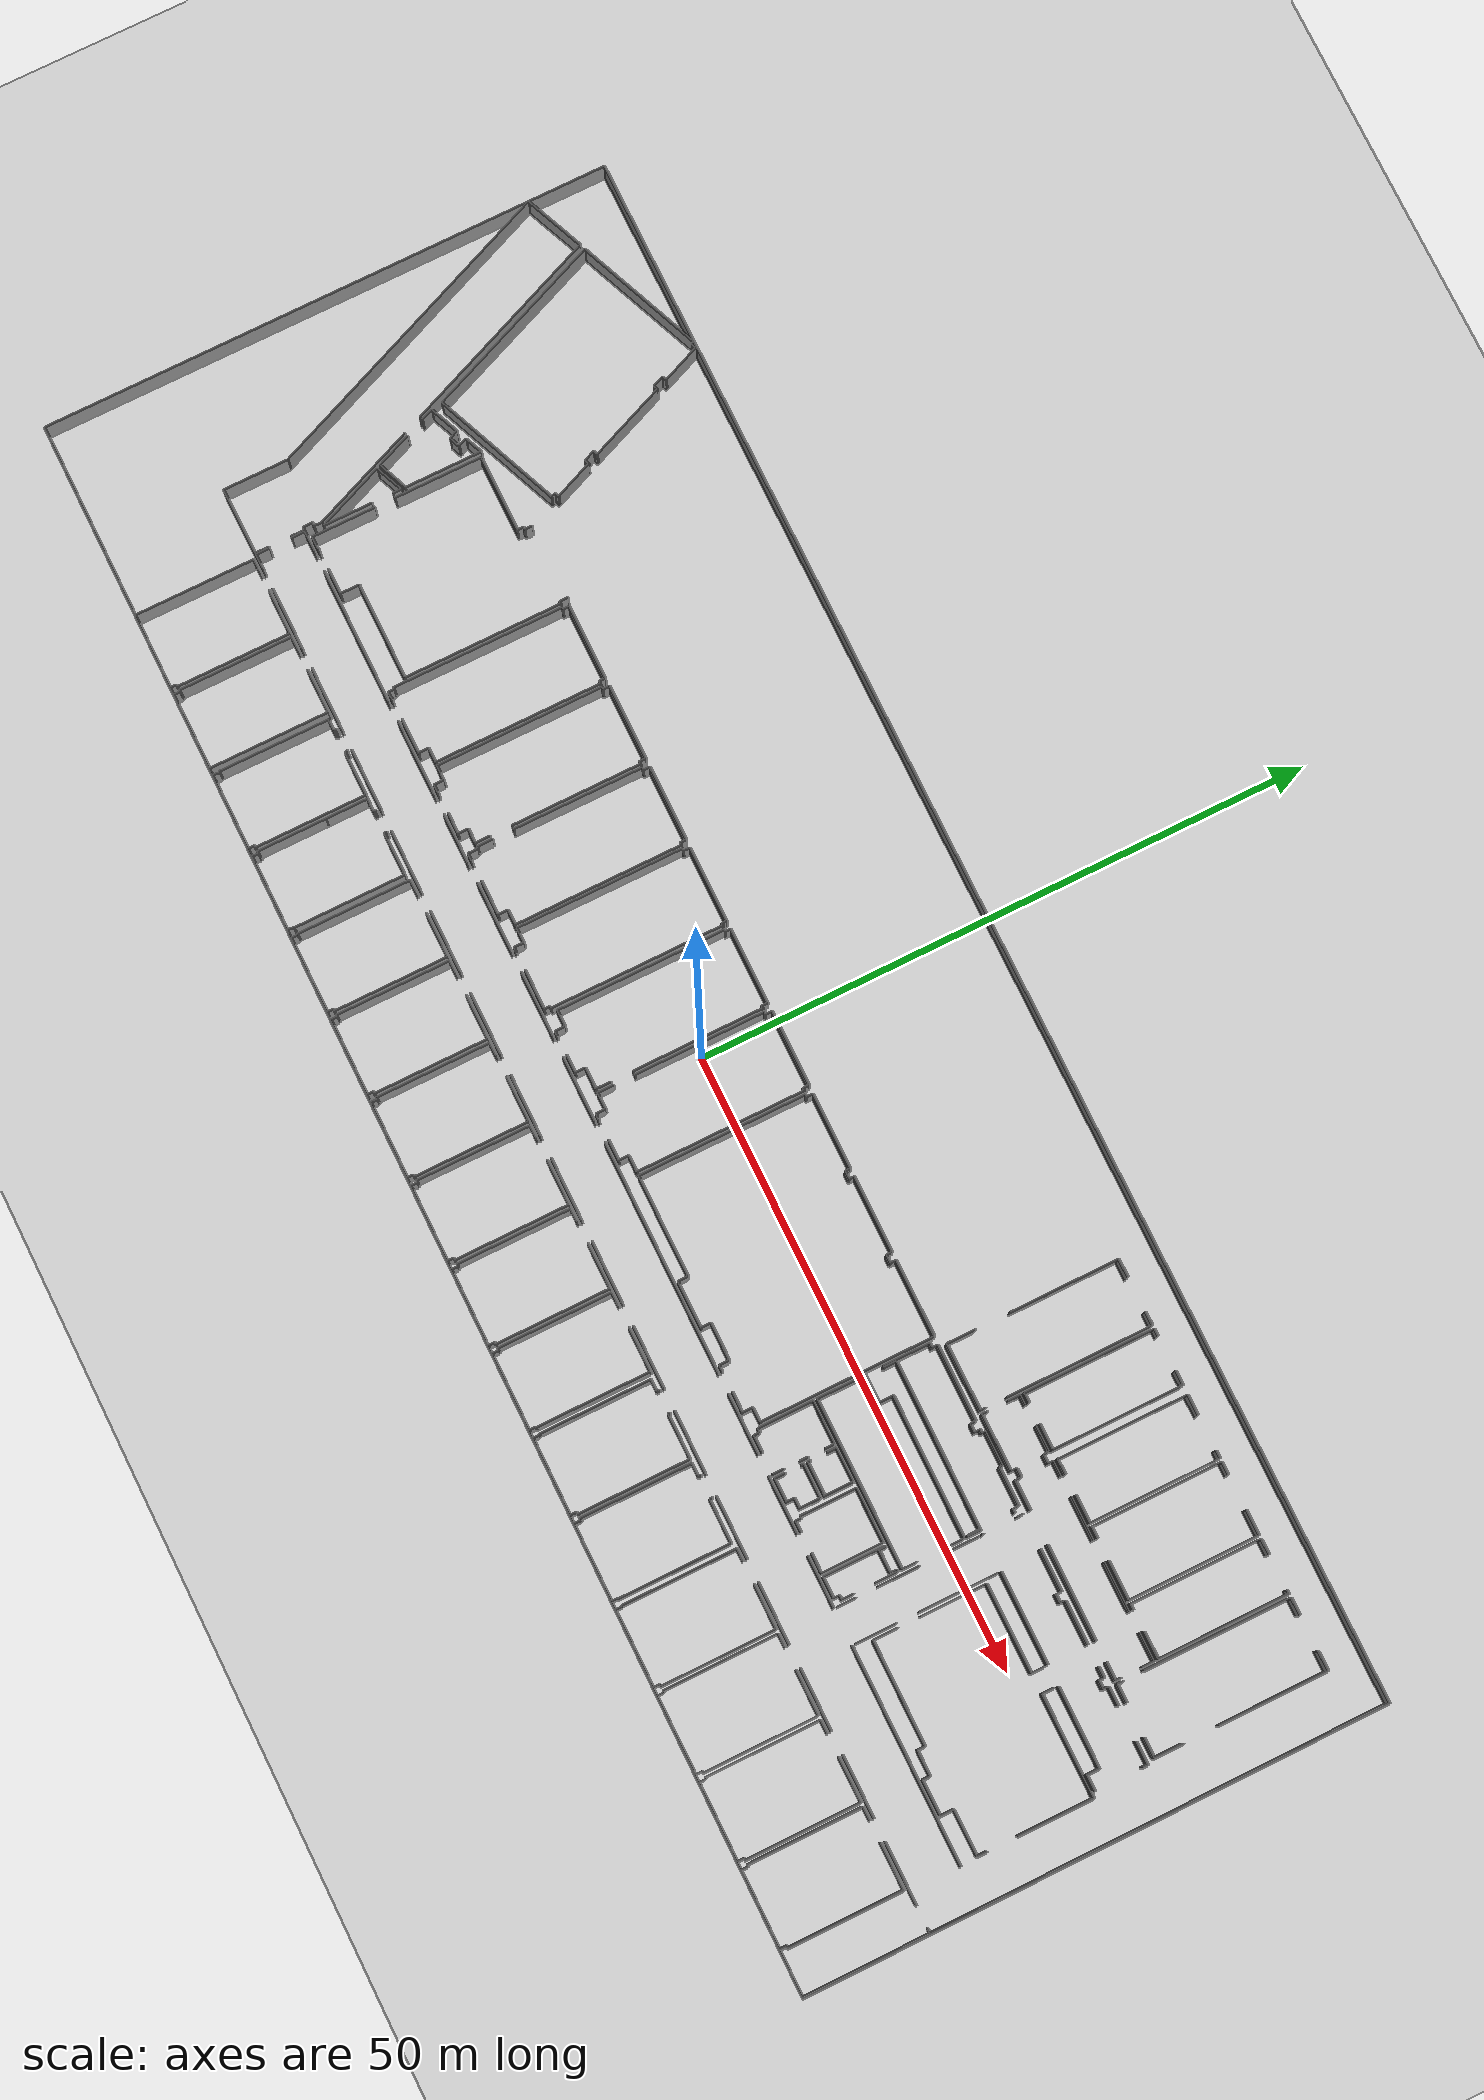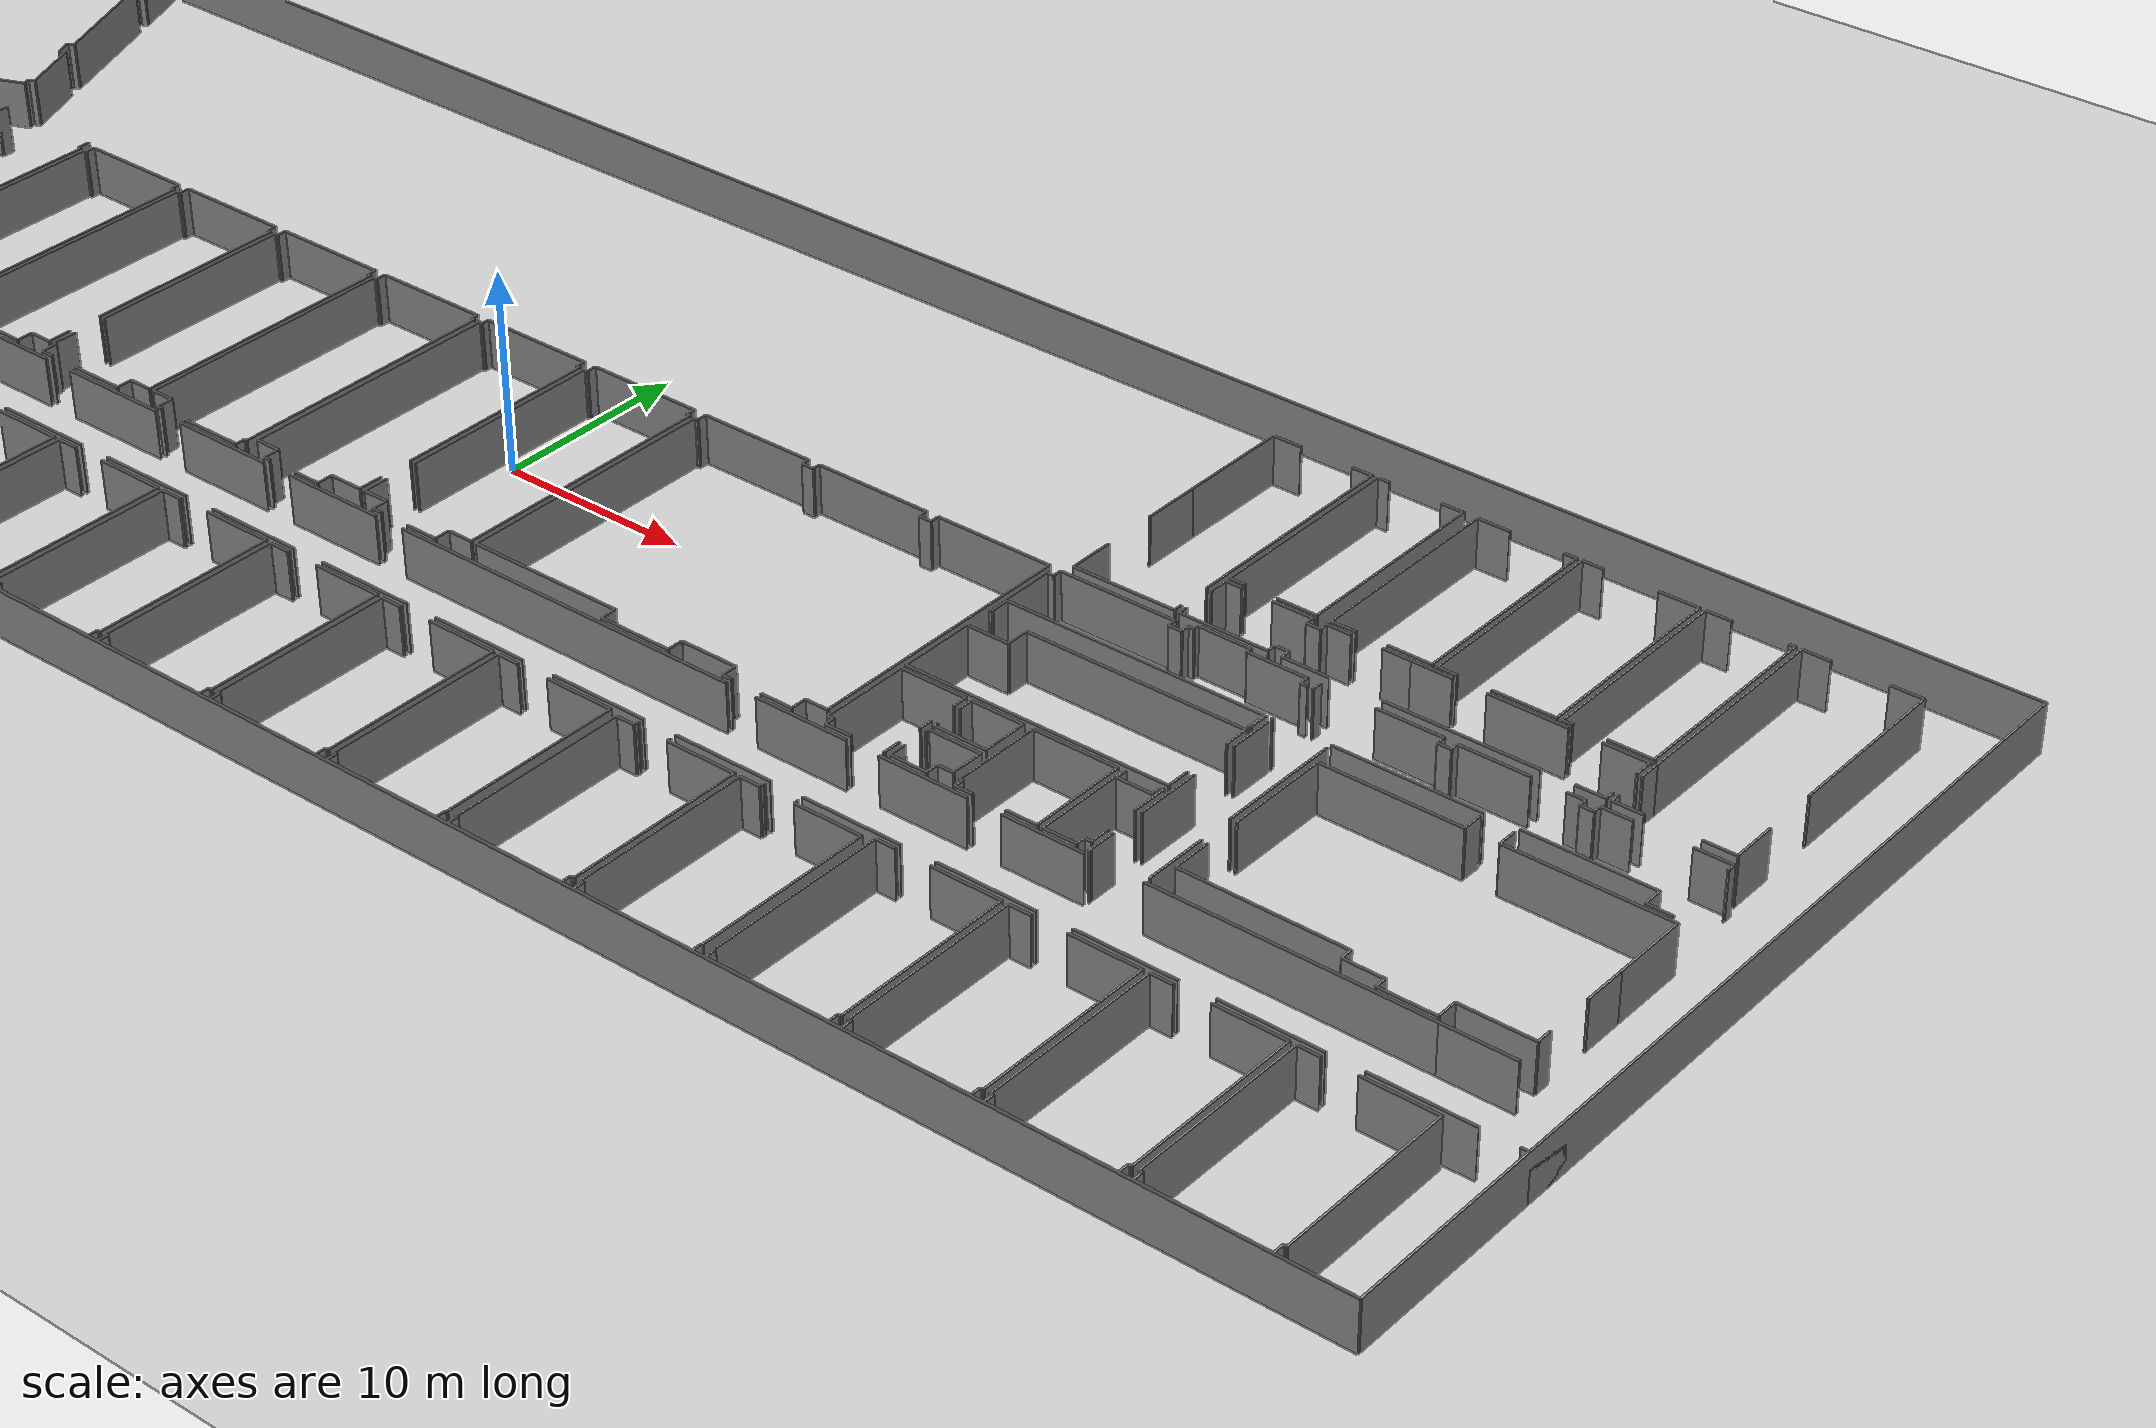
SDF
<sdf version="1.6">
  <world name="default">
    <light name="sun" type="directional">
      <cast_shadows>1</cast_shadows>
      <pose frame="">0 0 10 0 -0 0</pose>
      <diffuse>0.8 0.8 0.8 1</diffuse>
      <specular>0.1 0.1 0.1 1</specular>
      <attenuation>
        <range>1000</range>
        <constant>0.9</constant>
        <linear>0.01</linear>
        <quadratic>0.001</quadratic>
      </attenuation>
      <direction>-0.5 0.5 -1</direction>
    </light>
    <model name="ground_plane">
      <static>1</static>
      <link name="link">
        <collision name="collision">
          <geometry>
            <plane>
              <normal>0 0 1</normal>
              <size>100 100</size>
            </plane>
          </geometry>
          <surface>
            <friction>
              <ode>
                <mu>100</mu>
                <mu2>50</mu2>
              </ode>
              <torsional>
                <ode />
              </torsional>
            </friction>
            <contact>
              <ode />
            </contact>
            <bounce />
          </surface>
          <max_contacts>10</max_contacts>
        </collision>
        <visual name="visual">
          <cast_shadows>0</cast_shadows>
          <geometry>
            <plane>
              <normal>0 0 1</normal>
              <size>100 100</size>
            </plane>
          </geometry>
          <material>
            <script>
              <uri>file://media/materials/scripts/gazebo.material</uri>
              <name>Gazebo/Grey</name>
            </script>
          </material>
        </visual>
        <self_collide>0</self_collide>
        <kinematic>0</kinematic>
        <gravity>1</gravity>
      </link>
    </model>
    <gravity>0 0 -9.8</gravity>
    <magnetic_field>6e-06 2.3e-05 -4.2e-05</magnetic_field>
    <atmosphere type="adiabatic" />
    <physics default="0" name="default_physics" type="ode">
      <max_step_size>0.001</max_step_size>
      <real_time_factor>1</real_time_factor>
      <real_time_update_rate>1000</real_time_update_rate>
    </physics>
    <scene>
      <ambient>0.4 0.4 0.4 1</ambient>
      <background>0.7 0.7 0.7 1</background>
      <shadows>1</shadows>
    </scene>
    <spherical_coordinates>
      <surface_model>EARTH_WGS84</surface_model>
      <latitude_deg>0</latitude_deg>
      <longitude_deg>0</longitude_deg>
      <elevation>0</elevation>
      <heading_deg>0</heading_deg>
    </spherical_coordinates>
  <model name="0510032192_A_40_1_203">
		<static>1</static>
		<link name="Wall_0">
			<collision name="Wall_0_Collision">
				<geometry>
					<box>
						<size>6.19875831655 0.1 2.5</size>
					</box>
				</geometry>
				<pose frame="">3.09937915827 0 1.25 0 0 0</pose>
			</collision>
			<visual name="Wall_0_Visual">
				<pose frame="">3.09937915827 0 1.25 0 0 0</pose>
				<geometry>
					<box>
						<size>6.19875831655 0.1 2.5</size>
					</box>
				</geometry>
				<material>
					<script>
						<uri>file://media/materials/scripts/gazebo.material</uri>
						<name>Gazebo/Grey</name>
					</script>
					<ambient>1 1 1 1</ambient>
				</material>
			</visual>
			<pose frame="">16.2161062993 -46.7425444979 0 0 0 0.0</pose>
		</link>
		<link name="Wall_1">
			<collision name="Wall_1_Collision">
				<geometry>
					<box>
						<size>0.544205583127 0.1 2.5</size>
					</box>
				</geometry>
				<pose frame="">0.272102791564 0 1.25 0 0 0</pose>
			</collision>
			<visual name="Wall_1_Visual">
				<pose frame="">0.272102791564 0 1.25 0 0 0</pose>
				<geometry>
					<box>
						<size>0.544205583127 0.1 2.5</size>
					</box>
				</geometry>
				<material>
					<script>
						<uri>file://media/materials/scripts/gazebo.material</uri>
						<name>Gazebo/Grey</name>
					</script>
					<ambient>1 1 1 1</ambient>
				</material>
			</visual>
			<pose frame="">22.4148646158 -46.7425444979 0 0 0 1.57079632679</pose>
		</link>
		<link name="Wall_2">
			<collision name="Wall_2_Collision">
				<geometry>
					<box>
						<size>0.157847579226 0.1 2.5</size>
					</box>
				</geometry>
				<pose frame="">0.0789237896128 0 1.25 0 0 0</pose>
			</collision>
			<visual name="Wall_2_Visual">
				<pose frame="">0.0789237896128 0 1.25 0 0 0</pose>
				<geometry>
					<box>
						<size>0.157847579226 0.1 2.5</size>
					</box>
				</geometry>
				<material>
					<script>
						<uri>file://media/materials/scripts/gazebo.material</uri>
						<name>Gazebo/Grey</name>
					</script>
					<ambient>1 1 1 1</ambient>
				</material>
			</visual>
			<pose frame="">22.4148646158 -46.1983389148 0 0 0 0.0</pose>
		</link>
		<link name="Wall_3">
			<collision name="Wall_3_Collision">
				<geometry>
					<box>
						<size>9.21705313058 0.1 2.5</size>
					</box>
				</geometry>
				<pose frame="">4.60852656529 0 1.25 0 0 0</pose>
			</collision>
			<visual name="Wall_3_Visual">
				<pose frame="">4.60852656529 0 1.25 0 0 0</pose>
				<geometry>
					<box>
						<size>9.21705313058 0.1 2.5</size>
					</box>
				</geometry>
				<material>
					<script>
						<uri>file://media/materials/scripts/gazebo.material</uri>
						<name>Gazebo/Grey</name>
					</script>
					<ambient>1 1 1 1</ambient>
				</material>
			</visual>
			<pose frame="">22.5727121951 -46.1983389148 0 0 0 1.57079632679</pose>
		</link>
		<link name="Wall_4">
			<collision name="Wall_4_Collision">
				<geometry>
					<box>
						<size>3.70064880185 0.1 2.5</size>
					</box>
				</geometry>
				<pose frame="">1.85032440092 0 1.25 0 0 0</pose>
			</collision>
			<visual name="Wall_4_Visual">
				<pose frame="">1.85032440092 0 1.25 0 0 0</pose>
				<geometry>
					<box>
						<size>3.70064880185 0.1 2.5</size>
					</box>
				</geometry>
				<material>
					<script>
						<uri>file://media/materials/scripts/gazebo.material</uri>
						<name>Gazebo/Grey</name>
					</script>
					<ambient>1 1 1 1</ambient>
				</material>
			</visual>
			<pose frame="">22.5727121951 -36.9812857842 0 0 0 3.14159265359</pose>
		</link>
		<link name="Wall_5">
			<collision name="Wall_5_Collision">
				<geometry>
					<box>
						<size>0.954838053722 0.1 2.5</size>
					</box>
				</geometry>
				<pose frame="">0.477419026861 0 1.25 0 0 0</pose>
			</collision>
			<visual name="Wall_5_Visual">
				<pose frame="">0.477419026861 0 1.25 0 0 0</pose>
				<geometry>
					<box>
						<size>0.954838053722 0.1 2.5</size>
					</box>
				</geometry>
				<material>
					<script>
						<uri>file://media/materials/scripts/gazebo.material</uri>
						<name>Gazebo/Grey</name>
					</script>
					<ambient>1 1 1 1</ambient>
				</material>
			</visual>
			<pose frame="">17.1753925537 -36.9812857842 0 0 0 3.14159265359</pose>
		</link>
		<link name="Wall_6">
			<collision name="Wall_6_Collision">
				<geometry>
					<box>
						<size>9.76125972723 0.1 2.5</size>
					</box>
				</geometry>
				<pose frame="">4.88062986361 0 1.25 0 0 0</pose>
			</collision>
			<visual name="Wall_6_Visual">
				<pose frame="">4.88062986361 0 1.25 0 0 0</pose>
				<geometry>
					<box>
						<size>9.76125972723 0.1 2.5</size>
					</box>
				</geometry>
				<material>
					<script>
						<uri>file://media/materials/scripts/gazebo.material</uri>
						<name>Gazebo/Grey</name>
					</script>
					<ambient>1 1 1 1</ambient>
				</material>
			</visual>
			<pose frame="">16.2205545 -36.9812857842 0 0 0 -1.57125202626</pose>
		</link>
		<link name="Wall_7">
			<collision name="Wall_7_Collision">
				<geometry>
					<box>
						<size>0.520693665127 0.1 2.5</size>
					</box>
				</geometry>
				<pose frame="">0.260346832563 0 1.25 0 0 0</pose>
			</collision>
			<visual name="Wall_7_Visual">
				<pose frame="">0.260346832563 0 1.25 0 0 0</pose>
				<geometry>
					<box>
						<size>0.520693665127 0.1 2.5</size>
					</box>
				</geometry>
				<material>
					<script>
						<uri>file://media/materials/scripts/gazebo.material</uri>
						<name>Gazebo/Grey</name>
					</script>
					<ambient>1 1 1 1</ambient>
				</material>
			</visual>
			<pose frame="">23.0235055634 -46.7333939136 0 0 0 1.57079632679</pose>
		</link>
		<link name="Wall_8">
			<collision name="Wall_8_Collision">
				<geometry>
					<box>
						<size>0.148188629128 0.1 2.5</size>
					</box>
				</geometry>
				<pose frame="">0.074094314564 0 1.25 0 0 0</pose>
			</collision>
			<visual name="Wall_8_Visual">
				<pose frame="">0.074094314564 0 1.25 0 0 0</pose>
				<geometry>
					<box>
						<size>0.148188629128 0.1 2.5</size>
					</box>
				</geometry>
				<material>
					<script>
						<uri>file://media/materials/scripts/gazebo.material</uri>
						<name>Gazebo/Grey</name>
					</script>
					<ambient>1 1 1 1</ambient>
				</material>
			</visual>
			<pose frame="">23.0235055634 -46.2127002485 0 0 0 3.14159265359</pose>
		</link>
		<link name="Wall_9">
			<collision name="Wall_9_Collision">
				<geometry>
					<box>
						<size>9.22734753792 0.1 2.5</size>
					</box>
				</geometry>
				<pose frame="">4.61367376896 0 1.25 0 0 0</pose>
			</collision>
			<visual name="Wall_9_Visual">
				<pose frame="">4.61367376896 0 1.25 0 0 0</pose>
				<geometry>
					<box>
						<size>9.22734753792 0.1 2.5</size>
					</box>
				</geometry>
				<material>
					<script>
						<uri>file://media/materials/scripts/gazebo.material</uri>
						<name>Gazebo/Grey</name>
					</script>
					<ambient>1 1 1 1</ambient>
				</material>
			</visual>
			<pose frame="">22.8753169343 -46.2127002485 0 0 0 1.57079632679</pose>
		</link>
		<link name="Wall_10">
			<collision name="Wall_10_Collision">
				<geometry>
					<box>
						<size>1.13403699632 0.1 2.5</size>
					</box>
				</geometry>
				<pose frame="">0.56701849816 0 1.25 0 0 0</pose>
			</collision>
			<visual name="Wall_10_Visual">
				<pose frame="">0.56701849816 0 1.25 0 0 0</pose>
				<geometry>
					<box>
						<size>1.13403699632 0.1 2.5</size>
					</box>
				</geometry>
				<material>
					<script>
						<uri>file://media/materials/scripts/gazebo.material</uri>
						<name>Gazebo/Grey</name>
					</script>
					<ambient>1 1 1 1</ambient>
				</material>
			</visual>
			<pose frame="">22.8753169343 -36.9853527105 0 0 0 0.0</pose>
		</link>
		<link name="Wall_11">
			<collision name="Wall_11_Collision">
				<geometry>
					<box>
						<size>3.58842705269 0.1 2.5</size>
					</box>
				</geometry>
				<pose frame="">1.79421352634 0 1.25 0 0 0</pose>
			</collision>
			<visual name="Wall_11_Visual">
				<pose frame="">1.79421352634 0 1.25 0 0 0</pose>
				<geometry>
					<box>
						<size>3.58842705269 0.1 2.5</size>
					</box>
				</geometry>
				<material>
					<script>
						<uri>file://media/materials/scripts/gazebo.material</uri>
						<name>Gazebo/Grey</name>
					</script>
					<ambient>1 1 1 1</ambient>
				</material>
			</visual>
			<pose frame="">25.6855630469 -36.9853527105 0 0 0 0.0</pose>
		</link>
		<link name="Wall_12">
			<collision name="Wall_12_Collision">
				<geometry>
					<box>
						<size>9.74105117337 0.1 2.5</size>
					</box>
				</geometry>
				<pose frame="">4.87052558669 0 1.25 0 0 0</pose>
			</collision>
			<visual name="Wall_12_Visual">
				<pose frame="">4.87052558669 0 1.25 0 0 0</pose>
				<geometry>
					<box>
						<size>9.74105117337 0.1 2.5</size>
					</box>
				</geometry>
				<material>
					<script>
						<uri>file://media/materials/scripts/gazebo.material</uri>
						<name>Gazebo/Grey</name>
					</script>
					<ambient>1 1 1 1</ambient>
				</material>
			</visual>
			<pose frame="">29.2739900996 -36.9853527105 0 0 0 -1.57079632679</pose>
		</link>
		<link name="Wall_13">
			<collision name="Wall_13_Collision">
				<geometry>
					<box>
						<size>6.25048844468 0.1 2.5</size>
					</box>
				</geometry>
				<pose frame="">3.12524422234 0 1.25 0 0 0</pose>
			</collision>
			<visual name="Wall_13_Visual">
				<pose frame="">3.12524422234 0 1.25 0 0 0</pose>
				<geometry>
					<box>
						<size>6.25048844468 0.1 2.5</size>
					</box>
				</geometry>
				<material>
					<script>
						<uri>file://media/materials/scripts/gazebo.material</uri>
						<name>Gazebo/Grey</name>
					</script>
					<ambient>1 1 1 1</ambient>
				</material>
			</visual>
			<pose frame="">29.2739900996 -46.7264038839 0 0 0 -3.14047433601</pose>
		</link>
		<link name="Wall_14">
			<collision name="Wall_14_Collision">
				<geometry>
					<box>
						<size>0.551449795701 0.1 2.5</size>
					</box>
				</geometry>
				<pose frame="">0.27572489785 0 1.25 0 0 0</pose>
			</collision>
			<visual name="Wall_14_Visual">
				<pose frame="">0.27572489785 0 1.25 0 0 0</pose>
				<geometry>
					<box>
						<size>0.551449795701 0.1 2.5</size>
					</box>
				</geometry>
				<material>
					<script>
						<uri>file://media/materials/scripts/gazebo.material</uri>
						<name>Gazebo/Grey</name>
					</script>
					<ambient>1 1 1 1</ambient>
				</material>
			</visual>
			<pose frame="">29.868142622 -46.7346648281 0 0 0 1.57079632679</pose>
		</link>
		<link name="Wall_15">
			<collision name="Wall_15_Collision">
				<geometry>
					<box>
						<size>0.0752381376019 0.1 2.5</size>
					</box>
				</geometry>
				<pose frame="">0.037619068801 0 1.25 0 0 0</pose>
			</collision>
			<visual name="Wall_15_Visual">
				<pose frame="">0.037619068801 0 1.25 0 0 0</pose>
				<geometry>
					<box>
						<size>0.0752381376019 0.1 2.5</size>
					</box>
				</geometry>
				<material>
					<script>
						<uri>file://media/materials/scripts/gazebo.material</uri>
						<name>Gazebo/Grey</name>
					</script>
					<ambient>1 1 1 1</ambient>
				</material>
			</visual>
			<pose frame="">29.868142622 -46.1832150324 0 0 0 3.14159265359</pose>
		</link>
		<link name="Wall_16">
			<collision name="Wall_16_Collision">
				<geometry>
					<box>
						<size>8.97557937814 0.1 2.5</size>
					</box>
				</geometry>
				<pose frame="">4.48778968907 0 1.25 0 0 0</pose>
			</collision>
			<visual name="Wall_16_Visual">
				<pose frame="">4.48778968907 0 1.25 0 0 0</pose>
				<geometry>
					<box>
						<size>8.97557937814 0.1 2.5</size>
					</box>
				</geometry>
				<material>
					<script>
						<uri>file://media/materials/scripts/gazebo.material</uri>
						<name>Gazebo/Grey</name>
					</script>
					<ambient>1 1 1 1</ambient>
				</material>
			</visual>
			<pose frame="">29.7929044844 -46.1832150324 0 0 0 1.57079632679</pose>
		</link>
		<link name="Wall_17">
			<collision name="Wall_17_Collision">
				<geometry>
					<box>
						<size>0.956108968208 0.1 2.5</size>
					</box>
				</geometry>
				<pose frame="">0.478054484104 0 1.25 0 0 0</pose>
			</collision>
			<visual name="Wall_17_Visual">
				<pose frame="">0.478054484104 0 1.25 0 0 0</pose>
				<geometry>
					<box>
						<size>0.956108968208 0.1 2.5</size>
					</box>
				</geometry>
				<material>
					<script>
						<uri>file://media/materials/scripts/gazebo.material</uri>
						<name>Gazebo/Grey</name>
					</script>
					<ambient>1 1 1 1</ambient>
				</material>
			</visual>
			<pose frame="">29.7929044844 -37.2076356542 0 0 0 0.0</pose>
		</link>
		<link name="Wall_18">
			<collision name="Wall_18_Collision">
				<geometry>
					<box>
						<size>0.220122389065 0.1 2.5</size>
					</box>
				</geometry>
				<pose frame="">0.110061194533 0 1.25 0 0 0</pose>
			</collision>
			<visual name="Wall_18_Visual">
				<pose frame="">0.110061194533 0 1.25 0 0 0</pose>
				<geometry>
					<box>
						<size>0.220122389065 0.1 2.5</size>
					</box>
				</geometry>
				<material>
					<script>
						<uri>file://media/materials/scripts/gazebo.material</uri>
						<name>Gazebo/Grey</name>
					</script>
					<ambient>1 1 1 1</ambient>
				</material>
			</visual>
			<pose frame="">30.7490134526 -37.2076356542 0 0 0 1.57079632679</pose>
		</link>
		<link name="Wall_19">
			<collision name="Wall_19_Collision">
				<geometry>
					<box>
						<size>0.0706628454504 0.1 2.5</size>
					</box>
				</geometry>
				<pose frame="">0.0353314227252 0 1.25 0 0 0</pose>
			</collision>
			<visual name="Wall_19_Visual">
				<pose frame="">0.0353314227252 0 1.25 0 0 0</pose>
				<geometry>
					<box>
						<size>0.0706628454504 0.1 2.5</size>
					</box>
				</geometry>
				<material>
					<script>
						<uri>file://media/materials/scripts/gazebo.material</uri>
						<name>Gazebo/Grey</name>
					</script>
					<ambient>1 1 1 1</ambient>
				</material>
			</visual>
			<pose frame="">30.7490134526 -36.9875132652 0 0 0 0.0</pose>
		</link>
		<link name="Wall_20">
			<collision name="Wall_20_Collision">
				<geometry>
					<box>
						<size>0.0831178074183 0.1 2.5</size>
					</box>
				</geometry>
				<pose frame="">0.0415589037092 0 1.25 0 0 0</pose>
			</collision>
			<visual name="Wall_20_Visual">
				<pose frame="">0.0415589037092 0 1.25 0 0 0</pose>
				<geometry>
					<box>
						<size>0.0831178074183 0.1 2.5</size>
					</box>
				</geometry>
				<material>
					<script>
						<uri>file://media/materials/scripts/gazebo.material</uri>
						<name>Gazebo/Grey</name>
					</script>
					<ambient>1 1 1 1</ambient>
				</material>
			</visual>
			<pose frame="">32.5064340046 -36.9875132652 0 0 0 0.0</pose>
		</link>
		<link name="Wall_21">
			<collision name="Wall_21_Collision">
				<geometry>
					<box>
						<size>0.186951520967 0.1 2.5</size>
					</box>
				</geometry>
				<pose frame="">0.0934757604835 0 1.25 0 0 0</pose>
			</collision>
			<visual name="Wall_21_Visual">
				<pose frame="">0.0934757604835 0 1.25 0 0 0</pose>
				<geometry>
					<box>
						<size>0.186951520967 0.1 2.5</size>
					</box>
				</geometry>
				<material>
					<script>
						<uri>file://media/materials/scripts/gazebo.material</uri>
						<name>Gazebo/Grey</name>
					</script>
					<ambient>1 1 1 1</ambient>
				</material>
			</visual>
			<pose frame="">32.589551812 -36.9875132652 0 0 0 -1.57079632679</pose>
		</link>
		<link name="Wall_22">
			<collision name="Wall_22_Collision">
				<geometry>
					<box>
						<size>3.60812622723 0.1 2.5</size>
					</box>
				</geometry>
				<pose frame="">1.80406311361 0 1.25 0 0 0</pose>
			</collision>
			<visual name="Wall_22_Visual">
				<pose frame="">1.80406311361 0 1.25 0 0 0</pose>
				<geometry>
					<box>
						<size>3.60812622723 0.1 2.5</size>
					</box>
				</geometry>
				<material>
					<script>
						<uri>file://media/materials/scripts/gazebo.material</uri>
						<name>Gazebo/Grey</name>
					</script>
					<ambient>1 1 1 1</ambient>
				</material>
			</visual>
			<pose frame="">32.589551812 -37.1744647861 0 0 0 0.0</pose>
		</link>
		<link name="Wall_23">
			<collision name="Wall_23_Collision">
				<geometry>
					<box>
						<size>9.00875024624 0.1 2.5</size>
					</box>
				</geometry>
				<pose frame="">4.50437512312 0 1.25 0 0 0</pose>
			</collision>
			<visual name="Wall_23_Visual">
				<pose frame="">4.50437512312 0 1.25 0 0 0</pose>
				<geometry>
					<box>
						<size>9.00875024624 0.1 2.5</size>
					</box>
				</geometry>
				<material>
					<script>
						<uri>file://media/materials/scripts/gazebo.material</uri>
						<name>Gazebo/Grey</name>
					</script>
					<ambient>1 1 1 1</ambient>
				</material>
			</visual>
			<pose frame="">36.1976780392 -37.1744647861 0 0 0 -1.57079632679</pose>
		</link>
		<link name="Wall_24">
			<collision name="Wall_24_Collision">
				<geometry>
					<box>
						<size>0.154034835766 0.1 2.5</size>
					</box>
				</geometry>
				<pose frame="">0.077017417883 0 1.25 0 0 0</pose>
			</collision>
			<visual name="Wall_24_Visual">
				<pose frame="">0.077017417883 0 1.25 0 0 0</pose>
				<geometry>
					<box>
						<size>0.154034835766 0.1 2.5</size>
					</box>
				</geometry>
				<material>
					<script>
						<uri>file://media/materials/scripts/gazebo.material</uri>
						<name>Gazebo/Grey</name>
					</script>
					<ambient>1 1 1 1</ambient>
				</material>
			</visual>
			<pose frame="">36.1976780392 -46.1832150324 0 0 0 3.14159265359</pose>
		</link>
		<link name="Wall_25">
			<collision name="Wall_25_Collision">
				<geometry>
					<box>
						<size>0.5420450285 0.1 2.5</size>
					</box>
				</geometry>
				<pose frame="">0.27102251425 0 1.25 0 0 0</pose>
			</collision>
			<visual name="Wall_25_Visual">
				<pose frame="">0.27102251425 0 1.25 0 0 0</pose>
				<geometry>
					<box>
						<size>0.5420450285 0.1 2.5</size>
					</box>
				</geometry>
				<material>
					<script>
						<uri>file://media/materials/scripts/gazebo.material</uri>
						<name>Gazebo/Grey</name>
					</script>
					<ambient>1 1 1 1</ambient>
				</material>
			</visual>
			<pose frame="">36.0436432035 -46.1832150324 0 0 0 -1.57079632679</pose>
		</link>
		<link name="Wall_26">
			<collision name="Wall_26_Collision">
				<geometry>
					<box>
						<size>6.17550774277 0.1 2.5</size>
					</box>
				</geometry>
				<pose frame="">3.08775387139 0 1.25 0 0 0</pose>
			</collision>
			<visual name="Wall_26_Visual">
				<pose frame="">3.08775387139 0 1.25 0 0 0</pose>
				<geometry>
					<box>
						<size>6.17550774277 0.1 2.5</size>
					</box>
				</geometry>
				<material>
					<script>
						<uri>file://media/materials/scripts/gazebo.material</uri>
						<name>Gazebo/Grey</name>
					</script>
					<ambient>1 1 1 1</ambient>
				</material>
			</visual>
			<pose frame="">36.0436432035 -46.7252600609 0 0 0 -3.140069739</pose>
		</link>
		<link name="Wall_27">
			<collision name="Wall_27_Collision">
				<geometry>
					<box>
						<size>0.526539871765 0.1 2.5</size>
					</box>
				</geometry>
				<pose frame="">0.263269935882 0 1.25 0 0 0</pose>
			</collision>
			<visual name="Wall_27_Visual">
				<pose frame="">0.263269935882 0 1.25 0 0 0</pose>
				<geometry>
					<box>
						<size>0.526539871765 0.1 2.5</size>
					</box>
				</geometry>
				<material>
					<script>
						<uri>file://media/materials/scripts/gazebo.material</uri>
						<name>Gazebo/Grey</name>
					</script>
					<ambient>1 1 1 1</ambient>
				</material>
			</visual>
			<pose frame="">36.6953681522 -46.7264038839 0 0 0 1.57079632679</pose>
		</link>
		<link name="Wall_28">
			<collision name="Wall_28_Collision">
				<geometry>
					<box>
						<size>0.175513290588 0.1 2.5</size>
					</box>
				</geometry>
				<pose frame="">0.0877566452941 0 1.25 0 0 0</pose>
			</collision>
			<visual name="Wall_28_Visual">
				<pose frame="">0.0877566452941 0 1.25 0 0 0</pose>
				<geometry>
					<box>
						<size>0.175513290588 0.1 2.5</size>
					</box>
				</geometry>
				<material>
					<script>
						<uri>file://media/materials/scripts/gazebo.material</uri>
						<name>Gazebo/Grey</name>
					</script>
					<ambient>1 1 1 1</ambient>
				</material>
			</visual>
			<pose frame="">36.6953681522 -46.1998640121 0 0 0 3.14159265359</pose>
		</link>
		<link name="Wall_29">
			<collision name="Wall_29_Collision">
				<geometry>
					<box>
						<size>5.5946926611 0.1 2.5</size>
					</box>
				</geometry>
				<pose frame="">2.79734633055 0 1.25 0 0 0</pose>
			</collision>
			<visual name="Wall_29_Visual">
				<pose frame="">2.79734633055 0 1.25 0 0 0</pose>
				<geometry>
					<box>
						<size>5.5946926611 0.1 2.5</size>
					</box>
				</geometry>
				<material>
					<script>
						<uri>file://media/materials/scripts/gazebo.material</uri>
						<name>Gazebo/Grey</name>
					</script>
					<ambient>1 1 1 1</ambient>
				</material>
			</visual>
			<pose frame="">36.5198548616 -46.1998640121 0 0 0 1.57079632679</pose>
		</link>
		<link name="Wall_30">
			<collision name="Wall_30_Collision">
				<geometry>
					<box>
						<size>3.4035089949 0.1 2.5</size>
					</box>
				</geometry>
				<pose frame="">1.70175449745 0 1.25 0 0 0</pose>
			</collision>
			<visual name="Wall_30_Visual">
				<pose frame="">1.70175449745 0 1.25 0 0 0</pose>
				<geometry>
					<box>
						<size>3.4035089949 0.1 2.5</size>
					</box>
				</geometry>
				<material>
					<script>
						<uri>file://media/materials/scripts/gazebo.material</uri>
						<name>Gazebo/Grey</name>
					</script>
					<ambient>1 1 1 1</ambient>
				</material>
			</visual>
			<pose frame="">36.5198548616 -40.605171351 0 0 0 1.57079632679</pose>
		</link>
		<link name="Wall_31">
			<collision name="Wall_31_Collision">
				<geometry>
					<box>
						<size>1.06642434564 0.1 2.5</size>
					</box>
				</geometry>
				<pose frame="">0.533212172819 0 1.25 0 0 0</pose>
			</collision>
			<visual name="Wall_31_Visual">
				<pose frame="">0.533212172819 0 1.25 0 0 0</pose>
				<geometry>
					<box>
						<size>1.06642434564 0.1 2.5</size>
					</box>
				</geometry>
				<material>
					<script>
						<uri>file://media/materials/scripts/gazebo.material</uri>
						<name>Gazebo/Grey</name>
					</script>
					<ambient>1 1 1 1</ambient>
				</material>
			</visual>
			<pose frame="">36.5198548616 -37.2016623561 0 0 0 0.0</pose>
		</link>
		<link name="Wall_32">
			<collision name="Wall_32_Collision">
				<geometry>
					<box>
						<size>0.215038731119 0.1 2.5</size>
					</box>
				</geometry>
				<pose frame="">0.107519365559 0 1.25 0 0 0</pose>
			</collision>
			<visual name="Wall_32_Visual">
				<pose frame="">0.107519365559 0 1.25 0 0 0</pose>
				<geometry>
					<box>
						<size>0.215038731119 0.1 2.5</size>
					</box>
				</geometry>
				<material>
					<script>
						<uri>file://media/materials/scripts/gazebo.material</uri>
						<name>Gazebo/Grey</name>
					</script>
					<ambient>1 1 1 1</ambient>
				</material>
			</visual>
			<pose frame="">37.5862792072 -37.2016623561 0 0 0 1.57079632679</pose>
		</link>
		<link name="Wall_33">
			<collision name="Wall_33_Collision">
				<geometry>
					<box>
						<size>0.0669771934395 0.1 2.5</size>
					</box>
				</geometry>
				<pose frame="">0.0334885967198 0 1.25 0 0 0</pose>
			</collision>
			<visual name="Wall_33_Visual">
				<pose frame="">0.0334885967198 0 1.25 0 0 0</pose>
				<geometry>
					<box>
						<size>0.0669771934395 0.1 2.5</size>
					</box>
				</geometry>
				<material>
					<script>
						<uri>file://media/materials/scripts/gazebo.material</uri>
						<name>Gazebo/Grey</name>
					</script>
					<ambient>1 1 1 1</ambient>
				</material>
			</visual>
			<pose frame="">37.5862792072 -36.986623625 0 0 0 0.0</pose>
		</link>
		<link name="Wall_34">
			<collision name="Wall_34_Collision">
				<geometry>
					<box>
						<size>0.0621477183908 0.1 2.5</size>
					</box>
				</geometry>
				<pose frame="">0.0310738591954 0 1.25 0 0 0</pose>
			</collision>
			<visual name="Wall_34_Visual">
				<pose frame="">0.0310738591954 0 1.25 0 0 0</pose>
				<geometry>
					<box>
						<size>0.0621477183908 0.1 2.5</size>
					</box>
				</geometry>
				<material>
					<script>
						<uri>file://media/materials/scripts/gazebo.material</uri>
						<name>Gazebo/Grey</name>
					</script>
					<ambient>1 1 1 1</ambient>
				</material>
			</visual>
			<pose frame="">39.3445893993 -36.986623625 0 0 0 0.0</pose>
		</link>
		<link name="Wall_35">
			<collision name="Wall_35_Collision">
				<geometry>
					<box>
						<size>0.195975013821 0.1 2.5</size>
					</box>
				</geometry>
				<pose frame="">0.0979875069106 0 1.25 0 0 0</pose>
			</collision>
			<visual name="Wall_35_Visual">
				<pose frame="">0.0979875069106 0 1.25 0 0 0</pose>
				<geometry>
					<box>
						<size>0.195975013821 0.1 2.5</size>
					</box>
				</geometry>
				<material>
					<script>
						<uri>file://media/materials/scripts/gazebo.material</uri>
						<name>Gazebo/Grey</name>
					</script>
					<ambient>1 1 1 1</ambient>
				</material>
			</visual>
			<pose frame="">39.4067371177 -36.986623625 0 0 0 -1.57079632679</pose>
		</link>
		<link name="Wall_36">
			<collision name="Wall_36_Collision">
				<geometry>
					<box>
						<size>3.51522237826 0.1 2.5</size>
					</box>
				</geometry>
				<pose frame="">1.75761118913 0 1.25 0 0 0</pose>
			</collision>
			<visual name="Wall_36_Visual">
				<pose frame="">1.75761118913 0 1.25 0 0 0</pose>
				<geometry>
					<box>
						<size>3.51522237826 0.1 2.5</size>
					</box>
				</geometry>
				<material>
					<script>
						<uri>file://media/materials/scripts/gazebo.material</uri>
						<name>Gazebo/Grey</name>
					</script>
					<ambient>1 1 1 1</ambient>
				</material>
			</visual>
			<pose frame="">39.4067371177 -37.1825986389 0 0 0 0.0</pose>
		</link>
		<link name="Wall_37">
			<collision name="Wall_37_Collision">
				<geometry>
					<box>
						<size>8.99438891254 0.1 2.5</size>
					</box>
				</geometry>
				<pose frame="">4.49719445627 0 1.25 0 0 0</pose>
			</collision>
			<visual name="Wall_37_Visual">
				<pose frame="">4.49719445627 0 1.25 0 0 0</pose>
				<geometry>
					<box>
						<size>8.99438891254 0.1 2.5</size>
					</box>
				</geometry>
				<material>
					<script>
						<uri>file://media/materials/scripts/gazebo.material</uri>
						<name>Gazebo/Grey</name>
					</script>
					<ambient>1 1 1 1</ambient>
				</material>
			</visual>
			<pose frame="">42.921959496 -37.1825986389 0 0 0 -1.57079632679</pose>
		</link>
		<link name="Wall_38">
			<collision name="Wall_38_Collision">
				<geometry>
					<box>
						<size>0.0536325913311 0.1 2.5</size>
					</box>
				</geometry>
				<pose frame="">0.0268162956655 0 1.25 0 0 0</pose>
			</collision>
			<visual name="Wall_38_Visual">
				<pose frame="">0.0268162956655 0 1.25 0 0 0</pose>
				<geometry>
					<box>
						<size>0.0536325913311 0.1 2.5</size>
					</box>
				</geometry>
				<material>
					<script>
						<uri>file://media/materials/scripts/gazebo.material</uri>
						<name>Gazebo/Grey</name>
					</script>
					<ambient>1 1 1 1</ambient>
				</material>
			</visual>
			<pose frame="">42.921959496 -46.1769875514 0 0 0 3.14159265359</pose>
		</link>
		<link name="Wall_39">
			<collision name="Wall_39_Collision">
				<geometry>
					<box>
						<size>0.544968131819 0.1 2.5</size>
					</box>
				</geometry>
				<pose frame="">0.27248406591 0 1.25 0 0 0</pose>
			</collision>
			<visual name="Wall_39_Visual">
				<pose frame="">0.27248406591 0 1.25 0 0 0</pose>
				<geometry>
					<box>
						<size>0.544968131819 0.1 2.5</size>
					</box>
				</geometry>
				<material>
					<script>
						<uri>file://media/materials/scripts/gazebo.material</uri>
						<name>Gazebo/Grey</name>
					</script>
					<ambient>1 1 1 1</ambient>
				</material>
			</visual>
			<pose frame="">42.8683269046 -46.1769875514 0 0 0 -1.57079632679</pose>
		</link>
		<link name="Wall_40">
			<collision name="Wall_40_Collision">
				<geometry>
					<box>
						<size>6.17296035514 0.1 2.5</size>
					</box>
				</geometry>
				<pose frame="">3.08648017757 0 1.25 0 0 0</pose>
			</collision>
			<visual name="Wall_40_Visual">
				<pose frame="">3.08648017757 0 1.25 0 0 0</pose>
				<geometry>
					<box>
						<size>6.17296035514 0.1 2.5</size>
					</box>
				</geometry>
				<material>
					<script>
						<uri>file://media/materials/scripts/gazebo.material</uri>
						<name>Gazebo/Grey</name>
					</script>
					<ambient>1 1 1 1</ambient>
				</material>
			</visual>
			<pose frame="">42.8683269046 -46.7219556832 0 0 0 -3.14087205912</pose>
		</link>
		<link name="Wall_41">
			<collision name="Wall_41_Collision">
				<geometry>
					<box>
						<size>0.534800815927 0.1 2.5</size>
					</box>
				</geometry>
				<pose frame="">0.267400407964 0 1.25 0 0 0</pose>
			</collision>
			<visual name="Wall_41_Visual">
				<pose frame="">0.267400407964 0 1.25 0 0 0</pose>
				<geometry>
					<box>
						<size>0.534800815927 0.1 2.5</size>
					</box>
				</geometry>
				<material>
					<script>
						<uri>file://media/materials/scripts/gazebo.material</uri>
						<name>Gazebo/Grey</name>
					</script>
					<ambient>1 1 1 1</ambient>
				</material>
			</visual>
			<pose frame="">43.5225936823 -46.7346648281 0 0 0 1.57079632679</pose>
		</link>
		<link name="Wall_42">
			<collision name="Wall_42_Collision">
				<geometry>
					<box>
						<size>0.0751110461533 0.1 2.5</size>
					</box>
				</geometry>
				<pose frame="">0.0375555230766 0 1.25 0 0 0</pose>
			</collision>
			<visual name="Wall_42_Visual">
				<pose frame="">0.0375555230766 0 1.25 0 0 0</pose>
				<geometry>
					<box>
						<size>0.0751110461533 0.1 2.5</size>
					</box>
				</geometry>
				<material>
					<script>
						<uri>file://media/materials/scripts/gazebo.material</uri>
						<name>Gazebo/Grey</name>
					</script>
					<ambient>1 1 1 1</ambient>
				</material>
			</visual>
			<pose frame="">43.5225936823 -46.1998640121 0 0 0 3.14159265359</pose>
		</link>
		<link name="Wall_43">
			<collision name="Wall_43_Collision">
				<geometry>
					<box>
						<size>9.2053607173 0.1 2.5</size>
					</box>
				</geometry>
				<pose frame="">4.60268035865 0 1.25 0 0 0</pose>
			</collision>
			<visual name="Wall_43_Visual">
				<pose frame="">4.60268035865 0 1.25 0 0 0</pose>
				<geometry>
					<box>
						<size>9.2053607173 0.1 2.5</size>
					</box>
				</geometry>
				<material>
					<script>
						<uri>file://media/materials/scripts/gazebo.material</uri>
						<name>Gazebo/Grey</name>
					</script>
					<ambient>1 1 1 1</ambient>
				</material>
			</visual>
			<pose frame="">43.4474826361 -46.1998640121 0 0 0 1.57079632679</pose>
		</link>
		<link name="Wall_44">
			<collision name="Wall_44_Collision">
				<geometry>
					<box>
						<size>1.02562799062 0.1 2.5</size>
					</box>
				</geometry>
				<pose frame="">0.51281399531 0 1.25 0 0 0</pose>
			</collision>
			<visual name="Wall_44_Visual">
				<pose frame="">0.51281399531 0 1.25 0 0 0</pose>
				<geometry>
					<box>
						<size>1.02562799062 0.1 2.5</size>
					</box>
				</geometry>
				<material>
					<script>
						<uri>file://media/materials/scripts/gazebo.material</uri>
						<name>Gazebo/Grey</name>
					</script>
					<ambient>1 1 1 1</ambient>
				</material>
			</visual>
			<pose frame="">43.4474826361 -36.9945032948 0 0 0 0.0</pose>
		</link>
		<link name="Wall_45">
			<collision name="Wall_45_Collision">
				<geometry>
					<box>
						<size>3.69785278998 0.1 2.5</size>
					</box>
				</geometry>
				<pose frame="">1.84892639499 0 1.25 0 0 0</pose>
			</collision>
			<visual name="Wall_45_Visual">
				<pose frame="">1.84892639499 0 1.25 0 0 0</pose>
				<geometry>
					<box>
						<size>3.69785278998 0.1 2.5</size>
					</box>
				</geometry>
				<material>
					<script>
						<uri>file://media/materials/scripts/gazebo.material</uri>
						<name>Gazebo/Grey</name>
					</script>
					<ambient>1 1 1 1</ambient>
				</material>
			</visual>
			<pose frame="">46.1598683333 -36.9945032948 0 0 0 0.0</pose>
		</link>
		<link name="Wall_46">
			<collision name="Wall_46_Collision">
				<geometry>
					<box>
						<size>9.18871173753 0.1 2.5</size>
					</box>
				</geometry>
				<pose frame="">4.59435586877 0 1.25 0 0 0</pose>
			</collision>
			<visual name="Wall_46_Visual">
				<pose frame="">4.59435586877 0 1.25 0 0 0</pose>
				<geometry>
					<box>
						<size>9.18871173753 0.1 2.5</size>
					</box>
				</geometry>
				<material>
					<script>
						<uri>file://media/materials/scripts/gazebo.material</uri>
						<name>Gazebo/Grey</name>
					</script>
					<ambient>1 1 1 1</ambient>
				</material>
			</visual>
			<pose frame="">49.8577211232 -36.9945032948 0 0 0 -1.57079632679</pose>
		</link>
		<link name="Wall_47">
			<collision name="Wall_47_Collision">
				<geometry>
					<box>
						<size>0.176402930729 0.1 2.5</size>
					</box>
				</geometry>
				<pose frame="">0.0882014653644 0 1.25 0 0 0</pose>
			</collision>
			<visual name="Wall_47_Visual">
				<pose frame="">0.0882014653644 0 1.25 0 0 0</pose>
				<geometry>
					<box>
						<size>0.176402930729 0.1 2.5</size>
					</box>
				</geometry>
				<material>
					<script>
						<uri>file://media/materials/scripts/gazebo.material</uri>
						<name>Gazebo/Grey</name>
					</script>
					<ambient>1 1 1 1</ambient>
				</material>
			</visual>
			<pose frame="">49.8577211232 -46.1832150324 0 0 0 3.14159265359</pose>
		</link>
		<link name="Wall_48">
			<collision name="Wall_48_Collision">
				<geometry>
					<box>
						<size>0.531115163916 0.1 2.5</size>
					</box>
				</geometry>
				<pose frame="">0.265557581958 0 1.25 0 0 0</pose>
			</collision>
			<visual name="Wall_48_Visual">
				<pose frame="">0.265557581958 0 1.25 0 0 0</pose>
				<geometry>
					<box>
						<size>0.531115163916 0.1 2.5</size>
					</box>
				</geometry>
				<material>
					<script>
						<uri>file://media/materials/scripts/gazebo.material</uri>
						<name>Gazebo/Grey</name>
					</script>
					<ambient>1 1 1 1</ambient>
				</material>
			</visual>
			<pose frame="">49.6813181925 -46.1832150324 0 0 0 -1.57079632679</pose>
		</link>
		<link name="Wall_49">
			<collision name="Wall_49_Collision">
				<geometry>
					<box>
						<size>6.15875808017 0.1 2.5</size>
					</box>
				</geometry>
				<pose frame="">3.07937904008 0 1.25 0 0 0</pose>
			</collision>
			<visual name="Wall_49_Visual">
				<pose frame="">3.07937904008 0 1.25 0 0 0</pose>
				<geometry>
					<box>
						<size>6.15875808017 0.1 2.5</size>
					</box>
				</geometry>
				<material>
					<script>
						<uri>file://media/materials/scripts/gazebo.material</uri>
						<name>Gazebo/Grey</name>
					</script>
					<ambient>1 1 1 1</ambient>
				</material>
			</visual>
			<pose frame="">49.6813181925 -46.7143301963 0 0 0 -3.13829090534</pose>
		</link>
		<link name="Wall_50">
			<collision name="Wall_50_Collision">
				<geometry>
					<box>
						<size>0.511288897926 0.1 2.5</size>
					</box>
				</geometry>
				<pose frame="">0.255644448963 0 1.25 0 0 0</pose>
			</collision>
			<visual name="Wall_50_Visual">
				<pose frame="">0.255644448963 0 1.25 0 0 0</pose>
				<geometry>
					<box>
						<size>0.511288897926 0.1 2.5</size>
					</box>
				</geometry>
				<material>
					<script>
						<uri>file://media/materials/scripts/gazebo.material</uri>
						<name>Gazebo/Grey</name>
					</script>
					<ambient>1 1 1 1</ambient>
				</material>
			</visual>
			<pose frame="">50.338380982 -46.7143301963 0 0 0 1.57079632679</pose>
		</link>
		<link name="Wall_51">
			<collision name="Wall_51_Collision">
				<geometry>
					<box>
						<size>0.152891012728 0.1 2.5</size>
					</box>
				</geometry>
				<pose frame="">0.0764455063641 0 1.25 0 0 0</pose>
			</collision>
			<visual name="Wall_51_Visual">
				<pose frame="">0.0764455063641 0 1.25 0 0 0</pose>
				<geometry>
					<box>
						<size>0.152891012728 0.1 2.5</size>
					</box>
				</geometry>
				<material>
					<script>
						<uri>file://media/materials/scripts/gazebo.material</uri>
						<name>Gazebo/Grey</name>
					</script>
					<ambient>1 1 1 1</ambient>
				</material>
			</visual>
			<pose frame="">50.338380982 -46.2030412984 0 0 0 3.14159265359</pose>
		</link>
		<link name="Wall_52">
			<collision name="Wall_52_Collision">
				<geometry>
					<box>
						<size>9.20739418048 0.1 2.5</size>
					</box>
				</geometry>
				<pose frame="">4.60369709024 0 1.25 0 0 0</pose>
			</collision>
			<visual name="Wall_52_Visual">
				<pose frame="">4.60369709024 0 1.25 0 0 0</pose>
				<geometry>
					<box>
						<size>9.20739418048 0.1 2.5</size>
					</box>
				</geometry>
				<material>
					<script>
						<uri>file://media/materials/scripts/gazebo.material</uri>
						<name>Gazebo/Grey</name>
					</script>
					<ambient>1 1 1 1</ambient>
				</material>
			</visual>
			<pose frame="">50.1854899693 -46.2030412984 0 0 0 1.57079632679</pose>
		</link>
		<link name="Wall_53">
			<collision name="Wall_53_Collision">
				<geometry>
					<box>
						<size>1.10467887168 0.1 2.5</size>
					</box>
				</geometry>
				<pose frame="">0.552339435841 0 1.25 0 0 0</pose>
			</collision>
			<visual name="Wall_53_Visual">
				<pose frame="">0.552339435841 0 1.25 0 0 0</pose>
				<geometry>
					<box>
						<size>1.10467887168 0.1 2.5</size>
					</box>
				</geometry>
				<material>
					<script>
						<uri>file://media/materials/scripts/gazebo.material</uri>
						<name>Gazebo/Grey</name>
					</script>
					<ambient>1 1 1 1</ambient>
				</material>
			</visual>
			<pose frame="">50.1854899693 -36.9956471179 0 0 0 0.0</pose>
		</link>
		<link name="Wall_54">
			<collision name="Wall_54_Collision">
				<geometry>
					<box>
						<size>3.69010021161 0.1 2.5</size>
					</box>
				</geometry>
				<pose frame="">1.8450501058 0 1.25 0 0 0</pose>
			</collision>
			<visual name="Wall_54_Visual">
				<pose frame="">1.8450501058 0 1.25 0 0 0</pose>
				<geometry>
					<box>
						<size>3.69010021161 0.1 2.5</size>
					</box>
				</geometry>
				<material>
					<script>
						<uri>file://media/materials/scripts/gazebo.material</uri>
						<name>Gazebo/Grey</name>
					</script>
					<ambient>1 1 1 1</ambient>
				</material>
			</visual>
			<pose frame="">52.9898898753 -36.9956471179 0 0 0 0.0</pose>
		</link>
		<link name="Wall_55">
			<collision name="Wall_55_Collision">
				<geometry>
					<box>
						<size>9.18248425655 0.1 2.5</size>
					</box>
				</geometry>
				<pose frame="">4.59124212827 0 1.25 0 0 0</pose>
			</collision>
			<visual name="Wall_55_Visual">
				<pose frame="">4.59124212827 0 1.25 0 0 0</pose>
				<geometry>
					<box>
						<size>9.18248425655 0.1 2.5</size>
					</box>
				</geometry>
				<material>
					<script>
						<uri>file://media/materials/scripts/gazebo.material</uri>
						<name>Gazebo/Grey</name>
					</script>
					<ambient>1 1 1 1</ambient>
				</material>
			</visual>
			<pose frame="">56.6799900869 -36.9956471179 0 0 0 -1.57079632679</pose>
		</link>
		<link name="Wall_56">
			<collision name="Wall_56_Collision">
				<geometry>
					<box>
						<size>0.16966708395 0.1 2.5</size>
					</box>
				</geometry>
				<pose frame="">0.0848335419751 0 1.25 0 0 0</pose>
			</collision>
			<visual name="Wall_56_Visual">
				<pose frame="">0.0848335419751 0 1.25 0 0 0</pose>
				<geometry>
					<box>
						<size>0.16966708395 0.1 2.5</size>
					</box>
				</geometry>
				<material>
					<script>
						<uri>file://media/materials/scripts/gazebo.material</uri>
						<name>Gazebo/Grey</name>
					</script>
					<ambient>1 1 1 1</ambient>
				</material>
			</visual>
			<pose frame="">56.6799900869 -46.1781313744 0 0 0 3.14159265359</pose>
		</link>
		<link name="Wall_57">
			<collision name="Wall_57_Collision">
				<geometry>
					<box>
						<size>0.538232285041 0.1 2.5</size>
					</box>
				</geometry>
				<pose frame="">0.26911614252 0 1.25 0 0 0</pose>
			</collision>
			<visual name="Wall_57_Visual">
				<pose frame="">0.26911614252 0 1.25 0 0 0</pose>
				<geometry>
					<box>
						<size>0.538232285041 0.1 2.5</size>
					</box>
				</geometry>
				<material>
					<script>
						<uri>file://media/materials/scripts/gazebo.material</uri>
						<name>Gazebo/Grey</name>
					</script>
					<ambient>1 1 1 1</ambient>
				</material>
			</visual>
			<pose frame="">56.5103230029 -46.1781313744 0 0 0 -1.57079632679</pose>
		</link>
		<link name="Wall_58">
			<collision name="Wall_58_Collision">
				<geometry>
					<box>
						<size>6.17194235586 0.1 2.5</size>
					</box>
				</geometry>
				<pose frame="">3.08597117793 0 1.25 0 0 0</pose>
			</collision>
			<visual name="Wall_58_Visual">
				<pose frame="">3.08597117793 0 1.25 0 0 0</pose>
				<geometry>
					<box>
						<size>6.17194235586 0.1 2.5</size>
					</box>
				</geometry>
				<material>
					<script>
						<uri>file://media/materials/scripts/gazebo.material</uri>
						<name>Gazebo/Grey</name>
					</script>
					<ambient>1 1 1 1</ambient>
				</material>
			</visual>
			<pose frame="">56.5103230029 -46.7163636595 0 0 0 3.14126318466</pose>
		</link>
		<link name="Wall_59">
			<collision name="Wall_59_Collision">
				<geometry>
					<box>
						<size>0.515864190078 0.1 2.5</size>
					</box>
				</geometry>
				<pose frame="">0.257932095039 0 1.25 0 0 0</pose>
			</collision>
			<visual name="Wall_59_Visual">
				<pose frame="">0.257932095039 0 1.25 0 0 0</pose>
				<geometry>
					<box>
						<size>0.515864190078 0.1 2.5</size>
					</box>
				</geometry>
				<material>
					<script>
						<uri>file://media/materials/scripts/gazebo.material</uri>
						<name>Gazebo/Grey</name>
					</script>
					<ambient>1 1 1 1</ambient>
				</material>
			</visual>
			<pose frame="">57.1687837984 -46.7147114706 0 0 0 1.57079632679</pose>
		</link>
		<link name="Wall_60">
			<collision name="Wall_60_Collision">
				<geometry>
					<box>
						<size>0.159881042404 0.1 2.5</size>
					</box>
				</geometry>
				<pose frame="">0.079940521202 0 1.25 0 0 0</pose>
			</collision>
			<visual name="Wall_60_Visual">
				<pose frame="">0.079940521202 0 1.25 0 0 0</pose>
				<geometry>
					<box>
						<size>0.159881042404 0.1 2.5</size>
					</box>
				</geometry>
				<material>
					<script>
						<uri>file://media/materials/scripts/gazebo.material</uri>
						<name>Gazebo/Grey</name>
					</script>
					<ambient>1 1 1 1</ambient>
				</material>
			</visual>
			<pose frame="">57.1687837984 -46.1988472806 0 0 0 3.14159265359</pose>
		</link>
		<link name="Wall_61">
			<collision name="Wall_61_Collision">
				<geometry>
					<box>
						<size>9.19938741922 0.1 2.5</size>
					</box>
				</geometry>
				<pose frame="">4.59969370961 0 1.25 0 0 0</pose>
			</collision>
			<visual name="Wall_61_Visual">
				<pose frame="">4.59969370961 0 1.25 0 0 0</pose>
				<geometry>
					<box>
						<size>9.19938741922 0.1 2.5</size>
					</box>
				</geometry>
				<material>
					<script>
						<uri>file://media/materials/scripts/gazebo.material</uri>
						<name>Gazebo/Grey</name>
					</script>
					<ambient>1 1 1 1</ambient>
				</material>
			</visual>
			<pose frame="">57.008902756 -46.1988472806 0 0 0 1.57079632679</pose>
		</link>
		<link name="Wall_62">
			<collision name="Wall_62_Collision">
				<geometry>
					<box>
						<size>1.0318554716 0.1 2.5</size>
					</box>
				</geometry>
				<pose frame="">0.515927735802 0 1.25 0 0 0</pose>
			</collision>
			<visual name="Wall_62_Visual">
				<pose frame="">0.515927735802 0 1.25 0 0 0</pose>
				<geometry>
					<box>
						<size>1.0318554716 0.1 2.5</size>
					</box>
				</geometry>
				<material>
					<script>
						<uri>file://media/materials/scripts/gazebo.material</uri>
						<name>Gazebo/Grey</name>
					</script>
					<ambient>1 1 1 1</ambient>
				</material>
			</visual>
			<pose frame="">57.008902756 -36.9994598613 0 0 0 0.0</pose>
		</link>
		<link name="Wall_63">
			<collision name="Wall_63_Collision">
				<geometry>
					<box>
						<size>0.0363481543144 0.1 2.5</size>
					</box>
				</geometry>
				<pose frame="">0.0181740771572 0 1.25 0 0 0</pose>
			</collision>
			<visual name="Wall_63_Visual">
				<pose frame="">0.0181740771572 0 1.25 0 0 0</pose>
				<geometry>
					<box>
						<size>0.0363481543144 0.1 2.5</size>
					</box>
				</geometry>
				<material>
					<script>
						<uri>file://media/materials/scripts/gazebo.material</uri>
						<name>Gazebo/Grey</name>
					</script>
					<ambient>1 1 1 1</ambient>
				</material>
			</visual>
			<pose frame="">58.0407582276 -36.9994598613 0 0 0 1.57079632679</pose>
		</link>
		<link name="Wall_64">
			<collision name="Wall_64_Collision">
				<geometry>
					<box>
						<size>0.0944289463484 0.1 2.5</size>
					</box>
				</geometry>
				<pose frame="">0.0472144731742 0 1.25 0 0 0</pose>
			</collision>
			<visual name="Wall_64_Visual">
				<pose frame="">0.0472144731742 0 1.25 0 0 0</pose>
				<geometry>
					<box>
						<size>0.0944289463484 0.1 2.5</size>
					</box>
				</geometry>
				<material>
					<script>
						<uri>file://media/materials/scripts/gazebo.material</uri>
						<name>Gazebo/Grey</name>
					</script>
					<ambient>1 1 1 1</ambient>
				</material>
			</visual>
			<pose frame="">58.0407582276 -36.963111707 0 0 0 0.0</pose>
		</link>
		<link name="Wall_65">
			<collision name="Wall_65_Collision">
				<geometry>
					<box>
						<size>3.71755196452 0.1 2.5</size>
					</box>
				</geometry>
				<pose frame="">1.85877598226 0 1.25 0 0 0</pose>
			</collision>
			<visual name="Wall_65_Visual">
				<pose frame="">1.85877598226 0 1.25 0 0 0</pose>
				<geometry>
					<box>
						<size>3.71755196452 0.1 2.5</size>
					</box>
				</geometry>
				<material>
					<script>
						<uri>file://media/materials/scripts/gazebo.material</uri>
						<name>Gazebo/Grey</name>
					</script>
					<ambient>1 1 1 1</ambient>
				</material>
			</visual>
			<pose frame="">59.7970349565 -36.963111707 0 0 0 0.0</pose>
		</link>
		<link name="Wall_66">
			<collision name="Wall_66_Collision">
				<geometry>
					<box>
						<size>9.23675230512 0.1 2.5</size>
					</box>
				</geometry>
				<pose frame="">4.61837615256 0 1.25 0 0 0</pose>
			</collision>
			<visual name="Wall_66_Visual">
				<pose frame="">4.61837615256 0 1.25 0 0 0</pose>
				<geometry>
					<box>
						<size>9.23675230512 0.1 2.5</size>
					</box>
				</geometry>
				<material>
					<script>
						<uri>file://media/materials/scripts/gazebo.material</uri>
						<name>Gazebo/Grey</name>
					</script>
					<ambient>1 1 1 1</ambient>
				</material>
			</visual>
			<pose frame="">63.514586921 -36.963111707 0 0 0 -1.57079632679</pose>
		</link>
		<link name="Wall_67">
			<collision name="Wall_67_Collision">
				<geometry>
					<box>
						<size>0.162041597031 0.1 2.5</size>
					</box>
				</geometry>
				<pose frame="">0.0810207985156 0 1.25 0 0 0</pose>
			</collision>
			<visual name="Wall_67_Visual">
				<pose frame="">0.0810207985156 0 1.25 0 0 0</pose>
				<geometry>
					<box>
						<size>0.162041597031 0.1 2.5</size>
					</box>
				</geometry>
				<material>
					<script>
						<uri>file://media/materials/scripts/gazebo.material</uri>
						<name>Gazebo/Grey</name>
					</script>
					<ambient>1 1 1 1</ambient>
				</material>
			</visual>
			<pose frame="">63.514586921 -46.1998640121 0 0 0 3.14159265359</pose>
		</link>
		<link name="Wall_68">
			<collision name="Wall_68_Collision">
				<geometry>
					<box>
						<size>0.509763800543 0.1 2.5</size>
					</box>
				</geometry>
				<pose frame="">0.254881900271 0 1.25 0 0 0</pose>
			</collision>
			<visual name="Wall_68_Visual">
				<pose frame="">0.254881900271 0 1.25 0 0 0</pose>
				<geometry>
					<box>
						<size>0.509763800543 0.1 2.5</size>
					</box>
				</geometry>
				<material>
					<script>
						<uri>file://media/materials/scripts/gazebo.material</uri>
						<name>Gazebo/Grey</name>
					</script>
					<ambient>1 1 1 1</ambient>
				</material>
			</visual>
			<pose frame="">63.352545324 -46.1998640121 0 0 0 -1.57079632679</pose>
		</link>
		<link name="Wall_69">
			<collision name="Wall_69_Collision">
				<geometry>
					<box>
						<size>6.18376361524 0.1 2.5</size>
					</box>
				</geometry>
				<pose frame="">3.09188180762 0 1.25 0 0 0</pose>
			</collision>
			<visual name="Wall_69_Visual">
				<pose frame="">3.09188180762 0 1.25 0 0 0</pose>
				<geometry>
					<box>
						<size>6.18376361524 0.1 2.5</size>
					</box>
				</geometry>
				<material>
					<script>
						<uri>file://media/materials/scripts/gazebo.material</uri>
						<name>Gazebo/Grey</name>
					</script>
					<ambient>1 1 1 1</ambient>
				</material>
			</visual>
			<pose frame="">63.352545324 -46.7096278127 0 0 0 -3.14077055578</pose>
		</link>
		<link name="Wall_70">
			<collision name="Wall_70_Collision">
				<geometry>
					<box>
						<size>0.530352615224 0.1 2.5</size>
					</box>
				</geometry>
				<pose frame="">0.265176307612 0 1.25 0 0 0</pose>
			</collision>
			<visual name="Wall_70_Visual">
				<pose frame="">0.265176307612 0 1.25 0 0 0</pose>
				<geometry>
					<box>
						<size>0.530352615224 0.1 2.5</size>
					</box>
				</geometry>
				<material>
					<script>
						<uri>file://media/materials/scripts/gazebo.material</uri>
						<name>Gazebo/Grey</name>
					</script>
					<ambient>1 1 1 1</ambient>
				</material>
			</visual>
			<pose frame="">63.9934674995 -46.72869153 0 0 0 1.57079632679</pose>
		</link>
		<link name="Wall_71">
			<collision name="Wall_71_Collision">
				<geometry>
					<box>
						<size>0.162422871377 0.1 2.5</size>
					</box>
				</geometry>
				<pose frame="">0.0812114356886 0 1.25 0 0 0</pose>
			</collision>
			<visual name="Wall_71_Visual">
				<pose frame="">0.0812114356886 0 1.25 0 0 0</pose>
				<geometry>
					<box>
						<size>0.162422871377 0.1 2.5</size>
					</box>
				</geometry>
				<material>
					<script>
						<uri>file://media/materials/scripts/gazebo.material</uri>
						<name>Gazebo/Grey</name>
					</script>
					<ambient>1 1 1 1</ambient>
				</material>
			</visual>
			<pose frame="">63.9934674995 -46.1983389148 0 0 0 3.14159265359</pose>
		</link>
		<link name="Wall_72">
			<collision name="Wall_72_Collision">
				<geometry>
					<box>
						<size>9.20256470543 0.1 2.5</size>
					</box>
				</geometry>
				<pose frame="">4.60128235272 0 1.25 0 0 0</pose>
			</collision>
			<visual name="Wall_72_Visual">
				<pose frame="">4.60128235272 0 1.25 0 0 0</pose>
				<geometry>
					<box>
						<size>9.20256470543 0.1 2.5</size>
					</box>
				</geometry>
				<material>
					<script>
						<uri>file://media/materials/scripts/gazebo.material</uri>
						<name>Gazebo/Grey</name>
					</script>
					<ambient>1 1 1 1</ambient>
				</material>
			</visual>
			<pose frame="">63.8310446282 -46.1983389148 0 0 0 1.57079632679</pose>
		</link>
		<link name="Wall_73">
			<collision name="Wall_73_Collision">
				<geometry>
					<box>
						<size>1.04418334212 0.1 2.5</size>
					</box>
				</geometry>
				<pose frame="">0.522091671062 0 1.25 0 0 0</pose>
			</collision>
			<visual name="Wall_73_Visual">
				<pose frame="">0.522091671062 0 1.25 0 0 0</pose>
				<geometry>
					<box>
						<size>1.04418334212 0.1 2.5</size>
					</box>
				</geometry>
				<material>
					<script>
						<uri>file://media/materials/scripts/gazebo.material</uri>
						<name>Gazebo/Grey</name>
					</script>
					<ambient>1 1 1 1</ambient>
				</material>
			</visual>
			<pose frame="">63.8310446282 -36.9957742093 0 0 0 0.0</pose>
		</link>
		<link name="Wall_74">
			<collision name="Wall_74_Collision">
				<geometry>
					<box>
						<size>0.0249099239358 0.1 2.5</size>
					</box>
				</geometry>
				<pose frame="">0.0124549619679 0 1.25 0 0 0</pose>
			</collision>
			<visual name="Wall_74_Visual">
				<pose frame="">0.0124549619679 0 1.25 0 0 0</pose>
				<geometry>
					<box>
						<size>0.0249099239358 0.1 2.5</size>
					</box>
				</geometry>
				<material>
					<script>
						<uri>file://media/materials/scripts/gazebo.material</uri>
						<name>Gazebo/Grey</name>
					</script>
					<ambient>1 1 1 1</ambient>
				</material>
			</visual>
			<pose frame="">64.8752279703 -36.9957742093 0 0 0 1.57079632679</pose>
		</link>
		<link name="Wall_75">
			<collision name="Wall_75_Collision">
				<geometry>
					<box>
						<size>0.074856863256 0.1 2.5</size>
					</box>
				</geometry>
				<pose frame="">0.037428431628 0 1.25 0 0 0</pose>
			</collision>
			<visual name="Wall_75_Visual">
				<pose frame="">0.037428431628 0 1.25 0 0 0</pose>
				<geometry>
					<box>
						<size>0.074856863256 0.1 2.5</size>
					</box>
				</geometry>
				<material>
					<script>
						<uri>file://media/materials/scripts/gazebo.material</uri>
						<name>Gazebo/Grey</name>
					</script>
					<ambient>1 1 1 1</ambient>
				</material>
			</visual>
			<pose frame="">64.8752279703 -36.9708642854 0 0 0 0.0</pose>
		</link>
		<link name="Wall_76">
			<collision name="Wall_76_Collision">
				<geometry>
					<box>
						<size>3.68933766292 0.1 2.5</size>
					</box>
				</geometry>
				<pose frame="">1.84466883146 0 1.25 0 0 0</pose>
			</collision>
			<visual name="Wall_76_Visual">
				<pose frame="">1.84466883146 0 1.25 0 0 0</pose>
				<geometry>
					<box>
						<size>3.68933766292 0.1 2.5</size>
					</box>
				</geometry>
				<material>
					<script>
						<uri>file://media/materials/scripts/gazebo.material</uri>
						<name>Gazebo/Grey</name>
					</script>
					<ambient>1 1 1 1</ambient>
				</material>
			</visual>
			<pose frame="">66.6326485222 -36.9708642854 0 0 0 0.0</pose>
		</link>
		<link name="Wall_77">
			<collision name="Wall_77_Collision">
				<geometry>
					<box>
						<size>9.20726708903 0.1 2.5</size>
					</box>
				</geometry>
				<pose frame="">4.60363354452 0 1.25 0 0 0</pose>
			</collision>
			<visual name="Wall_77_Visual">
				<pose frame="">4.60363354452 0 1.25 0 0 0</pose>
				<geometry>
					<box>
						<size>9.20726708903 0.1 2.5</size>
					</box>
				</geometry>
				<material>
					<script>
						<uri>file://media/materials/scripts/gazebo.material</uri>
						<name>Gazebo/Grey</name>
					</script>
					<ambient>1 1 1 1</ambient>
				</material>
			</visual>
			<pose frame="">70.3219861852 -36.9708642854 0 0 0 -1.57079632679</pose>
		</link>
		<link name="Wall_78">
			<collision name="Wall_78_Collision">
				<geometry>
					<box>
						<size>0.165600157593 0.1 2.5</size>
					</box>
				</geometry>
				<pose frame="">0.0828000787967 0 1.25 0 0 0</pose>
			</collision>
			<visual name="Wall_78_Visual">
				<pose frame="">0.0828000787967 0 1.25 0 0 0</pose>
				<geometry>
					<box>
						<size>0.165600157593 0.1 2.5</size>
					</box>
				</geometry>
				<material>
					<script>
						<uri>file://media/materials/scripts/gazebo.material</uri>
						<name>Gazebo/Grey</name>
					</script>
					<ambient>1 1 1 1</ambient>
				</material>
			</visual>
			<pose frame="">70.3219861852 -46.1781313744 0 0 0 3.14159265359</pose>
		</link>
		<link name="Wall_79">
			<collision name="Wall_79_Collision">
				<geometry>
					<box>
						<size>0.54776414369 0.1 2.5</size>
					</box>
				</geometry>
				<pose frame="">0.273882071845 0 1.25 0 0 0</pose>
			</collision>
			<visual name="Wall_79_Visual">
				<pose frame="">0.273882071845 0 1.25 0 0 0</pose>
				<geometry>
					<box>
						<size>0.54776414369 0.1 2.5</size>
					</box>
				</geometry>
				<material>
					<script>
						<uri>file://media/materials/scripts/gazebo.material</uri>
						<name>Gazebo/Grey</name>
					</script>
					<ambient>1 1 1 1</ambient>
				</material>
			</visual>
			<pose frame="">70.1563860276 -46.1781313744 0 0 0 -1.57079632679</pose>
		</link>
		<link name="Wall_80">
			<collision name="Wall_80_Collision">
				<geometry>
					<box>
						<size>6.16291916228 0.1 2.5</size>
					</box>
				</geometry>
				<pose frame="">3.08145958114 0 1.25 0 0 0</pose>
			</collision>
			<visual name="Wall_80_Visual">
				<pose frame="">3.08145958114 0 1.25 0 0 0</pose>
				<geometry>
					<box>
						<size>6.16291916228 0.1 2.5</size>
					</box>
				</geometry>
				<material>
					<script>
						<uri>file://media/materials/scripts/gazebo.material</uri>
						<name>Gazebo/Grey</name>
					</script>
					<ambient>1 1 1 1</ambient>
				</material>
			</visual>
			<pose frame="">70.1563860276 -46.7258955181 0 0 0 -3.14113897054</pose>
		</link>
		<link name="Wall_81">
			<collision name="Wall_81_Collision">
				<geometry>
					<box>
						<size>0.527556603354 0.1 2.5</size>
					</box>
				</geometry>
				<pose frame="">0.263778301677 0 1.25 0 0 0</pose>
			</collision>
			<visual name="Wall_81_Visual">
				<pose frame="">0.263778301677 0 1.25 0 0 0</pose>
				<geometry>
					<box>
						<size>0.527556603354 0.1 2.5</size>
					</box>
				</geometry>
				<material>
					<script>
						<uri>file://media/materials/scripts/gazebo.material</uri>
						<name>Gazebo/Grey</name>
					</script>
					<ambient>1 1 1 1</ambient>
				</material>
			</visual>
			<pose frame="">70.8194221152 -46.7258955181 0 0 0 1.57079632679</pose>
		</link>
		<link name="Wall_82">
			<collision name="Wall_82_Collision">
				<geometry>
					<box>
						<size>0.170429632642 0.1 2.5</size>
					</box>
				</geometry>
				<pose frame="">0.0852148163211 0 1.25 0 0 0</pose>
			</collision>
			<visual name="Wall_82_Visual">
				<pose frame="">0.0852148163211 0 1.25 0 0 0</pose>
				<geometry>
					<box>
						<size>0.170429632642 0.1 2.5</size>
					</box>
				</geometry>
				<material>
					<script>
						<uri>file://media/materials/scripts/gazebo.material</uri>
						<name>Gazebo/Grey</name>
					</script>
					<ambient>1 1 1 1</ambient>
				</material>
			</visual>
			<pose frame="">70.8194221152 -46.1983389148 0 0 0 3.14159265359</pose>
		</link>
		<link name="Wall_83">
			<collision name="Wall_83_Collision">
				<geometry>
					<box>
						<size>9.20269179688 0.1 2.5</size>
					</box>
				</geometry>
				<pose frame="">4.60134589844 0 1.25 0 0 0</pose>
			</collision>
			<visual name="Wall_83_Visual">
				<pose frame="">4.60134589844 0 1.25 0 0 0</pose>
				<geometry>
					<box>
						<size>9.20269179688 0.1 2.5</size>
					</box>
				</geometry>
				<material>
					<script>
						<uri>file://media/materials/scripts/gazebo.material</uri>
						<name>Gazebo/Grey</name>
					</script>
					<ambient>1 1 1 1</ambient>
				</material>
			</visual>
			<pose frame="">70.6489924825 -46.1983389148 0 0 0 1.57079632679</pose>
		</link>
		<link name="Wall_84">
			<collision name="Wall_84_Collision">
				<geometry>
					<box>
						<size>1.03160128871 0.1 2.5</size>
					</box>
				</geometry>
				<pose frame="">0.515800644354 0 1.25 0 0 0</pose>
			</collision>
			<visual name="Wall_84_Visual">
				<pose frame="">0.515800644354 0 1.25 0 0 0</pose>
				<geometry>
					<box>
						<size>1.03160128871 0.1 2.5</size>
					</box>
				</geometry>
				<material>
					<script>
						<uri>file://media/materials/scripts/gazebo.material</uri>
						<name>Gazebo/Grey</name>
					</script>
					<ambient>1 1 1 1</ambient>
				</material>
			</visual>
			<pose frame="">70.6489924825 -36.9956471179 0 0 0 0.0</pose>
		</link>
		<link name="Wall_85">
			<collision name="Wall_85_Collision">
				<geometry>
					<box>
						<size>0.0236390094492 0.1 2.5</size>
					</box>
				</geometry>
				<pose frame="">0.0118195047246 0 1.25 0 0 0</pose>
			</collision>
			<visual name="Wall_85_Visual">
				<pose frame="">0.0118195047246 0 1.25 0 0 0</pose>
				<geometry>
					<box>
						<size>0.0236390094492 0.1 2.5</size>
					</box>
				</geometry>
				<material>
					<script>
						<uri>file://media/materials/scripts/gazebo.material</uri>
						<name>Gazebo/Grey</name>
					</script>
					<ambient>1 1 1 1</ambient>
				</material>
			</visual>
			<pose frame="">71.6805937712 -36.9956471179 0 0 0 1.57079632679</pose>
		</link>
		<link name="Wall_86">
			<collision name="Wall_86_Collision">
				<geometry>
					<box>
						<size>0.0906162028888 0.1 2.5</size>
					</box>
				</geometry>
				<pose frame="">0.0453081014444 0 1.25 0 0 0</pose>
			</collision>
			<visual name="Wall_86_Visual">
				<pose frame="">0.0453081014444 0 1.25 0 0 0</pose>
				<geometry>
					<box>
						<size>0.0906162028888 0.1 2.5</size>
					</box>
				</geometry>
				<material>
					<script>
						<uri>file://media/materials/scripts/gazebo.material</uri>
						<name>Gazebo/Grey</name>
					</script>
					<ambient>1 1 1 1</ambient>
				</material>
			</visual>
			<pose frame="">71.6805937712 -36.9720081084 0 0 0 0.0</pose>
		</link>
		<link name="Wall_87">
			<collision name="Wall_87_Collision">
				<geometry>
					<box>
						<size>3.71119739208 0.1 2.5</size>
					</box>
				</geometry>
				<pose frame="">1.85559869604 0 1.25 0 0 0</pose>
			</collision>
			<visual name="Wall_87_Visual">
				<pose frame="">1.85559869604 0 1.25 0 0 0</pose>
				<geometry>
					<box>
						<size>3.71119739208 0.1 2.5</size>
					</box>
				</geometry>
				<material>
					<script>
						<uri>file://media/materials/scripts/gazebo.material</uri>
						<name>Gazebo/Grey</name>
					</script>
					<ambient>1 1 1 1</ambient>
				</material>
			</visual>
			<pose frame="">73.4488170963 -36.9720081084 0 0 0 0.0</pose>
		</link>
		<link name="Wall_88">
			<collision name="Wall_88_Collision">
				<geometry>
					<box>
						<size>9.21578221609 0.1 2.5</size>
					</box>
				</geometry>
				<pose frame="">4.60789110805 0 1.25 0 0 0</pose>
			</collision>
			<visual name="Wall_88_Visual">
				<pose frame="">4.60789110805 0 1.25 0 0 0</pose>
				<geometry>
					<box>
						<size>9.21578221609 0.1 2.5</size>
					</box>
				</geometry>
				<material>
					<script>
						<uri>file://media/materials/scripts/gazebo.material</uri>
						<name>Gazebo/Grey</name>
					</script>
					<ambient>1 1 1 1</ambient>
				</material>
			</visual>
			<pose frame="">77.1600144884 -36.9720081084 0 0 0 -1.57079632679</pose>
		</link>
		<link name="Wall_89">
			<collision name="Wall_89_Collision">
				<geometry>
					<box>
						<size>0.161406139788 0.1 2.5</size>
					</box>
				</geometry>
				<pose frame="">0.0807030698939 0 1.25 0 0 0</pose>
			</collision>
			<visual name="Wall_89_Visual">
				<pose frame="">0.0807030698939 0 1.25 0 0 0</pose>
				<geometry>
					<box>
						<size>0.161406139788 0.1 2.5</size>
					</box>
				</geometry>
				<material>
					<script>
						<uri>file://media/materials/scripts/gazebo.material</uri>
						<name>Gazebo/Grey</name>
					</script>
					<ambient>1 1 1 1</ambient>
				</material>
			</visual>
			<pose frame="">77.1600144884 -46.1877903245 0 0 0 3.14159265359</pose>
		</link>
		<link name="Wall_90">
			<collision name="Wall_90_Collision">
				<geometry>
					<box>
						<size>0.54776414369 0.1 2.5</size>
					</box>
				</geometry>
				<pose frame="">0.273882071845 0 1.25 0 0 0</pose>
			</collision>
			<visual name="Wall_90_Visual">
				<pose frame="">0.273882071845 0 1.25 0 0 0</pose>
				<geometry>
					<box>
						<size>0.54776414369 0.1 2.5</size>
					</box>
				</geometry>
				<material>
					<script>
						<uri>file://media/materials/scripts/gazebo.material</uri>
						<name>Gazebo/Grey</name>
					</script>
					<ambient>1 1 1 1</ambient>
				</material>
			</visual>
			<pose frame="">76.9986083486 -46.1877903245 0 0 0 -1.57079632679</pose>
		</link>
		<link name="Wall_91">
			<collision name="Wall_91_Collision">
				<geometry>
					<box>
						<size>6.17919378261 0.1 2.5</size>
					</box>
				</geometry>
				<pose frame="">3.0895968913 0 1.25 0 0 0</pose>
			</collision>
			<visual name="Wall_91_Visual">
				<pose frame="">3.0895968913 0 1.25 0 0 0</pose>
				<geometry>
					<box>
						<size>6.17919378261 0.1 2.5</size>
					</box>
				</geometry>
				<material>
					<script>
						<uri>file://media/materials/scripts/gazebo.material</uri>
						<name>Gazebo/Grey</name>
					</script>
					<ambient>1 1 1 1</ambient>
				</material>
			</visual>
			<pose frame="">76.9986083486 -46.7355544682 0 0 0 3.14002951212</pose>
		</link>
		<link name="Wall_92">
			<collision name="Wall_92_Collision">
				<geometry>
					<box>
						<size>0.528446243495 0.1 2.5</size>
					</box>
				</geometry>
				<pose frame="">0.264223121747 0 1.25 0 0 0</pose>
			</collision>
			<visual name="Wall_92_Visual">
				<pose frame="">0.264223121747 0 1.25 0 0 0</pose>
				<geometry>
					<box>
						<size>0.528446243495 0.1 2.5</size>
					</box>
				</geometry>
				<material>
					<script>
						<uri>file://media/materials/scripts/gazebo.material</uri>
						<name>Gazebo/Grey</name>
					</script>
					<ambient>1 1 1 1</ambient>
				</material>
			</visual>
			<pose frame="">77.6424536275 -46.7258955181 0 0 0 1.57079632679</pose>
		</link>
		<link name="Wall_93">
			<collision name="Wall_93_Collision">
				<geometry>
					<box>
						<size>0.163312511518 0.1 2.5</size>
					</box>
				</geometry>
				<pose frame="">0.0816562557588 0 1.25 0 0 0</pose>
			</collision>
			<visual name="Wall_93_Visual">
				<pose frame="">0.0816562557588 0 1.25 0 0 0</pose>
				<geometry>
					<box>
						<size>0.163312511518 0.1 2.5</size>
					</box>
				</geometry>
				<material>
					<script>
						<uri>file://media/materials/scripts/gazebo.material</uri>
						<name>Gazebo/Grey</name>
					</script>
					<ambient>1 1 1 1</ambient>
				</material>
			</visual>
			<pose frame="">77.6424536275 -46.1974492746 0 0 0 3.14159265359</pose>
		</link>
		<link name="Wall_94">
			<collision name="Wall_94_Collision">
				<geometry>
					<box>
						<size>9.20841091207 0.1 2.5</size>
					</box>
				</geometry>
				<pose frame="">4.60420545604 0 1.25 0 0 0</pose>
			</collision>
			<visual name="Wall_94_Visual">
				<pose frame="">4.60420545604 0 1.25 0 0 0</pose>
				<geometry>
					<box>
						<size>9.20841091207 0.1 2.5</size>
					</box>
				</geometry>
				<material>
					<script>
						<uri>file://media/materials/scripts/gazebo.material</uri>
						<name>Gazebo/Grey</name>
					</script>
					<ambient>1 1 1 1</ambient>
				</material>
			</visual>
			<pose frame="">77.479141116 -46.1974492746 0 0 0 1.57079632679</pose>
		</link>
		<link name="Wall_95">
			<collision name="Wall_95_Collision">
				<geometry>
					<box>
						<size>1.12590314361 0.1 2.5</size>
					</box>
				</geometry>
				<pose frame="">0.562951571803 0 1.25 0 0 0</pose>
			</collision>
			<visual name="Wall_95_Visual">
				<pose frame="">0.562951571803 0 1.25 0 0 0</pose>
				<geometry>
					<box>
						<size>1.12590314361 0.1 2.5</size>
					</box>
				</geometry>
				<material>
					<script>
						<uri>file://media/materials/scripts/gazebo.material</uri>
						<name>Gazebo/Grey</name>
					</script>
					<ambient>1 1 1 1</ambient>
				</material>
			</visual>
			<pose frame="">77.479141116 -36.9890383626 0 0 0 0.0</pose>
		</link>
		<link name="Wall_96">
			<collision name="Wall_96_Collision">
				<geometry>
					<box>
						<size>3.58296212039 0.1 2.5</size>
					</box>
				</geometry>
				<pose frame="">1.7914810602 0 1.25 0 0 0</pose>
			</collision>
			<visual name="Wall_96_Visual">
				<pose frame="">1.7914810602 0 1.25 0 0 0</pose>
				<geometry>
					<box>
						<size>3.58296212039 0.1 2.5</size>
					</box>
				</geometry>
				<material>
					<script>
						<uri>file://media/materials/scripts/gazebo.material</uri>
						<name>Gazebo/Grey</name>
					</script>
					<ambient>1 1 1 1</ambient>
				</material>
			</visual>
			<pose frame="">80.285828668 -36.9890383626 0 0 0 0.0</pose>
		</link>
		<link name="Wall_97">
			<collision name="Wall_97_Collision">
				<geometry>
					<box>
						<size>9.18794918884 0.1 2.5</size>
					</box>
				</geometry>
				<pose frame="">4.59397459442 0 1.25 0 0 0</pose>
			</collision>
			<visual name="Wall_97_Visual">
				<pose frame="">4.59397459442 0 1.25 0 0 0</pose>
				<geometry>
					<box>
						<size>9.18794918884 0.1 2.5</size>
					</box>
				</geometry>
				<material>
					<script>
						<uri>file://media/materials/scripts/gazebo.material</uri>
						<name>Gazebo/Grey</name>
					</script>
					<ambient>1 1 1 1</ambient>
				</material>
			</visual>
			<pose frame="">83.8687907884 -36.9890383626 0 0 0 -1.57079632679</pose>
		</link>
		<link name="Wall_98">
			<collision name="Wall_98_Collision">
				<geometry>
					<box>
						<size>0.0537596827797 0.1 2.5</size>
					</box>
				</geometry>
				<pose frame="">0.0268798413899 0 1.25 0 0 0</pose>
			</collision>
			<visual name="Wall_98_Visual">
				<pose frame="">0.0268798413899 0 1.25 0 0 0</pose>
				<geometry>
					<box>
						<size>0.0537596827797 0.1 2.5</size>
					</box>
				</geometry>
				<material>
					<script>
						<uri>file://media/materials/scripts/gazebo.material</uri>
						<name>Gazebo/Grey</name>
					</script>
					<ambient>1 1 1 1</ambient>
				</material>
			</visual>
			<pose frame="">83.8687907884 -46.1769875514 0 0 0 3.14159265359</pose>
		</link>
		<link name="Wall_99">
			<collision name="Wall_99_Collision">
				<geometry>
					<box>
						<size>0.537723919246 0.1 2.5</size>
					</box>
				</geometry>
				<pose frame="">0.268861959623 0 1.25 0 0 0</pose>
			</collision>
			<visual name="Wall_99_Visual">
				<pose frame="">0.268861959623 0 1.25 0 0 0</pose>
				<geometry>
					<box>
						<size>0.537723919246 0.1 2.5</size>
					</box>
				</geometry>
				<material>
					<script>
						<uri>file://media/materials/scripts/gazebo.material</uri>
						<name>Gazebo/Grey</name>
					</script>
					<ambient>1 1 1 1</ambient>
				</material>
			</visual>
			<pose frame="">83.8150311056 -46.1769875514 0 0 0 -1.57079632679</pose>
		</link>
		<link name="Wall_100">
			<collision name="Wall_100_Collision">
				<geometry>
					<box>
						<size>6.17258761026 0.1 2.5</size>
					</box>
				</geometry>
				<pose frame="">3.08629380513 0 1.25 0 0 0</pose>
			</collision>
			<visual name="Wall_100_Visual">
				<pose frame="">3.08629380513 0 1.25 0 0 0</pose>
				<geometry>
					<box>
						<size>6.17258761026 0.1 2.5</size>
					</box>
				</geometry>
				<material>
					<script>
						<uri>file://media/materials/scripts/gazebo.material</uri>
						<name>Gazebo/Grey</name>
					</script>
					<ambient>1 1 1 1</ambient>
				</material>
			</visual>
			<pose frame="">83.8150311056 -46.7147114706 0 0 0 -3.13978076297</pose>
		</link>
		<link name="Wall_101">
			<collision name="Wall_101_Collision">
				<geometry>
					<box>
						<size>0.515864190078 0.1 2.5</size>
					</box>
				</geometry>
				<pose frame="">0.257932095039 0 1.25 0 0 0</pose>
			</collision>
			<visual name="Wall_101_Visual">
				<pose frame="">0.257932095039 0 1.25 0 0 0</pose>
				<geometry>
					<box>
						<size>0.515864190078 0.1 2.5</size>
					</box>
				</geometry>
				<material>
					<script>
						<uri>file://media/materials/scripts/gazebo.material</uri>
						<name>Gazebo/Grey</name>
					</script>
					<ambient>1 1 1 1</ambient>
				</material>
			</visual>
			<pose frame="">84.4689166089 -46.7147114706 0 0 0 1.57079632679</pose>
		</link>
		<link name="Wall_102">
			<collision name="Wall_102_Collision">
				<geometry>
					<box>
						<size>0.079940521202 0.1 2.5</size>
					</box>
				</geometry>
				<pose frame="">0.039970260601 0 1.25 0 0 0</pose>
			</collision>
			<visual name="Wall_102_Visual">
				<pose frame="">0.039970260601 0 1.25 0 0 0</pose>
				<geometry>
					<box>
						<size>0.079940521202 0.1 2.5</size>
					</box>
				</geometry>
				<material>
					<script>
						<uri>file://media/materials/scripts/gazebo.material</uri>
						<name>Gazebo/Grey</name>
					</script>
					<ambient>1 1 1 1</ambient>
				</material>
			</visual>
			<pose frame="">84.4689166089 -46.1988472806 0 0 0 3.14159265359</pose>
		</link>
		<link name="Wall_103">
			<collision name="Wall_103_Collision">
				<geometry>
					<box>
						<size>9.00328531395 0.1 2.5</size>
					</box>
				</geometry>
				<pose frame="">4.50164265697 0 1.25 0 0 0</pose>
			</collision>
			<visual name="Wall_103_Visual">
				<pose frame="">4.50164265697 0 1.25 0 0 0</pose>
				<geometry>
					<box>
						<size>9.00328531395 0.1 2.5</size>
					</box>
				</geometry>
				<material>
					<script>
						<uri>file://media/materials/scripts/gazebo.material</uri>
						<name>Gazebo/Grey</name>
					</script>
					<ambient>1 1 1 1</ambient>
				</material>
			</visual>
			<pose frame="">84.3889760877 -46.1988472806 0 0 0 1.57079632679</pose>
		</link>
		<link name="Wall_104">
			<collision name="Wall_104_Collision">
				<geometry>
					<box>
						<size>0.951914950403 0.1 2.5</size>
					</box>
				</geometry>
				<pose frame="">0.475957475201 0 1.25 0 0 0</pose>
			</collision>
			<visual name="Wall_104_Visual">
				<pose frame="">0.475957475201 0 1.25 0 0 0</pose>
				<geometry>
					<box>
						<size>0.951914950403 0.1 2.5</size>
					</box>
				</geometry>
				<material>
					<script>
						<uri>file://media/materials/scripts/gazebo.material</uri>
						<name>Gazebo/Grey</name>
					</script>
					<ambient>1 1 1 1</ambient>
				</material>
			</visual>
			<pose frame="">84.3889760877 -37.1955619666 0 0 0 0.0</pose>
		</link>
		<link name="Wall_105">
			<collision name="Wall_105_Collision">
				<geometry>
					<box>
						<size>0.203346317843 0.1 2.5</size>
					</box>
				</geometry>
				<pose frame="">0.101673158921 0 1.25 0 0 0</pose>
			</collision>
			<visual name="Wall_105_Visual">
				<pose frame="">0.101673158921 0 1.25 0 0 0</pose>
				<geometry>
					<box>
						<size>0.203346317843 0.1 2.5</size>
					</box>
				</geometry>
				<material>
					<script>
						<uri>file://media/materials/scripts/gazebo.material</uri>
						<name>Gazebo/Grey</name>
					</script>
					<ambient>1 1 1 1</ambient>
				</material>
			</visual>
			<pose frame="">85.3408910381 -37.1955619666 0 0 0 1.57079632679</pose>
		</link>
		<link name="Wall_106">
			<collision name="Wall_106_Collision">
				<geometry>
					<box>
						<size>0.0873118252238 0.1 2.5</size>
					</box>
				</geometry>
				<pose frame="">0.0436559126119 0 1.25 0 0 0</pose>
			</collision>
			<visual name="Wall_106_Visual">
				<pose frame="">0.0436559126119 0 1.25 0 0 0</pose>
				<geometry>
					<box>
						<size>0.0873118252238 0.1 2.5</size>
					</box>
				</geometry>
				<material>
					<script>
						<uri>file://media/materials/scripts/gazebo.material</uri>
						<name>Gazebo/Grey</name>
					</script>
					<ambient>1 1 1 1</ambient>
				</material>
			</visual>
			<pose frame="">85.3408910381 -36.9922156488 0 0 0 0.0</pose>
		</link>
		<link name="Wall_107">
			<collision name="Wall_107_Collision">
				<geometry>
					<box>
						<size>0.188857892697 0.1 2.5</size>
					</box>
				</geometry>
				<pose frame="">0.0944289463483 0 1.25 0 0 0</pose>
			</collision>
			<visual name="Wall_107_Visual">
				<pose frame="">0.0944289463483 0 1.25 0 0 0</pose>
				<geometry>
					<box>
						<size>0.188857892697 0.1 2.5</size>
					</box>
				</geometry>
				<material>
					<script>
						<uri>file://media/materials/scripts/gazebo.material</uri>
						<name>Gazebo/Grey</name>
					</script>
					<ambient>1 1 1 1</ambient>
				</material>
			</visual>
			<pose frame="">87.1721517218 -36.9922156488 0 0 0 -1.57079632679</pose>
		</link>
		<link name="Wall_108">
			<collision name="Wall_108_Collision">
				<geometry>
					<box>
						<size>3.63316324261 0.1 2.5</size>
					</box>
				</geometry>
				<pose frame="">1.81658162131 0 1.25 0 0 0</pose>
			</collision>
			<visual name="Wall_108_Visual">
				<pose frame="">1.81658162131 0 1.25 0 0 0</pose>
				<geometry>
					<box>
						<size>3.63316324261 0.1 2.5</size>
					</box>
				</geometry>
				<material>
					<script>
						<uri>file://media/materials/scripts/gazebo.material</uri>
						<name>Gazebo/Grey</name>
					</script>
					<ambient>1 1 1 1</ambient>
				</material>
			</visual>
			<pose frame="">87.1721517218 -37.1810735415 0 0 0 0.0</pose>
		</link>
		<link name="Wall_109">
			<collision name="Wall_109_Collision">
				<geometry>
					<box>
						<size>9.01396099563 0.1 2.5</size>
					</box>
				</geometry>
				<pose frame="">4.50698049782 0 1.25 0 0 0</pose>
			</collision>
			<visual name="Wall_109_Visual">
				<pose frame="">4.50698049782 0 1.25 0 0 0</pose>
				<geometry>
					<box>
						<size>9.01396099563 0.1 2.5</size>
					</box>
				</geometry>
				<material>
					<script>
						<uri>file://media/materials/scripts/gazebo.material</uri>
						<name>Gazebo/Grey</name>
					</script>
					<ambient>1 1 1 1</ambient>
				</material>
			</visual>
			<pose frame="">90.8053149644 -37.1810735415 0 0 0 -1.57079632679</pose>
		</link>
		<link name="Wall_110">
			<collision name="Wall_110_Collision">
				<geometry>
					<box>
						<size>0.183647143302 0.1 2.5</size>
					</box>
				</geometry>
				<pose frame="">0.091823571651 0 1.25 0 0 0</pose>
			</collision>
			<visual name="Wall_110_Visual">
				<pose frame="">0.091823571651 0 1.25 0 0 0</pose>
				<geometry>
					<box>
						<size>0.183647143302 0.1 2.5</size>
					</box>
				</geometry>
				<material>
					<script>
						<uri>file://media/materials/scripts/gazebo.material</uri>
						<name>Gazebo/Grey</name>
					</script>
					<ambient>1 1 1 1</ambient>
				</material>
			</visual>
			<pose frame="">90.8053149644 -46.1950345371 0 0 0 3.14159265359</pose>
		</link>
		<link name="Wall_111">
			<collision name="Wall_111_Collision">
				<geometry>
					<box>
						<size>0.530479706673 0.1 2.5</size>
					</box>
				</geometry>
				<pose frame="">0.265239853336 0 1.25 0 0 0</pose>
			</collision>
			<visual name="Wall_111_Visual">
				<pose frame="">0.265239853336 0 1.25 0 0 0</pose>
				<geometry>
					<box>
						<size>0.530479706673 0.1 2.5</size>
					</box>
				</geometry>
				<material>
					<script>
						<uri>file://media/materials/scripts/gazebo.material</uri>
						<name>Gazebo/Grey</name>
					</script>
					<ambient>1 1 1 1</ambient>
				</material>
			</visual>
			<pose frame="">90.6216678211 -46.1950345371 0 0 0 -1.57079632679</pose>
		</link>
		<link name="Wall_112">
			<collision name="Wall_112_Collision">
				<geometry>
					<box>
						<size>6.15276069568 0.1 2.5</size>
					</box>
				</geometry>
				<pose frame="">3.07638034784 0 1.25 0 0 0</pose>
			</collision>
			<visual name="Wall_112_Visual">
				<pose frame="">3.07638034784 0 1.25 0 0 0</pose>
				<geometry>
					<box>
						<size>6.15276069568 0.1 2.5</size>
					</box>
				</geometry>
				<material>
					<script>
						<uri>file://media/materials/scripts/gazebo.material</uri>
						<name>Gazebo/Grey</name>
					</script>
					<ambient>1 1 1 1</ambient>
				</material>
			</visual>
			<pose frame="">90.6216678211 -46.7255142438 0 0 0 3.13983689236</pose>
		</link>
		<link name="Wall_113">
			<collision name="Wall_113_Collision">
				<geometry>
					<box>
						<size>0.541663754154 0.1 2.5</size>
					</box>
				</geometry>
				<pose frame="">0.270831877077 0 1.25 0 0 0</pose>
			</collision>
			<visual name="Wall_113_Visual">
				<pose frame="">0.270831877077 0 1.25 0 0 0</pose>
				<geometry>
					<box>
						<size>0.541663754154 0.1 2.5</size>
					</box>
				</geometry>
				<material>
					<script>
						<uri>file://media/materials/scripts/gazebo.material</uri>
						<name>Gazebo/Grey</name>
					</script>
					<ambient>1 1 1 1</ambient>
				</material>
			</visual>
			<pose frame="">91.2980485108 -46.7436883209 0 0 0 1.57079632679</pose>
		</link>
		<link name="Wall_114">
			<collision name="Wall_114_Collision">
				<geometry>
					<box>
						<size>0.172844370167 0.1 2.5</size>
					</box>
				</geometry>
				<pose frame="">0.0864221850833 0 1.25 0 0 0</pose>
			</collision>
			<visual name="Wall_114_Visual">
				<pose frame="">0.0864221850833 0 1.25 0 0 0</pose>
				<geometry>
					<box>
						<size>0.172844370167 0.1 2.5</size>
					</box>
				</geometry>
				<material>
					<script>
						<uri>file://media/materials/scripts/gazebo.material</uri>
						<name>Gazebo/Grey</name>
					</script>
					<ambient>1 1 1 1</ambient>
				</material>
			</visual>
			<pose frame="">91.2980485108 -46.2020245668 0 0 0 3.14159265359</pose>
		</link>
		<link name="Wall_115">
			<collision name="Wall_115_Collision">
				<geometry>
					<box>
						<size>9.00417495409 0.1 2.5</size>
					</box>
				</geometry>
				<pose frame="">4.50208747704 0 1.25 0 0 0</pose>
			</collision>
			<visual name="Wall_115_Visual">
				<pose frame="">4.50208747704 0 1.25 0 0 0</pose>
				<geometry>
					<box>
						<size>9.00417495409 0.1 2.5</size>
					</box>
				</geometry>
				<material>
					<script>
						<uri>file://media/materials/scripts/gazebo.material</uri>
						<name>Gazebo/Grey</name>
					</script>
					<ambient>1 1 1 1</ambient>
				</material>
			</visual>
			<pose frame="">91.1252041406 -46.2020245668 0 0 0 1.57079632679</pose>
		</link>
		<link name="Wall_116">
			<collision name="Wall_116_Collision">
				<geometry>
					<box>
						<size>1.04024350722 0.1 2.5</size>
					</box>
				</geometry>
				<pose frame="">0.520121753608 0 1.25 0 0 0</pose>
			</collision>
			<visual name="Wall_116_Visual">
				<pose frame="">0.520121753608 0 1.25 0 0 0</pose>
				<geometry>
					<box>
						<size>1.04024350722 0.1 2.5</size>
					</box>
				</geometry>
				<material>
					<script>
						<uri>file://media/materials/scripts/gazebo.material</uri>
						<name>Gazebo/Grey</name>
					</script>
					<ambient>1 1 1 1</ambient>
				</material>
			</visual>
			<pose frame="">91.1252041406 -37.1978496127 0 0 0 0.0</pose>
		</link>
		<link name="Wall_117">
			<collision name="Wall_117_Collision">
				<geometry>
					<box>
						<size>0.208811250135 0.1 2.5</size>
					</box>
				</geometry>
				<pose frame="">0.104405625068 0 1.25 0 0 0</pose>
			</collision>
			<visual name="Wall_117_Visual">
				<pose frame="">0.104405625068 0 1.25 0 0 0</pose>
				<geometry>
					<box>
						<size>0.208811250135 0.1 2.5</size>
					</box>
				</geometry>
				<material>
					<script>
						<uri>file://media/materials/scripts/gazebo.material</uri>
						<name>Gazebo/Grey</name>
					</script>
					<ambient>1 1 1 1</ambient>
				</material>
			</visual>
			<pose frame="">92.1654476479 -37.1978496127 0 0 0 1.57079632679</pose>
		</link>
		<link name="Wall_118">
			<collision name="Wall_118_Collision">
				<geometry>
					<box>
						<size>0.0879472824671 0.1 2.5</size>
					</box>
				</geometry>
				<pose frame="">0.0439736412335 0 1.25 0 0 0</pose>
			</collision>
			<visual name="Wall_118_Visual">
				<pose frame="">0.0439736412335 0 1.25 0 0 0</pose>
				<geometry>
					<box>
						<size>0.0879472824671 0.1 2.5</size>
					</box>
				</geometry>
				<material>
					<script>
						<uri>file://media/materials/scripts/gazebo.material</uri>
						<name>Gazebo/Grey</name>
					</script>
					<ambient>1 1 1 1</ambient>
				</material>
			</visual>
			<pose frame="">92.1654476479 -36.9890383626 0 0 0 0.0</pose>
		</link>
		<link name="Wall_119">
			<collision name="Wall_119_Collision">
				<geometry>
					<box>
						<size>0.056936968996 0.1 2.5</size>
					</box>
				</geometry>
				<pose frame="">0.028468484498 0 1.25 0 0 0</pose>
			</collision>
			<visual name="Wall_119_Visual">
				<pose frame="">0.028468484498 0 1.25 0 0 0</pose>
				<geometry>
					<box>
						<size>0.056936968996 0.1 2.5</size>
					</box>
				</geometry>
				<material>
					<script>
						<uri>file://media/materials/scripts/gazebo.material</uri>
						<name>Gazebo/Grey</name>
					</script>
					<ambient>1 1 1 1</ambient>
				</material>
			</visual>
			<pose frame="">93.9412964599 -36.9890383626 0 0 0 0.0</pose>
		</link>
		<link name="Wall_120">
			<collision name="Wall_120_Collision">
				<geometry>
					<box>
						<size>0.202456677702 0.1 2.5</size>
					</box>
				</geometry>
				<pose frame="">0.101228338851 0 1.25 0 0 0</pose>
			</collision>
			<visual name="Wall_120_Visual">
				<pose frame="">0.101228338851 0 1.25 0 0 0</pose>
				<geometry>
					<box>
						<size>0.202456677702 0.1 2.5</size>
					</box>
				</geometry>
				<material>
					<script>
						<uri>file://media/materials/scripts/gazebo.material</uri>
						<name>Gazebo/Grey</name>
					</script>
					<ambient>1 1 1 1</ambient>
				</material>
			</visual>
			<pose frame="">93.9982334289 -36.9890383626 0 0 0 -1.57079632679</pose>
		</link>
		<link name="Wall_121">
			<collision name="Wall_121_Collision">
				<geometry>
					<box>
						<size>3.51649329275 0.1 2.5</size>
					</box>
				</geometry>
				<pose frame="">1.75824664637 0 1.25 0 0 0</pose>
			</collision>
			<visual name="Wall_121_Visual">
				<pose frame="">1.75824664637 0 1.25 0 0 0</pose>
				<geometry>
					<box>
						<size>3.51649329275 0.1 2.5</size>
					</box>
				</geometry>
				<material>
					<script>
						<uri>file://media/materials/scripts/gazebo.material</uri>
						<name>Gazebo/Grey</name>
					</script>
					<ambient>1 1 1 1</ambient>
				</material>
			</visual>
			<pose frame="">93.9982334289 -37.1914950403 0 0 0 0.0</pose>
		</link>
		<link name="Wall_122">
			<collision name="Wall_122_Collision">
				<geometry>
					<box>
						<size>9.02184066545 0.1 2.5</size>
					</box>
				</geometry>
				<pose frame="">4.51092033273 0 1.25 0 0 0</pose>
			</collision>
			<visual name="Wall_122_Visual">
				<pose frame="">4.51092033273 0 1.25 0 0 0</pose>
				<geometry>
					<box>
						<size>9.02184066545 0.1 2.5</size>
					</box>
				</geometry>
				<material>
					<script>
						<uri>file://media/materials/scripts/gazebo.material</uri>
						<name>Gazebo/Grey</name>
					</script>
					<ambient>1 1 1 1</ambient>
				</material>
			</visual>
			<pose frame="">97.5147267216 -37.1914950403 0 0 0 -1.57079632679</pose>
		</link>
		<link name="Wall_123">
			<collision name="Wall_123_Collision">
				<geometry>
					<box>
						<size>0.046007104412 0.1 2.5</size>
					</box>
				</geometry>
				<pose frame="">0.023003552206 0 1.25 0 0 0</pose>
			</collision>
			<visual name="Wall_123_Visual">
				<pose frame="">0.023003552206 0 1.25 0 0 0</pose>
				<geometry>
					<box>
						<size>0.046007104412 0.1 2.5</size>
					</box>
				</geometry>
				<material>
					<script>
						<uri>file://media/materials/scripts/gazebo.material</uri>
						<name>Gazebo/Grey</name>
					</script>
					<ambient>1 1 1 1</ambient>
				</material>
			</visual>
			<pose frame="">97.5147267216 -46.2133357057 0 0 0 3.14159265359</pose>
		</link>
		<link name="Wall_124">
			<collision name="Wall_124_Collision">
				<geometry>
					<box>
						<size>0.508619977505 0.1 2.5</size>
					</box>
				</geometry>
				<pose frame="">0.254309988752 0 1.25 0 0 0</pose>
			</collision>
			<visual name="Wall_124_Visual">
				<pose frame="">0.254309988752 0 1.25 0 0 0</pose>
				<geometry>
					<box>
						<size>0.508619977505 0.1 2.5</size>
					</box>
				</geometry>
				<material>
					<script>
						<uri>file://media/materials/scripts/gazebo.material</uri>
						<name>Gazebo/Grey</name>
					</script>
					<ambient>1 1 1 1</ambient>
				</material>
			</visual>
			<pose frame="">97.4687196172 -46.2133357057 0 0 0 -1.57079632679</pose>
		</link>
		<link name="Wall_125">
			<collision name="Wall_125_Collision">
				<geometry>
					<box>
						<size>6.17070937663 0.1 2.5</size>
					</box>
				</geometry>
				<pose frame="">3.08535468832 0 1.25 0 0 0</pose>
			</collision>
			<visual name="Wall_125_Visual">
				<pose frame="">3.08535468832 0 1.25 0 0 0</pose>
				<geometry>
					<box>
						<size>6.17070937663 0.1 2.5</size>
					</box>
				</geometry>
				<material>
					<script>
						<uri>file://media/materials/scripts/gazebo.material</uri>
						<name>Gazebo/Grey</name>
					</script>
					<ambient>1 1 1 1</ambient>
				</material>
			</visual>
			<pose frame="">97.4687196172 -46.7219556832 0 0 0 -3.13807074366</pose>
		</link>
		<link name="Wall_126">
			<collision name="Wall_126_Collision">
				<geometry>
					<box>
						<size>0.537088462003 0.1 2.5</size>
					</box>
				</geometry>
				<pose frame="">0.268544231001 0 1.25 0 0 0</pose>
			</collision>
			<visual name="Wall_126_Visual">
				<pose frame="">0.268544231001 0 1.25 0 0 0</pose>
				<geometry>
					<box>
						<size>0.537088462003 0.1 2.5</size>
					</box>
				</geometry>
				<material>
					<script>
						<uri>file://media/materials/scripts/gazebo.material</uri>
						<name>Gazebo/Grey</name>
					</script>
					<ambient>1 1 1 1</ambient>
				</material>
			</visual>
			<pose frame="">98.1306118818 -46.7264038839 0 0 0 1.57079632679</pose>
		</link>
		<link name="Wall_127">
			<collision name="Wall_127_Collision">
				<geometry>
					<box>
						<size>0.0821010758291 0.1 2.5</size>
					</box>
				</geometry>
				<pose frame="">0.0410505379146 0 1.25 0 0 0</pose>
			</collision>
			<visual name="Wall_127_Visual">
				<pose frame="">0.0410505379146 0 1.25 0 0 0</pose>
				<geometry>
					<box>
						<size>0.0821010758291 0.1 2.5</size>
					</box>
				</geometry>
				<material>
					<script>
						<uri>file://media/materials/scripts/gazebo.material</uri>
						<name>Gazebo/Grey</name>
					</script>
					<ambient>1 1 1 1</ambient>
				</material>
			</visual>
			<pose frame="">98.1306118818 -46.1893154219 0 0 0 3.14159265359</pose>
		</link>
		<link name="Wall_128">
			<collision name="Wall_128_Collision">
				<geometry>
					<box>
						<size>9.19366830403 0.1 2.5</size>
					</box>
				</geometry>
				<pose frame="">4.59683415201 0 1.25 0 0 0</pose>
			</collision>
			<visual name="Wall_128_Visual">
				<pose frame="">4.59683415201 0 1.25 0 0 0</pose>
				<geometry>
					<box>
						<size>9.19366830403 0.1 2.5</size>
					</box>
				</geometry>
				<material>
					<script>
						<uri>file://media/materials/scripts/gazebo.material</uri>
						<name>Gazebo/Grey</name>
					</script>
					<ambient>1 1 1 1</ambient>
				</material>
			</visual>
			<pose frame="">98.048510806 -46.1893154219 0 0 0 1.57079632679</pose>
		</link>
		<link name="Wall_129">
			<collision name="Wall_129_Collision">
				<geometry>
					<box>
						<size>1.02994909987 0.1 2.5</size>
					</box>
				</geometry>
				<pose frame="">0.514974549937 0 1.25 0 0 0</pose>
			</collision>
			<visual name="Wall_129_Visual">
				<pose frame="">0.514974549937 0 1.25 0 0 0</pose>
				<geometry>
					<box>
						<size>1.02994909987 0.1 2.5</size>
					</box>
				</geometry>
				<material>
					<script>
						<uri>file://media/materials/scripts/gazebo.material</uri>
						<name>Gazebo/Grey</name>
					</script>
					<ambient>1 1 1 1</ambient>
				</material>
			</visual>
			<pose frame="">98.048510806 -36.9956471179 0 0 0 0.0</pose>
		</link>
		<link name="Wall_130">
			<collision name="Wall_130_Collision">
				<geometry>
					<box>
						<size>3.60329675218 0.1 2.5</size>
					</box>
				</geometry>
				<pose frame="">1.80164837609 0 1.25 0 0 0</pose>
			</collision>
			<visual name="Wall_130_Visual">
				<pose frame="">1.80164837609 0 1.25 0 0 0</pose>
				<geometry>
					<box>
						<size>3.60329675218 0.1 2.5</size>
					</box>
				</geometry>
				<material>
					<script>
						<uri>file://media/materials/scripts/gazebo.material</uri>
						<name>Gazebo/Grey</name>
					</script>
					<ambient>1 1 1 1</ambient>
				</material>
			</visual>
			<pose frame="">100.84134539 -36.9956471179 0 0 0 0.0</pose>
		</link>
		<link name="Wall_131">
			<collision name="Wall_131_Collision">
				<geometry>
					<box>
						<size>9.19214320664 0.1 2.5</size>
					</box>
				</geometry>
				<pose frame="">4.59607160332 0 1.25 0 0 0</pose>
			</collision>
			<visual name="Wall_131_Visual">
				<pose frame="">4.59607160332 0 1.25 0 0 0</pose>
				<geometry>
					<box>
						<size>9.19214320664 0.1 2.5</size>
					</box>
				</geometry>
				<material>
					<script>
						<uri>file://media/materials/scripts/gazebo.material</uri>
						<name>Gazebo/Grey</name>
					</script>
					<ambient>1 1 1 1</ambient>
				</material>
			</visual>
			<pose frame="">104.444642142 -36.9956471179 0 0 0 -1.57079632679</pose>
		</link>
		<link name="Wall_132">
			<collision name="Wall_132_Collision">
				<geometry>
					<box>
						<size>0.153780652869 0.1 2.5</size>
					</box>
				</geometry>
				<pose frame="">0.0768903264344 0 1.25 0 0 0</pose>
			</collision>
			<visual name="Wall_132_Visual">
				<pose frame="">0.0768903264344 0 1.25 0 0 0</pose>
				<geometry>
					<box>
						<size>0.153780652869 0.1 2.5</size>
					</box>
				</geometry>
				<material>
					<script>
						<uri>file://media/materials/scripts/gazebo.material</uri>
						<name>Gazebo/Grey</name>
					</script>
					<ambient>1 1 1 1</ambient>
				</material>
			</visual>
			<pose frame="">104.444642142 -46.1877903245 0 0 0 3.14159265359</pose>
		</link>
		<link name="Wall_133">
			<collision name="Wall_133_Collision">
				<geometry>
					<box>
						<size>0.528573334943 0.1 2.5</size>
					</box>
				</geometry>
				<pose frame="">0.264286667472 0 1.25 0 0 0</pose>
			</collision>
			<visual name="Wall_133_Visual">
				<pose frame="">0.264286667472 0 1.25 0 0 0</pose>
				<geometry>
					<box>
						<size>0.528573334943 0.1 2.5</size>
					</box>
				</geometry>
				<material>
					<script>
						<uri>file://media/materials/scripts/gazebo.material</uri>
						<name>Gazebo/Grey</name>
					</script>
					<ambient>1 1 1 1</ambient>
				</material>
			</visual>
			<pose frame="">104.290861489 -46.1877903245 0 0 0 -1.57079632679</pose>
		</link>
		<link name="Wall_134">
			<collision name="Wall_134_Collision">
				<geometry>
					<box>
						<size>6.16025778958 0.1 2.5</size>
					</box>
				</geometry>
				<pose frame="">3.08012889479 0 1.25 0 0 0</pose>
			</collision>
			<visual name="Wall_134_Visual">
				<pose frame="">3.08012889479 0 1.25 0 0 0</pose>
				<geometry>
					<box>
						<size>6.16025778958 0.1 2.5</size>
					</box>
				</geometry>
				<material>
					<script>
						<uri>file://media/materials/scripts/gazebo.material</uri>
						<name>Gazebo/Grey</name>
					</script>
					<ambient>1 1 1 1</ambient>
				</material>
			</visual>
			<pose frame="">104.290861489 -46.7163636595 0 0 0 -3.13996281451</pose>
		</link>
		<link name="Wall_135">
			<collision name="Wall_135_Collision">
				<geometry>
					<box>
						<size>0.559202374068 0.1 2.5</size>
					</box>
				</geometry>
				<pose frame="">0.279601187034 0 1.25 0 0 0</pose>
			</collision>
			<visual name="Wall_135_Visual">
				<pose frame="">0.279601187034 0 1.25 0 0 0</pose>
				<geometry>
					<box>
						<size>0.559202374068 0.1 2.5</size>
					</box>
				</geometry>
				<material>
					<script>
						<uri>file://media/materials/scripts/gazebo.material</uri>
						<name>Gazebo/Grey</name>
					</script>
					<ambient>1 1 1 1</ambient>
				</material>
			</visual>
			<pose frame="">104.934960951 -46.7436883209 0 0 0 1.57079632679</pose>
		</link>
		<link name="Wall_136">
			<collision name="Wall_136_Collision">
				<geometry>
					<box>
						<size>0.156322481842 0.1 2.5</size>
					</box>
				</geometry>
				<pose frame="">0.0781612409209 0 1.25 0 0 0</pose>
			</collision>
			<visual name="Wall_136_Visual">
				<pose frame="">0.0781612409209 0 1.25 0 0 0</pose>
				<geometry>
					<box>
						<size>0.156322481842 0.1 2.5</size>
					</box>
				</geometry>
				<material>
					<script>
						<uri>file://media/materials/scripts/gazebo.material</uri>
						<name>Gazebo/Grey</name>
					</script>
					<ambient>1 1 1 1</ambient>
				</material>
			</visual>
			<pose frame="">104.934960951 -46.1844859469 0 0 0 3.14159265359</pose>
		</link>
		<link name="Wall_137">
			<collision name="Wall_137_Collision">
				<geometry>
					<box>
						<size>9.18553445131 0.1 2.5</size>
					</box>
				</geometry>
				<pose frame="">4.59276722566 0 1.25 0 0 0</pose>
			</collision>
			<visual name="Wall_137_Visual">
				<pose frame="">4.59276722566 0 1.25 0 0 0</pose>
				<geometry>
					<box>
						<size>9.18553445131 0.1 2.5</size>
					</box>
				</geometry>
				<material>
					<script>
						<uri>file://media/materials/scripts/gazebo.material</uri>
						<name>Gazebo/Grey</name>
					</script>
					<ambient>1 1 1 1</ambient>
				</material>
			</visual>
			<pose frame="">104.778638469 -46.1844859469 0 0 0 1.57079632679</pose>
		</link>
		<link name="Wall_138">
			<collision name="Wall_138_Collision">
				<geometry>
					<box>
						<size>1.12310713174 0.1 2.5</size>
					</box>
				</geometry>
				<pose frame="">0.561553565868 0 1.25 0 0 0</pose>
			</collision>
			<visual name="Wall_138_Visual">
				<pose frame="">0.561553565868 0 1.25 0 0 0</pose>
				<geometry>
					<box>
						<size>1.12310713174 0.1 2.5</size>
					</box>
				</geometry>
				<material>
					<script>
						<uri>file://media/materials/scripts/gazebo.material</uri>
						<name>Gazebo/Grey</name>
					</script>
					<ambient>1 1 1 1</ambient>
				</material>
			</visual>
			<pose frame="">104.778638469 -36.9989514955 0 0 0 0.0</pose>
		</link>
		<link name="Wall_139">
			<collision name="Wall_139_Collision">
				<geometry>
					<box>
						<size>3.6059656726 0.1 2.5</size>
					</box>
				</geometry>
				<pose frame="">1.8029828363 0 1.25 0 0 0</pose>
			</collision>
			<visual name="Wall_139_Visual">
				<pose frame="">1.8029828363 0 1.25 0 0 0</pose>
				<geometry>
					<box>
						<size>3.6059656726 0.1 2.5</size>
					</box>
				</geometry>
				<material>
					<script>
						<uri>file://media/materials/scripts/gazebo.material</uri>
						<name>Gazebo/Grey</name>
					</script>
					<ambient>1 1 1 1</ambient>
				</material>
			</visual>
			<pose frame="">107.663995628 -36.9989514955 0 0 0 0.0</pose>
		</link>
		<link name="Wall_140">
			<collision name="Wall_140_Collision">
				<geometry>
					<box>
						<size>9.16507272808 0.1 2.5</size>
					</box>
				</geometry>
				<pose frame="">4.58253636404 0 1.25 0 0 0</pose>
			</collision>
			<visual name="Wall_140_Visual">
				<pose frame="">4.58253636404 0 1.25 0 0 0</pose>
				<geometry>
					<box>
						<size>9.16507272808 0.1 2.5</size>
					</box>
				</geometry>
				<material>
					<script>
						<uri>file://media/materials/scripts/gazebo.material</uri>
						<name>Gazebo/Grey</name>
					</script>
					<ambient>1 1 1 1</ambient>
				</material>
			</visual>
			<pose frame="">111.269961301 -36.9989514955 0 0 0 -1.57079632679</pose>
		</link>
		<link name="Wall_141">
			<collision name="Wall_141_Collision">
				<geometry>
					<box>
						<size>0.148061537679 0.1 2.5</size>
					</box>
				</geometry>
				<pose frame="">0.0740307688397 0 1.25 0 0 0</pose>
			</collision>
			<visual name="Wall_141_Visual">
				<pose frame="">0.0740307688397 0 1.25 0 0 0</pose>
				<geometry>
					<box>
						<size>0.148061537679 0.1 2.5</size>
					</box>
				</geometry>
				<material>
					<script>
						<uri>file://media/materials/scripts/gazebo.material</uri>
						<name>Gazebo/Grey</name>
					</script>
					<ambient>1 1 1 1</ambient>
				</material>
			</visual>
			<pose frame="">111.269961301 -46.1640242236 0 0 0 3.14159265359</pose>
		</link>
		<link name="Wall_142">
			<collision name="Wall_142_Collision">
				<geometry>
					<box>
						<size>0.543443034435 0.1 2.5</size>
					</box>
				</geometry>
				<pose frame="">0.271721517218 0 1.25 0 0 0</pose>
			</collision>
			<visual name="Wall_142_Visual">
				<pose frame="">0.271721517218 0 1.25 0 0 0</pose>
				<geometry>
					<box>
						<size>0.543443034435 0.1 2.5</size>
					</box>
				</geometry>
				<material>
					<script>
						<uri>file://media/materials/scripts/gazebo.material</uri>
						<name>Gazebo/Grey</name>
					</script>
					<ambient>1 1 1 1</ambient>
				</material>
			</visual>
			<pose frame="">111.121899763 -46.1640242236 0 0 0 -1.57079632679</pose>
		</link>
		<link name="Wall_143">
			<collision name="Wall_143_Collision">
				<geometry>
					<box>
						<size>6.18704483794 0.1 2.5</size>
					</box>
				</geometry>
				<pose frame="">3.09352241897 0 1.25 0 0 0</pose>
			</collision>
			<visual name="Wall_143_Visual">
				<pose frame="">3.09352241897 0 1.25 0 0 0</pose>
				<geometry>
					<box>
						<size>6.18704483794 0.1 2.5</size>
					</box>
				</geometry>
				<material>
					<script>
						<uri>file://media/materials/scripts/gazebo.material</uri>
						<name>Gazebo/Grey</name>
					</script>
					<ambient>1 1 1 1</ambient>
				</material>
			</visual>
			<pose frame="">111.121899763 -46.7074672581 0 0 0 -3.13573828034</pose>
		</link>
		<link name="Wall_144">
			<collision name="Wall_144_Collision">
				<geometry>
					<box>
						<size>0.51942275064 0.1 2.5</size>
					</box>
				</geometry>
				<pose frame="">0.25971137532 0 1.25 0 0 0</pose>
			</collision>
			<visual name="Wall_144_Visual">
				<pose frame="">0.25971137532 0 1.25 0 0 0</pose>
				<geometry>
					<box>
						<size>0.51942275064 0.1 2.5</size>
					</box>
				</geometry>
				<material>
					<script>
						<uri>file://media/materials/scripts/gazebo.material</uri>
						<name>Gazebo/Grey</name>
					</script>
					<ambient>1 1 1 1</ambient>
				</material>
			</visual>
			<pose frame="">111.752019165 -46.7255142438 0 0 0 1.57079632679</pose>
		</link>
		<link name="Wall_145">
			<collision name="Wall_145_Collision">
				<geometry>
					<box>
						<size>0.143613336977 0.1 2.5</size>
					</box>
				</geometry>
				<pose frame="">0.0718066684883 0 1.25 0 0 0</pose>
			</collision>
			<visual name="Wall_145_Visual">
				<pose frame="">0.0718066684883 0 1.25 0 0 0</pose>
				<geometry>
					<box>
						<size>0.143613336977 0.1 2.5</size>
					</box>
				</geometry>
				<material>
					<script>
						<uri>file://media/materials/scripts/gazebo.material</uri>
						<name>Gazebo/Grey</name>
					</script>
					<ambient>1 1 1 1</ambient>
				</material>
			</visual>
			<pose frame="">111.752019165 -46.2060914931 0 0 0 3.14159265359</pose>
		</link>
		<link name="Wall_146">
			<collision name="Wall_146_Collision">
				<geometry>
					<box>
						<size>9.21857822796 0.1 2.5</size>
					</box>
				</geometry>
				<pose frame="">4.60928911398 0 1.25 0 0 0</pose>
			</collision>
			<visual name="Wall_146_Visual">
				<pose frame="">4.60928911398 0 1.25 0 0 0</pose>
				<geometry>
					<box>
						<size>9.21857822796 0.1 2.5</size>
					</box>
				</geometry>
				<material>
					<script>
						<uri>file://media/materials/scripts/gazebo.material</uri>
						<name>Gazebo/Grey</name>
					</script>
					<ambient>1 1 1 1</ambient>
				</material>
			</visual>
			<pose frame="">111.608405828 -46.2060914931 0 0 0 1.57079632679</pose>
		</link>
		<link name="Wall_147">
			<collision name="Wall_147_Collision">
				<geometry>
					<box>
						<size>1.11586291916 0.1 2.5</size>
					</box>
				</geometry>
				<pose frame="">0.557931459582 0 1.25 0 0 0</pose>
			</collision>
			<visual name="Wall_147_Visual">
				<pose frame="">0.557931459582 0 1.25 0 0 0</pose>
				<geometry>
					<box>
						<size>1.11586291916 0.1 2.5</size>
					</box>
				</geometry>
				<material>
					<script>
						<uri>file://media/materials/scripts/gazebo.material</uri>
						<name>Gazebo/Grey</name>
					</script>
					<ambient>1 1 1 1</ambient>
				</material>
			</visual>
			<pose frame="">111.608405828 -36.9875132652 0 0 0 0.0</pose>
		</link>
		<link name="Wall_148">
			<collision name="Wall_148_Collision">
				<geometry>
					<box>
						<size>3.60177165479 0.1 2.5</size>
					</box>
				</geometry>
				<pose frame="">1.8008858274 0 1.25 0 0 0</pose>
			</collision>
			<visual name="Wall_148_Visual">
				<pose frame="">1.8008858274 0 1.25 0 0 0</pose>
				<geometry>
					<box>
						<size>3.60177165479 0.1 2.5</size>
					</box>
				</geometry>
				<material>
					<script>
						<uri>file://media/materials/scripts/gazebo.material</uri>
						<name>Gazebo/Grey</name>
					</script>
					<ambient>1 1 1 1</ambient>
				</material>
			</visual>
			<pose frame="">114.494779719 -36.9875132652 0 0 0 0.0</pose>
		</link>
		<link name="Wall_149">
			<collision name="Wall_149_Collision">
				<geometry>
					<box>
						<size>9.17892569598 0.1 2.5</size>
					</box>
				</geometry>
				<pose frame="">4.58946284799 0 1.25 0 0 0</pose>
			</collision>
			<visual name="Wall_149_Visual">
				<pose frame="">4.58946284799 0 1.25 0 0 0</pose>
				<geometry>
					<box>
						<size>9.17892569598 0.1 2.5</size>
					</box>
				</geometry>
				<material>
					<script>
						<uri>file://media/materials/scripts/gazebo.material</uri>
						<name>Gazebo/Grey</name>
					</script>
					<ambient>1 1 1 1</ambient>
				</material>
			</visual>
			<pose frame="">118.096551374 -36.9875132652 0 0 0 -1.57079632679</pose>
		</link>
		<link name="Wall_150">
			<collision name="Wall_150_Collision">
				<geometry>
					<box>
						<size>0.16776071222 0.1 2.5</size>
					</box>
				</geometry>
				<pose frame="">0.0838803561102 0 1.25 0 0 0</pose>
			</collision>
			<visual name="Wall_150_Visual">
				<pose frame="">0.0838803561102 0 1.25 0 0 0</pose>
				<geometry>
					<box>
						<size>0.16776071222 0.1 2.5</size>
					</box>
				</geometry>
				<material>
					<script>
						<uri>file://media/materials/scripts/gazebo.material</uri>
						<name>Gazebo/Grey</name>
					</script>
					<ambient>1 1 1 1</ambient>
				</material>
			</visual>
			<pose frame="">118.096551374 -46.1664389612 0 0 0 3.14159265359</pose>
		</link>
		<link name="Wall_151">
			<collision name="Wall_151_Collision">
				<geometry>
					<box>
						<size>0.55335616743 0.1 2.5</size>
					</box>
				</geometry>
				<pose frame="">0.276678083715 0 1.25 0 0 0</pose>
			</collision>
			<visual name="Wall_151_Visual">
				<pose frame="">0.276678083715 0 1.25 0 0 0</pose>
				<geometry>
					<box>
						<size>0.55335616743 0.1 2.5</size>
					</box>
				</geometry>
				<material>
					<script>
						<uri>file://media/materials/scripts/gazebo.material</uri>
						<name>Gazebo/Grey</name>
					</script>
					<ambient>1 1 1 1</ambient>
				</material>
			</visual>
			<pose frame="">117.928790661 -46.1664389612 0 0 0 -1.57079632679</pose>
		</link>
		<link name="Wall_152">
			<collision name="Wall_152_Collision">
				<geometry>
					<box>
						<size>6.17677414361 0.1 2.5</size>
					</box>
				</geometry>
				<pose frame="">3.08838707181 0 1.25 0 0 0</pose>
			</collision>
			<visual name="Wall_152_Visual">
				<pose frame="">3.08838707181 0 1.25 0 0 0</pose>
				<geometry>
					<box>
						<size>6.17677414361 0.1 2.5</size>
					</box>
				</geometry>
				<material>
					<script>
						<uri>file://media/materials/scripts/gazebo.material</uri>
						<name>Gazebo/Grey</name>
					</script>
					<ambient>1 1 1 1</ambient>
				</material>
			</visual>
			<pose frame="">117.928790661 -46.7197951286 0 0 0 -3.14066674698</pose>
		</link>
		<link name="Wall_153">
			<collision name="Wall_153_Collision">
				<geometry>
					<box>
						<size>0.538105193592 0.1 2.5</size>
					</box>
				</geometry>
				<pose frame="">0.269052596796 0 1.25 0 0 0</pose>
			</collision>
			<visual name="Wall_153_Visual">
				<pose frame="">0.269052596796 0 1.25 0 0 0</pose>
				<geometry>
					<box>
						<size>0.538105193592 0.1 2.5</size>
					</box>
				</geometry>
				<material>
					<script>
						<uri>file://media/materials/scripts/gazebo.material</uri>
						<name>Gazebo/Grey</name>
					</script>
					<ambient>1 1 1 1</ambient>
				</material>
			</visual>
			<pose frame="">118.590937109 -46.7258955181 0 0 0 1.57079632679</pose>
		</link>
		<link name="Wall_154">
			<collision name="Wall_154_Collision">
				<geometry>
					<box>
						<size>0.163947968761 0.1 2.5</size>
					</box>
				</geometry>
				<pose frame="">0.0819739843805 0 1.25 0 0 0</pose>
			</collision>
			<visual name="Wall_154_Visual">
				<pose frame="">0.0819739843805 0 1.25 0 0 0</pose>
				<geometry>
					<box>
						<size>0.163947968761 0.1 2.5</size>
					</box>
				</geometry>
				<material>
					<script>
						<uri>file://media/materials/scripts/gazebo.material</uri>
						<name>Gazebo/Grey</name>
					</script>
					<ambient>1 1 1 1</ambient>
				</material>
			</visual>
			<pose frame="">118.590937109 -46.1877903245 0 0 0 3.14159265359</pose>
		</link>
		<link name="Wall_155">
			<collision name="Wall_155_Collision">
				<geometry>
					<box>
						<size>9.19557467576 0.1 2.5</size>
					</box>
				</geometry>
				<pose frame="">4.59778733788 0 1.25 0 0 0</pose>
			</collision>
			<visual name="Wall_155_Visual">
				<pose frame="">4.59778733788 0 1.25 0 0 0</pose>
				<geometry>
					<box>
						<size>9.19557467576 0.1 2.5</size>
					</box>
				</geometry>
				<material>
					<script>
						<uri>file://media/materials/scripts/gazebo.material</uri>
						<name>Gazebo/Grey</name>
					</script>
					<ambient>1 1 1 1</ambient>
				</material>
			</visual>
			<pose frame="">118.42698914 -46.1877903245 0 0 0 1.57079632679</pose>
		</link>
		<link name="Wall_156">
			<collision name="Wall_156_Collision">
				<geometry>
					<box>
						<size>1.11713383365 0.1 2.5</size>
					</box>
				</geometry>
				<pose frame="">0.558566916825 0 1.25 0 0 0</pose>
			</collision>
			<visual name="Wall_156_Visual">
				<pose frame="">0.558566916825 0 1.25 0 0 0</pose>
				<geometry>
					<box>
						<size>1.11713383365 0.1 2.5</size>
					</box>
				</geometry>
				<material>
					<script>
						<uri>file://media/materials/scripts/gazebo.material</uri>
						<name>Gazebo/Grey</name>
					</script>
					<ambient>1 1 1 1</ambient>
				</material>
			</visual>
			<pose frame="">118.42698914 -36.9922156488 0 0 0 0.0</pose>
		</link>
		<link name="Wall_157">
			<collision name="Wall_157_Collision">
				<geometry>
					<box>
						<size>3.68438109642 0.1 2.5</size>
					</box>
				</geometry>
				<pose frame="">1.84219054821 0 1.25 0 0 0</pose>
			</collision>
			<visual name="Wall_157_Visual">
				<pose frame="">1.84219054821 0 1.25 0 0 0</pose>
				<geometry>
					<box>
						<size>3.68438109642 0.1 2.5</size>
					</box>
				</geometry>
				<material>
					<script>
						<uri>file://media/materials/scripts/gazebo.material</uri>
						<name>Gazebo/Grey</name>
					</script>
					<ambient>1 1 1 1</ambient>
				</material>
			</visual>
			<pose frame="">121.23698107 -36.9922156488 0 0 0 0.0</pose>
		</link>
		<link name="Wall_158">
			<collision name="Wall_158_Collision">
				<geometry>
					<box>
						<size>9.17422331238 0.1 2.5</size>
					</box>
				</geometry>
				<pose frame="">4.58711165619 0 1.25 0 0 0</pose>
			</collision>
			<visual name="Wall_158_Visual">
				<pose frame="">4.58711165619 0 1.25 0 0 0</pose>
				<geometry>
					<box>
						<size>9.17422331238 0.1 2.5</size>
					</box>
				</geometry>
				<material>
					<script>
						<uri>file://media/materials/scripts/gazebo.material</uri>
						<name>Gazebo/Grey</name>
					</script>
					<ambient>1 1 1 1</ambient>
				</material>
			</visual>
			<pose frame="">124.921362166 -36.9922156488 0 0 0 -1.57079632679</pose>
		</link>
		<link name="Wall_159">
			<collision name="Wall_159_Collision">
				<geometry>
					<box>
						<size>0.157593396328 0.1 2.5</size>
					</box>
				</geometry>
				<pose frame="">0.0787966981642 0 1.25 0 0 0</pose>
			</collision>
			<visual name="Wall_159_Visual">
				<pose frame="">0.0787966981642 0 1.25 0 0 0</pose>
				<geometry>
					<box>
						<size>0.157593396328 0.1 2.5</size>
					</box>
				</geometry>
				<material>
					<script>
						<uri>file://media/materials/scripts/gazebo.material</uri>
						<name>Gazebo/Grey</name>
					</script>
					<ambient>1 1 1 1</ambient>
				</material>
			</visual>
			<pose frame="">124.921362166 -46.1664389612 0 0 0 3.14159265359</pose>
		</link>
		<link name="Wall_160">
			<collision name="Wall_160_Collision">
				<geometry>
					<box>
						<size>0.55996492276 0.1 2.5</size>
					</box>
				</geometry>
				<pose frame="">0.27998246138 0 1.25 0 0 0</pose>
			</collision>
			<visual name="Wall_160_Visual">
				<pose frame="">0.27998246138 0 1.25 0 0 0</pose>
				<geometry>
					<box>
						<size>0.55996492276 0.1 2.5</size>
					</box>
				</geometry>
				<material>
					<script>
						<uri>file://media/materials/scripts/gazebo.material</uri>
						<name>Gazebo/Grey</name>
					</script>
					<ambient>1 1 1 1</ambient>
				</material>
			</visual>
			<pose frame="">124.76376877 -46.1664389612 0 0 0 -1.57079632679</pose>
		</link>
		<link name="Wall_161">
			<collision name="Wall_161_Collision">
				<geometry>
					<box>
						<size>6.17283168196 0.1 2.5</size>
					</box>
				</geometry>
				<pose frame="">3.08641584098 0 1.25 0 0 0</pose>
			</collision>
			<visual name="Wall_161_Visual">
				<pose frame="">3.08641584098 0 1.25 0 0 0</pose>
				<geometry>
					<box>
						<size>6.17283168196 0.1 2.5</size>
					</box>
				</geometry>
				<material>
					<script>
						<uri>file://media/materials/scripts/gazebo.material</uri>
						<name>Gazebo/Grey</name>
					</script>
					<ambient>1 1 1 1</ambient>
				</material>
			</visual>
			<pose frame="">124.76376877 -46.7264038839 0 0 0 3.14151029823</pose>
		</link>
		<link name="Wall_162">
			<collision name="Wall_162_Collision">
				<geometry>
					<box>
						<size>5.30797435295 0.1 2.5</size>
					</box>
				</geometry>
				<pose frame="">2.65398717647 0 1.25 0 0 0</pose>
			</collision>
			<visual name="Wall_162_Visual">
				<pose frame="">2.65398717647 0 1.25 0 0 0</pose>
				<geometry>
					<box>
						<size>5.30797435295 0.1 2.5</size>
					</box>
				</geometry>
				<material>
					<script>
						<uri>file://media/materials/scripts/gazebo.material</uri>
						<name>Gazebo/Grey</name>
					</script>
					<ambient>1 1 1 1</ambient>
				</material>
			</visual>
			<pose frame="">10.3407957196 -36.7161730223 0 0 0 1.57079632679</pose>
		</link>
		<link name="Wall_163">
			<collision name="Wall_163_Collision">
				<geometry>
					<box>
						<size>27.0834003432 0.1 2.5</size>
					</box>
				</geometry>
				<pose frame="">13.5417001716 0 1.25 0 0 0</pose>
			</collision>
			<visual name="Wall_163_Visual">
				<pose frame="">13.5417001716 0 1.25 0 0 0</pose>
				<geometry>
					<box>
						<size>27.0834003432 0.1 2.5</size>
					</box>
				</geometry>
				<material>
					<script>
						<uri>file://media/materials/scripts/gazebo.material</uri>
						<name>Gazebo/Grey</name>
					</script>
					<ambient>1 1 1 1</ambient>
				</material>
			</visual>
			<pose frame="">10.3407957196 -31.4081986694 0 0 0 1.96255349822</pose>
		</link>
		<link name="Wall_164">
			<collision name="Wall_164_Collision">
				<geometry>
					<box>
						<size>5.23582403863 0.1 2.5</size>
					</box>
				</geometry>
				<pose frame="">2.61791201932 0 1.25 0 0 0</pose>
			</collision>
			<visual name="Wall_164_Visual">
				<pose frame="">2.61791201932 0 1.25 0 0 0</pose>
				<geometry>
					<box>
						<size>5.23582403863 0.1 2.5</size>
					</box>
				</geometry>
				<material>
					<script>
						<uri>file://media/materials/scripts/gazebo.material</uri>
						<name>Gazebo/Grey</name>
					</script>
					<ambient>1 1 1 1</ambient>
				</material>
			</visual>
			<pose frame="">0.0 -6.37664821722 0 0 0 0.396571670656</pose>
		</link>
		<link name="Wall_165">
			<collision name="Wall_165_Collision">
				<geometry>
					<box>
						<size>18.1192763119 0.1 2.5</size>
					</box>
				</geometry>
				<pose frame="">9.05963815596 0 1.25 0 0 0</pose>
			</collision>
			<visual name="Wall_165_Visual">
				<pose frame="">9.05963815596 0 1.25 0 0 0</pose>
				<geometry>
					<box>
						<size>18.1192763119 0.1 2.5</size>
					</box>
				</geometry>
				<material>
					<script>
						<uri>file://media/materials/scripts/gazebo.material</uri>
						<name>Gazebo/Grey</name>
					</script>
					<ambient>1 1 1 1</ambient>
				</material>
			</visual>
			<pose frame="">4.82947504877 -4.35426741312 0 0 0 -1.18001515744</pose>
		</link>
		<link name="Wall_166">
			<collision name="Wall_166_Collision">
				<geometry>
					<box>
						<size>9.20712216757 0.1 2.5</size>
					</box>
				</geometry>
				<pose frame="">4.60356108379 0 1.25 0 0 0</pose>
			</collision>
			<visual name="Wall_166_Visual">
				<pose frame="">4.60356108379 0 1.25 0 0 0</pose>
				<geometry>
					<box>
						<size>9.20712216757 0.1 2.5</size>
					</box>
				</geometry>
				<material>
					<script>
						<uri>file://media/materials/scripts/gazebo.material</uri>
						<name>Gazebo/Grey</name>
					</script>
					<ambient>1 1 1 1</ambient>
				</material>
			</visual>
			<pose frame="">12.3647270393 -22.649818577 0 0 0 -1.18109026357</pose>
		</link>
		<link name="Wall_167">
			<collision name="Wall_167_Collision">
				<geometry>
					<box>
						<size>0.651852040135 0.1 2.5</size>
					</box>
				</geometry>
				<pose frame="">0.325926020068 0 1.25 0 0 0</pose>
			</collision>
			<visual name="Wall_167_Visual">
				<pose frame="">0.325926020068 0 1.25 0 0 0</pose>
				<geometry>
					<box>
						<size>0.651852040135 0.1 2.5</size>
					</box>
				</geometry>
				<material>
					<script>
						<uri>file://media/materials/scripts/gazebo.material</uri>
						<name>Gazebo/Grey</name>
					</script>
					<ambient>1 1 1 1</ambient>
				</material>
			</visual>
			<pose frame="">15.8626649806 -31.1665978255 0 0 0 -1.57079632679</pose>
		</link>
		<link name="Wall_168">
			<collision name="Wall_168_Collision">
				<geometry>
					<box>
						<size>0.284049387737 0.1 2.5</size>
					</box>
				</geometry>
				<pose frame="">0.142024693868 0 1.25 0 0 0</pose>
			</collision>
			<visual name="Wall_168_Visual">
				<pose frame="">0.142024693868 0 1.25 0 0 0</pose>
				<geometry>
					<box>
						<size>0.284049387737 0.1 2.5</size>
					</box>
				</geometry>
				<material>
					<script>
						<uri>file://media/materials/scripts/gazebo.material</uri>
						<name>Gazebo/Grey</name>
					</script>
					<ambient>1 1 1 1</ambient>
				</material>
			</visual>
			<pose frame="">15.8626649806 -31.8184498656 0 0 0 3.14159265359</pose>
		</link>
		<link name="Wall_169">
			<collision name="Wall_169_Collision">
				<geometry>
					<box>
						<size>0.802455406788 0.1 2.5</size>
					</box>
				</geometry>
				<pose frame="">0.401227703394 0 1.25 0 0 0</pose>
			</collision>
			<visual name="Wall_169_Visual">
				<pose frame="">0.401227703394 0 1.25 0 0 0</pose>
				<geometry>
					<box>
						<size>0.802455406788 0.1 2.5</size>
					</box>
				</geometry>
				<material>
					<script>
						<uri>file://media/materials/scripts/gazebo.material</uri>
						<name>Gazebo/Grey</name>
					</script>
					<ambient>1 1 1 1</ambient>
				</material>
			</visual>
			<pose frame="">15.5786155928 -31.8184498656 0 0 0 -1.57079632679</pose>
		</link>
		<link name="Wall_170">
			<collision name="Wall_170_Collision">
				<geometry>
					<box>
						<size>0.257106000623 0.1 2.5</size>
					</box>
				</geometry>
				<pose frame="">0.128553000311 0 1.25 0 0 0</pose>
			</collision>
			<visual name="Wall_170_Visual">
				<pose frame="">0.128553000311 0 1.25 0 0 0</pose>
				<geometry>
					<box>
						<size>0.257106000623 0.1 2.5</size>
					</box>
				</geometry>
				<material>
					<script>
						<uri>file://media/materials/scripts/gazebo.material</uri>
						<name>Gazebo/Grey</name>
					</script>
					<ambient>1 1 1 1</ambient>
				</material>
			</visual>
			<pose frame="">15.5786155928 -32.6209052724 0 0 0 0.0</pose>
		</link>
		<link name="Wall_171">
			<collision name="Wall_171_Collision">
				<geometry>
					<box>
						<size>1.10442468878 0.1 2.5</size>
					</box>
				</geometry>
				<pose frame="">0.552212344392 0 1.25 0 0 0</pose>
			</collision>
			<visual name="Wall_171_Visual">
				<pose frame="">0.552212344392 0 1.25 0 0 0</pose>
				<geometry>
					<box>
						<size>1.10442468878 0.1 2.5</size>
					</box>
				</geometry>
				<material>
					<script>
						<uri>file://media/materials/scripts/gazebo.material</uri>
						<name>Gazebo/Grey</name>
					</script>
					<ambient>1 1 1 1</ambient>
				</material>
			</visual>
			<pose frame="">15.8357215935 -32.6209052724 0 0 0 -1.57079632679</pose>
		</link>
		<link name="Wall_172">
			<collision name="Wall_172_Collision">
				<geometry>
					<box>
						<size>1.13657882529 0.1 2.5</size>
					</box>
				</geometry>
				<pose frame="">0.568289412647 0 1.25 0 0 0</pose>
			</collision>
			<visual name="Wall_172_Visual">
				<pose frame="">0.568289412647 0 1.25 0 0 0</pose>
				<geometry>
					<box>
						<size>1.13657882529 0.1 2.5</size>
					</box>
				</geometry>
				<material>
					<script>
						<uri>file://media/materials/scripts/gazebo.material</uri>
						<name>Gazebo/Grey</name>
					</script>
					<ambient>1 1 1 1</ambient>
				</material>
			</visual>
			<pose frame="">15.8357215935 -35.5286305261 0 0 0 -1.57079632679</pose>
		</link>
		<link name="Wall_173">
			<collision name="Wall_173_Collision">
				<geometry>
					<box>
						<size>5.49516220466 0.1 2.5</size>
					</box>
				</geometry>
				<pose frame="">2.74758110233 0 1.25 0 0 0</pose>
			</collision>
			<visual name="Wall_173_Visual">
				<pose frame="">2.74758110233 0 1.25 0 0 0</pose>
				<geometry>
					<box>
						<size>5.49516220466 0.1 2.5</size>
					</box>
				</geometry>
				<material>
					<script>
						<uri>file://media/materials/scripts/gazebo.material</uri>
						<name>Gazebo/Grey</name>
					</script>
					<ambient>1 1 1 1</ambient>
				</material>
			</visual>
			<pose frame="">15.8357215935 -36.6652093514 0 0 0 -3.132318241</pose>
		</link>
		<link name="Wall_174">
			<collision name="Wall_174_Collision">
				<geometry>
					<box>
						<size>16.113459808 0.1 2.5</size>
					</box>
				</geometry>
				<pose frame="">8.05672990401 0 1.25 0 0 0</pose>
			</collision>
			<visual name="Wall_174_Visual">
				<pose frame="">8.05672990401 0 1.25 0 0 0</pose>
				<geometry>
					<box>
						<size>16.113459808 0.1 2.5</size>
					</box>
				</geometry>
				<material>
					<script>
						<uri>file://media/materials/scripts/gazebo.material</uri>
						<name>Gazebo/Grey</name>
					</script>
					<ambient>1 1 1 1</ambient>
				</material>
			</visual>
			<pose frame="">11.4204375759 -19.0973584042 0 0 0 1.96073068003</pose>
		</link>
		<link name="Wall_175">
			<collision name="Wall_175_Collision">
				<geometry>
					<box>
						<size>11.0375308221 0.1 2.5</size>
					</box>
				</geometry>
				<pose frame="">5.51876541106 0 1.25 0 0 0</pose>
			</collision>
			<visual name="Wall_175_Visual">
				<pose frame="">5.51876541106 0 1.25 0 0 0</pose>
				<geometry>
					<box>
						<size>11.0375308221 0.1 2.5</size>
					</box>
				</geometry>
				<material>
					<script>
						<uri>file://media/materials/scripts/gazebo.material</uri>
						<name>Gazebo/Grey</name>
					</script>
					<ambient>1 1 1 1</ambient>
				</material>
			</visual>
			<pose frame="">5.29526520808 -4.19347131228 0 0 0 0.389718880109</pose>
		</link>
		<link name="Wall_176">
			<collision name="Wall_176_Collision">
				<geometry>
					<box>
						<size>0.267046704264 0.1 2.5</size>
					</box>
				</geometry>
				<pose frame="">0.133523352132 0 1.25 0 0 0</pose>
			</collision>
			<visual name="Wall_176_Visual">
				<pose frame="">0.133523352132 0 1.25 0 0 0</pose>
				<geometry>
					<box>
						<size>0.267046704264 0.1 2.5</size>
					</box>
				</geometry>
				<material>
					<script>
						<uri>file://media/materials/scripts/gazebo.material</uri>
						<name>Gazebo/Grey</name>
					</script>
					<ambient>1 1 1 1</ambient>
				</material>
			</visual>
			<pose frame="">15.5051567355 -0.0 0 0 0 -1.14442484904</pose>
		</link>
		<link name="Wall_177">
			<collision name="Wall_177_Collision">
				<geometry>
					<box>
						<size>0.392025190659 0.1 2.5</size>
					</box>
				</geometry>
				<pose frame="">0.19601259533 0 1.25 0 0 0</pose>
			</collision>
			<visual name="Wall_177_Visual">
				<pose frame="">0.19601259533 0 1.25 0 0 0</pose>
				<geometry>
					<box>
						<size>0.392025190659 0.1 2.5</size>
					</box>
				</geometry>
				<material>
					<script>
						<uri>file://media/materials/scripts/gazebo.material</uri>
						<name>Gazebo/Grey</name>
					</script>
					<ambient>1 1 1 1</ambient>
				</material>
			</visual>
			<pose frame="">15.6155992044 -0.243138650416 0 0 0 0.375208668589</pose>
		</link>
		<link name="Wall_178">
			<collision name="Wall_178_Collision">
				<geometry>
					<box>
						<size>3.3388588039 0.1 2.5</size>
					</box>
				</geometry>
				<pose frame="">1.66942940195 0 1.25 0 0 0</pose>
			</collision>
			<visual name="Wall_178_Visual">
				<pose frame="">1.66942940195 0 1.25 0 0 0</pose>
				<geometry>
					<box>
						<size>3.3388588039 0.1 2.5</size>
					</box>
				</geometry>
				<material>
					<script>
						<uri>file://media/materials/scripts/gazebo.material</uri>
						<name>Gazebo/Grey</name>
					</script>
					<ambient>1 1 1 1</ambient>
				</material>
			</visual>
			<pose frame="">15.980351662 -0.0994744768598 0 0 0 -1.17820415637</pose>
		</link>
		<link name="Wall_179">
			<collision name="Wall_179_Collision">
				<geometry>
					<box>
						<size>0.381804063913 0.1 2.5</size>
					</box>
				</geometry>
				<pose frame="">0.190902031956 0 1.25 0 0 0</pose>
			</collision>
			<visual name="Wall_179_Visual">
				<pose frame="">0.190902031956 0 1.25 0 0 0</pose>
				<geometry>
					<box>
						<size>0.381804063913 0.1 2.5</size>
					</box>
				</geometry>
				<material>
					<script>
						<uri>file://media/materials/scripts/gazebo.material</uri>
						<name>Gazebo/Grey</name>
					</script>
					<ambient>1 1 1 1</ambient>
				</material>
			</visual>
			<pose frame="">17.2577478124 -3.18431437341 0 0 0 -2.71505056109</pose>
		</link>
		<link name="Wall_180">
			<collision name="Wall_180_Collision">
				<geometry>
					<box>
						<size>0.983292808568 0.1 2.5</size>
					</box>
				</geometry>
				<pose frame="">0.491646404284 0 1.25 0 0 0</pose>
			</collision>
			<visual name="Wall_180_Visual">
				<pose frame="">0.491646404284 0 1.25 0 0 0</pose>
				<geometry>
					<box>
						<size>0.983292808568 0.1 2.5</size>
					</box>
				</geometry>
				<material>
					<script>
						<uri>file://media/materials/scripts/gazebo.material</uri>
						<name>Gazebo/Grey</name>
					</script>
					<ambient>1 1 1 1</ambient>
				</material>
			</visual>
			<pose frame="">16.9101527004 -3.34227633494 0 0 0 -1.18198060969</pose>
		</link>
		<link name="Wall_181">
			<collision name="Wall_181_Collision">
				<geometry>
					<box>
						<size>0.380269495872 0.1 2.5</size>
					</box>
				</geometry>
				<pose frame="">0.190134747936 0 1.25 0 0 0</pose>
			</collision>
			<visual name="Wall_181_Visual">
				<pose frame="">0.190134747936 0 1.25 0 0 0</pose>
				<geometry>
					<box>
						<size>0.380269495872 0.1 2.5</size>
					</box>
				</geometry>
				<material>
					<script>
						<uri>file://media/materials/scripts/gazebo.material</uri>
						<name>Gazebo/Grey</name>
					</script>
					<ambient>1 1 1 1</ambient>
				</material>
			</visual>
			<pose frame="">17.2829119193 -4.25217485242 0 0 0 0.374238072979</pose>
		</link>
		<link name="Wall_182">
			<collision name="Wall_182_Collision">
				<geometry>
					<box>
						<size>6.79059436841 0.1 2.5</size>
					</box>
				</geometry>
				<pose frame="">3.39529718421 0 1.25 0 0 0</pose>
			</collision>
			<visual name="Wall_182_Visual">
				<pose frame="">3.39529718421 0 1.25 0 0 0</pose>
				<geometry>
					<box>
						<size>6.79059436841 0.1 2.5</size>
					</box>
				</geometry>
				<material>
					<script>
						<uri>file://media/materials/scripts/gazebo.material</uri>
						<name>Gazebo/Grey</name>
					</script>
					<ambient>1 1 1 1</ambient>
				</material>
			</visual>
			<pose frame="">17.6368616038 -4.11316222588 0 0 0 -1.18194463115</pose>
		</link>
		<link name="Wall_183">
			<collision name="Wall_183_Collision">
				<geometry>
					<box>
						<size>0.365679224966 0.1 2.5</size>
					</box>
				</geometry>
				<pose frame="">0.182839612483 0 1.25 0 0 0</pose>
			</collision>
			<visual name="Wall_183_Visual">
				<pose frame="">0.182839612483 0 1.25 0 0 0</pose>
				<geometry>
					<box>
						<size>0.365679224966 0.1 2.5</size>
					</box>
				</geometry>
				<material>
					<script>
						<uri>file://media/materials/scripts/gazebo.material</uri>
						<name>Gazebo/Grey</name>
					</script>
					<ambient>1 1 1 1</ambient>
				</material>
			</visual>
			<pose frame="">20.2113530791 -10.396804921 0 0 0 -2.77586606899</pose>
		</link>
		<link name="Wall_184">
			<collision name="Wall_184_Collision">
				<geometry>
					<box>
						<size>0.974312886365 0.1 2.5</size>
					</box>
				</geometry>
				<pose frame="">0.487156443183 0 1.25 0 0 0</pose>
			</collision>
			<visual name="Wall_184_Visual">
				<pose frame="">0.487156443183 0 1.25 0 0 0</pose>
				<geometry>
					<box>
						<size>0.974312886365 0.1 2.5</size>
					</box>
				</geometry>
				<material>
					<script>
						<uri>file://media/materials/scripts/gazebo.material</uri>
						<name>Gazebo/Grey</name>
					</script>
					<ambient>1 1 1 1</ambient>
				</material>
			</visual>
			<pose frame="">19.8698583566 -10.5275820216 0 0 0 -1.18060079987</pose>
		</link>
		<link name="Wall_185">
			<collision name="Wall_185_Collision">
				<geometry>
					<box>
						<size>0.368379732384 0.1 2.5</size>
					</box>
				</geometry>
				<pose frame="">0.184189866192 0 1.25 0 0 0</pose>
			</collision>
			<visual name="Wall_185_Visual">
				<pose frame="">0.184189866192 0 1.25 0 0 0</pose>
				<geometry>
					<box>
						<size>0.368379732384 0.1 2.5</size>
					</box>
				</geometry>
				<material>
					<script>
						<uri>file://media/materials/scripts/gazebo.material</uri>
						<name>Gazebo/Grey</name>
					</script>
					<ambient>1 1 1 1</ambient>
				</material>
			</visual>
			<pose frame="">20.2404570208 -11.4286603926 0 0 0 0.384414359011</pose>
		</link>
		<link name="Wall_186">
			<collision name="Wall_186_Collision">
				<geometry>
					<box>
						<size>3.37232373218 0.1 2.5</size>
					</box>
				</geometry>
				<pose frame="">1.68616186609 0 1.25 0 0 0</pose>
			</collision>
			<visual name="Wall_186_Visual">
				<pose frame="">1.68616186609 0 1.25 0 0 0</pose>
				<geometry>
					<box>
						<size>3.37232373218 0.1 2.5</size>
					</box>
				</geometry>
				<material>
					<script>
						<uri>file://media/materials/scripts/gazebo.material</uri>
						<name>Gazebo/Grey</name>
					</script>
					<ambient>1 1 1 1</ambient>
				</material>
			</visual>
			<pose frame="">20.5819517434 -11.2905119879 0 0 0 -1.17949847303</pose>
		</link>
		<link name="Wall_187">
			<collision name="Wall_187_Collision">
				<geometry>
					<box>
						<size>0.364452296458 0.1 2.5</size>
					</box>
				</geometry>
				<pose frame="">0.182226148229 0 1.25 0 0 0</pose>
			</collision>
			<visual name="Wall_187_Visual">
				<pose frame="">0.182226148229 0 1.25 0 0 0</pose>
				<geometry>
					<box>
						<size>0.364452296458 0.1 2.5</size>
					</box>
				</geometry>
				<material>
					<script>
						<uri>file://media/materials/scripts/gazebo.material</uri>
						<name>Gazebo/Grey</name>
					</script>
					<ambient>1 1 1 1</ambient>
				</material>
			</visual>
			<pose frame="">21.8681172037 -14.4079381319 0 0 0 -2.73161826077</pose>
		</link>
		<link name="Wall_188">
			<collision name="Wall_188_Collision">
				<geometry>
					<box>
						<size>0.365679224966 0.1 2.5</size>
					</box>
				</geometry>
				<pose frame="">0.182839612483 0 1.25 0 0 0</pose>
			</collision>
			<visual name="Wall_188_Visual">
				<pose frame="">0.182839612483 0 1.25 0 0 0</pose>
				<geometry>
					<box>
						<size>0.365679224966 0.1 2.5</size>
					</box>
				</geometry>
				<material>
					<script>
						<uri>file://media/materials/scripts/gazebo.material</uri>
						<name>Gazebo/Grey</name>
					</script>
					<ambient>1 1 1 1</ambient>
				</material>
			</visual>
			<pose frame="">21.5338666938 -14.5532036577 0 0 0 -1.20506974219</pose>
		</link>
		<link name="Wall_189">
			<collision name="Wall_189_Collision">
				<geometry>
					<box>
						<size>11.0727644392 0.1 2.5</size>
					</box>
				</geometry>
				<pose frame="">5.53638221961 0 1.25 0 0 0</pose>
			</collision>
			<visual name="Wall_189_Visual">
				<pose frame="">5.53638221961 0 1.25 0 0 0</pose>
				<geometry>
					<box>
						<size>11.0727644392 0.1 2.5</size>
					</box>
				</geometry>
				<material>
					<script>
						<uri>file://media/materials/scripts/gazebo.material</uri>
						<name>Gazebo/Grey</name>
					</script>
					<ambient>1 1 1 1</ambient>
				</material>
			</visual>
			<pose frame="">21.6646437944 -14.8946983802 0 0 0 -2.75228355561</pose>
		</link>
		<link name="Wall_190">
			<collision name="Wall_190_Collision">
				<geometry>
					<box>
						<size>3.06220547855 0.1 2.5</size>
					</box>
				</geometry>
				<pose frame="">1.53110273928 0 1.25 0 0 0</pose>
			</collision>
			<visual name="Wall_190_Visual">
				<pose frame="">1.53110273928 0 1.25 0 0 0</pose>
				<geometry>
					<box>
						<size>3.06220547855 0.1 2.5</size>
					</box>
				</geometry>
				<material>
					<script>
						<uri>file://media/materials/scripts/gazebo.material</uri>
						<name>Gazebo/Grey</name>
					</script>
					<ambient>1 1 1 1</ambient>
				</material>
			</visual>
			<pose frame="">13.7894221787 -25.3713548584 0 0 0 1.96082094097</pose>
		</link>
		<link name="Wall_191">
			<collision name="Wall_191_Collision">
				<geometry>
					<box>
						<size>1.0538928471 0.1 2.5</size>
					</box>
				</geometry>
				<pose frame="">0.526946423552 0 1.25 0 0 0</pose>
			</collision>
			<visual name="Wall_191_Visual">
				<pose frame="">0.526946423552 0 1.25 0 0 0</pose>
				<geometry>
					<box>
						<size>1.0538928471 0.1 2.5</size>
					</box>
				</geometry>
				<material>
					<script>
						<uri>file://media/materials/scripts/gazebo.material</uri>
						<name>Gazebo/Grey</name>
					</script>
					<ambient>1 1 1 1</ambient>
				</material>
			</visual>
			<pose frame="">11.9783690354 -21.0131349012 0 0 0 1.94485334758</pose>
		</link>
		<link name="Wall_192">
			<collision name="Wall_192_Collision">
				<geometry>
					<box>
						<size>2.51808300091 0.1 2.5</size>
					</box>
				</geometry>
				<pose frame="">1.25904150046 0 1.25 0 0 0</pose>
			</collision>
			<visual name="Wall_192_Visual">
				<pose frame="">1.25904150046 0 1.25 0 0 0</pose>
				<geometry>
					<box>
						<size>2.51808300091 0.1 2.5</size>
					</box>
				</geometry>
				<material>
					<script>
						<uri>file://media/materials/scripts/gazebo.material</uri>
						<name>Gazebo/Grey</name>
					</script>
					<ambient>1 1 1 1</ambient>
				</material>
			</visual>
			<pose frame="">11.593281946 -20.0321160091 0 0 0 0.400405133951</pose>
		</link>
		<link name="Wall_193">
			<collision name="Wall_193_Collision">
				<geometry>
					<box>
						<size>0.771896722014 0.1 2.5</size>
					</box>
				</geometry>
				<pose frame="">0.385948361007 0 1.25 0 0 0</pose>
			</collision>
			<visual name="Wall_193_Visual">
				<pose frame="">0.385948361007 0 1.25 0 0 0</pose>
				<geometry>
					<box>
						<size>0.771896722014 0.1 2.5</size>
					</box>
				</geometry>
				<material>
					<script>
						<uri>file://media/materials/scripts/gazebo.material</uri>
						<name>Gazebo/Grey</name>
					</script>
					<ambient>1 1 1 1</ambient>
				</material>
			</visual>
			<pose frame="">13.9121925181 -19.0505887511 0 0 0 -1.14331037121</pose>
		</link>
		<link name="Wall_194">
			<collision name="Wall_194_Collision">
				<geometry>
					<box>
						<size>0.891000232161 0.1 2.5</size>
					</box>
				</geometry>
				<pose frame="">0.44550011608 0 1.25 0 0 0</pose>
			</collision>
			<visual name="Wall_194_Visual">
				<pose frame="">0.44550011608 0 1.25 0 0 0</pose>
				<geometry>
					<box>
						<size>0.891000232161 0.1 2.5</size>
					</box>
				</geometry>
				<material>
					<script>
						<uri>file://media/materials/scripts/gazebo.material</uri>
						<name>Gazebo/Grey</name>
					</script>
					<ambient>1 1 1 1</ambient>
				</material>
			</visual>
			<pose frame="">14.2322087858 -19.7530231878 0 0 0 0.396425983669</pose>
		</link>
		<link name="Wall_195">
			<collision name="Wall_195_Collision">
				<geometry>
					<box>
						<size>0.763052993478 0.1 2.5</size>
					</box>
				</geometry>
				<pose frame="">0.381526496739 0 1.25 0 0 0</pose>
			</collision>
			<visual name="Wall_195_Visual">
				<pose frame="">0.381526496739 0 1.25 0 0 0</pose>
				<geometry>
					<box>
						<size>0.763052993478 0.1 2.5</size>
					</box>
				</geometry>
				<material>
					<script>
						<uri>file://media/materials/scripts/gazebo.material</uri>
						<name>Gazebo/Grey</name>
					</script>
					<ambient>1 1 1 1</ambient>
				</material>
			</visual>
			<pose frame="">15.0541091843 -19.4089866363 0 0 0 1.95600389407</pose>
		</link>
		<link name="Wall_196">
			<collision name="Wall_196_Collision">
				<geometry>
					<box>
						<size>1.53007659943 0.1 2.5</size>
					</box>
				</geometry>
				<pose frame="">0.765038299717 0 1.25 0 0 0</pose>
			</collision>
			<visual name="Wall_196_Visual">
				<pose frame="">0.765038299717 0 1.25 0 0 0</pose>
				<geometry>
					<box>
						<size>1.53007659943 0.1 2.5</size>
					</box>
				</geometry>
				<material>
					<script>
						<uri>file://media/materials/scripts/gazebo.material</uri>
						<name>Gazebo/Grey</name>
					</script>
					<ambient>1 1 1 1</ambient>
				</material>
			</visual>
			<pose frame="">14.7673908761 -18.701849816 0 0 0 0.398893123426</pose>
		</link>
		<link name="Wall_197">
			<collision name="Wall_197_Collision">
				<geometry>
					<box>
						<size>6.29496654318 0.1 2.5</size>
					</box>
				</geometry>
				<pose frame="">3.14748327159 0 1.25 0 0 0</pose>
			</collision>
			<visual name="Wall_197_Visual">
				<pose frame="">3.14748327159 0 1.25 0 0 0</pose>
				<geometry>
					<box>
						<size>6.29496654318 0.1 2.5</size>
					</box>
				</geometry>
				<material>
					<script>
						<uri>file://media/materials/scripts/gazebo.material</uri>
						<name>Gazebo/Grey</name>
					</script>
					<ambient>1 1 1 1</ambient>
				</material>
			</visual>
			<pose frame="">16.1773434074 -18.1075702021 0 0 0 -1.57079632679</pose>
		</link>
		<link name="Wall_198">
			<collision name="Wall_198_Collision">
				<geometry>
					<box>
						<size>2.57697037833 0.1 2.5</size>
					</box>
				</geometry>
				<pose frame="">1.28848518917 0 1.25 0 0 0</pose>
			</collision>
			<visual name="Wall_198_Visual">
				<pose frame="">1.28848518917 0 1.25 0 0 0</pose>
				<geometry>
					<box>
						<size>2.57697037833 0.1 2.5</size>
					</box>
				</geometry>
				<material>
					<script>
						<uri>file://media/materials/scripts/gazebo.material</uri>
						<name>Gazebo/Grey</name>
					</script>
					<ambient>1 1 1 1</ambient>
				</material>
			</visual>
			<pose frame="">16.1773434074 -24.4025367453 0 0 0 -2.75616832838</pose>
		</link>
		<link name="Wall_199">
			<collision name="Wall_199_Collision">
				<geometry>
					<box>
						<size>5.92068086421 0.1 2.5</size>
					</box>
				</geometry>
				<pose frame="">2.9603404321 0 1.25 0 0 0</pose>
			</collision>
			<visual name="Wall_199_Visual">
				<pose frame="">2.9603404321 0 1.25 0 0 0</pose>
				<geometry>
					<box>
						<size>5.92068086421 0.1 2.5</size>
					</box>
				</geometry>
				<material>
					<script>
						<uri>file://media/materials/scripts/gazebo.material</uri>
						<name>Gazebo/Grey</name>
					</script>
					<ambient>1 1 1 1</ambient>
				</material>
			</visual>
			<pose frame="">16.1615840678 -31.1495675713 0 0 0 1.9583501463</pose>
		</link>
		<link name="Wall_200">
			<collision name="Wall_200_Collision">
				<geometry>
					<box>
						<size>2.43048871976 0.1 2.5</size>
					</box>
				</geometry>
				<pose frame="">1.21524435988 0 1.25 0 0 0</pose>
			</collision>
			<visual name="Wall_200_Visual">
				<pose frame="">1.21524435988 0 1.25 0 0 0</pose>
				<geometry>
					<box>
						<size>2.43048871976 0.1 2.5</size>
					</box>
				</geometry>
				<material>
					<script>
						<uri>file://media/materials/scripts/gazebo.material</uri>
						<name>Gazebo/Grey</name>
					</script>
					<ambient>1 1 1 1</ambient>
				</material>
			</visual>
			<pose frame="">13.9240120229 -25.6679862995 0 0 0 0.398966326424</pose>
		</link>
		<link name="Wall_201">
			<collision name="Wall_201_Collision">
				<geometry>
					<box>
						<size>0.718622534196 0.1 2.5</size>
					</box>
				</geometry>
				<pose frame="">0.359311267098 0 1.25 0 0 0</pose>
			</collision>
			<visual name="Wall_201_Visual">
				<pose frame="">0.359311267098 0 1.25 0 0 0</pose>
				<geometry>
					<box>
						<size>0.718622534196 0.1 2.5</size>
					</box>
				</geometry>
				<material>
					<script>
						<uri>file://media/materials/scripts/gazebo.material</uri>
						<name>Gazebo/Grey</name>
					</script>
					<ambient>1 1 1 1</ambient>
				</material>
			</visual>
			<pose frame="">16.163617531 -24.7238239275 0 0 0 -1.55930054741</pose>
		</link>
		<link name="Wall_202">
			<collision name="Wall_202_Collision">
				<geometry>
					<box>
						<size>4.00237713995 0.1 2.5</size>
					</box>
				</geometry>
				<pose frame="">2.00118856998 0 1.25 0 0 0</pose>
			</collision>
			<visual name="Wall_202_Visual">
				<pose frame="">2.00118856998 0 1.25 0 0 0</pose>
				<geometry>
					<box>
						<size>4.00237713995 0.1 2.5</size>
					</box>
				</geometry>
				<material>
					<script>
						<uri>file://media/materials/scripts/gazebo.material</uri>
						<name>Gazebo/Grey</name>
					</script>
					<ambient>1 1 1 1</ambient>
				</material>
			</visual>
			<pose frame="">16.1718784752 -27.1472036704 0 0 0 -1.57336840292</pose>
		</link>
		<link name="Wall_203">
			<collision name="Wall_203_Collision">
				<geometry>
					<box>
						<size>5.21951870468 0.1 2.5</size>
					</box>
				</geometry>
				<pose frame="">2.60975935234 0 1.25 0 0 0</pose>
			</collision>
			<visual name="Wall_203_Visual">
				<pose frame="">2.60975935234 0 1.25 0 0 0</pose>
				<geometry>
					<box>
						<size>5.21951870468 0.1 2.5</size>
					</box>
				</geometry>
				<material>
					<script>
						<uri>file://media/materials/scripts/gazebo.material</uri>
						<name>Gazebo/Grey</name>
					</script>
					<ambient>1 1 1 1</ambient>
				</material>
			</visual>
			<pose frame="">16.5647181429 -32.3364746103 0 0 0 1.57079632679</pose>
		</link>
		<link name="Wall_204">
			<collision name="Wall_204_Collision">
				<geometry>
					<box>
						<size>7.1557569249 0.1 2.5</size>
					</box>
				</geometry>
				<pose frame="">3.57787846245 0 1.25 0 0 0</pose>
			</collision>
			<visual name="Wall_204_Visual">
				<pose frame="">3.57787846245 0 1.25 0 0 0</pose>
				<geometry>
					<box>
						<size>7.1557569249 0.1 2.5</size>
					</box>
				</geometry>
				<material>
					<script>
						<uri>file://media/materials/scripts/gazebo.material</uri>
						<name>Gazebo/Grey</name>
					</script>
					<ambient>1 1 1 1</ambient>
				</material>
			</visual>
			<pose frame="">16.5647181429 -25.4670547192 0 0 0 1.57079632679</pose>
		</link>
		<link name="Wall_205">
			<collision name="Wall_205_Collision">
				<geometry>
					<box>
						<size>6.28441795294 0.1 2.5</size>
					</box>
				</geometry>
				<pose frame="">3.14220897647 0 1.25 0 0 0</pose>
			</collision>
			<visual name="Wall_205_Visual">
				<pose frame="">3.14220897647 0 1.25 0 0 0</pose>
				<geometry>
					<box>
						<size>6.28441795294 0.1 2.5</size>
					</box>
				</geometry>
				<material>
					<script>
						<uri>file://media/materials/scripts/gazebo.material</uri>
						<name>Gazebo/Grey</name>
					</script>
					<ambient>1 1 1 1</ambient>
				</material>
			</visual>
			<pose frame="">16.5647181429 -18.3112977943 0 0 0 0.0</pose>
		</link>
		<link name="Wall_206">
			<collision name="Wall_206_Collision">
				<geometry>
					<box>
						<size>0.51001798344 0.1 2.5</size>
					</box>
				</geometry>
				<pose frame="">0.25500899172 0 1.25 0 0 0</pose>
			</collision>
			<visual name="Wall_206_Visual">
				<pose frame="">0.25500899172 0 1.25 0 0 0</pose>
				<geometry>
					<box>
						<size>0.51001798344 0.1 2.5</size>
					</box>
				</geometry>
				<material>
					<script>
						<uri>file://media/materials/scripts/gazebo.material</uri>
						<name>Gazebo/Grey</name>
					</script>
					<ambient>1 1 1 1</ambient>
				</material>
			</visual>
			<pose frame="">22.8491360959 -18.3112977943 0 0 0 1.57079632679</pose>
		</link>
		<link name="Wall_207">
			<collision name="Wall_207_Collision">
				<geometry>
					<box>
						<size>0.19610210527 0.1 2.5</size>
					</box>
				</geometry>
				<pose frame="">0.0980510526349 0 1.25 0 0 0</pose>
			</collision>
			<visual name="Wall_207_Visual">
				<pose frame="">0.0980510526349 0 1.25 0 0 0</pose>
				<geometry>
					<box>
						<size>0.19610210527 0.1 2.5</size>
					</box>
				</geometry>
				<material>
					<script>
						<uri>file://media/materials/scripts/gazebo.material</uri>
						<name>Gazebo/Grey</name>
					</script>
					<ambient>1 1 1 1</ambient>
				</material>
			</visual>
			<pose frame="">22.8491360959 -17.8012798109 0 0 0 0.0</pose>
		</link>
		<link name="Wall_208">
			<collision name="Wall_208_Collision">
				<geometry>
					<box>
						<size>0.62312937274 0.1 2.5</size>
					</box>
				</geometry>
				<pose frame="">0.31156468637 0 1.25 0 0 0</pose>
			</collision>
			<visual name="Wall_208_Visual">
				<pose frame="">0.31156468637 0 1.25 0 0 0</pose>
				<geometry>
					<box>
						<size>0.62312937274 0.1 2.5</size>
					</box>
				</geometry>
				<material>
					<script>
						<uri>file://media/materials/scripts/gazebo.material</uri>
						<name>Gazebo/Grey</name>
					</script>
					<ambient>1 1 1 1</ambient>
				</material>
			</visual>
			<pose frame="">23.0452382011 -17.8012798109 0 0 0 1.57079632679</pose>
		</link>
		<link name="Wall_209">
			<collision name="Wall_209_Collision">
				<geometry>
					<box>
						<size>0.713745575629 0.1 2.5</size>
					</box>
				</geometry>
				<pose frame="">0.356872787814 0 1.25 0 0 0</pose>
			</collision>
			<visual name="Wall_209_Visual">
				<pose frame="">0.356872787814 0 1.25 0 0 0</pose>
				<geometry>
					<box>
						<size>0.713745575629 0.1 2.5</size>
					</box>
				</geometry>
				<material>
					<script>
						<uri>file://media/materials/scripts/gazebo.material</uri>
						<name>Gazebo/Grey</name>
					</script>
					<ambient>1 1 1 1</ambient>
				</material>
			</visual>
			<pose frame="">29.2138758444 -17.1781504381 0 0 0 -1.57079632679</pose>
		</link>
		<link name="Wall_210">
			<collision name="Wall_210_Collision">
				<geometry>
					<box>
						<size>0.190255898632 0.1 2.5</size>
					</box>
				</geometry>
				<pose frame="">0.0951279493159 0 1.25 0 0 0</pose>
			</collision>
			<visual name="Wall_210_Visual">
				<pose frame="">0.0951279493159 0 1.25 0 0 0</pose>
				<geometry>
					<box>
						<size>0.190255898632 0.1 2.5</size>
					</box>
				</geometry>
				<material>
					<script>
						<uri>file://media/materials/scripts/gazebo.material</uri>
						<name>Gazebo/Grey</name>
					</script>
					<ambient>1 1 1 1</ambient>
				</material>
			</visual>
			<pose frame="">29.2138758444 -17.8918960138 0 0 0 0.0</pose>
		</link>
		<link name="Wall_211">
			<collision name="Wall_211_Collision">
				<geometry>
					<box>
						<size>12.8485641844 0.1 2.5</size>
					</box>
				</geometry>
				<pose frame="">6.42428209218 0 1.25 0 0 0</pose>
			</collision>
			<visual name="Wall_211_Visual">
				<pose frame="">6.42428209218 0 1.25 0 0 0</pose>
				<geometry>
					<box>
						<size>12.8485641844 0.1 2.5</size>
					</box>
				</geometry>
				<material>
					<script>
						<uri>file://media/materials/scripts/gazebo.material</uri>
						<name>Gazebo/Grey</name>
					</script>
					<ambient>1 1 1 1</ambient>
				</material>
			</visual>
			<pose frame="">29.404131743 -17.8918960138 0 0 0 -1.57079632679</pose>
		</link>
		<link name="Wall_212">
			<collision name="Wall_212_Collision">
				<geometry>
					<box>
						<size>7.94296135785 0.1 2.5</size>
					</box>
				</geometry>
				<pose frame="">3.97148067892 0 1.25 0 0 0</pose>
			</collision>
			<visual name="Wall_212_Visual">
				<pose frame="">3.97148067892 0 1.25 0 0 0</pose>
				<geometry>
					<box>
						<size>7.94296135785 0.1 2.5</size>
					</box>
				</geometry>
				<material>
					<script>
						<uri>file://media/materials/scripts/gazebo.material</uri>
						<name>Gazebo/Grey</name>
					</script>
					<ambient>1 1 1 1</ambient>
				</material>
			</visual>
			<pose frame="">29.404131743 -30.7404601981 0 0 0 3.14159265359</pose>
		</link>
		<link name="Wall_213">
			<collision name="Wall_213_Collision">
				<geometry>
					<box>
						<size>1.55750570323 0.1 2.5</size>
					</box>
				</geometry>
				<pose frame="">0.778752851614 0 1.25 0 0 0</pose>
			</collision>
			<visual name="Wall_213_Visual">
				<pose frame="">0.778752851614 0 1.25 0 0 0</pose>
				<geometry>
					<box>
						<size>1.55750570323 0.1 2.5</size>
					</box>
				</geometry>
				<material>
					<script>
						<uri>file://media/materials/scripts/gazebo.material</uri>
						<name>Gazebo/Grey</name>
					</script>
					<ambient>1 1 1 1</ambient>
				</material>
			</visual>
			<pose frame="">21.4611703852 -30.7404601981 0 0 0 -1.57079632679</pose>
		</link>
		<link name="Wall_214">
			<collision name="Wall_214_Collision">
				<geometry>
					<box>
						<size>2.14568492759 0.1 2.5</size>
					</box>
				</geometry>
				<pose frame="">1.07284246379 0 1.25 0 0 0</pose>
			</collision>
			<visual name="Wall_214_Visual">
				<pose frame="">1.07284246379 0 1.25 0 0 0</pose>
				<geometry>
					<box>
						<size>2.14568492759 0.1 2.5</size>
					</box>
				</geometry>
				<material>
					<script>
						<uri>file://media/materials/scripts/gazebo.material</uri>
						<name>Gazebo/Grey</name>
					</script>
					<ambient>1 1 1 1</ambient>
				</material>
			</visual>
			<pose frame="">21.4611703852 -32.2979659014 0 0 0 3.14159265359</pose>
		</link>
		<link name="Wall_215">
			<collision name="Wall_215_Collision">
				<geometry>
					<box>
						<size>1.13977137429 0.1 2.5</size>
					</box>
				</geometry>
				<pose frame="">0.569885687143 0 1.25 0 0 0</pose>
			</collision>
			<visual name="Wall_215_Visual">
				<pose frame="">0.569885687143 0 1.25 0 0 0</pose>
				<geometry>
					<box>
						<size>1.13977137429 0.1 2.5</size>
					</box>
				</geometry>
				<material>
					<script>
						<uri>file://media/materials/scripts/gazebo.material</uri>
						<name>Gazebo/Grey</name>
					</script>
					<ambient>1 1 1 1</ambient>
				</material>
			</visual>
			<pose frame="">17.7038387972 -32.2979659014 0 0 0 -3.10779987728</pose>
		</link>
		<link name="Wall_216">
			<collision name="Wall_216_Collision">
				<geometry>
					<box>
						<size>1.1128127244 0.1 2.5</size>
					</box>
				</geometry>
				<pose frame="">0.556406362198 0 1.25 0 0 0</pose>
			</collision>
			<visual name="Wall_216_Visual">
				<pose frame="">0.556406362198 0 1.25 0 0 0</pose>
				<geometry>
					<box>
						<size>1.1128127244 0.1 2.5</size>
					</box>
				</geometry>
				<material>
					<script>
						<uri>file://media/materials/scripts/gazebo.material</uri>
						<name>Gazebo/Grey</name>
					</script>
					<ambient>1 1 1 1</ambient>
				</material>
			</visual>
			<pose frame="">15.9629401336 -36.6734702956 0 0 0 1.57079632679</pose>
		</link>
		<link name="Wall_217">
			<collision name="Wall_217_Collision">
				<geometry>
					<box>
						<size>1.11459200468 0.1 2.5</size>
					</box>
				</geometry>
				<pose frame="">0.557296002338 0 1.25 0 0 0</pose>
			</collision>
			<visual name="Wall_217_Visual">
				<pose frame="">0.557296002338 0 1.25 0 0 0</pose>
				<geometry>
					<box>
						<size>1.11459200468 0.1 2.5</size>
					</box>
				</geometry>
				<material>
					<script>
						<uri>file://media/materials/scripts/gazebo.material</uri>
						<name>Gazebo/Grey</name>
					</script>
					<ambient>1 1 1 1</ambient>
				</material>
			</visual>
			<pose frame="">15.9629401336 -33.7440124041 0 0 0 1.57079632679</pose>
		</link>
		<link name="Wall_218">
			<collision name="Wall_218_Collision">
				<geometry>
					<box>
						<size>1.7298417076 0.1 2.5</size>
					</box>
				</geometry>
				<pose frame="">0.8649208538 0 1.25 0 0 0</pose>
			</collision>
			<visual name="Wall_218_Visual">
				<pose frame="">0.8649208538 0 1.25 0 0 0</pose>
				<geometry>
					<box>
						<size>1.7298417076 0.1 2.5</size>
					</box>
				</geometry>
				<material>
					<script>
						<uri>file://media/materials/scripts/gazebo.material</uri>
						<name>Gazebo/Grey</name>
					</script>
					<ambient>1 1 1 1</ambient>
				</material>
			</visual>
			<pose frame="">15.9629401336 -32.6294203994 0 0 0 0.0</pose>
		</link>
		<link name="Wall_219">
			<collision name="Wall_219_Collision">
				<geometry>
					<box>
						<size>5.3078472615 0.1 2.5</size>
					</box>
				</geometry>
				<pose frame="">2.65392363075 0 1.25 0 0 0</pose>
			</collision>
			<visual name="Wall_219_Visual">
				<pose frame="">2.65392363075 0 1.25 0 0 0</pose>
				<geometry>
					<box>
						<size>5.3078472615 0.1 2.5</size>
					</box>
				</geometry>
				<material>
					<script>
						<uri>file://media/materials/scripts/gazebo.material</uri>
						<name>Gazebo/Grey</name>
					</script>
					<ambient>1 1 1 1</ambient>
				</material>
			</visual>
			<pose frame="">19.295786283 -32.6294203994 0 0 0 0.0</pose>
		</link>
		<link name="Wall_220">
			<collision name="Wall_220_Collision">
				<geometry>
					<box>
						<size>5.93199336583 0.1 2.5</size>
					</box>
				</geometry>
				<pose frame="">2.96599668291 0 1.25 0 0 0</pose>
			</collision>
			<visual name="Wall_220_Visual">
				<pose frame="">2.96599668291 0 1.25 0 0 0</pose>
				<geometry>
					<box>
						<size>5.93199336583 0.1 2.5</size>
					</box>
				</geometry>
				<material>
					<script>
						<uri>file://media/materials/scripts/gazebo.material</uri>
						<name>Gazebo/Grey</name>
					</script>
					<ambient>1 1 1 1</ambient>
				</material>
			</visual>
			<pose frame="">24.6036335445 -32.6294203994 0 0 0 0.0</pose>
		</link>
		<link name="Wall_221">
			<collision name="Wall_221_Collision">
				<geometry>
					<box>
						<size>6.26624387578 0.1 2.5</size>
					</box>
				</geometry>
				<pose frame="">3.13312193789 0 1.25 0 0 0</pose>
			</collision>
			<visual name="Wall_221_Visual">
				<pose frame="">3.13312193789 0 1.25 0 0 0</pose>
				<geometry>
					<box>
						<size>6.26624387578 0.1 2.5</size>
					</box>
				</geometry>
				<material>
					<script>
						<uri>file://media/materials/scripts/gazebo.material</uri>
						<name>Gazebo/Grey</name>
					</script>
					<ambient>1 1 1 1</ambient>
				</material>
			</visual>
			<pose frame="">32.1706583972 -32.6294203994 0 0 0 0.0</pose>
		</link>
		<link name="Wall_222">
			<collision name="Wall_222_Collision">
				<geometry>
					<box>
						<size>4.11712747908 0.1 2.5</size>
					</box>
				</geometry>
				<pose frame="">2.05856373954 0 1.25 0 0 0</pose>
			</collision>
			<visual name="Wall_222_Visual">
				<pose frame="">2.05856373954 0 1.25 0 0 0</pose>
				<geometry>
					<box>
						<size>4.11712747908 0.1 2.5</size>
					</box>
				</geometry>
				<material>
					<script>
						<uri>file://media/materials/scripts/gazebo.material</uri>
						<name>Gazebo/Grey</name>
					</script>
					<ambient>1 1 1 1</ambient>
				</material>
			</visual>
			<pose frame="">40.0489302077 -32.6294203994 0 0 0 0.0</pose>
		</link>
		<link name="Wall_223">
			<collision name="Wall_223_Collision">
				<geometry>
					<box>
						<size>5.76880794576 0.1 2.5</size>
					</box>
				</geometry>
				<pose frame="">2.88440397288 0 1.25 0 0 0</pose>
			</collision>
			<visual name="Wall_223_Visual">
				<pose frame="">2.88440397288 0 1.25 0 0 0</pose>
				<geometry>
					<box>
						<size>5.76880794576 0.1 2.5</size>
					</box>
				</geometry>
				<material>
					<script>
						<uri>file://media/materials/scripts/gazebo.material</uri>
						<name>Gazebo/Grey</name>
					</script>
					<ambient>1 1 1 1</ambient>
				</material>
			</visual>
			<pose frame="">45.8192632509 -32.6294203994 0 0 0 0.0</pose>
		</link>
		<link name="Wall_224">
			<collision name="Wall_224_Collision">
				<geometry>
					<box>
						<size>5.41498535271 0.1 2.5</size>
					</box>
				</geometry>
				<pose frame="">2.70749267636 0 1.25 0 0 0</pose>
			</collision>
			<visual name="Wall_224_Visual">
				<pose frame="">2.70749267636 0 1.25 0 0 0</pose>
				<geometry>
					<box>
						<size>5.41498535271 0.1 2.5</size>
					</box>
				</geometry>
				<material>
					<script>
						<uri>file://media/materials/scripts/gazebo.material</uri>
						<name>Gazebo/Grey</name>
					</script>
					<ambient>1 1 1 1</ambient>
				</material>
			</visual>
			<pose frame="">53.2245006895 -32.6294203994 0 0 0 0.0</pose>
		</link>
		<link name="Wall_225">
			<collision name="Wall_225_Collision">
				<geometry>
					<box>
						<size>5.39935310453 0.1 2.5</size>
					</box>
				</geometry>
				<pose frame="">2.69967655226 0 1.25 0 0 0</pose>
			</collision>
			<visual name="Wall_225_Visual">
				<pose frame="">2.69967655226 0 1.25 0 0 0</pose>
				<geometry>
					<box>
						<size>5.39935310453 0.1 2.5</size>
					</box>
				</geometry>
				<material>
					<script>
						<uri>file://media/materials/scripts/gazebo.material</uri>
						<name>Gazebo/Grey</name>
					</script>
					<ambient>1 1 1 1</ambient>
				</material>
			</visual>
			<pose frame="">60.2788386383 -32.6294203994 0 0 0 0.0</pose>
		</link>
		<link name="Wall_226">
			<collision name="Wall_226_Collision">
				<geometry>
					<box>
						<size>18.8369861534 0.1 2.5</size>
					</box>
				</geometry>
				<pose frame="">9.41849307669 0 1.25 0 0 0</pose>
			</collision>
			<visual name="Wall_226_Visual">
				<pose frame="">9.41849307669 0 1.25 0 0 0</pose>
				<geometry>
					<box>
						<size>18.8369861534 0.1 2.5</size>
					</box>
				</geometry>
				<material>
					<script>
						<uri>file://media/materials/scripts/gazebo.material</uri>
						<name>Gazebo/Grey</name>
					</script>
					<ambient>1 1 1 1</ambient>
				</material>
			</visual>
			<pose frame="">67.3310160326 -32.6294203994 0 0 0 0.0</pose>
		</link>
		<link name="Wall_227">
			<collision name="Wall_227_Collision">
				<geometry>
					<box>
						<size>4.87433833015 0.1 2.5</size>
					</box>
				</geometry>
				<pose frame="">2.43716916507 0 1.25 0 0 0</pose>
			</collision>
			<visual name="Wall_227_Visual">
				<pose frame="">2.43716916507 0 1.25 0 0 0</pose>
				<geometry>
					<box>
						<size>4.87433833015 0.1 2.5</size>
					</box>
				</geometry>
				<material>
					<script>
						<uri>file://media/materials/scripts/gazebo.material</uri>
						<name>Gazebo/Grey</name>
					</script>
					<ambient>1 1 1 1</ambient>
				</material>
			</visual>
			<pose frame="">87.7905787109 -32.6294203994 0 0 0 0.0</pose>
		</link>
		<link name="Wall_228">
			<collision name="Wall_228_Collision">
				<geometry>
					<box>
						<size>4.6002020754 0.1 2.5</size>
					</box>
				</geometry>
				<pose frame="">2.3001010377 0 1.25 0 0 0</pose>
			</collision>
			<visual name="Wall_228_Visual">
				<pose frame="">2.3001010377 0 1.25 0 0 0</pose>
				<geometry>
					<box>
						<size>4.6002020754 0.1 2.5</size>
					</box>
				</geometry>
				<material>
					<script>
						<uri>file://media/materials/scripts/gazebo.material</uri>
						<name>Gazebo/Grey</name>
					</script>
					<ambient>1 1 1 1</ambient>
				</material>
			</visual>
			<pose frame="">94.4051802474 -32.6294203994 0 0 0 0.0</pose>
		</link>
		<link name="Wall_229">
			<collision name="Wall_229_Collision">
				<geometry>
					<box>
						<size>4.17749591719 0.1 2.5</size>
					</box>
				</geometry>
				<pose frame="">2.08874795859 0 1.25 0 0 0</pose>
			</collision>
			<visual name="Wall_229_Visual">
				<pose frame="">2.08874795859 0 1.25 0 0 0</pose>
				<geometry>
					<box>
						<size>4.17749591719 0.1 2.5</size>
					</box>
				</geometry>
				<material>
					<script>
						<uri>file://media/materials/scripts/gazebo.material</uri>
						<name>Gazebo/Grey</name>
					</script>
					<ambient>1 1 1 1</ambient>
				</material>
			</visual>
			<pose frame="">100.744755889 -32.6294203994 0 0 0 0.0</pose>
		</link>
		<link name="Wall_230">
			<collision name="Wall_230_Collision">
				<geometry>
					<box>
						<size>13.807342073 0.1 2.5</size>
					</box>
				</geometry>
				<pose frame="">6.90367103649 0 1.25 0 0 0</pose>
			</collision>
			<visual name="Wall_230_Visual">
				<pose frame="">6.90367103649 0 1.25 0 0 0</pose>
				<geometry>
					<box>
						<size>13.807342073 0.1 2.5</size>
					</box>
				</geometry>
				<material>
					<script>
						<uri>file://media/materials/scripts/gazebo.material</uri>
						<name>Gazebo/Grey</name>
					</script>
					<ambient>1 1 1 1</ambient>
				</material>
			</visual>
			<pose frame="">107.859208093 -32.6294203994 0 0 0 0.0</pose>
		</link>
		<link name="Wall_231">
			<collision name="Wall_231_Collision">
				<geometry>
					<box>
						<size>3.60812622723 0.1 2.5</size>
					</box>
				</geometry>
				<pose frame="">1.80406311361 0 1.25 0 0 0</pose>
			</collision>
			<visual name="Wall_231_Visual">
				<pose frame="">1.80406311361 0 1.25 0 0 0</pose>
				<geometry>
					<box>
						<size>3.60812622723 0.1 2.5</size>
					</box>
				</geometry>
				<material>
					<script>
						<uri>file://media/materials/scripts/gazebo.material</uri>
						<name>Gazebo/Grey</name>
					</script>
					<ambient>1 1 1 1</ambient>
				</material>
			</visual>
			<pose frame="">121.666550166 -32.6294203994 0 0 0 0.0</pose>
		</link>
		<link name="Wall_232">
			<collision name="Wall_232_Collision">
				<geometry>
					<box>
						<size>4.0348993118 0.1 2.5</size>
					</box>
				</geometry>
				<pose frame="">2.0174496559 0 1.25 0 0 0</pose>
			</collision>
			<visual name="Wall_232_Visual">
				<pose frame="">2.0174496559 0 1.25 0 0 0</pose>
				<geometry>
					<box>
						<size>4.0348993118 0.1 2.5</size>
					</box>
				</geometry>
				<material>
					<script>
						<uri>file://media/materials/scripts/gazebo.material</uri>
						<name>Gazebo/Grey</name>
					</script>
					<ambient>1 1 1 1</ambient>
				</material>
			</visual>
			<pose frame="">128.483735472 -32.6294203994 0 0 0 -1.57079632679</pose>
		</link>
		<link name="Wall_233">
			<collision name="Wall_233_Collision">
				<geometry>
					<box>
						<size>0.388899832875 0.1 2.5</size>
					</box>
				</geometry>
				<pose frame="">0.194449916437 0 1.25 0 0 0</pose>
			</collision>
			<visual name="Wall_233_Visual">
				<pose frame="">0.194449916437 0 1.25 0 0 0</pose>
				<geometry>
					<box>
						<size>0.388899832875 0.1 2.5</size>
					</box>
				</geometry>
				<material>
					<script>
						<uri>file://media/materials/scripts/gazebo.material</uri>
						<name>Gazebo/Grey</name>
					</script>
					<ambient>1 1 1 1</ambient>
				</material>
			</visual>
			<pose frame="">128.483735472 -36.6643197112 0 0 0 3.14159265359</pose>
		</link>
		<link name="Wall_234">
			<collision name="Wall_234_Collision">
				<geometry>
					<box>
						<size>5.02265405072 0.1 2.5</size>
					</box>
				</geometry>
				<pose frame="">2.51132702536 0 1.25 0 0 0</pose>
			</collision>
			<visual name="Wall_234_Visual">
				<pose frame="">2.51132702536 0 1.25 0 0 0</pose>
				<geometry>
					<box>
						<size>5.02265405072 0.1 2.5</size>
					</box>
				</geometry>
				<material>
					<script>
						<uri>file://media/materials/scripts/gazebo.material</uri>
						<name>Gazebo/Grey</name>
					</script>
					<ambient>1 1 1 1</ambient>
				</material>
			</visual>
			<pose frame="">126.311742614 -36.6643197112 0 0 0 3.14159265359</pose>
		</link>
		<link name="Wall_235">
			<collision name="Wall_235_Collision">
				<geometry>
					<box>
						<size>5.03917593905 0.1 2.5</size>
					</box>
				</geometry>
				<pose frame="">2.51958796952 0 1.25 0 0 0</pose>
			</collision>
			<visual name="Wall_235_Visual">
				<pose frame="">2.51958796952 0 1.25 0 0 0</pose>
				<geometry>
					<box>
						<size>5.03917593905 0.1 2.5</size>
					</box>
				</geometry>
				<material>
					<script>
						<uri>file://media/materials/scripts/gazebo.material</uri>
						<name>Gazebo/Grey</name>
					</script>
					<ambient>1 1 1 1</ambient>
				</material>
			</visual>
			<pose frame="">119.522517427 -36.6643197112 0 0 0 3.14159265359</pose>
		</link>
		<link name="Wall_236">
			<collision name="Wall_236_Collision">
				<geometry>
					<box>
						<size>5.05582491882 0.1 2.5</size>
					</box>
				</geometry>
				<pose frame="">2.52791245941 0 1.25 0 0 0</pose>
			</collision>
			<visual name="Wall_236_Visual">
				<pose frame="">2.52791245941 0 1.25 0 0 0</pose>
				<geometry>
					<box>
						<size>5.05582491882 0.1 2.5</size>
					</box>
				</geometry>
				<material>
					<script>
						<uri>file://media/materials/scripts/gazebo.material</uri>
						<name>Gazebo/Grey</name>
					</script>
					<ambient>1 1 1 1</ambient>
				</material>
			</visual>
			<pose frame="">112.702409018 -36.6643197112 0 0 0 3.14159265359</pose>
		</link>
		<link name="Wall_237">
			<collision name="Wall_237_Collision">
				<geometry>
					<box>
						<size>5.03892175615 0.1 2.5</size>
					</box>
				</geometry>
				<pose frame="">2.51946087807 0 1.25 0 0 0</pose>
			</collision>
			<visual name="Wall_237_Visual">
				<pose frame="">2.51946087807 0 1.25 0 0 0</pose>
				<geometry>
					<box>
						<size>5.03892175615 0.1 2.5</size>
					</box>
				</geometry>
				<material>
					<script>
						<uri>file://media/materials/scripts/gazebo.material</uri>
						<name>Gazebo/Grey</name>
					</script>
					<ambient>1 1 1 1</ambient>
				</material>
			</visual>
			<pose frame="">105.878614957 -36.6643197112 0 0 0 3.14159265359</pose>
		</link>
		<link name="Wall_238">
			<collision name="Wall_238_Collision">
				<geometry>
					<box>
						<size>5.09217307313 0.1 2.5</size>
					</box>
				</geometry>
				<pose frame="">2.54608653657 0 1.25 0 0 0</pose>
			</collision>
			<visual name="Wall_238_Visual">
				<pose frame="">2.54608653657 0 1.25 0 0 0</pose>
				<geometry>
					<box>
						<size>5.09217307313 0.1 2.5</size>
					</box>
				</geometry>
				<material>
					<script>
						<uri>file://media/materials/scripts/gazebo.material</uri>
						<name>Gazebo/Grey</name>
					</script>
					<ambient>1 1 1 1</ambient>
				</material>
			</visual>
			<pose frame="">99.0628276576 -36.6643197112 0 0 0 3.14159265359</pose>
		</link>
		<link name="Wall_239">
			<collision name="Wall_239_Collision">
				<geometry>
					<box>
						<size>5.12852122745 0.1 2.5</size>
					</box>
				</geometry>
				<pose frame="">2.56426061372 0 1.25 0 0 0</pose>
			</collision>
			<visual name="Wall_239_Visual">
				<pose frame="">2.56426061372 0 1.25 0 0 0</pose>
				<geometry>
					<box>
						<size>5.12852122745 0.1 2.5</size>
					</box>
				</geometry>
				<material>
					<script>
						<uri>file://media/materials/scripts/gazebo.material</uri>
						<name>Gazebo/Grey</name>
					</script>
					<ambient>1 1 1 1</ambient>
				</material>
			</visual>
			<pose frame="">92.2709335502 -36.6643197112 0 0 0 3.14159265359</pose>
		</link>
		<link name="Wall_240">
			<collision name="Wall_240_Collision">
				<geometry>
					<box>
						<size>5.06357749719 0.1 2.5</size>
					</box>
				</geometry>
				<pose frame="">2.53178874859 0 1.25 0 0 0</pose>
			</collision>
			<visual name="Wall_240_Visual">
				<pose frame="">2.53178874859 0 1.25 0 0 0</pose>
				<geometry>
					<box>
						<size>5.06357749719 0.1 2.5</size>
					</box>
				</geometry>
				<material>
					<script>
						<uri>file://media/materials/scripts/gazebo.material</uri>
						<name>Gazebo/Grey</name>
					</script>
					<ambient>1 1 1 1</ambient>
				</material>
			</visual>
			<pose frame="">85.3797810214 -36.6643197112 0 0 0 3.14159265359</pose>
		</link>
		<link name="Wall_241">
			<collision name="Wall_241_Collision">
				<geometry>
					<box>
						<size>5.09382526197 0.1 2.5</size>
					</box>
				</geometry>
				<pose frame="">2.54691263098 0 1.25 0 0 0</pose>
			</collision>
			<visual name="Wall_241_Visual">
				<pose frame="">2.54691263098 0 1.25 0 0 0</pose>
				<geometry>
					<box>
						<size>5.09382526197 0.1 2.5</size>
					</box>
				</geometry>
				<material>
					<script>
						<uri>file://media/materials/scripts/gazebo.material</uri>
						<name>Gazebo/Grey</name>
					</script>
					<ambient>1 1 1 1</ambient>
				</material>
			</visual>
			<pose frame="">78.5613248013 -36.6643197112 0 0 0 3.14159265359</pose>
		</link>
		<link name="Wall_242">
			<collision name="Wall_242_Collision">
				<geometry>
					<box>
						<size>5.13741762885 0.1 2.5</size>
					</box>
				</geometry>
				<pose frame="">2.56870881443 0 1.25 0 0 0</pose>
			</collision>
			<visual name="Wall_242_Visual">
				<pose frame="">2.56870881443 0 1.25 0 0 0</pose>
				<geometry>
					<box>
						<size>5.13741762885 0.1 2.5</size>
					</box>
				</geometry>
				<material>
					<script>
						<uri>file://media/materials/scripts/gazebo.material</uri>
						<name>Gazebo/Grey</name>
					</script>
					<ambient>1 1 1 1</ambient>
				</material>
			</visual>
			<pose frame="">71.7962469895 -36.6643197112 0 0 0 3.14159265359</pose>
		</link>
		<link name="Wall_243">
			<collision name="Wall_243_Collision">
				<geometry>
					<box>
						<size>5.08365794608 0.1 2.5</size>
					</box>
				</geometry>
				<pose frame="">2.54182897304 0 1.25 0 0 0</pose>
			</collision>
			<visual name="Wall_243_Visual">
				<pose frame="">2.54182897304 0 1.25 0 0 0</pose>
				<geometry>
					<box>
						<size>5.08365794608 0.1 2.5</size>
					</box>
				</geometry>
				<material>
					<script>
						<uri>file://media/materials/scripts/gazebo.material</uri>
						<name>Gazebo/Grey</name>
					</script>
					<ambient>1 1 1 1</ambient>
				</material>
			</visual>
			<pose frame="">64.9189474286 -36.6643197112 0 0 0 3.14159265359</pose>
		</link>
		<link name="Wall_244">
			<collision name="Wall_244_Collision">
				<geometry>
					<box>
						<size>5.13449452554 0.1 2.5</size>
					</box>
				</geometry>
				<pose frame="">2.56724726277 0 1.25 0 0 0</pose>
			</collision>
			<visual name="Wall_244_Visual">
				<pose frame="">2.56724726277 0 1.25 0 0 0</pose>
				<geometry>
					<box>
						<size>5.13449452554 0.1 2.5</size>
					</box>
				</geometry>
				<material>
					<script>
						<uri>file://media/materials/scripts/gazebo.material</uri>
						<name>Gazebo/Grey</name>
					</script>
					<ambient>1 1 1 1</ambient>
				</material>
			</visual>
			<pose frame="">58.1271804127 -36.6643197112 0 0 0 3.14159265359</pose>
		</link>
		<link name="Wall_245">
			<collision name="Wall_245_Collision">
				<geometry>
					<box>
						<size>5.11784554576 0.1 2.5</size>
					</box>
				</geometry>
				<pose frame="">2.55892277288 0 1.25 0 0 0</pose>
			</collision>
			<visual name="Wall_245_Visual">
				<pose frame="">2.55892277288 0 1.25 0 0 0</pose>
				<geometry>
					<box>
						<size>5.11784554576 0.1 2.5</size>
					</box>
				</geometry>
				<material>
					<script>
						<uri>file://media/materials/scripts/gazebo.material</uri>
						<name>Gazebo/Grey</name>
					</script>
					<ambient>1 1 1 1</ambient>
				</material>
			</visual>
			<pose frame="">51.2974130536 -36.6643197112 0 0 0 3.14159265359</pose>
		</link>
		<link name="Wall_246">
			<collision name="Wall_246_Collision">
				<geometry>
					<box>
						<size>4.99037282276 0.1 2.5</size>
					</box>
				</geometry>
				<pose frame="">2.49518641138 0 1.25 0 0 0</pose>
			</collision>
			<visual name="Wall_246_Visual">
				<pose frame="">2.49518641138 0 1.25 0 0 0</pose>
				<geometry>
					<box>
						<size>4.99037282276 0.1 2.5</size>
					</box>
				</geometry>
				<material>
					<script>
						<uri>file://media/materials/scripts/gazebo.material</uri>
						<name>Gazebo/Grey</name>
					</script>
					<ambient>1 1 1 1</ambient>
				</material>
			</visual>
			<pose frame="">44.426722248 -36.6643197112 0 0 0 3.14159265359</pose>
		</link>
		<link name="Wall_247">
			<collision name="Wall_247_Collision">
				<geometry>
					<box>
						<size>5.04629306017 0.1 2.5</size>
					</box>
				</geometry>
				<pose frame="">2.52314653009 0 1.25 0 0 0</pose>
			</collision>
			<visual name="Wall_247_Visual">
				<pose frame="">2.52314653009 0 1.25 0 0 0</pose>
				<geometry>
					<box>
						<size>5.04629306017 0.1 2.5</size>
					</box>
				</geometry>
				<material>
					<script>
						<uri>file://media/materials/scripts/gazebo.material</uri>
						<name>Gazebo/Grey</name>
					</script>
					<ambient>1 1 1 1</ambient>
				</material>
			</visual>
			<pose frame="">37.6480456512 -36.6643197112 0 0 0 3.14159265359</pose>
		</link>
		<link name="Wall_248">
			<collision name="Wall_248_Collision">
				<geometry>
					<box>
						<size>5.14949131648 0.1 2.5</size>
					</box>
				</geometry>
				<pose frame="">2.57474565824 0 1.25 0 0 0</pose>
			</collision>
			<visual name="Wall_248_Visual">
				<pose frame="">2.57474565824 0 1.25 0 0 0</pose>
				<geometry>
					<box>
						<size>5.14949131648 0.1 2.5</size>
					</box>
				</geometry>
				<material>
					<script>
						<uri>file://media/materials/scripts/gazebo.material</uri>
						<name>Gazebo/Grey</name>
					</script>
					<ambient>1 1 1 1</ambient>
				</material>
			</visual>
			<pose frame="">30.8543722636 -36.6643197112 0 0 0 3.14159265359</pose>
		</link>
		<link name="Wall_249">
			<collision name="Wall_249_Collision">
				<geometry>
					<box>
						<size>5.11886227735 0.1 2.5</size>
					</box>
				</geometry>
				<pose frame="">2.55943113868 0 1.25 0 0 0</pose>
			</collision>
			<visual name="Wall_249_Visual">
				<pose frame="">2.55943113868 0 1.25 0 0 0</pose>
				<geometry>
					<box>
						<size>5.11886227735 0.1 2.5</size>
					</box>
				</geometry>
				<material>
					<script>
						<uri>file://media/materials/scripts/gazebo.material</uri>
						<name>Gazebo/Grey</name>
					</script>
					<ambient>1 1 1 1</ambient>
				</material>
			</visual>
			<pose frame="">24.0056682786 -36.6643197112 0 0 0 3.14159265359</pose>
		</link>
		<link name="Wall_250">
			<collision name="Wall_250_Collision">
				<geometry>
					<box>
						<size>1.22684787965 0.1 2.5</size>
					</box>
				</geometry>
				<pose frame="">0.613423939824 0 1.25 0 0 0</pose>
			</collision>
			<visual name="Wall_250_Visual">
				<pose frame="">0.613423939824 0 1.25 0 0 0</pose>
				<geometry>
					<box>
						<size>1.22684787965 0.1 2.5</size>
					</box>
				</geometry>
				<material>
					<script>
						<uri>file://media/materials/scripts/gazebo.material</uri>
						<name>Gazebo/Grey</name>
					</script>
					<ambient>1 1 1 1</ambient>
				</material>
			</visual>
			<pose frame="">17.1897538874 -36.6643197112 0 0 0 -3.13413397081</pose>
		</link>
		<link name="Wall_251">
			<collision name="Wall_251_Collision">
				<geometry>
					<box>
						<size>0.480532767353 0.1 2.5</size>
					</box>
				</geometry>
				<pose frame="">0.240266383676 0 1.25 0 0 0</pose>
			</collision>
			<visual name="Wall_251_Visual">
				<pose frame="">0.240266383676 0 1.25 0 0 0</pose>
				<geometry>
					<box>
						<size>0.480532767353 0.1 2.5</size>
					</box>
				</geometry>
				<material>
					<script>
						<uri>file://media/materials/scripts/gazebo.material</uri>
						<name>Gazebo/Grey</name>
					</script>
					<ambient>1 1 1 1</ambient>
				</material>
			</visual>
			<pose frame="">29.861915141 -32.3302471293 0 0 0 1.57079632679</pose>
		</link>
		<link name="Wall_252">
			<collision name="Wall_252_Collision">
				<geometry>
					<box>
						<size>0.153780652869 0.1 2.5</size>
					</box>
				</geometry>
				<pose frame="">0.0768903264344 0 1.25 0 0 0</pose>
			</collision>
			<visual name="Wall_252_Visual">
				<pose frame="">0.0768903264344 0 1.25 0 0 0</pose>
				<geometry>
					<box>
						<size>0.153780652869 0.1 2.5</size>
					</box>
				</geometry>
				<material>
					<script>
						<uri>file://media/materials/scripts/gazebo.material</uri>
						<name>Gazebo/Grey</name>
					</script>
					<ambient>1 1 1 1</ambient>
				</material>
			</visual>
			<pose frame="">29.861915141 -31.849714362 0 0 0 3.14159265359</pose>
		</link>
		<link name="Wall_253">
			<collision name="Wall_253_Collision">
				<geometry>
					<box>
						<size>13.9344335216 0.1 2.5</size>
					</box>
				</geometry>
				<pose frame="">6.96721676082 0 1.25 0 0 0</pose>
			</collision>
			<visual name="Wall_253_Visual">
				<pose frame="">6.96721676082 0 1.25 0 0 0</pose>
				<geometry>
					<box>
						<size>13.9344335216 0.1 2.5</size>
					</box>
				</geometry>
				<material>
					<script>
						<uri>file://media/materials/scripts/gazebo.material</uri>
						<name>Gazebo/Grey</name>
					</script>
					<ambient>1 1 1 1</ambient>
				</material>
			</visual>
			<pose frame="">29.7081344882 -31.849714362 0 0 0 1.57079632679</pose>
		</link>
		<link name="Wall_254">
			<collision name="Wall_254_Collision">
				<geometry>
					<box>
						<size>0.163312511518 0.1 2.5</size>
					</box>
				</geometry>
				<pose frame="">0.0816562557588 0 1.25 0 0 0</pose>
			</collision>
			<visual name="Wall_254_Visual">
				<pose frame="">0.0816562557588 0 1.25 0 0 0</pose>
				<geometry>
					<box>
						<size>0.163312511518 0.1 2.5</size>
					</box>
				</geometry>
				<material>
					<script>
						<uri>file://media/materials/scripts/gazebo.material</uri>
						<name>Gazebo/Grey</name>
					</script>
					<ambient>1 1 1 1</ambient>
				</material>
			</visual>
			<pose frame="">29.7081344882 -17.9152808403 0 0 0 0.0</pose>
		</link>
		<link name="Wall_255">
			<collision name="Wall_255_Collision">
				<geometry>
					<box>
						<size>0.509255434748 0.1 2.5</size>
					</box>
				</geometry>
				<pose frame="">0.254627717374 0 1.25 0 0 0</pose>
			</collision>
			<visual name="Wall_255_Visual">
				<pose frame="">0.254627717374 0 1.25 0 0 0</pose>
				<geometry>
					<box>
						<size>0.509255434748 0.1 2.5</size>
					</box>
				</geometry>
				<material>
					<script>
						<uri>file://media/materials/scripts/gazebo.material</uri>
						<name>Gazebo/Grey</name>
					</script>
					<ambient>1 1 1 1</ambient>
				</material>
			</visual>
			<pose frame="">29.8714469997 -17.9152808403 0 0 0 1.57079632679</pose>
		</link>
		<link name="Wall_256">
			<collision name="Wall_256_Collision">
				<geometry>
					<box>
						<size>6.15542013256 0.1 2.5</size>
					</box>
				</geometry>
				<pose frame="">3.07771006628 0 1.25 0 0 0</pose>
			</collision>
			<visual name="Wall_256_Visual">
				<pose frame="">3.07771006628 0 1.25 0 0 0</pose>
				<geometry>
					<box>
						<size>6.15542013256 0.1 2.5</size>
					</box>
				</geometry>
				<material>
					<script>
						<uri>file://media/materials/scripts/gazebo.material</uri>
						<name>Gazebo/Grey</name>
					</script>
					<ambient>1 1 1 1</ambient>
				</material>
			</visual>
			<pose frame="">29.8714469997 -17.4060254056 0 0 0 0.0</pose>
		</link>
		<link name="Wall_257">
			<collision name="Wall_257_Collision">
				<geometry>
					<box>
						<size>0.498833935959 0.1 2.5</size>
					</box>
				</geometry>
				<pose frame="">0.249416967979 0 1.25 0 0 0</pose>
			</collision>
			<visual name="Wall_257_Visual">
				<pose frame="">0.249416967979 0 1.25 0 0 0</pose>
				<geometry>
					<box>
						<size>0.498833935959 0.1 2.5</size>
					</box>
				</geometry>
				<material>
					<script>
						<uri>file://media/materials/scripts/gazebo.material</uri>
						<name>Gazebo/Grey</name>
					</script>
					<ambient>1 1 1 1</ambient>
				</material>
			</visual>
			<pose frame="">36.0268671322 -17.4060254056 0 0 0 -1.57079632679</pose>
		</link>
		<link name="Wall_258">
			<collision name="Wall_258_Collision">
				<geometry>
					<box>
						<size>0.200550305973 0.1 2.5</size>
					</box>
				</geometry>
				<pose frame="">0.100275152986 0 1.25 0 0 0</pose>
			</collision>
			<visual name="Wall_258_Visual">
				<pose frame="">0.100275152986 0 1.25 0 0 0</pose>
				<geometry>
					<box>
						<size>0.200550305973 0.1 2.5</size>
					</box>
				</geometry>
				<material>
					<script>
						<uri>file://media/materials/scripts/gazebo.material</uri>
						<name>Gazebo/Grey</name>
					</script>
					<ambient>1 1 1 1</ambient>
				</material>
			</visual>
			<pose frame="">36.0268671322 -17.9048593415 0 0 0 0.0</pose>
		</link>
		<link name="Wall_259">
			<collision name="Wall_259_Collision">
				<geometry>
					<box>
						<size>13.5700623384 0.1 2.5</size>
					</box>
				</geometry>
				<pose frame="">6.78503116918 0 1.25 0 0 0</pose>
			</collision>
			<visual name="Wall_259_Visual">
				<pose frame="">6.78503116918 0 1.25 0 0 0</pose>
				<geometry>
					<box>
						<size>13.5700623384 0.1 2.5</size>
					</box>
				</geometry>
				<material>
					<script>
						<uri>file://media/materials/scripts/gazebo.material</uri>
						<name>Gazebo/Grey</name>
					</script>
					<ambient>1 1 1 1</ambient>
				</material>
			</visual>
			<pose frame="">36.2274174382 -17.9048593415 0 0 0 -1.57079632679</pose>
		</link>
		<link name="Wall_260">
			<collision name="Wall_260_Collision">
				<geometry>
					<box>
						<size>1.19542216602 0.1 2.5</size>
					</box>
				</geometry>
				<pose frame="">0.59771108301 0 1.25 0 0 0</pose>
			</collision>
			<visual name="Wall_260_Visual">
				<pose frame="">0.59771108301 0 1.25 0 0 0</pose>
				<geometry>
					<box>
						<size>1.19542216602 0.1 2.5</size>
					</box>
				</geometry>
				<material>
					<script>
						<uri>file://media/materials/scripts/gazebo.material</uri>
						<name>Gazebo/Grey</name>
					</script>
					<ambient>1 1 1 1</ambient>
				</material>
			</visual>
			<pose frame="">36.2274174382 -31.4749216799 0 0 0 3.14159265359</pose>
		</link>
		<link name="Wall_261">
			<collision name="Wall_261_Collision">
				<geometry>
					<box>
						<size>0.838803561102 0.1 2.5</size>
					</box>
				</geometry>
				<pose frame="">0.419401780551 0 1.25 0 0 0</pose>
			</collision>
			<visual name="Wall_261_Visual">
				<pose frame="">0.419401780551 0 1.25 0 0 0</pose>
				<geometry>
					<box>
						<size>0.838803561102 0.1 2.5</size>
					</box>
				</geometry>
				<material>
					<script>
						<uri>file://media/materials/scripts/gazebo.material</uri>
						<name>Gazebo/Grey</name>
					</script>
					<ambient>1 1 1 1</ambient>
				</material>
			</visual>
			<pose frame="">35.0319952722 -31.4749216799 0 0 0 -1.57079632679</pose>
		</link>
		<link name="Wall_262">
			<collision name="Wall_262_Collision">
				<geometry>
					<box>
						<size>2.87417311126 0.1 2.5</size>
					</box>
				</geometry>
				<pose frame="">1.43708655563 0 1.25 0 0 0</pose>
			</collision>
			<visual name="Wall_262_Visual">
				<pose frame="">1.43708655563 0 1.25 0 0 0</pose>
				<geometry>
					<box>
						<size>2.87417311126 0.1 2.5</size>
					</box>
				</geometry>
				<material>
					<script>
						<uri>file://media/materials/scripts/gazebo.material</uri>
						<name>Gazebo/Grey</name>
					</script>
					<ambient>1 1 1 1</ambient>
				</material>
			</visual>
			<pose frame="">35.0319952722 -32.313725241 0 0 0 3.14159265359</pose>
		</link>
		<link name="Wall_263">
			<collision name="Wall_263_Collision">
				<geometry>
					<box>
						<size>0.675311914168 0.1 2.5</size>
					</box>
				</geometry>
				<pose frame="">0.337655957084 0 1.25 0 0 0</pose>
			</collision>
			<visual name="Wall_263_Visual">
				<pose frame="">0.337655957084 0 1.25 0 0 0</pose>
				<geometry>
					<box>
						<size>0.675311914168 0.1 2.5</size>
					</box>
				</geometry>
				<material>
					<script>
						<uri>file://media/materials/scripts/gazebo.material</uri>
						<name>Gazebo/Grey</name>
					</script>
					<ambient>1 1 1 1</ambient>
				</material>
			</visual>
			<pose frame="">30.5370249163 -32.313725241 0 0 0 -3.11712464606</pose>
		</link>
		<link name="Wall_264">
			<collision name="Wall_264_Collision">
				<geometry>
					<box>
						<size>0.802201223891 0.1 2.5</size>
					</box>
				</geometry>
				<pose frame="">0.401100611945 0 1.25 0 0 0</pose>
			</collision>
			<visual name="Wall_264_Visual">
				<pose frame="">0.401100611945 0 1.25 0 0 0</pose>
				<geometry>
					<box>
						<size>0.802201223891 0.1 2.5</size>
					</box>
				</geometry>
				<material>
					<script>
						<uri>file://media/materials/scripts/gazebo.material</uri>
						<name>Gazebo/Grey</name>
					</script>
					<ambient>1 1 1 1</ambient>
				</material>
			</visual>
			<pose frame="">37.7232837889 -32.3114375949 0 0 0 1.57079632679</pose>
		</link>
		<link name="Wall_265">
			<collision name="Wall_265_Collision">
				<geometry>
					<box>
						<size>1.21168987145 0.1 2.5</size>
					</box>
				</geometry>
				<pose frame="">0.605844935723 0 1.25 0 0 0</pose>
			</collision>
			<visual name="Wall_265_Visual">
				<pose frame="">0.605844935723 0 1.25 0 0 0</pose>
				<geometry>
					<box>
						<size>1.21168987145 0.1 2.5</size>
					</box>
				</geometry>
				<material>
					<script>
						<uri>file://media/materials/scripts/gazebo.material</uri>
						<name>Gazebo/Grey</name>
					</script>
					<ambient>1 1 1 1</ambient>
				</material>
			</visual>
			<pose frame="">37.7232837889 -31.509236371 0 0 0 3.14159265359</pose>
		</link>
		<link name="Wall_266">
			<collision name="Wall_266_Collision">
				<geometry>
					<box>
						<size>13.5948451708 0.1 2.5</size>
					</box>
				</geometry>
				<pose frame="">6.79742258542 0 1.25 0 0 0</pose>
			</collision>
			<visual name="Wall_266_Visual">
				<pose frame="">6.79742258542 0 1.25 0 0 0</pose>
				<geometry>
					<box>
						<size>13.5948451708 0.1 2.5</size>
					</box>
				</geometry>
				<material>
					<script>
						<uri>file://media/materials/scripts/gazebo.material</uri>
						<name>Gazebo/Grey</name>
					</script>
					<ambient>1 1 1 1</ambient>
				</material>
			</visual>
			<pose frame="">36.5115939174 -31.509236371 0 0 0 1.57079632679</pose>
		</link>
		<link name="Wall_267">
			<collision name="Wall_267_Collision">
				<geometry>
					<box>
						<size>0.190128807183 0.1 2.5</size>
					</box>
				</geometry>
				<pose frame="">0.0950644035916 0 1.25 0 0 0</pose>
			</collision>
			<visual name="Wall_267_Visual">
				<pose frame="">0.0950644035916 0 1.25 0 0 0</pose>
				<geometry>
					<box>
						<size>0.190128807183 0.1 2.5</size>
					</box>
				</geometry>
				<material>
					<script>
						<uri>file://media/materials/scripts/gazebo.material</uri>
						<name>Gazebo/Grey</name>
					</script>
					<ambient>1 1 1 1</ambient>
				</material>
			</visual>
			<pose frame="">36.5115939174 -17.9143912002 0 0 0 0.0</pose>
		</link>
		<link name="Wall_268">
			<collision name="Wall_268_Collision">
				<geometry>
					<box>
						<size>0.530479706673 0.1 2.5</size>
					</box>
				</geometry>
				<pose frame="">0.265239853336 0 1.25 0 0 0</pose>
			</collision>
			<visual name="Wall_268_Visual">
				<pose frame="">0.265239853336 0 1.25 0 0 0</pose>
				<geometry>
					<box>
						<size>0.530479706673 0.1 2.5</size>
					</box>
				</geometry>
				<material>
					<script>
						<uri>file://media/materials/scripts/gazebo.material</uri>
						<name>Gazebo/Grey</name>
					</script>
					<ambient>1 1 1 1</ambient>
				</material>
			</visual>
			<pose frame="">36.7017227246 -17.9143912002 0 0 0 1.57079632679</pose>
		</link>
		<link name="Wall_269">
			<collision name="Wall_269_Collision">
				<geometry>
					<box>
						<size>6.1466508226 0.1 2.5</size>
					</box>
				</geometry>
				<pose frame="">3.0733254113 0 1.25 0 0 0</pose>
			</collision>
			<visual name="Wall_269_Visual">
				<pose frame="">3.0733254113 0 1.25 0 0 0</pose>
				<geometry>
					<box>
						<size>6.1466508226 0.1 2.5</size>
					</box>
				</geometry>
				<material>
					<script>
						<uri>file://media/materials/scripts/gazebo.material</uri>
						<name>Gazebo/Grey</name>
					</script>
					<ambient>1 1 1 1</ambient>
				</material>
			</visual>
			<pose frame="">36.7017227246 -17.3839114935 0 0 0 0.0</pose>
		</link>
		<link name="Wall_270">
			<collision name="Wall_270_Collision">
				<geometry>
					<box>
						<size>0.522981311202 0.1 2.5</size>
					</box>
				</geometry>
				<pose frame="">0.261490655601 0 1.25 0 0 0</pose>
			</collision>
			<visual name="Wall_270_Visual">
				<pose frame="">0.261490655601 0 1.25 0 0 0</pose>
				<geometry>
					<box>
						<size>0.522981311202 0.1 2.5</size>
					</box>
				</geometry>
				<material>
					<script>
						<uri>file://media/materials/scripts/gazebo.material</uri>
						<name>Gazebo/Grey</name>
					</script>
					<ambient>1 1 1 1</ambient>
				</material>
			</visual>
			<pose frame="">42.8483735472 -17.3839114935 0 0 0 -1.57079632679</pose>
		</link>
		<link name="Wall_271">
			<collision name="Wall_271_Collision">
				<geometry>
					<box>
						<size>0.195847922373 0.1 2.5</size>
					</box>
				</geometry>
				<pose frame="">0.0979239611863 0 1.25 0 0 0</pose>
			</collision>
			<visual name="Wall_271_Visual">
				<pose frame="">0.0979239611863 0 1.25 0 0 0</pose>
				<geometry>
					<box>
						<size>0.195847922373 0.1 2.5</size>
					</box>
				</geometry>
				<material>
					<script>
						<uri>file://media/materials/scripts/gazebo.material</uri>
						<name>Gazebo/Grey</name>
					</script>
					<ambient>1 1 1 1</ambient>
				</material>
			</visual>
			<pose frame="">42.8483735472 -17.9068928047 0 0 0 0.0</pose>
		</link>
		<link name="Wall_272">
			<collision name="Wall_272_Collision">
				<geometry>
					<box>
						<size>10.5726105219 0.1 2.5</size>
					</box>
				</geometry>
				<pose frame="">5.28630526095 0 1.25 0 0 0</pose>
			</collision>
			<visual name="Wall_272_Visual">
				<pose frame="">5.28630526095 0 1.25 0 0 0</pose>
				<geometry>
					<box>
						<size>10.5726105219 0.1 2.5</size>
					</box>
				</geometry>
				<material>
					<script>
						<uri>file://media/materials/scripts/gazebo.material</uri>
						<name>Gazebo/Grey</name>
					</script>
					<ambient>1 1 1 1</ambient>
				</material>
			</visual>
			<pose frame="">43.0442214696 -17.9068928047 0 0 0 -1.57079632679</pose>
		</link>
		<link name="Wall_273">
			<collision name="Wall_273_Collision">
				<geometry>
					<box>
						<size>1.22948267426 0.1 2.5</size>
					</box>
				</geometry>
				<pose frame="">0.614741337129 0 1.25 0 0 0</pose>
			</collision>
			<visual name="Wall_273_Visual">
				<pose frame="">0.614741337129 0 1.25 0 0 0</pose>
				<geometry>
					<box>
						<size>1.22948267426 0.1 2.5</size>
					</box>
				</geometry>
				<material>
					<script>
						<uri>file://media/materials/scripts/gazebo.material</uri>
						<name>Gazebo/Grey</name>
					</script>
					<ambient>1 1 1 1</ambient>
				</material>
			</visual>
			<pose frame="">43.0442214696 -30.2473453774 0 0 0 -1.57079632679</pose>
		</link>
		<link name="Wall_274">
			<collision name="Wall_274_Collision">
				<geometry>
					<box>
						<size>1.20775003654 0.1 2.5</size>
					</box>
				</geometry>
				<pose frame="">0.603875018269 0 1.25 0 0 0</pose>
			</collision>
			<visual name="Wall_274_Visual">
				<pose frame="">0.603875018269 0 1.25 0 0 0</pose>
				<geometry>
					<box>
						<size>1.20775003654 0.1 2.5</size>
					</box>
				</geometry>
				<material>
					<script>
						<uri>file://media/materials/scripts/gazebo.material</uri>
						<name>Gazebo/Grey</name>
					</script>
					<ambient>1 1 1 1</ambient>
				</material>
			</visual>
			<pose frame="">43.0442214696 -31.4768280516 0 0 0 3.14159265359</pose>
		</link>
		<link name="Wall_275">
			<collision name="Wall_275_Collision">
				<geometry>
					<box>
						<size>0.835753366335 0.1 2.5</size>
					</box>
				</geometry>
				<pose frame="">0.417876683167 0 1.25 0 0 0</pose>
			</collision>
			<visual name="Wall_275_Visual">
				<pose frame="">0.417876683167 0 1.25 0 0 0</pose>
				<geometry>
					<box>
						<size>0.835753366335 0.1 2.5</size>
					</box>
				</geometry>
				<material>
					<script>
						<uri>file://media/materials/scripts/gazebo.material</uri>
						<name>Gazebo/Grey</name>
					</script>
					<ambient>1 1 1 1</ambient>
				</material>
			</visual>
			<pose frame="">41.836471433 -31.4768280516 0 0 0 -1.57079632679</pose>
		</link>
		<link name="Wall_276">
			<collision name="Wall_276_Collision">
				<geometry>
					<box>
						<size>1.76199584411 0.1 2.5</size>
					</box>
				</geometry>
				<pose frame="">0.880997922055 0 1.25 0 0 0</pose>
			</collision>
			<visual name="Wall_276_Visual">
				<pose frame="">0.880997922055 0 1.25 0 0 0</pose>
				<geometry>
					<box>
						<size>1.76199584411 0.1 2.5</size>
					</box>
				</geometry>
				<material>
					<script>
						<uri>file://media/materials/scripts/gazebo.material</uri>
						<name>Gazebo/Grey</name>
					</script>
					<ambient>1 1 1 1</ambient>
				</material>
			</visual>
			<pose frame="">41.836471433 -32.312581418 0 0 0 3.14159265359</pose>
		</link>
		<link name="Wall_277">
			<collision name="Wall_277_Collision">
				<geometry>
					<box>
						<size>0.749077871649 0.1 2.5</size>
					</box>
				</geometry>
				<pose frame="">0.374538935825 0 1.25 0 0 0</pose>
			</collision>
			<visual name="Wall_277_Visual">
				<pose frame="">0.374538935825 0 1.25 0 0 0</pose>
				<geometry>
					<box>
						<size>0.749077871649 0.1 2.5</size>
					</box>
				</geometry>
				<material>
					<script>
						<uri>file://media/materials/scripts/gazebo.material</uri>
						<name>Gazebo/Grey</name>
					</script>
					<ambient>1 1 1 1</ambient>
				</material>
			</visual>
			<pose frame="">38.4723607872 -32.312581418 0 0 0 3.14006567819</pose>
		</link>
		<link name="Wall_278">
			<collision name="Wall_278_Collision">
				<geometry>
					<box>
						<size>0.810589259502 0.1 2.5</size>
					</box>
				</geometry>
				<pose frame="">0.405294629751 0 1.25 0 0 0</pose>
			</collision>
			<visual name="Wall_278_Visual">
				<pose frame="">0.405294629751 0 1.25 0 0 0</pose>
				<geometry>
					<box>
						<size>0.810589259502 0.1 2.5</size>
					</box>
				</geometry>
				<material>
					<script>
						<uri>file://media/materials/scripts/gazebo.material</uri>
						<name>Gazebo/Grey</name>
					</script>
					<ambient>1 1 1 1</ambient>
				</material>
			</visual>
			<pose frame="">43.5225936823 -32.3114375949 0 0 0 1.57079632679</pose>
		</link>
		<link name="Wall_279">
			<collision name="Wall_279_Collision">
				<geometry>
					<box>
						<size>0.17538619914 0.1 2.5</size>
					</box>
				</geometry>
				<pose frame="">0.0876930995698 0 1.25 0 0 0</pose>
			</collision>
			<visual name="Wall_279_Visual">
				<pose frame="">0.0876930995698 0 1.25 0 0 0</pose>
				<geometry>
					<box>
						<size>0.17538619914 0.1 2.5</size>
					</box>
				</geometry>
				<material>
					<script>
						<uri>file://media/materials/scripts/gazebo.material</uri>
						<name>Gazebo/Grey</name>
					</script>
					<ambient>1 1 1 1</ambient>
				</material>
			</visual>
			<pose frame="">43.5225936823 -31.5008483354 0 0 0 3.14159265359</pose>
		</link>
		<link name="Wall_280">
			<collision name="Wall_280_Collision">
				<geometry>
					<box>
						<size>1.31361721327 0.1 2.5</size>
					</box>
				</geometry>
				<pose frame="">0.656808606633 0 1.25 0 0 0</pose>
			</collision>
			<visual name="Wall_280_Visual">
				<pose frame="">0.656808606633 0 1.25 0 0 0</pose>
				<geometry>
					<box>
						<size>1.31361721327 0.1 2.5</size>
					</box>
				</geometry>
				<material>
					<script>
						<uri>file://media/materials/scripts/gazebo.material</uri>
						<name>Gazebo/Grey</name>
					</script>
					<ambient>1 1 1 1</ambient>
				</material>
			</visual>
			<pose frame="">43.3472074831 -31.5008483354 0 0 0 1.57079632679</pose>
		</link>
		<link name="Wall_281">
			<collision name="Wall_281_Collision">
				<geometry>
					<box>
						<size>10.5796005516 0.1 2.5</size>
					</box>
				</geometry>
				<pose frame="">5.28980027579 0 1.25 0 0 0</pose>
			</collision>
			<visual name="Wall_281_Visual">
				<pose frame="">5.28980027579 0 1.25 0 0 0</pose>
				<geometry>
					<box>
						<size>10.5796005516 0.1 2.5</size>
					</box>
				</geometry>
				<material>
					<script>
						<uri>file://media/materials/scripts/gazebo.material</uri>
						<name>Gazebo/Grey</name>
					</script>
					<ambient>1 1 1 1</ambient>
				</material>
			</visual>
			<pose frame="">43.3472074831 -28.4862391734 0 0 0 1.57079632679</pose>
		</link>
		<link name="Wall_282">
			<collision name="Wall_282_Collision">
				<geometry>
					<box>
						<size>0.189874624286 0.1 2.5</size>
					</box>
				</geometry>
				<pose frame="">0.094937312143 0 1.25 0 0 0</pose>
			</collision>
			<visual name="Wall_282_Visual">
				<pose frame="">0.094937312143 0 1.25 0 0 0</pose>
				<geometry>
					<box>
						<size>0.189874624286 0.1 2.5</size>
					</box>
				</geometry>
				<material>
					<script>
						<uri>file://media/materials/scripts/gazebo.material</uri>
						<name>Gazebo/Grey</name>
					</script>
					<ambient>1 1 1 1</ambient>
				</material>
			</visual>
			<pose frame="">43.3472074831 -17.9066386218 0 0 0 0.0</pose>
		</link>
		<link name="Wall_283">
			<collision name="Wall_283_Collision">
				<geometry>
					<box>
						<size>0.519804024986 0.1 2.5</size>
					</box>
				</geometry>
				<pose frame="">0.259902012493 0 1.25 0 0 0</pose>
			</collision>
			<visual name="Wall_283_Visual">
				<pose frame="">0.259902012493 0 1.25 0 0 0</pose>
				<geometry>
					<box>
						<size>0.519804024986 0.1 2.5</size>
					</box>
				</geometry>
				<material>
					<script>
						<uri>file://media/materials/scripts/gazebo.material</uri>
						<name>Gazebo/Grey</name>
					</script>
					<ambient>1 1 1 1</ambient>
				</material>
			</visual>
			<pose frame="">43.5370821074 -17.9066386218 0 0 0 1.57079632679</pose>
		</link>
		<link name="Wall_284">
			<collision name="Wall_284_Collision">
				<geometry>
					<box>
						<size>6.15122611475 0.1 2.5</size>
					</box>
				</geometry>
				<pose frame="">3.07561305738 0 1.25 0 0 0</pose>
			</collision>
			<visual name="Wall_284_Visual">
				<pose frame="">3.07561305738 0 1.25 0 0 0</pose>
				<geometry>
					<box>
						<size>6.15122611475 0.1 2.5</size>
					</box>
				</geometry>
				<material>
					<script>
						<uri>file://media/materials/scripts/gazebo.material</uri>
						<name>Gazebo/Grey</name>
					</script>
					<ambient>1 1 1 1</ambient>
				</material>
			</visual>
			<pose frame="">43.5370821074 -17.3868345968 0 0 0 0.0</pose>
		</link>
		<link name="Wall_285">
			<collision name="Wall_285_Collision">
				<geometry>
					<box>
						<size>0.519804024986 0.1 2.5</size>
					</box>
				</geometry>
				<pose frame="">0.259902012493 0 1.25 0 0 0</pose>
			</collision>
			<visual name="Wall_285_Visual">
				<pose frame="">0.259902012493 0 1.25 0 0 0</pose>
				<geometry>
					<box>
						<size>0.519804024986 0.1 2.5</size>
					</box>
				</geometry>
				<material>
					<script>
						<uri>file://media/materials/scripts/gazebo.material</uri>
						<name>Gazebo/Grey</name>
					</script>
					<ambient>1 1 1 1</ambient>
				</material>
			</visual>
			<pose frame="">49.6883082222 -17.3868345968 0 0 0 -1.57079632679</pose>
		</link>
		<link name="Wall_286">
			<collision name="Wall_286_Collision">
				<geometry>
					<box>
						<size>0.203346317843 0.1 2.5</size>
					</box>
				</geometry>
				<pose frame="">0.101673158922 0 1.25 0 0 0</pose>
			</collision>
			<visual name="Wall_286_Visual">
				<pose frame="">0.101673158922 0 1.25 0 0 0</pose>
				<geometry>
					<box>
						<size>0.203346317843 0.1 2.5</size>
					</box>
				</geometry>
				<material>
					<script>
						<uri>file://media/materials/scripts/gazebo.material</uri>
						<name>Gazebo/Grey</name>
					</script>
					<ambient>1 1 1 1</ambient>
				</material>
			</visual>
			<pose frame="">49.6883082222 -17.9066386218 0 0 0 0.0</pose>
		</link>
		<link name="Wall_287">
			<collision name="Wall_287_Collision">
				<geometry>
					<box>
						<size>13.5876009583 0.1 2.5</size>
					</box>
				</geometry>
				<pose frame="">6.79380047913 0 1.25 0 0 0</pose>
			</collision>
			<visual name="Wall_287_Visual">
				<pose frame="">6.79380047913 0 1.25 0 0 0</pose>
				<geometry>
					<box>
						<size>13.5876009583 0.1 2.5</size>
					</box>
				</geometry>
				<material>
					<script>
						<uri>file://media/materials/scripts/gazebo.material</uri>
						<name>Gazebo/Grey</name>
					</script>
					<ambient>1 1 1 1</ambient>
				</material>
			</visual>
			<pose frame="">49.89165454 -17.9066386218 0 0 0 -1.57079632679</pose>
		</link>
		<link name="Wall_288">
			<collision name="Wall_288_Collision">
				<geometry>
					<box>
						<size>1.23265996047 0.1 2.5</size>
					</box>
				</geometry>
				<pose frame="">0.616329980237 0 1.25 0 0 0</pose>
			</collision>
			<visual name="Wall_288_Visual">
				<pose frame="">0.616329980237 0 1.25 0 0 0</pose>
				<geometry>
					<box>
						<size>1.23265996047 0.1 2.5</size>
					</box>
				</geometry>
				<material>
					<script>
						<uri>file://media/materials/scripts/gazebo.material</uri>
						<name>Gazebo/Grey</name>
					</script>
					<ambient>1 1 1 1</ambient>
				</material>
			</visual>
			<pose frame="">49.89165454 -31.4942395801 0 0 0 3.14159265359</pose>
		</link>
		<link name="Wall_289">
			<collision name="Wall_289_Collision">
				<geometry>
					<box>
						<size>0.807157790388 0.1 2.5</size>
					</box>
				</geometry>
				<pose frame="">0.403578895194 0 1.25 0 0 0</pose>
			</collision>
			<visual name="Wall_289_Visual">
				<pose frame="">0.403578895194 0 1.25 0 0 0</pose>
				<geometry>
					<box>
						<size>0.807157790388 0.1 2.5</size>
					</box>
				</geometry>
				<material>
					<script>
						<uri>file://media/materials/scripts/gazebo.material</uri>
						<name>Gazebo/Grey</name>
					</script>
					<ambient>1 1 1 1</ambient>
				</material>
			</visual>
			<pose frame="">48.6589945795 -31.4942395801 0 0 0 -1.57079632679</pose>
		</link>
		<link name="Wall_290">
			<collision name="Wall_290_Collision">
				<geometry>
					<box>
						<size>2.86387870392 0.1 2.5</size>
					</box>
				</geometry>
				<pose frame="">1.43193935196 0 1.25 0 0 0</pose>
			</collision>
			<visual name="Wall_290_Visual">
				<pose frame="">1.43193935196 0 1.25 0 0 0</pose>
				<geometry>
					<box>
						<size>2.86387870392 0.1 2.5</size>
					</box>
				</geometry>
				<material>
					<script>
						<uri>file://media/materials/scripts/gazebo.material</uri>
						<name>Gazebo/Grey</name>
					</script>
					<ambient>1 1 1 1</ambient>
				</material>
			</visual>
			<pose frame="">48.6589945795 -32.3013973705 0 0 0 3.14159265359</pose>
		</link>
		<link name="Wall_291">
			<collision name="Wall_291_Collision">
				<geometry>
					<box>
						<size>0.662730871212 0.1 2.5</size>
					</box>
				</geometry>
				<pose frame="">0.331365435606 0 1.25 0 0 0</pose>
			</collision>
			<visual name="Wall_291_Visual">
				<pose frame="">0.331365435606 0 1.25 0 0 0</pose>
				<geometry>
					<box>
						<size>0.662730871212 0.1 2.5</size>
					</box>
				</geometry>
				<material>
					<script>
						<uri>file://media/materials/scripts/gazebo.material</uri>
						<name>Gazebo/Grey</name>
					</script>
					<ambient>1 1 1 1</ambient>
				</material>
			</visual>
			<pose frame="">44.1852484956 -32.3013973705 0 0 0 -3.12644229772</pose>
		</link>
		<link name="Wall_292">
			<collision name="Wall_292_Collision">
				<geometry>
					<box>
						<size>0.826348599135 0.1 2.5</size>
					</box>
				</geometry>
				<pose frame="">0.413174299567 0 1.25 0 0 0</pose>
			</collision>
			<visual name="Wall_292_Visual">
				<pose frame="">0.413174299567 0 1.25 0 0 0</pose>
				<geometry>
					<box>
						<size>0.826348599135 0.1 2.5</size>
					</box>
				</geometry>
				<material>
					<script>
						<uri>file://media/materials/scripts/gazebo.material</uri>
						<name>Gazebo/Grey</name>
					</script>
					<ambient>1 1 1 1</ambient>
				</material>
			</visual>
			<pose frame="">51.3784973978 -32.3205881792 0 0 0 1.57079632679</pose>
		</link>
		<link name="Wall_293">
			<collision name="Wall_293_Collision">
				<geometry>
					<box>
						<size>1.2204591814 0.1 2.5</size>
					</box>
				</geometry>
				<pose frame="">0.610229590702 0 1.25 0 0 0</pose>
			</collision>
			<visual name="Wall_293_Visual">
				<pose frame="">0.610229590702 0 1.25 0 0 0</pose>
				<geometry>
					<box>
						<size>1.2204591814 0.1 2.5</size>
					</box>
				</geometry>
				<material>
					<script>
						<uri>file://media/materials/scripts/gazebo.material</uri>
						<name>Gazebo/Grey</name>
					</script>
					<ambient>1 1 1 1</ambient>
				</material>
			</visual>
			<pose frame="">51.3784973978 -31.4942395801 0 0 0 3.14159265359</pose>
		</link>
		<link name="Wall_294">
			<collision name="Wall_294_Collision">
				<geometry>
					<box>
						<size>13.5726041673 0.1 2.5</size>
					</box>
				</geometry>
				<pose frame="">6.78630208366 0 1.25 0 0 0</pose>
			</collision>
			<visual name="Wall_294_Visual">
				<pose frame="">6.78630208366 0 1.25 0 0 0</pose>
				<geometry>
					<box>
						<size>13.5726041673 0.1 2.5</size>
					</box>
				</geometry>
				<material>
					<script>
						<uri>file://media/materials/scripts/gazebo.material</uri>
						<name>Gazebo/Grey</name>
					</script>
					<ambient>1 1 1 1</ambient>
				</material>
			</visual>
			<pose frame="">50.1580382164 -31.4942395801 0 0 0 1.57079632679</pose>
		</link>
		<link name="Wall_295">
			<collision name="Wall_295_Collision">
				<geometry>
					<box>
						<size>0.191780996016 0.1 2.5</size>
					</box>
				</geometry>
				<pose frame="">0.0958904980078 0 1.25 0 0 0</pose>
			</collision>
			<visual name="Wall_295_Visual">
				<pose frame="">0.0958904980078 0 1.25 0 0 0</pose>
				<geometry>
					<box>
						<size>0.191780996016 0.1 2.5</size>
					</box>
				</geometry>
				<material>
					<script>
						<uri>file://media/materials/scripts/gazebo.material</uri>
						<name>Gazebo/Grey</name>
					</script>
					<ambient>1 1 1 1</ambient>
				</material>
			</visual>
			<pose frame="">50.1580382164 -17.9216354128 0 0 0 0.0</pose>
		</link>
		<link name="Wall_296">
			<collision name="Wall_296_Collision">
				<geometry>
					<box>
						<size>0.526539871765 0.1 2.5</size>
					</box>
				</geometry>
				<pose frame="">0.263269935882 0 1.25 0 0 0</pose>
			</collision>
			<visual name="Wall_296_Visual">
				<pose frame="">0.263269935882 0 1.25 0 0 0</pose>
				<geometry>
					<box>
						<size>0.526539871765 0.1 2.5</size>
					</box>
				</geometry>
				<material>
					<script>
						<uri>file://media/materials/scripts/gazebo.material</uri>
						<name>Gazebo/Grey</name>
					</script>
					<ambient>1 1 1 1</ambient>
				</material>
			</visual>
			<pose frame="">50.3498192124 -17.9216354128 0 0 0 1.57079632679</pose>
		</link>
		<link name="Wall_297">
			<collision name="Wall_297_Collision">
				<geometry>
					<box>
						<size>6.14118589031 0.1 2.5</size>
					</box>
				</geometry>
				<pose frame="">3.07059294515 0 1.25 0 0 0</pose>
			</collision>
			<visual name="Wall_297_Visual">
				<pose frame="">3.07059294515 0 1.25 0 0 0</pose>
				<geometry>
					<box>
						<size>6.14118589031 0.1 2.5</size>
					</box>
				</geometry>
				<material>
					<script>
						<uri>file://media/materials/scripts/gazebo.material</uri>
						<name>Gazebo/Grey</name>
					</script>
					<ambient>1 1 1 1</ambient>
				</material>
			</visual>
			<pose frame="">50.3498192124 -17.395095541 0 0 0 0.0</pose>
		</link>
		<link name="Wall_298">
			<collision name="Wall_298_Collision">
				<geometry>
					<box>
						<size>0.414572305502 0.1 2.5</size>
					</box>
				</geometry>
				<pose frame="">0.207286152751 0 1.25 0 0 0</pose>
			</collision>
			<visual name="Wall_298_Visual">
				<pose frame="">0.207286152751 0 1.25 0 0 0</pose>
				<geometry>
					<box>
						<size>0.414572305502 0.1 2.5</size>
					</box>
				</geometry>
				<material>
					<script>
						<uri>file://media/materials/scripts/gazebo.material</uri>
						<name>Gazebo/Grey</name>
					</script>
					<ambient>1 1 1 1</ambient>
				</material>
			</visual>
			<pose frame="">56.4910051027 -17.395095541 0 0 0 -1.57079632679</pose>
		</link>
		<link name="Wall_299">
			<collision name="Wall_299_Collision">
				<geometry>
					<box>
						<size>0.172971461615 0.1 2.5</size>
					</box>
				</geometry>
				<pose frame="">0.0864857308076 0 1.25 0 0 0</pose>
			</collision>
			<visual name="Wall_299_Visual">
				<pose frame="">0.0864857308076 0 1.25 0 0 0</pose>
				<geometry>
					<box>
						<size>0.172971461615 0.1 2.5</size>
					</box>
				</geometry>
				<material>
					<script>
						<uri>file://media/materials/scripts/gazebo.material</uri>
						<name>Gazebo/Grey</name>
					</script>
					<ambient>1 1 1 1</ambient>
				</material>
			</visual>
			<pose frame="">56.4910051027 -17.8096678465 0 0 0 0.0</pose>
		</link>
		<link name="Wall_300">
			<collision name="Wall_300_Collision">
				<geometry>
					<box>
						<size>14.0305146568 0.1 2.5</size>
					</box>
				</geometry>
				<pose frame="">7.01525732841 0 1.25 0 0 0</pose>
			</collision>
			<visual name="Wall_300_Visual">
				<pose frame="">7.01525732841 0 1.25 0 0 0</pose>
				<geometry>
					<box>
						<size>14.0305146568 0.1 2.5</size>
					</box>
				</geometry>
				<material>
					<script>
						<uri>file://media/materials/scripts/gazebo.material</uri>
						<name>Gazebo/Grey</name>
					</script>
					<ambient>1 1 1 1</ambient>
				</material>
			</visual>
			<pose frame="">56.6639765643 -17.8096678465 0 0 0 -1.57079632679</pose>
		</link>
		<link name="Wall_301">
			<collision name="Wall_301_Collision">
				<geometry>
					<box>
						<size>0.15644957329 0.1 2.5</size>
					</box>
				</geometry>
				<pose frame="">0.0782247866452 0 1.25 0 0 0</pose>
			</collision>
			<visual name="Wall_301_Visual">
				<pose frame="">0.0782247866452 0 1.25 0 0 0</pose>
				<geometry>
					<box>
						<size>0.15644957329 0.1 2.5</size>
					</box>
				</geometry>
				<material>
					<script>
						<uri>file://media/materials/scripts/gazebo.material</uri>
						<name>Gazebo/Grey</name>
					</script>
					<ambient>1 1 1 1</ambient>
				</material>
			</visual>
			<pose frame="">56.6639765643 -31.8401825033 0 0 0 3.14159265359</pose>
		</link>
		<link name="Wall_302">
			<collision name="Wall_302_Collision">
				<geometry>
					<box>
						<size>0.479643127212 0.1 2.5</size>
					</box>
				</geometry>
				<pose frame="">0.239821563606 0 1.25 0 0 0</pose>
			</collision>
			<visual name="Wall_302_Visual">
				<pose frame="">0.239821563606 0 1.25 0 0 0</pose>
				<geometry>
					<box>
						<size>0.479643127212 0.1 2.5</size>
					</box>
				</geometry>
				<material>
					<script>
						<uri>file://media/materials/scripts/gazebo.material</uri>
						<name>Gazebo/Grey</name>
					</script>
					<ambient>1 1 1 1</ambient>
				</material>
			</visual>
			<pose frame="">56.507526991 -31.8401825033 0 0 0 -1.57079632679</pose>
		</link>
		<link name="Wall_303">
			<collision name="Wall_303_Collision">
				<geometry>
					<box>
						<size>3.28162829564 0.1 2.5</size>
					</box>
				</geometry>
				<pose frame="">1.64081414782 0 1.25 0 0 0</pose>
			</collision>
			<visual name="Wall_303_Visual">
				<pose frame="">1.64081414782 0 1.25 0 0 0</pose>
				<geometry>
					<box>
						<size>3.28162829564 0.1 2.5</size>
					</box>
				</geometry>
				<material>
					<script>
						<uri>file://media/materials/scripts/gazebo.material</uri>
						<name>Gazebo/Grey</name>
					</script>
					<ambient>1 1 1 1</ambient>
				</material>
			</visual>
			<pose frame="">56.507526991 -32.3198256305 0 0 0 3.14159265359</pose>
		</link>
		<link name="Wall_304">
			<collision name="Wall_304_Collision">
				<geometry>
					<box>
						<size>0.265495131323 0.1 2.5</size>
					</box>
				</geometry>
				<pose frame="">0.132747565661 0 1.25 0 0 0</pose>
			</collision>
			<visual name="Wall_304_Visual">
				<pose frame="">0.132747565661 0 1.25 0 0 0</pose>
				<geometry>
					<box>
						<size>0.265495131323 0.1 2.5</size>
					</box>
				</geometry>
				<material>
					<script>
						<uri>file://media/materials/scripts/gazebo.material</uri>
						<name>Gazebo/Grey</name>
					</script>
					<ambient>1 1 1 1</ambient>
				</material>
			</visual>
			<pose frame="">51.643991434 -32.3198256305 0 0 0 -3.13872047384</pose>
		</link>
		<link name="Wall_305">
			<collision name="Wall_305_Collision">
				<geometry>
					<box>
						<size>0.836134640681 0.1 2.5</size>
					</box>
				</geometry>
				<pose frame="">0.41806732034 0 1.25 0 0 0</pose>
			</collision>
			<visual name="Wall_305_Visual">
				<pose frame="">0.41806732034 0 1.25 0 0 0</pose>
				<geometry>
					<box>
						<size>0.836134640681 0.1 2.5</size>
					</box>
				</geometry>
				<material>
					<script>
						<uri>file://media/materials/scripts/gazebo.material</uri>
						<name>Gazebo/Grey</name>
					</script>
					<ambient>1 1 1 1</ambient>
				</material>
			</visual>
			<pose frame="">58.3361187542 -32.3399060794 0 0 0 1.57079632679</pose>
		</link>
		<link name="Wall_306">
			<collision name="Wall_306_Collision">
				<geometry>
					<box>
						<size>1.32619926668 0.1 2.5</size>
					</box>
				</geometry>
				<pose frame="">0.663099633341 0 1.25 0 0 0</pose>
			</collision>
			<visual name="Wall_306_Visual">
				<pose frame="">0.663099633341 0 1.25 0 0 0</pose>
				<geometry>
					<box>
						<size>1.32619926668 0.1 2.5</size>
					</box>
				</geometry>
				<material>
					<script>
						<uri>file://media/materials/scripts/gazebo.material</uri>
						<name>Gazebo/Grey</name>
					</script>
					<ambient>1 1 1 1</ambient>
				</material>
			</visual>
			<pose frame="">58.3361187542 -31.5037714387 0 0 0 3.14159265359</pose>
		</link>
		<link name="Wall_307">
			<collision name="Wall_307_Collision">
				<geometry>
					<box>
						<size>13.6941035922 0.1 2.5</size>
					</box>
				</geometry>
				<pose frame="">6.84705179612 0 1.25 0 0 0</pose>
			</collision>
			<visual name="Wall_307_Visual">
				<pose frame="">6.84705179612 0 1.25 0 0 0</pose>
				<geometry>
					<box>
						<size>13.6941035922 0.1 2.5</size>
					</box>
				</geometry>
				<material>
					<script>
						<uri>file://media/materials/scripts/gazebo.material</uri>
						<name>Gazebo/Grey</name>
					</script>
					<ambient>1 1 1 1</ambient>
				</material>
			</visual>
			<pose frame="">57.0099194876 -31.5037714387 0 0 0 1.57079632679</pose>
		</link>
		<link name="Wall_308">
			<collision name="Wall_308_Collision">
				<geometry>
					<box>
						<size>0.163439602966 0.1 2.5</size>
					</box>
				</geometry>
				<pose frame="">0.0817198014832 0 1.25 0 0 0</pose>
			</collision>
			<visual name="Wall_308_Visual">
				<pose frame="">0.0817198014832 0 1.25 0 0 0</pose>
				<geometry>
					<box>
						<size>0.163439602966 0.1 2.5</size>
					</box>
				</geometry>
				<material>
					<script>
						<uri>file://media/materials/scripts/gazebo.material</uri>
						<name>Gazebo/Grey</name>
					</script>
					<ambient>1 1 1 1</ambient>
				</material>
			</visual>
			<pose frame="">57.0099194876 -17.8096678465 0 0 0 0.0</pose>
		</link>
		<link name="Wall_309">
			<collision name="Wall_309_Collision">
				<geometry>
					<box>
						<size>0.413301391016 0.1 2.5</size>
					</box>
				</geometry>
				<pose frame="">0.206650695508 0 1.25 0 0 0</pose>
			</collision>
			<visual name="Wall_309_Visual">
				<pose frame="">0.206650695508 0 1.25 0 0 0</pose>
				<geometry>
					<box>
						<size>0.413301391016 0.1 2.5</size>
					</box>
				</geometry>
				<material>
					<script>
						<uri>file://media/materials/scripts/gazebo.material</uri>
						<name>Gazebo/Grey</name>
					</script>
					<ambient>1 1 1 1</ambient>
				</material>
			</visual>
			<pose frame="">57.1733590905 -17.8096678465 0 0 0 1.57079632679</pose>
		</link>
		<link name="Wall_310">
			<collision name="Wall_310_Collision">
				<geometry>
					<box>
						<size>6.14804882853 0.1 2.5</size>
					</box>
				</geometry>
				<pose frame="">3.07402441427 0 1.25 0 0 0</pose>
			</collision>
			<visual name="Wall_310_Visual">
				<pose frame="">3.07402441427 0 1.25 0 0 0</pose>
				<geometry>
					<box>
						<size>6.14804882853 0.1 2.5</size>
					</box>
				</geometry>
				<material>
					<script>
						<uri>file://media/materials/scripts/gazebo.material</uri>
						<name>Gazebo/Grey</name>
					</script>
					<ambient>1 1 1 1</ambient>
				</material>
			</visual>
			<pose frame="">57.1733590905 -17.3963664555 0 0 0 0.0</pose>
		</link>
		<link name="Wall_311">
			<collision name="Wall_311_Collision">
				<geometry>
					<box>
						<size>0.492225180629 0.1 2.5</size>
					</box>
				</geometry>
				<pose frame="">0.246112590314 0 1.25 0 0 0</pose>
			</collision>
			<visual name="Wall_311_Visual">
				<pose frame="">0.246112590314 0 1.25 0 0 0</pose>
				<geometry>
					<box>
						<size>0.492225180629 0.1 2.5</size>
					</box>
				</geometry>
				<material>
					<script>
						<uri>file://media/materials/scripts/gazebo.material</uri>
						<name>Gazebo/Grey</name>
					</script>
					<ambient>1 1 1 1</ambient>
				</material>
			</visual>
			<pose frame="">63.3214079191 -17.3963664555 0 0 0 -1.57079632679</pose>
		</link>
		<link name="Wall_312">
			<collision name="Wall_312_Collision">
				<geometry>
					<box>
						<size>0.198262659897 0.1 2.5</size>
					</box>
				</geometry>
				<pose frame="">0.0991313299485 0 1.25 0 0 0</pose>
			</collision>
			<visual name="Wall_312_Visual">
				<pose frame="">0.0991313299485 0 1.25 0 0 0</pose>
				<geometry>
					<box>
						<size>0.198262659897 0.1 2.5</size>
					</box>
				</geometry>
				<material>
					<script>
						<uri>file://media/materials/scripts/gazebo.material</uri>
						<name>Gazebo/Grey</name>
					</script>
					<ambient>1 1 1 1</ambient>
				</material>
			</visual>
			<pose frame="">63.3214079191 -17.8885916361 0 0 0 0.0</pose>
		</link>
		<link name="Wall_313">
			<collision name="Wall_313_Collision">
				<geometry>
					<box>
						<size>10.6090857677 0.1 2.5</size>
					</box>
				</geometry>
				<pose frame="">5.30454288383 0 1.25 0 0 0</pose>
			</collision>
			<visual name="Wall_313_Visual">
				<pose frame="">5.30454288383 0 1.25 0 0 0</pose>
				<geometry>
					<box>
						<size>10.6090857677 0.1 2.5</size>
					</box>
				</geometry>
				<material>
					<script>
						<uri>file://media/materials/scripts/gazebo.material</uri>
						<name>Gazebo/Grey</name>
					</script>
					<ambient>1 1 1 1</ambient>
				</material>
			</visual>
			<pose frame="">63.519670579 -17.8885916361 0 0 0 -1.57079632679</pose>
		</link>
		<link name="Wall_314">
			<collision name="Wall_314_Collision">
				<geometry>
					<box>
						<size>1.24880057445 0.1 2.5</size>
					</box>
				</geometry>
				<pose frame="">0.624400287227 0 1.25 0 0 0</pose>
			</collision>
			<visual name="Wall_314_Visual">
				<pose frame="">0.624400287227 0 1.25 0 0 0</pose>
				<geometry>
					<box>
						<size>1.24880057445 0.1 2.5</size>
					</box>
				</geometry>
				<material>
					<script>
						<uri>file://media/materials/scripts/gazebo.material</uri>
						<name>Gazebo/Grey</name>
					</script>
					<ambient>1 1 1 1</ambient>
				</material>
			</visual>
			<pose frame="">63.519670579 -30.2587836077 0 0 0 -1.57079632679</pose>
		</link>
		<link name="Wall_315">
			<collision name="Wall_315_Collision">
				<geometry>
					<box>
						<size>1.76428349019 0.1 2.5</size>
					</box>
				</geometry>
				<pose frame="">0.882141745093 0 1.25 0 0 0</pose>
			</collision>
			<visual name="Wall_315_Visual">
				<pose frame="">0.882141745093 0 1.25 0 0 0</pose>
				<geometry>
					<box>
						<size>1.76428349019 0.1 2.5</size>
					</box>
				</geometry>
				<material>
					<script>
						<uri>file://media/materials/scripts/gazebo.material</uri>
						<name>Gazebo/Grey</name>
					</script>
					<ambient>1 1 1 1</ambient>
				</material>
			</visual>
			<pose frame="">63.519670579 -31.5075841822 0 0 0 3.14159265359</pose>
		</link>
		<link name="Wall_316">
			<collision name="Wall_316_Collision">
				<geometry>
					<box>
						<size>0.819485660907 0.1 2.5</size>
					</box>
				</geometry>
				<pose frame="">0.409742830454 0 1.25 0 0 0</pose>
			</collision>
			<visual name="Wall_316_Visual">
				<pose frame="">0.409742830454 0 1.25 0 0 0</pose>
				<geometry>
					<box>
						<size>0.819485660907 0.1 2.5</size>
					</box>
				</geometry>
				<material>
					<script>
						<uri>file://media/materials/scripts/gazebo.material</uri>
						<name>Gazebo/Grey</name>
					</script>
					<ambient>1 1 1 1</ambient>
				</material>
			</visual>
			<pose frame="">61.7553870888 -31.5075841822 0 0 0 -1.57079632679</pose>
		</link>
		<link name="Wall_317">
			<collision name="Wall_317_Collision">
				<geometry>
					<box>
						<size>1.45481581272 0.1 2.5</size>
					</box>
				</geometry>
				<pose frame="">0.727407906359 0 1.25 0 0 0</pose>
			</collision>
			<visual name="Wall_317_Visual">
				<pose frame="">0.727407906359 0 1.25 0 0 0</pose>
				<geometry>
					<box>
						<size>1.45481581272 0.1 2.5</size>
					</box>
				</geometry>
				<material>
					<script>
						<uri>file://media/materials/scripts/gazebo.material</uri>
						<name>Gazebo/Grey</name>
					</script>
					<ambient>1 1 1 1</ambient>
				</material>
			</visual>
			<pose frame="">61.7553870888 -32.3270698431 0 0 0 3.14159265359</pose>
		</link>
		<link name="Wall_318">
			<collision name="Wall_318_Collision">
				<geometry>
					<box>
						<size>0.351515211863 0.1 2.5</size>
					</box>
				</geometry>
				<pose frame="">0.175757605931 0 1.25 0 0 0</pose>
			</collision>
			<visual name="Wall_318_Visual">
				<pose frame="">0.175757605931 0 1.25 0 0 0</pose>
				<geometry>
					<box>
						<size>0.351515211863 0.1 2.5</size>
					</box>
				</geometry>
				<material>
					<script>
						<uri>file://media/materials/scripts/gazebo.material</uri>
						<name>Gazebo/Grey</name>
					</script>
					<ambient>1 1 1 1</ambient>
				</material>
			</visual>
			<pose frame="">58.6873995183 -32.3270698431 0 0 0 -3.10506766005</pose>
		</link>
		<link name="Wall_319">
			<collision name="Wall_319_Collision">
				<geometry>
					<box>
						<size>0.800676126507 0.1 2.5</size>
					</box>
				</geometry>
				<pose frame="">0.400338063253 0 1.25 0 0 0</pose>
			</collision>
			<visual name="Wall_319_Visual">
				<pose frame="">0.400338063253 0 1.25 0 0 0</pose>
				<geometry>
					<box>
						<size>0.800676126507 0.1 2.5</size>
					</box>
				</geometry>
				<material>
					<script>
						<uri>file://media/materials/scripts/gazebo.material</uri>
						<name>Gazebo/Grey</name>
					</script>
					<ambient>1 1 1 1</ambient>
				</material>
			</visual>
			<pose frame="">65.168046668 -32.3060997541 0 0 0 1.57079632679</pose>
		</link>
		<link name="Wall_320">
			<collision name="Wall_320_Collision">
				<geometry>
					<box>
						<size>1.34716935571 0.1 2.5</size>
					</box>
				</geometry>
				<pose frame="">0.673584677855 0 1.25 0 0 0</pose>
			</collision>
			<visual name="Wall_320_Visual">
				<pose frame="">0.673584677855 0 1.25 0 0 0</pose>
				<geometry>
					<box>
						<size>1.34716935571 0.1 2.5</size>
					</box>
				</geometry>
				<material>
					<script>
						<uri>file://media/materials/scripts/gazebo.material</uri>
						<name>Gazebo/Grey</name>
					</script>
					<ambient>1 1 1 1</ambient>
				</material>
			</visual>
			<pose frame="">65.168046668 -31.5054236276 0 0 0 3.14159265359</pose>
		</link>
		<link name="Wall_321">
			<collision name="Wall_321_Collision">
				<geometry>
					<box>
						<size>1.31094829284 0.1 2.5</size>
					</box>
				</geometry>
				<pose frame="">0.655474146422 0 1.25 0 0 0</pose>
			</collision>
			<visual name="Wall_321_Visual">
				<pose frame="">0.655474146422 0 1.25 0 0 0</pose>
				<geometry>
					<box>
						<size>1.31094829284 0.1 2.5</size>
					</box>
				</geometry>
				<material>
					<script>
						<uri>file://media/materials/scripts/gazebo.material</uri>
						<name>Gazebo/Grey</name>
					</script>
					<ambient>1 1 1 1</ambient>
				</material>
			</visual>
			<pose frame="">63.8208773123 -31.5054236276 0 0 0 1.57079632679</pose>
		</link>
		<link name="Wall_322">
			<collision name="Wall_322_Collision">
				<geometry>
					<box>
						<size>10.5757878081 0.1 2.5</size>
					</box>
				</geometry>
				<pose frame="">5.28789390406 0 1.25 0 0 0</pose>
			</collision>
			<visual name="Wall_322_Visual">
				<pose frame="">5.28789390406 0 1.25 0 0 0</pose>
				<geometry>
					<box>
						<size>10.5757878081 0.1 2.5</size>
					</box>
				</geometry>
				<material>
					<script>
						<uri>file://media/materials/scripts/gazebo.material</uri>
						<name>Gazebo/Grey</name>
					</script>
					<ambient>1 1 1 1</ambient>
				</material>
			</visual>
			<pose frame="">63.8208773123 -28.4933562945 0 0 0 1.57079632679</pose>
		</link>
		<link name="Wall_323">
			<collision name="Wall_323_Collision">
				<geometry>
					<box>
						<size>0.192924819054 0.1 2.5</size>
					</box>
				</geometry>
				<pose frame="">0.0964624095268 0 1.25 0 0 0</pose>
			</collision>
			<visual name="Wall_323_Visual">
				<pose frame="">0.0964624095268 0 1.25 0 0 0</pose>
				<geometry>
					<box>
						<size>0.192924819054 0.1 2.5</size>
					</box>
				</geometry>
				<material>
					<script>
						<uri>file://media/materials/scripts/gazebo.material</uri>
						<name>Gazebo/Grey</name>
					</script>
					<ambient>1 1 1 1</ambient>
				</material>
			</visual>
			<pose frame="">63.8208773123 -17.9175684864 0 0 0 0.0</pose>
		</link>
		<link name="Wall_324">
			<collision name="Wall_324_Collision">
				<geometry>
					<box>
						<size>0.530479706673 0.1 2.5</size>
					</box>
				</geometry>
				<pose frame="">0.265239853336 0 1.25 0 0 0</pose>
			</collision>
			<visual name="Wall_324_Visual">
				<pose frame="">0.265239853336 0 1.25 0 0 0</pose>
				<geometry>
					<box>
						<size>0.530479706673 0.1 2.5</size>
					</box>
				</geometry>
				<material>
					<script>
						<uri>file://media/materials/scripts/gazebo.material</uri>
						<name>Gazebo/Grey</name>
					</script>
					<ambient>1 1 1 1</ambient>
				</material>
			</visual>
			<pose frame="">64.0138021313 -17.9175684864 0 0 0 1.57079632679</pose>
		</link>
		<link name="Wall_325">
			<collision name="Wall_325_Collision">
				<geometry>
					<box>
						<size>6.13762732975 0.1 2.5</size>
					</box>
				</geometry>
				<pose frame="">3.06881366487 0 1.25 0 0 0</pose>
			</collision>
			<visual name="Wall_325_Visual">
				<pose frame="">3.06881366487 0 1.25 0 0 0</pose>
				<geometry>
					<box>
						<size>6.13762732975 0.1 2.5</size>
					</box>
				</geometry>
				<material>
					<script>
						<uri>file://media/materials/scripts/gazebo.material</uri>
						<name>Gazebo/Grey</name>
					</script>
					<ambient>1 1 1 1</ambient>
				</material>
			</visual>
			<pose frame="">64.0138021313 -17.3870887797 0 0 0 0.0</pose>
		</link>
		<link name="Wall_326">
			<collision name="Wall_326_Collision">
				<geometry>
					<box>
						<size>0.519804024986 0.1 2.5</size>
					</box>
				</geometry>
				<pose frame="">0.259902012493 0 1.25 0 0 0</pose>
			</collision>
			<visual name="Wall_326_Visual">
				<pose frame="">0.259902012493 0 1.25 0 0 0</pose>
				<geometry>
					<box>
						<size>0.519804024986 0.1 2.5</size>
					</box>
				</geometry>
				<material>
					<script>
						<uri>file://media/materials/scripts/gazebo.material</uri>
						<name>Gazebo/Grey</name>
					</script>
					<ambient>1 1 1 1</ambient>
				</material>
			</visual>
			<pose frame="">70.1514294611 -17.3870887797 0 0 0 -1.57079632679</pose>
		</link>
		<link name="Wall_327">
			<collision name="Wall_327_Collision">
				<geometry>
					<box>
						<size>0.189620441389 0.1 2.5</size>
					</box>
				</geometry>
				<pose frame="">0.0948102206943 0 1.25 0 0 0</pose>
			</collision>
			<visual name="Wall_327_Visual">
				<pose frame="">0.0948102206943 0 1.25 0 0 0</pose>
				<geometry>
					<box>
						<size>0.189620441389 0.1 2.5</size>
					</box>
				</geometry>
				<material>
					<script>
						<uri>file://media/materials/scripts/gazebo.material</uri>
						<name>Gazebo/Grey</name>
					</script>
					<ambient>1 1 1 1</ambient>
				</material>
			</visual>
			<pose frame="">70.1514294611 -17.9068928047 0 0 0 0.0</pose>
		</link>
		<link name="Wall_328">
			<collision name="Wall_328_Collision">
				<geometry>
					<box>
						<size>13.588363507 0.1 2.5</size>
					</box>
				</geometry>
				<pose frame="">6.79418175348 0 1.25 0 0 0</pose>
			</collision>
			<visual name="Wall_328_Visual">
				<pose frame="">6.79418175348 0 1.25 0 0 0</pose>
				<geometry>
					<box>
						<size>13.588363507 0.1 2.5</size>
					</box>
				</geometry>
				<material>
					<script>
						<uri>file://media/materials/scripts/gazebo.material</uri>
						<name>Gazebo/Grey</name>
					</script>
					<ambient>1 1 1 1</ambient>
				</material>
			</visual>
			<pose frame="">70.3410499025 -17.9068928047 0 0 0 -1.57079632679</pose>
		</link>
		<link name="Wall_329">
			<collision name="Wall_329_Collision">
				<geometry>
					<box>
						<size>1.33954386879 0.1 2.5</size>
					</box>
				</geometry>
				<pose frame="">0.669771934395 0 1.25 0 0 0</pose>
			</collision>
			<visual name="Wall_329_Visual">
				<pose frame="">0.669771934395 0 1.25 0 0 0</pose>
				<geometry>
					<box>
						<size>1.33954386879 0.1 2.5</size>
					</box>
				</geometry>
				<material>
					<script>
						<uri>file://media/materials/scripts/gazebo.material</uri>
						<name>Gazebo/Grey</name>
					</script>
					<ambient>1 1 1 1</ambient>
				</material>
			</visual>
			<pose frame="">70.3410499025 -31.4952563117 0 0 0 3.14159265359</pose>
		</link>
		<link name="Wall_330">
			<collision name="Wall_330_Collision">
				<geometry>
					<box>
						<size>0.822408764226 0.1 2.5</size>
					</box>
				</geometry>
				<pose frame="">0.411204382113 0 1.25 0 0 0</pose>
			</collision>
			<visual name="Wall_330_Visual">
				<pose frame="">0.411204382113 0 1.25 0 0 0</pose>
				<geometry>
					<box>
						<size>0.822408764226 0.1 2.5</size>
					</box>
				</geometry>
				<material>
					<script>
						<uri>file://media/materials/scripts/gazebo.material</uri>
						<name>Gazebo/Grey</name>
					</script>
					<ambient>1 1 1 1</ambient>
				</material>
			</visual>
			<pose frame="">69.0015060337 -31.4952563117 0 0 0 -1.57079632679</pose>
		</link>
		<link name="Wall_331">
			<collision name="Wall_331_Collision">
				<geometry>
					<box>
						<size>1.71243017914 0.1 2.5</size>
					</box>
				</geometry>
				<pose frame="">0.856215089568 0 1.25 0 0 0</pose>
			</collision>
			<visual name="Wall_331_Visual">
				<pose frame="">0.856215089568 0 1.25 0 0 0</pose>
				<geometry>
					<box>
						<size>1.71243017914 0.1 2.5</size>
					</box>
				</geometry>
				<material>
					<script>
						<uri>file://media/materials/scripts/gazebo.material</uri>
						<name>Gazebo/Grey</name>
					</script>
					<ambient>1 1 1 1</ambient>
				</material>
			</visual>
			<pose frame="">69.0015060337 -32.3176650759 0 0 0 3.14159265359</pose>
		</link>
		<link name="Wall_332">
			<collision name="Wall_332_Collision">
				<geometry>
					<box>
						<size>0.52882690697 0.1 2.5</size>
					</box>
				</geometry>
				<pose frame="">0.264413453485 0 1.25 0 0 0</pose>
			</collision>
			<visual name="Wall_332_Visual">
				<pose frame="">0.264413453485 0 1.25 0 0 0</pose>
				<geometry>
					<box>
						<size>0.52882690697 0.1 2.5</size>
					</box>
				</geometry>
				<material>
					<script>
						<uri>file://media/materials/scripts/gazebo.material</uri>
						<name>Gazebo/Grey</name>
					</script>
					<ambient>1 1 1 1</ambient>
				</material>
			</visual>
			<pose frame="">65.6967470944 -32.3176650759 0 0 0 3.11972114176</pose>
		</link>
		<link name="Wall_333">
			<collision name="Wall_333_Collision">
				<geometry>
					<box>
						<size>13.5799754714 0.1 2.5</size>
					</box>
				</geometry>
				<pose frame="">6.78998773568 0 1.25 0 0 0</pose>
			</collision>
			<visual name="Wall_333_Visual">
				<pose frame="">6.78998773568 0 1.25 0 0 0</pose>
				<geometry>
					<box>
						<size>13.5799754714 0.1 2.5</size>
					</box>
				</geometry>
				<material>
					<script>
						<uri>file://media/materials/scripts/gazebo.material</uri>
						<name>Gazebo/Grey</name>
					</script>
					<ambient>1 1 1 1</ambient>
				</material>
			</visual>
			<pose frame="">70.6456881049 -31.5054236276 0 0 0 1.57079632679</pose>
		</link>
		<link name="Wall_334">
			<collision name="Wall_334_Collision">
				<geometry>
					<box>
						<size>0.193941550643 0.1 2.5</size>
					</box>
				</geometry>
				<pose frame="">0.0969707753214 0 1.25 0 0 0</pose>
			</collision>
			<visual name="Wall_334_Visual">
				<pose frame="">0.0969707753214 0 1.25 0 0 0</pose>
				<geometry>
					<box>
						<size>0.193941550643 0.1 2.5</size>
					</box>
				</geometry>
				<material>
					<script>
						<uri>file://media/materials/scripts/gazebo.material</uri>
						<name>Gazebo/Grey</name>
					</script>
					<ambient>1 1 1 1</ambient>
				</material>
			</visual>
			<pose frame="">70.6456881049 -17.9254481562 0 0 0 0.0</pose>
		</link>
		<link name="Wall_335">
			<collision name="Wall_335_Collision">
				<geometry>
					<box>
						<size>0.523743859894 0.1 2.5</size>
					</box>
				</geometry>
				<pose frame="">0.261871929947 0 1.25 0 0 0</pose>
			</collision>
			<visual name="Wall_335_Visual">
				<pose frame="">0.261871929947 0 1.25 0 0 0</pose>
				<geometry>
					<box>
						<size>0.523743859894 0.1 2.5</size>
					</box>
				</geometry>
				<material>
					<script>
						<uri>file://media/materials/scripts/gazebo.material</uri>
						<name>Gazebo/Grey</name>
					</script>
					<ambient>1 1 1 1</ambient>
				</material>
			</visual>
			<pose frame="">70.8396296555 -17.9254481562 0 0 0 1.57079632679</pose>
		</link>
		<link name="Wall_336">
			<collision name="Wall_336_Collision">
				<geometry>
					<box>
						<size>6.13394167773 0.1 2.5</size>
					</box>
				</geometry>
				<pose frame="">3.06697083887 0 1.25 0 0 0</pose>
			</collision>
			<visual name="Wall_336_Visual">
				<pose frame="">3.06697083887 0 1.25 0 0 0</pose>
				<geometry>
					<box>
						<size>6.13394167773 0.1 2.5</size>
					</box>
				</geometry>
				<material>
					<script>
						<uri>file://media/materials/scripts/gazebo.material</uri>
						<name>Gazebo/Grey</name>
					</script>
					<ambient>1 1 1 1</ambient>
				</material>
			</visual>
			<pose frame="">70.8396296555 -17.4017042963 0 0 0 0.0</pose>
		</link>
		<link name="Wall_337">
			<collision name="Wall_337_Collision">
				<geometry>
					<box>
						<size>0.419655963448 0.1 2.5</size>
					</box>
				</geometry>
				<pose frame="">0.209827981724 0 1.25 0 0 0</pose>
			</collision>
			<visual name="Wall_337_Visual">
				<pose frame="">0.209827981724 0 1.25 0 0 0</pose>
				<geometry>
					<box>
						<size>0.419655963448 0.1 2.5</size>
					</box>
				</geometry>
				<material>
					<script>
						<uri>file://media/materials/scripts/gazebo.material</uri>
						<name>Gazebo/Grey</name>
					</script>
					<ambient>1 1 1 1</ambient>
				</material>
			</visual>
			<pose frame="">76.9735713333 -17.4017042963 0 0 0 -1.57079632679</pose>
		</link>
		<link name="Wall_338">
			<collision name="Wall_338_Collision">
				<geometry>
					<box>
						<size>0.651852040135 0.1 2.5</size>
					</box>
				</geometry>
				<pose frame="">0.325926020068 0 1.25 0 0 0</pose>
			</collision>
			<visual name="Wall_338_Visual">
				<pose frame="">0.325926020068 0 1.25 0 0 0</pose>
				<geometry>
					<box>
						<size>0.651852040135 0.1 2.5</size>
					</box>
				</geometry>
				<material>
					<script>
						<uri>file://media/materials/scripts/gazebo.material</uri>
						<name>Gazebo/Grey</name>
					</script>
					<ambient>1 1 1 1</ambient>
				</material>
			</visual>
			<pose frame="">76.9735713333 -17.8213602598 0 0 0 0.0</pose>
		</link>
		<link name="Wall_339">
			<collision name="Wall_339_Collision">
				<geometry>
					<box>
						<size>0.417876683167 0.1 2.5</size>
					</box>
				</geometry>
				<pose frame="">0.208938341584 0 1.25 0 0 0</pose>
			</collision>
			<visual name="Wall_339_Visual">
				<pose frame="">0.208938341584 0 1.25 0 0 0</pose>
				<geometry>
					<box>
						<size>0.417876683167 0.1 2.5</size>
					</box>
				</geometry>
				<material>
					<script>
						<uri>file://media/materials/scripts/gazebo.material</uri>
						<name>Gazebo/Grey</name>
					</script>
					<ambient>1 1 1 1</ambient>
				</material>
			</visual>
			<pose frame="">77.6254233734 -17.8213602598 0 0 0 1.57079632679</pose>
		</link>
		<link name="Wall_340">
			<collision name="Wall_340_Collision">
				<geometry>
					<box>
						<size>6.17537348999 0.1 2.5</size>
					</box>
				</geometry>
				<pose frame="">3.087686745 0 1.25 0 0 0</pose>
			</collision>
			<visual name="Wall_340_Visual">
				<pose frame="">3.087686745 0 1.25 0 0 0</pose>
				<geometry>
					<box>
						<size>6.17537348999 0.1 2.5</size>
					</box>
				</geometry>
				<material>
					<script>
						<uri>file://media/materials/scripts/gazebo.material</uri>
						<name>Gazebo/Grey</name>
					</script>
					<ambient>1 1 1 1</ambient>
				</material>
			</visual>
			<pose frame="">77.6254233734 -17.4034835766 0 0 0 0.0</pose>
		</link>
		<link name="Wall_341">
			<collision name="Wall_341_Collision">
				<geometry>
					<box>
						<size>0.484726785158 0.1 2.5</size>
					</box>
				</geometry>
				<pose frame="">0.242363392579 0 1.25 0 0 0</pose>
			</collision>
			<visual name="Wall_341_Visual">
				<pose frame="">0.242363392579 0 1.25 0 0 0</pose>
				<geometry>
					<box>
						<size>0.484726785158 0.1 2.5</size>
					</box>
				</geometry>
				<material>
					<script>
						<uri>file://media/materials/scripts/gazebo.material</uri>
						<name>Gazebo/Grey</name>
					</script>
					<ambient>1 1 1 1</ambient>
				</material>
			</visual>
			<pose frame="">83.8007968634 -17.4034835766 0 0 0 -1.57079632679</pose>
		</link>
		<link name="Wall_342">
			<collision name="Wall_342_Collision">
				<geometry>
					<box>
						<size>0.668501019909 0.1 2.5</size>
					</box>
				</geometry>
				<pose frame="">0.334250509954 0 1.25 0 0 0</pose>
			</collision>
			<visual name="Wall_342_Visual">
				<pose frame="">0.334250509954 0 1.25 0 0 0</pose>
				<geometry>
					<box>
						<size>0.668501019909 0.1 2.5</size>
					</box>
				</geometry>
				<material>
					<script>
						<uri>file://media/materials/scripts/gazebo.material</uri>
						<name>Gazebo/Grey</name>
					</script>
					<ambient>1 1 1 1</ambient>
				</material>
			</visual>
			<pose frame="">83.8007968634 -17.8882103618 0 0 0 0.0</pose>
		</link>
		<link name="Wall_343">
			<collision name="Wall_343_Collision">
				<geometry>
					<box>
						<size>0.484726785158 0.1 2.5</size>
					</box>
				</geometry>
				<pose frame="">0.242363392579 0 1.25 0 0 0</pose>
			</collision>
			<visual name="Wall_343_Visual">
				<pose frame="">0.242363392579 0 1.25 0 0 0</pose>
				<geometry>
					<box>
						<size>0.484726785158 0.1 2.5</size>
					</box>
				</geometry>
				<material>
					<script>
						<uri>file://media/materials/scripts/gazebo.material</uri>
						<name>Gazebo/Grey</name>
					</script>
					<ambient>1 1 1 1</ambient>
				</material>
			</visual>
			<pose frame="">84.4692978833 -17.8882103618 0 0 0 1.57079632679</pose>
		</link>
		<link name="Wall_344">
			<collision name="Wall_344_Collision">
				<geometry>
					<box>
						<size>6.18503244009 0.1 2.5</size>
					</box>
				</geometry>
				<pose frame="">3.09251622005 0 1.25 0 0 0</pose>
			</collision>
			<visual name="Wall_344_Visual">
				<pose frame="">3.09251622005 0 1.25 0 0 0</pose>
				<geometry>
					<box>
						<size>6.18503244009 0.1 2.5</size>
					</box>
				</geometry>
				<material>
					<script>
						<uri>file://media/materials/scripts/gazebo.material</uri>
						<name>Gazebo/Grey</name>
					</script>
					<ambient>1 1 1 1</ambient>
				</material>
			</visual>
			<pose frame="">84.4692978833 -17.4034835766 0 0 0 0.0</pose>
		</link>
		<link name="Wall_345">
			<collision name="Wall_345_Collision">
				<geometry>
					<box>
						<size>14.0822408764 0.1 2.5</size>
					</box>
				</geometry>
				<pose frame="">7.04112043821 0 1.25 0 0 0</pose>
			</collision>
			<visual name="Wall_345_Visual">
				<pose frame="">7.04112043821 0 1.25 0 0 0</pose>
				<geometry>
					<box>
						<size>14.0822408764 0.1 2.5</size>
					</box>
				</geometry>
				<material>
					<script>
						<uri>file://media/materials/scripts/gazebo.material</uri>
						<name>Gazebo/Grey</name>
					</script>
					<ambient>1 1 1 1</ambient>
				</material>
			</visual>
			<pose frame="">90.6543303234 -17.4034835766 0 0 0 -1.57079632679</pose>
		</link>
		<link name="Wall_346">
			<collision name="Wall_346_Collision">
				<geometry>
					<box>
						<size>1.1930074285 0.1 2.5</size>
					</box>
				</geometry>
				<pose frame="">0.596503714248 0 1.25 0 0 0</pose>
			</collision>
			<visual name="Wall_346_Visual">
				<pose frame="">0.596503714248 0 1.25 0 0 0</pose>
				<geometry>
					<box>
						<size>1.1930074285 0.1 2.5</size>
					</box>
				</geometry>
				<material>
					<script>
						<uri>file://media/materials/scripts/gazebo.material</uri>
						<name>Gazebo/Grey</name>
					</script>
					<ambient>1 1 1 1</ambient>
				</material>
			</visual>
			<pose frame="">90.6543303234 -31.485724453 0 0 0 3.14159265359</pose>
		</link>
		<link name="Wall_347">
			<collision name="Wall_347_Collision">
				<geometry>
					<box>
						<size>0.82774660507 0.1 2.5</size>
					</box>
				</geometry>
				<pose frame="">0.413873302535 0 1.25 0 0 0</pose>
			</collision>
			<visual name="Wall_347_Visual">
				<pose frame="">0.413873302535 0 1.25 0 0 0</pose>
				<geometry>
					<box>
						<size>0.82774660507 0.1 2.5</size>
					</box>
				</geometry>
				<material>
					<script>
						<uri>file://media/materials/scripts/gazebo.material</uri>
						<name>Gazebo/Grey</name>
					</script>
					<ambient>1 1 1 1</ambient>
				</material>
			</visual>
			<pose frame="">89.4613228949 -31.485724453 0 0 0 -1.57079632679</pose>
		</link>
		<link name="Wall_348">
			<collision name="Wall_348_Collision">
				<geometry>
					<box>
						<size>1.68078440842 0.1 2.5</size>
					</box>
				</geometry>
				<pose frame="">0.840392204211 0 1.25 0 0 0</pose>
			</collision>
			<visual name="Wall_348_Visual">
				<pose frame="">0.840392204211 0 1.25 0 0 0</pose>
				<geometry>
					<box>
						<size>1.68078440842 0.1 2.5</size>
					</box>
				</geometry>
				<material>
					<script>
						<uri>file://media/materials/scripts/gazebo.material</uri>
						<name>Gazebo/Grey</name>
					</script>
					<ambient>1 1 1 1</ambient>
				</material>
			</visual>
			<pose frame="">89.4613228949 -32.3134710581 0 0 0 3.14159265359</pose>
		</link>
		<link name="Wall_349">
			<collision name="Wall_349_Collision">
				<geometry>
					<box>
						<size>0.505442691289 0.1 2.5</size>
					</box>
				</geometry>
				<pose frame="">0.252721345644 0 1.25 0 0 0</pose>
			</collision>
			<visual name="Wall_349_Visual">
				<pose frame="">0.252721345644 0 1.25 0 0 0</pose>
				<geometry>
					<box>
						<size>0.505442691289 0.1 2.5</size>
					</box>
				</geometry>
				<material>
					<script>
						<uri>file://media/materials/scripts/gazebo.material</uri>
						<name>Gazebo/Grey</name>
					</script>
					<ambient>1 1 1 1</ambient>
				</material>
			</visual>
			<pose frame="">86.156691047 -32.3134710581 0 0 0 3.14159265359</pose>
		</link>
		<link name="Wall_350">
			<collision name="Wall_350_Collision">
				<geometry>
					<box>
						<size>0.815164551653 0.1 2.5</size>
					</box>
				</geometry>
				<pose frame="">0.407582275827 0 1.25 0 0 0</pose>
			</collision>
			<visual name="Wall_350_Visual">
				<pose frame="">0.407582275827 0 1.25 0 0 0</pose>
				<geometry>
					<box>
						<size>0.815164551653 0.1 2.5</size>
					</box>
				</geometry>
				<material>
					<script>
						<uri>file://media/materials/scripts/gazebo.material</uri>
						<name>Gazebo/Grey</name>
					</script>
					<ambient>1 1 1 1</ambient>
				</material>
			</visual>
			<pose frame="">85.6512483558 -32.3134710581 0 0 0 1.57079632679</pose>
		</link>
		<link name="Wall_351">
			<collision name="Wall_351_Collision">
				<geometry>
					<box>
						<size>3.02121791735 0.1 2.5</size>
					</box>
				</geometry>
				<pose frame="">1.51060895868 0 1.25 0 0 0</pose>
			</collision>
			<visual name="Wall_351_Visual">
				<pose frame="">1.51060895868 0 1.25 0 0 0</pose>
				<geometry>
					<box>
						<size>3.02121791735 0.1 2.5</size>
					</box>
				</geometry>
				<material>
					<script>
						<uri>file://media/materials/scripts/gazebo.material</uri>
						<name>Gazebo/Grey</name>
					</script>
					<ambient>1 1 1 1</ambient>
				</material>
			</visual>
			<pose frame="">85.6512483558 -31.4983065064 0 0 0 3.14159265359</pose>
		</link>
		<link name="Wall_352">
			<collision name="Wall_352_Collision">
				<geometry>
					<box>
						<size>0.822281672778 0.1 2.5</size>
					</box>
				</geometry>
				<pose frame="">0.411140836389 0 1.25 0 0 0</pose>
			</collision>
			<visual name="Wall_352_Visual">
				<pose frame="">0.411140836389 0 1.25 0 0 0</pose>
				<geometry>
					<box>
						<size>0.822281672778 0.1 2.5</size>
					</box>
				</geometry>
				<material>
					<script>
						<uri>file://media/materials/scripts/gazebo.material</uri>
						<name>Gazebo/Grey</name>
					</script>
					<ambient>1 1 1 1</ambient>
				</material>
			</visual>
			<pose frame="">82.6300304384 -31.4983065064 0 0 0 -1.57079632679</pose>
		</link>
		<link name="Wall_353">
			<collision name="Wall_353_Collision">
				<geometry>
					<box>
						<size>3.78630843824 0.1 2.5</size>
					</box>
				</geometry>
				<pose frame="">1.89315421912 0 1.25 0 0 0</pose>
			</collision>
			<visual name="Wall_353_Visual">
				<pose frame="">1.89315421912 0 1.25 0 0 0</pose>
				<geometry>
					<box>
						<size>3.78630843824 0.1 2.5</size>
					</box>
				</geometry>
				<material>
					<script>
						<uri>file://media/materials/scripts/gazebo.material</uri>
						<name>Gazebo/Grey</name>
					</script>
					<ambient>1 1 1 1</ambient>
				</material>
			</visual>
			<pose frame="">82.6300304384 -32.3205881792 0 0 0 3.14159265359</pose>
		</link>
		<link name="Wall_354">
			<collision name="Wall_354_Collision">
				<geometry>
					<box>
						<size>0.816816740486 0.1 2.5</size>
					</box>
				</geometry>
				<pose frame="">0.408408370243 0 1.25 0 0 0</pose>
			</collision>
			<visual name="Wall_354_Visual">
				<pose frame="">0.408408370243 0 1.25 0 0 0</pose>
				<geometry>
					<box>
						<size>0.816816740486 0.1 2.5</size>
					</box>
				</geometry>
				<material>
					<script>
						<uri>file://media/materials/scripts/gazebo.material</uri>
						<name>Gazebo/Grey</name>
					</script>
					<ambient>1 1 1 1</ambient>
				</material>
			</visual>
			<pose frame="">78.8437220002 -32.3205881792 0 0 0 1.57079632679</pose>
		</link>
		<link name="Wall_355">
			<collision name="Wall_355_Collision">
				<geometry>
					<box>
						<size>8.19803406178 0.1 2.5</size>
					</box>
				</geometry>
				<pose frame="">4.09901703089 0 1.25 0 0 0</pose>
			</collision>
			<visual name="Wall_355_Visual">
				<pose frame="">4.09901703089 0 1.25 0 0 0</pose>
				<geometry>
					<box>
						<size>8.19803406178 0.1 2.5</size>
					</box>
				</geometry>
				<material>
					<script>
						<uri>file://media/materials/scripts/gazebo.material</uri>
						<name>Gazebo/Grey</name>
					</script>
					<ambient>1 1 1 1</ambient>
				</material>
			</visual>
			<pose frame="">78.8437220002 -31.5037714387 0 0 0 -3.14139111883</pose>
		</link>
		<link name="Wall_356">
			<collision name="Wall_356_Collision">
				<geometry>
					<box>
						<size>0.484726785158 0.1 2.5</size>
					</box>
				</geometry>
				<pose frame="">0.242363392579 0 1.25 0 0 0</pose>
			</collision>
			<visual name="Wall_356_Visual">
				<pose frame="">0.242363392579 0 1.25 0 0 0</pose>
				<geometry>
					<box>
						<size>0.484726785158 0.1 2.5</size>
					</box>
				</geometry>
				<material>
					<script>
						<uri>file://media/materials/scripts/gazebo.material</uri>
						<name>Gazebo/Grey</name>
					</script>
					<ambient>1 1 1 1</ambient>
				</material>
			</visual>
			<pose frame="">91.2965234134 -32.3198256305 0 0 0 1.57079632679</pose>
		</link>
		<link name="Wall_357">
			<collision name="Wall_357_Collision">
				<geometry>
					<box>
						<size>0.334250509954 0.1 2.5</size>
					</box>
				</geometry>
				<pose frame="">0.167125254977 0 1.25 0 0 0</pose>
			</collision>
			<visual name="Wall_357_Visual">
				<pose frame="">0.167125254977 0 1.25 0 0 0</pose>
				<geometry>
					<box>
						<size>0.334250509954 0.1 2.5</size>
					</box>
				</geometry>
				<material>
					<script>
						<uri>file://media/materials/scripts/gazebo.material</uri>
						<name>Gazebo/Grey</name>
					</script>
					<ambient>1 1 1 1</ambient>
				</material>
			</visual>
			<pose frame="">91.2965234134 -31.8350988454 0 0 0 3.14159265359</pose>
		</link>
		<link name="Wall_358">
			<collision name="Wall_358_Collision">
				<geometry>
					<box>
						<size>4.51988027986 0.1 2.5</size>
					</box>
				</geometry>
				<pose frame="">2.25994013993 0 1.25 0 0 0</pose>
			</collision>
			<visual name="Wall_358_Visual">
				<pose frame="">2.25994013993 0 1.25 0 0 0</pose>
				<geometry>
					<box>
						<size>4.51988027986 0.1 2.5</size>
					</box>
				</geometry>
				<material>
					<script>
						<uri>file://media/materials/scripts/gazebo.material</uri>
						<name>Gazebo/Grey</name>
					</script>
					<ambient>1 1 1 1</ambient>
				</material>
			</visual>
			<pose frame="">90.9622729035 -31.8350988454 0 0 0 1.57079632679</pose>
		</link>
		<link name="Wall_359">
			<collision name="Wall_359_Collision">
				<geometry>
					<box>
						<size>3.45955632375 0.1 2.5</size>
					</box>
				</geometry>
				<pose frame="">1.72977816188 0 1.25 0 0 0</pose>
			</collision>
			<visual name="Wall_359_Visual">
				<pose frame="">1.72977816188 0 1.25 0 0 0</pose>
				<geometry>
					<box>
						<size>3.45955632375 0.1 2.5</size>
					</box>
				</geometry>
				<material>
					<script>
						<uri>file://media/materials/scripts/gazebo.material</uri>
						<name>Gazebo/Grey</name>
					</script>
					<ambient>1 1 1 1</ambient>
				</material>
			</visual>
			<pose frame="">90.9622729035 -27.3152185655 0 0 0 0.0</pose>
		</link>
		<link name="Wall_360">
			<collision name="Wall_360_Collision">
				<geometry>
					<box>
						<size>0.767886532755 0.1 2.5</size>
					</box>
				</geometry>
				<pose frame="">0.383943266377 0 1.25 0 0 0</pose>
			</collision>
			<visual name="Wall_360_Visual">
				<pose frame="">0.383943266377 0 1.25 0 0 0</pose>
				<geometry>
					<box>
						<size>0.767886532755 0.1 2.5</size>
					</box>
				</geometry>
				<material>
					<script>
						<uri>file://media/materials/scripts/gazebo.material</uri>
						<name>Gazebo/Grey</name>
					</script>
					<ambient>1 1 1 1</ambient>
				</material>
			</visual>
			<pose frame="">94.4218292272 -27.3152185655 0 0 0 -1.57079632679</pose>
		</link>
		<link name="Wall_361">
			<collision name="Wall_361_Collision">
				<geometry>
					<box>
						<size>0.681972713466 0.1 2.5</size>
					</box>
				</geometry>
				<pose frame="">0.340986356733 0 1.25 0 0 0</pose>
			</collision>
			<visual name="Wall_361_Visual">
				<pose frame="">0.340986356733 0 1.25 0 0 0</pose>
				<geometry>
					<box>
						<size>0.681972713466 0.1 2.5</size>
					</box>
				</geometry>
				<material>
					<script>
						<uri>file://media/materials/scripts/gazebo.material</uri>
						<name>Gazebo/Grey</name>
					</script>
					<ambient>1 1 1 1</ambient>
				</material>
			</visual>
			<pose frame="">94.4218292272 -29.4663684254 0 0 0 -1.57079632679</pose>
		</link>
		<link name="Wall_362">
			<collision name="Wall_362_Collision">
				<geometry>
					<box>
						<size>0.889513049114 0.1 2.5</size>
					</box>
				</geometry>
				<pose frame="">0.444756524557 0 1.25 0 0 0</pose>
			</collision>
			<visual name="Wall_362_Visual">
				<pose frame="">0.444756524557 0 1.25 0 0 0</pose>
				<geometry>
					<box>
						<size>0.889513049114 0.1 2.5</size>
					</box>
				</geometry>
				<material>
					<script>
						<uri>file://media/materials/scripts/gazebo.material</uri>
						<name>Gazebo/Grey</name>
					</script>
					<ambient>1 1 1 1</ambient>
				</material>
			</visual>
			<pose frame="">94.4218292272 -31.4148074247 0 0 0 -1.57079632679</pose>
		</link>
		<link name="Wall_363">
			<collision name="Wall_363_Collision">
				<geometry>
					<box>
						<size>0.0604955295583 0.1 2.5</size>
					</box>
				</geometry>
				<pose frame="">0.0302477647791 0 1.25 0 0 0</pose>
			</collision>
			<visual name="Wall_363_Visual">
				<pose frame="">0.0302477647791 0 1.25 0 0 0</pose>
				<geometry>
					<box>
						<size>0.0604955295583 0.1 2.5</size>
					</box>
				</geometry>
				<material>
					<script>
						<uri>file://media/materials/scripts/gazebo.material</uri>
						<name>Gazebo/Grey</name>
					</script>
					<ambient>1 1 1 1</ambient>
				</material>
			</visual>
			<pose frame="">94.4218292272 -32.3043204738 0 0 0 3.14159265359</pose>
		</link>
		<link name="Wall_364">
			<collision name="Wall_364_Collision">
				<geometry>
					<box>
						<size>1.34319192434 0.1 2.5</size>
					</box>
				</geometry>
				<pose frame="">0.671595962171 0 1.25 0 0 0</pose>
			</collision>
			<visual name="Wall_364_Visual">
				<pose frame="">0.671595962171 0 1.25 0 0 0</pose>
				<geometry>
					<box>
						<size>1.34319192434 0.1 2.5</size>
					</box>
				</geometry>
				<material>
					<script>
						<uri>file://media/materials/scripts/gazebo.material</uri>
						<name>Gazebo/Grey</name>
					</script>
					<ambient>1 1 1 1</ambient>
				</material>
			</visual>
			<pose frame="">92.6396258428 -32.3043204738 0 0 0 -3.13004888175</pose>
		</link>
		<link name="Wall_365">
			<collision name="Wall_365_Collision">
				<geometry>
					<box>
						<size>0.473034371882 0.1 2.5</size>
					</box>
				</geometry>
				<pose frame="">0.236517185941 0 1.25 0 0 0</pose>
			</collision>
			<visual name="Wall_365_Visual">
				<pose frame="">0.236517185941 0 1.25 0 0 0</pose>
				<geometry>
					<box>
						<size>0.473034371882 0.1 2.5</size>
					</box>
				</geometry>
				<material>
					<script>
						<uri>file://media/materials/scripts/gazebo.material</uri>
						<name>Gazebo/Grey</name>
					</script>
					<ambient>1 1 1 1</ambient>
				</material>
			</visual>
			<pose frame="">98.1262907725 -32.3235112825 0 0 0 1.57079632679</pose>
		</link>
		<link name="Wall_366">
			<collision name="Wall_366_Collision">
				<geometry>
					<box>
						<size>0.167252346426 0.1 2.5</size>
					</box>
				</geometry>
				<pose frame="">0.0836261732129 0 1.25 0 0 0</pose>
			</collision>
			<visual name="Wall_366_Visual">
				<pose frame="">0.0836261732129 0 1.25 0 0 0</pose>
				<geometry>
					<box>
						<size>0.167252346426 0.1 2.5</size>
					</box>
				</geometry>
				<material>
					<script>
						<uri>file://media/materials/scripts/gazebo.material</uri>
						<name>Gazebo/Grey</name>
					</script>
					<ambient>1 1 1 1</ambient>
				</material>
			</visual>
			<pose frame="">98.1262907725 -31.8504769107 0 0 0 3.14159265359</pose>
		</link>
		<link name="Wall_367">
			<collision name="Wall_367_Collision">
				<geometry>
					<box>
						<size>4.53665635108 0.1 2.5</size>
					</box>
				</geometry>
				<pose frame="">2.26832817554 0 1.25 0 0 0</pose>
			</collision>
			<visual name="Wall_367_Visual">
				<pose frame="">2.26832817554 0 1.25 0 0 0</pose>
				<geometry>
					<box>
						<size>4.53665635108 0.1 2.5</size>
					</box>
				</geometry>
				<material>
					<script>
						<uri>file://media/materials/scripts/gazebo.material</uri>
						<name>Gazebo/Grey</name>
					</script>
					<ambient>1 1 1 1</ambient>
				</material>
			</visual>
			<pose frame="">97.9590384261 -31.8504769107 0 0 0 1.57079632679</pose>
		</link>
		<link name="Wall_368">
			<collision name="Wall_368_Collision">
				<geometry>
					<box>
						<size>4.35224665908 0.1 2.5</size>
					</box>
				</geometry>
				<pose frame="">2.17612332954 0 1.25 0 0 0</pose>
			</collision>
			<visual name="Wall_368_Visual">
				<pose frame="">2.17612332954 0 1.25 0 0 0</pose>
				<geometry>
					<box>
						<size>4.35224665908 0.1 2.5</size>
					</box>
				</geometry>
				<material>
					<script>
						<uri>file://media/materials/scripts/gazebo.material</uri>
						<name>Gazebo/Grey</name>
					</script>
					<ambient>1 1 1 1</ambient>
				</material>
			</visual>
			<pose frame="">97.9590384261 -27.3138205596 0 0 0 0.0</pose>
		</link>
		<link name="Wall_369">
			<collision name="Wall_369_Collision">
				<geometry>
					<box>
						<size>5.00676761964 0.1 2.5</size>
					</box>
				</geometry>
				<pose frame="">2.50338380982 0 1.25 0 0 0</pose>
			</collision>
			<visual name="Wall_369_Visual">
				<pose frame="">2.50338380982 0 1.25 0 0 0</pose>
				<geometry>
					<box>
						<size>5.00676761964 0.1 2.5</size>
					</box>
				</geometry>
				<material>
					<script>
						<uri>file://media/materials/scripts/gazebo.material</uri>
						<name>Gazebo/Grey</name>
					</script>
					<ambient>1 1 1 1</ambient>
				</material>
			</visual>
			<pose frame="">102.311285085 -27.3138205596 0 0 0 -1.57079632679</pose>
		</link>
		<link name="Wall_370">
			<collision name="Wall_370_Collision">
				<geometry>
					<box>
						<size>1.58572000483 0.1 2.5</size>
					</box>
				</geometry>
				<pose frame="">0.792860002415 0 1.25 0 0 0</pose>
			</collision>
			<visual name="Wall_370_Visual">
				<pose frame="">0.792860002415 0 1.25 0 0 0</pose>
				<geometry>
					<box>
						<size>1.58572000483 0.1 2.5</size>
					</box>
				</geometry>
				<material>
					<script>
						<uri>file://media/materials/scripts/gazebo.material</uri>
						<name>Gazebo/Grey</name>
					</script>
					<ambient>1 1 1 1</ambient>
				</material>
			</visual>
			<pose frame="">102.311285085 -32.3205881792 0 0 0 3.14159265359</pose>
		</link>
		<link name="Wall_371">
			<collision name="Wall_371_Collision">
				<geometry>
					<box>
						<size>0.907310560653 0.1 2.5</size>
					</box>
				</geometry>
				<pose frame="">0.453655280326 0 1.25 0 0 0</pose>
			</collision>
			<visual name="Wall_371_Visual">
				<pose frame="">0.453655280326 0 1.25 0 0 0</pose>
				<geometry>
					<box>
						<size>0.907310560653 0.1 2.5</size>
					</box>
				</geometry>
				<material>
					<script>
						<uri>file://media/materials/scripts/gazebo.material</uri>
						<name>Gazebo/Grey</name>
					</script>
					<ambient>1 1 1 1</ambient>
				</material>
			</visual>
			<pose frame="">99.0335966245 -32.3205881792 0 0 0 -3.138370925</pose>
		</link>
		<link name="Wall_372">
			<collision name="Wall_372_Collision">
				<geometry>
					<box>
						<size>1.49739144802 0.1 2.5</size>
					</box>
				</geometry>
				<pose frame="">0.748695724008 0 1.25 0 0 0</pose>
			</collision>
			<visual name="Wall_372_Visual">
				<pose frame="">0.748695724008 0 1.25 0 0 0</pose>
				<geometry>
					<box>
						<size>1.49739144802 0.1 2.5</size>
					</box>
				</geometry>
				<material>
					<script>
						<uri>file://media/materials/scripts/gazebo.material</uri>
						<name>Gazebo/Grey</name>
					</script>
					<ambient>1 1 1 1</ambient>
				</material>
			</visual>
			<pose frame="">104.948432645 -32.3640534547 0 0 0 1.57079632679</pose>
		</link>
		<link name="Wall_373">
			<collision name="Wall_373_Collision">
				<geometry>
					<box>
						<size>3.33005013758 0.1 2.5</size>
					</box>
				</geometry>
				<pose frame="">1.66502506879 0 1.25 0 0 0</pose>
			</collision>
			<visual name="Wall_373_Visual">
				<pose frame="">1.66502506879 0 1.25 0 0 0</pose>
				<geometry>
					<box>
						<size>3.33005013758 0.1 2.5</size>
					</box>
				</geometry>
				<material>
					<script>
						<uri>file://media/materials/scripts/gazebo.material</uri>
						<name>Gazebo/Grey</name>
					</script>
					<ambient>1 1 1 1</ambient>
				</material>
			</visual>
			<pose frame="">104.948432645 -29.0984386816 0 0 0 1.57079632679</pose>
		</link>
		<link name="Wall_374">
			<collision name="Wall_374_Collision">
				<geometry>
					<box>
						<size>2.27493693087 0.1 2.5</size>
					</box>
				</geometry>
				<pose frame="">1.13746846543 0 1.25 0 0 0</pose>
			</collision>
			<visual name="Wall_374_Visual">
				<pose frame="">1.13746846543 0 1.25 0 0 0</pose>
				<geometry>
					<box>
						<size>2.27493693087 0.1 2.5</size>
					</box>
				</geometry>
				<material>
					<script>
						<uri>file://media/materials/scripts/gazebo.material</uri>
						<name>Gazebo/Grey</name>
					</script>
					<ambient>1 1 1 1</ambient>
				</material>
			</visual>
			<pose frame="">104.948432645 -23.2063520306 0 0 0 1.57079632679</pose>
		</link>
		<link name="Wall_375">
			<collision name="Wall_375_Collision">
				<geometry>
					<box>
						<size>6.33245852053 0.1 2.5</size>
					</box>
				</geometry>
				<pose frame="">3.16622926026 0 1.25 0 0 0</pose>
			</collision>
			<visual name="Wall_375_Visual">
				<pose frame="">3.16622926026 0 1.25 0 0 0</pose>
				<geometry>
					<box>
						<size>6.33245852053 0.1 2.5</size>
					</box>
				</geometry>
				<material>
					<script>
						<uri>file://media/materials/scripts/gazebo.material</uri>
						<name>Gazebo/Grey</name>
					</script>
					<ambient>1 1 1 1</ambient>
				</material>
			</visual>
			<pose frame="">107.881576188 -20.9314150997 0 0 0 -1.57079632679</pose>
		</link>
		<link name="Wall_376">
			<collision name="Wall_376_Collision">
				<geometry>
					<box>
						<size>3.26625023035 0.1 2.5</size>
					</box>
				</geometry>
				<pose frame="">1.63312511518 0 1.25 0 0 0</pose>
			</collision>
			<visual name="Wall_376_Visual">
				<pose frame="">1.63312511518 0 1.25 0 0 0</pose>
				<geometry>
					<box>
						<size>3.26625023035 0.1 2.5</size>
					</box>
				</geometry>
				<material>
					<script>
						<uri>file://media/materials/scripts/gazebo.material</uri>
						<name>Gazebo/Grey</name>
					</script>
					<ambient>1 1 1 1</ambient>
				</material>
			</visual>
			<pose frame="">107.881576188 -29.0652678135 0 0 0 -1.57079632679</pose>
		</link>
		<link name="Wall_377">
			<collision name="Wall_377_Collision">
				<geometry>
					<box>
						<size>0.0884309021404 0.1 2.5</size>
					</box>
				</geometry>
				<pose frame="">0.0442154510702 0 1.25 0 0 0</pose>
			</collision>
			<visual name="Wall_377_Visual">
				<pose frame="">0.0442154510702 0 1.25 0 0 0</pose>
				<geometry>
					<box>
						<size>0.0884309021404 0.1 2.5</size>
					</box>
				</geometry>
				<material>
					<script>
						<uri>file://media/materials/scripts/gazebo.material</uri>
						<name>Gazebo/Grey</name>
					</script>
					<ambient>1 1 1 1</ambient>
				</material>
			</visual>
			<pose frame="">105.030660812 -32.3315180438 0 0 0 -2.76482258148</pose>
		</link>
		<link name="Wall_378">
			<collision name="Wall_378_Collision">
				<geometry>
					<box>
						<size>2.01694129011 0.1 2.5</size>
					</box>
				</geometry>
				<pose frame="">1.00847064505 0 1.25 0 0 0</pose>
			</collision>
			<visual name="Wall_378_Visual">
				<pose frame="">1.00847064505 0 1.25 0 0 0</pose>
				<geometry>
					<box>
						<size>2.01694129011 0.1 2.5</size>
					</box>
				</geometry>
				<material>
					<script>
						<uri>file://media/materials/scripts/gazebo.material</uri>
						<name>Gazebo/Grey</name>
					</script>
					<ambient>1 1 1 1</ambient>
				</material>
			</visual>
			<pose frame="">108.205659382 -31.1152528802 0 0 0 1.57079632679</pose>
		</link>
		<link name="Wall_379">
			<collision name="Wall_379_Collision">
				<geometry>
					<box>
						<size>5.30466997528 0.1 2.5</size>
					</box>
				</geometry>
				<pose frame="">2.65233498764 0 1.25 0 0 0</pose>
			</collision>
			<visual name="Wall_379_Visual">
				<pose frame="">2.65233498764 0 1.25 0 0 0</pose>
				<geometry>
					<box>
						<size>5.30466997528 0.1 2.5</size>
					</box>
				</geometry>
				<material>
					<script>
						<uri>file://media/materials/scripts/gazebo.material</uri>
						<name>Gazebo/Grey</name>
					</script>
					<ambient>1 1 1 1</ambient>
				</material>
			</visual>
			<pose frame="">108.205659382 -27.2909440988 0 0 0 1.57079632679</pose>
		</link>
		<link name="Wall_380">
			<collision name="Wall_380_Collision">
				<geometry>
					<box>
						<size>7.11775658175 0.1 2.5</size>
					</box>
				</geometry>
				<pose frame="">3.55887829087 0 1.25 0 0 0</pose>
			</collision>
			<visual name="Wall_380_Visual">
				<pose frame="">3.55887829087 0 1.25 0 0 0</pose>
				<geometry>
					<box>
						<size>7.11775658175 0.1 2.5</size>
					</box>
				</geometry>
				<material>
					<script>
						<uri>file://media/materials/scripts/gazebo.material</uri>
						<name>Gazebo/Grey</name>
					</script>
					<ambient>1 1 1 1</ambient>
				</material>
			</visual>
			<pose frame="">108.205659382 -21.9862741235 0 0 0 0.0</pose>
		</link>
		<link name="Wall_381">
			<collision name="Wall_381_Collision">
				<geometry>
					<box>
						<size>1.00948737664 0.1 2.5</size>
					</box>
				</geometry>
				<pose frame="">0.504743688321 0 1.25 0 0 0</pose>
			</collision>
			<visual name="Wall_381_Visual">
				<pose frame="">0.504743688321 0 1.25 0 0 0</pose>
				<geometry>
					<box>
						<size>1.00948737664 0.1 2.5</size>
					</box>
				</geometry>
				<material>
					<script>
						<uri>file://media/materials/scripts/gazebo.material</uri>
						<name>Gazebo/Grey</name>
					</script>
					<ambient>1 1 1 1</ambient>
				</material>
			</visual>
			<pose frame="">115.323415964 -21.9862741235 0 0 0 1.57079632679</pose>
		</link>
		<link name="Wall_382">
			<collision name="Wall_382_Collision">
				<geometry>
					<box>
						<size>0.984704544155 0.1 2.5</size>
					</box>
				</geometry>
				<pose frame="">0.492352272077 0 1.25 0 0 0</pose>
			</collision>
			<visual name="Wall_382_Visual">
				<pose frame="">0.492352272077 0 1.25 0 0 0</pose>
				<geometry>
					<box>
						<size>0.984704544155 0.1 2.5</size>
					</box>
				</geometry>
				<material>
					<script>
						<uri>file://media/materials/scripts/gazebo.material</uri>
						<name>Gazebo/Grey</name>
					</script>
					<ambient>1 1 1 1</ambient>
				</material>
			</visual>
			<pose frame="">116.970521138 -20.9767867469 0 0 0 -1.57079632679</pose>
		</link>
		<link name="Wall_383">
			<collision name="Wall_383_Collision">
				<geometry>
					<box>
						<size>8.1643546614 0.1 2.5</size>
					</box>
				</geometry>
				<pose frame="">4.0821773307 0 1.25 0 0 0</pose>
			</collision>
			<visual name="Wall_383_Visual">
				<pose frame="">4.0821773307 0 1.25 0 0 0</pose>
				<geometry>
					<box>
						<size>8.1643546614 0.1 2.5</size>
					</box>
				</geometry>
				<material>
					<script>
						<uri>file://media/materials/scripts/gazebo.material</uri>
						<name>Gazebo/Grey</name>
					</script>
					<ambient>1 1 1 1</ambient>
				</material>
			</visual>
			<pose frame="">116.970521138 -21.9614912911 0 0 0 0.0</pose>
		</link>
		<link name="Wall_384">
			<collision name="Wall_384_Collision">
				<geometry>
					<box>
						<size>3.89039633468 0.1 2.5</size>
					</box>
				</geometry>
				<pose frame="">1.94519816734 0 1.25 0 0 0</pose>
			</collision>
			<visual name="Wall_384_Visual">
				<pose frame="">1.94519816734 0 1.25 0 0 0</pose>
				<geometry>
					<box>
						<size>3.89039633468 0.1 2.5</size>
					</box>
				</geometry>
				<material>
					<script>
						<uri>file://media/materials/scripts/gazebo.material</uri>
						<name>Gazebo/Grey</name>
					</script>
					<ambient>1 1 1 1</ambient>
				</material>
			</visual>
			<pose frame="">125.1348758 -21.9614912911 0 0 0 -1.57079632679</pose>
		</link>
		<link name="Wall_385">
			<collision name="Wall_385_Collision">
				<geometry>
					<box>
						<size>2.1634777304 0.1 2.5</size>
					</box>
				</geometry>
				<pose frame="">1.0817388652 0 1.25 0 0 0</pose>
			</collision>
			<visual name="Wall_385_Visual">
				<pose frame="">1.0817388652 0 1.25 0 0 0</pose>
				<geometry>
					<box>
						<size>2.1634777304 0.1 2.5</size>
					</box>
				</geometry>
				<material>
					<script>
						<uri>file://media/materials/scripts/gazebo.material</uri>
						<name>Gazebo/Grey</name>
					</script>
					<ambient>1 1 1 1</ambient>
				</material>
			</visual>
			<pose frame="">125.1348758 -25.8518876257 0 0 0 -1.57079632679</pose>
		</link>
		<link name="Wall_386">
			<collision name="Wall_386_Collision">
				<geometry>
					<box>
						<size>0.806649424593 0.1 2.5</size>
					</box>
				</geometry>
				<pose frame="">0.403324712297 0 1.25 0 0 0</pose>
			</collision>
			<visual name="Wall_386_Visual">
				<pose frame="">0.403324712297 0 1.25 0 0 0</pose>
				<geometry>
					<box>
						<size>0.806649424593 0.1 2.5</size>
					</box>
				</geometry>
				<material>
					<script>
						<uri>file://media/materials/scripts/gazebo.material</uri>
						<name>Gazebo/Grey</name>
					</script>
					<ambient>1 1 1 1</ambient>
				</material>
			</visual>
			<pose frame="">125.1348758 -30.4578088163 0 0 0 -1.57079632679</pose>
		</link>
		<link name="Wall_387">
			<collision name="Wall_387_Collision">
				<geometry>
					<box>
						<size>3.69073566885 0.1 2.5</size>
					</box>
				</geometry>
				<pose frame="">1.84536783443 0 1.25 0 0 0</pose>
			</collision>
			<visual name="Wall_387_Visual">
				<pose frame="">1.84536783443 0 1.25 0 0 0</pose>
				<geometry>
					<box>
						<size>3.69073566885 0.1 2.5</size>
					</box>
				</geometry>
				<material>
					<script>
						<uri>file://media/materials/scripts/gazebo.material</uri>
						<name>Gazebo/Grey</name>
					</script>
					<ambient>1 1 1 1</ambient>
				</material>
			</visual>
			<pose frame="">125.1348758 -31.2644582409 0 0 0 3.14159265359</pose>
		</link>
		<link name="Wall_388">
			<collision name="Wall_388_Collision">
				<geometry>
					<box>
						<size>1.07201636938 0.1 2.5</size>
					</box>
				</geometry>
				<pose frame="">0.536008184689 0 1.25 0 0 0</pose>
			</collision>
			<visual name="Wall_388_Visual">
				<pose frame="">0.536008184689 0 1.25 0 0 0</pose>
				<geometry>
					<box>
						<size>1.07201636938 0.1 2.5</size>
					</box>
				</geometry>
				<material>
					<script>
						<uri>file://media/materials/scripts/gazebo.material</uri>
						<name>Gazebo/Grey</name>
					</script>
					<ambient>1 1 1 1</ambient>
				</material>
			</visual>
			<pose frame="">121.444140131 -31.2644582409 0 0 0 -1.57079632679</pose>
		</link>
		<link name="Wall_389">
			<collision name="Wall_389_Collision">
				<geometry>
					<box>
						<size>2.82524290353 0.1 2.5</size>
					</box>
				</geometry>
				<pose frame="">1.41262145177 0 1.25 0 0 0</pose>
			</collision>
			<visual name="Wall_389_Visual">
				<pose frame="">1.41262145177 0 1.25 0 0 0</pose>
				<geometry>
					<box>
						<size>2.82524290353 0.1 2.5</size>
					</box>
				</geometry>
				<material>
					<script>
						<uri>file://media/materials/scripts/gazebo.material</uri>
						<name>Gazebo/Grey</name>
					</script>
					<ambient>1 1 1 1</ambient>
				</material>
			</visual>
			<pose frame="">121.444140131 -32.3364746103 0 0 0 3.14159265359</pose>
		</link>
		<link name="Wall_390">
			<collision name="Wall_390_Collision">
				<geometry>
					<box>
						<size>0.600634186329 0.1 2.5</size>
					</box>
				</geometry>
				<pose frame="">0.300317093164 0 1.25 0 0 0</pose>
			</collision>
			<visual name="Wall_390_Visual">
				<pose frame="">0.300317093164 0 1.25 0 0 0</pose>
				<geometry>
					<box>
						<size>0.600634186329 0.1 2.5</size>
					</box>
				</geometry>
				<material>
					<script>
						<uri>file://media/materials/scripts/gazebo.material</uri>
						<name>Gazebo/Grey</name>
					</script>
					<ambient>1 1 1 1</ambient>
				</material>
			</visual>
			<pose frame="">118.618897228 -32.3364746103 0 0 0 1.57079632679</pose>
		</link>
		<link name="Wall_391">
			<collision name="Wall_391_Collision">
				<geometry>
					<box>
						<size>2.03854683638 0.1 2.5</size>
					</box>
				</geometry>
				<pose frame="">1.01927341819 0 1.25 0 0 0</pose>
			</collision>
			<visual name="Wall_391_Visual">
				<pose frame="">1.01927341819 0 1.25 0 0 0</pose>
				<geometry>
					<box>
						<size>2.03854683638 0.1 2.5</size>
					</box>
				</geometry>
				<material>
					<script>
						<uri>file://media/materials/scripts/gazebo.material</uri>
						<name>Gazebo/Grey</name>
					</script>
					<ambient>1 1 1 1</ambient>
				</material>
			</visual>
			<pose frame="">118.618897228 -31.735840424 0 0 0 3.14159265359</pose>
		</link>
		<link name="Wall_392">
			<collision name="Wall_392_Collision">
				<geometry>
					<box>
						<size>0.610547319324 0.1 2.5</size>
					</box>
				</geometry>
				<pose frame="">0.305273659662 0 1.25 0 0 0</pose>
			</collision>
			<visual name="Wall_392_Visual">
				<pose frame="">0.305273659662 0 1.25 0 0 0</pose>
				<geometry>
					<box>
						<size>0.610547319324 0.1 2.5</size>
					</box>
				</geometry>
				<material>
					<script>
						<uri>file://media/materials/scripts/gazebo.material</uri>
						<name>Gazebo/Grey</name>
					</script>
					<ambient>1 1 1 1</ambient>
				</material>
			</visual>
			<pose frame="">116.580350391 -31.735840424 0 0 0 1.57079632679</pose>
		</link>
		<link name="Wall_393">
			<collision name="Wall_393_Collision">
				<geometry>
					<box>
						<size>8.37469702741 0.1 2.5</size>
					</box>
				</geometry>
				<pose frame="">4.18734851371 0 1.25 0 0 0</pose>
			</collision>
			<visual name="Wall_393_Visual">
				<pose frame="">4.18734851371 0 1.25 0 0 0</pose>
				<geometry>
					<box>
						<size>8.37469702741 0.1 2.5</size>
					</box>
				</geometry>
				<material>
					<script>
						<uri>file://media/materials/scripts/gazebo.material</uri>
						<name>Gazebo/Grey</name>
					</script>
					<ambient>1 1 1 1</ambient>
				</material>
			</visual>
			<pose frame="">116.580350391 -31.1252931047 0 0 0 3.14039377716</pose>
		</link>
		<link name="Wall_394">
			<collision name="Wall_394_Collision">
				<geometry>
					<box>
						<size>0.208557067238 0.1 2.5</size>
					</box>
				</geometry>
				<pose frame="">0.104278533619 0 1.25 0 0 0</pose>
			</collision>
			<visual name="Wall_394_Visual">
				<pose frame="">0.104278533619 0 1.25 0 0 0</pose>
				<geometry>
					<box>
						<size>0.208557067238 0.1 2.5</size>
					</box>
				</geometry>
				<material>
					<script>
						<uri>file://media/materials/scripts/gazebo.material</uri>
						<name>Gazebo/Grey</name>
					</script>
					<ambient>1 1 1 1</ambient>
				</material>
			</visual>
			<pose frame="">94.7311698132 -29.6533199464 0 0 0 1.57079632679</pose>
		</link>
		<link name="Wall_395">
			<collision name="Wall_395_Collision">
				<geometry>
					<box>
						<size>0.772716007803 0.1 2.5</size>
					</box>
				</geometry>
				<pose frame="">0.386358003902 0 1.25 0 0 0</pose>
			</collision>
			<visual name="Wall_395_Visual">
				<pose frame="">0.386358003902 0 1.25 0 0 0</pose>
				<geometry>
					<box>
						<size>0.772716007803 0.1 2.5</size>
					</box>
				</geometry>
				<material>
					<script>
						<uri>file://media/materials/scripts/gazebo.material</uri>
						<name>Gazebo/Grey</name>
					</script>
					<ambient>1 1 1 1</ambient>
				</material>
			</visual>
			<pose frame="">94.7311698132 -28.0881887562 0 0 0 1.57079632679</pose>
		</link>
		<link name="Wall_396">
			<collision name="Wall_396_Collision">
				<geometry>
					<box>
						<size>2.72560320779 0.1 2.5</size>
					</box>
				</geometry>
				<pose frame="">1.36280160389 0 1.25 0 0 0</pose>
			</collision>
			<visual name="Wall_396_Visual">
				<pose frame="">1.36280160389 0 1.25 0 0 0</pose>
				<geometry>
					<box>
						<size>2.72560320779 0.1 2.5</size>
					</box>
				</geometry>
				<material>
					<script>
						<uri>file://media/materials/scripts/gazebo.material</uri>
						<name>Gazebo/Grey</name>
					</script>
					<ambient>1 1 1 1</ambient>
				</material>
			</visual>
			<pose frame="">94.7311698132 -27.3154727484 0 0 0 0.0</pose>
		</link>
		<link name="Wall_397">
			<collision name="Wall_397_Collision">
				<geometry>
					<box>
						<size>2.33022171103 0.1 2.5</size>
					</box>
				</geometry>
				<pose frame="">1.16511085552 0 1.25 0 0 0</pose>
			</collision>
			<visual name="Wall_397_Visual">
				<pose frame="">1.16511085552 0 1.25 0 0 0</pose>
				<geometry>
					<box>
						<size>2.33022171103 0.1 2.5</size>
					</box>
				</geometry>
				<material>
					<script>
						<uri>file://media/materials/scripts/gazebo.material</uri>
						<name>Gazebo/Grey</name>
					</script>
					<ambient>1 1 1 1</ambient>
				</material>
			</visual>
			<pose frame="">97.456773021 -27.3154727484 0 0 0 -1.57079632679</pose>
		</link>
		<link name="Wall_398">
			<collision name="Wall_398_Collision">
				<geometry>
					<box>
						<size>2.72561387477 0.1 2.5</size>
					</box>
				</geometry>
				<pose frame="">1.36280693739 0 1.25 0 0 0</pose>
			</collision>
			<visual name="Wall_398_Visual">
				<pose frame="">1.36280693739 0 1.25 0 0 0</pose>
				<geometry>
					<box>
						<size>2.72561387477 0.1 2.5</size>
					</box>
				</geometry>
				<material>
					<script>
						<uri>file://media/materials/scripts/gazebo.material</uri>
						<name>Gazebo/Grey</name>
					</script>
					<ambient>1 1 1 1</ambient>
				</material>
			</visual>
			<pose frame="">97.456773021 -29.6456944594 0 0 0 -3.13879493637</pose>
		</link>
		<link name="Wall_399">
			<collision name="Wall_399_Collision">
				<geometry>
					<box>
						<size>0.885827397104 0.1 2.5</size>
					</box>
				</geometry>
				<pose frame="">0.442913698552 0 1.25 0 0 0</pose>
			</collision>
			<visual name="Wall_399_Visual">
				<pose frame="">0.442913698552 0 1.25 0 0 0</pose>
				<geometry>
					<box>
						<size>0.885827397104 0.1 2.5</size>
					</box>
				</geometry>
				<material>
					<script>
						<uri>file://media/materials/scripts/gazebo.material</uri>
						<name>Gazebo/Grey</name>
					</script>
					<ambient>1 1 1 1</ambient>
				</material>
			</visual>
			<pose frame="">94.7310427218 -32.3114375949 0 0 0 1.57079632679</pose>
		</link>
		<link name="Wall_400">
			<collision name="Wall_400_Collision">
				<geometry>
					<box>
						<size>0.196229196719 0.1 2.5</size>
					</box>
				</geometry>
				<pose frame="">0.0981145983593 0 1.25 0 0 0</pose>
			</collision>
			<visual name="Wall_400_Visual">
				<pose frame="">0.0981145983593 0 1.25 0 0 0</pose>
				<geometry>
					<box>
						<size>0.196229196719 0.1 2.5</size>
					</box>
				</geometry>
				<material>
					<script>
						<uri>file://media/materials/scripts/gazebo.material</uri>
						<name>Gazebo/Grey</name>
					</script>
					<ambient>1 1 1 1</ambient>
				</material>
			</visual>
			<pose frame="">94.7310427218 -30.1689299535 0 0 0 1.57079632679</pose>
		</link>
		<link name="Wall_401">
			<collision name="Wall_401_Collision">
				<geometry>
					<box>
						<size>2.73043268284 0.1 2.5</size>
					</box>
				</geometry>
				<pose frame="">1.36521634142 0 1.25 0 0 0</pose>
			</collision>
			<visual name="Wall_401_Visual">
				<pose frame="">1.36521634142 0 1.25 0 0 0</pose>
				<geometry>
					<box>
						<size>2.73043268284 0.1 2.5</size>
					</box>
				</geometry>
				<material>
					<script>
						<uri>file://media/materials/scripts/gazebo.material</uri>
						<name>Gazebo/Grey</name>
					</script>
					<ambient>1 1 1 1</ambient>
				</material>
			</visual>
			<pose frame="">94.7310427218 -29.9727007568 0 0 0 0.0</pose>
		</link>
		<link name="Wall_402">
			<collision name="Wall_402_Collision">
				<geometry>
					<box>
						<size>1.67862385379 0.1 2.5</size>
					</box>
				</geometry>
				<pose frame="">0.839311926897 0 1.25 0 0 0</pose>
			</collision>
			<visual name="Wall_402_Visual">
				<pose frame="">0.839311926897 0 1.25 0 0 0</pose>
				<geometry>
					<box>
						<size>1.67862385379 0.1 2.5</size>
					</box>
				</geometry>
				<material>
					<script>
						<uri>file://media/materials/scripts/gazebo.material</uri>
						<name>Gazebo/Grey</name>
					</script>
					<ambient>1 1 1 1</ambient>
				</material>
			</visual>
			<pose frame="">97.4614754046 -29.9727007568 0 0 0 -1.57079632679</pose>
		</link>
		<link name="Wall_403">
			<collision name="Wall_403_Collision">
				<geometry>
					<box>
						<size>0.82113784974 0.1 2.5</size>
					</box>
				</geometry>
				<pose frame="">0.41056892487 0 1.25 0 0 0</pose>
			</collision>
			<visual name="Wall_403_Visual">
				<pose frame="">0.41056892487 0 1.25 0 0 0</pose>
				<geometry>
					<box>
						<size>0.82113784974 0.1 2.5</size>
					</box>
				</geometry>
				<material>
					<script>
						<uri>file://media/materials/scripts/gazebo.material</uri>
						<name>Gazebo/Grey</name>
					</script>
					<ambient>1 1 1 1</ambient>
				</material>
			</visual>
			<pose frame="">97.4614754046 -31.6513246106 0 0 0 3.14159265359</pose>
		</link>
		<link name="Wall_404">
			<collision name="Wall_404_Collision">
				<geometry>
					<box>
						<size>0.661256807336 0.1 2.5</size>
					</box>
				</geometry>
				<pose frame="">0.330628403668 0 1.25 0 0 0</pose>
			</collision>
			<visual name="Wall_404_Visual">
				<pose frame="">0.330628403668 0 1.25 0 0 0</pose>
				<geometry>
					<box>
						<size>0.661256807336 0.1 2.5</size>
					</box>
				</geometry>
				<material>
					<script>
						<uri>file://media/materials/scripts/gazebo.material</uri>
						<name>Gazebo/Grey</name>
					</script>
					<ambient>1 1 1 1</ambient>
				</material>
			</visual>
			<pose frame="">96.6403375549 -31.6513246106 0 0 0 -1.57079632679</pose>
		</link>
		<link name="Wall_405">
			<collision name="Wall_405_Collision">
				<geometry>
					<box>
						<size>1.90929517572 0.1 2.5</size>
					</box>
				</geometry>
				<pose frame="">0.954647587859 0 1.25 0 0 0</pose>
			</collision>
			<visual name="Wall_405_Visual">
				<pose frame="">0.954647587859 0 1.25 0 0 0</pose>
				<geometry>
					<box>
						<size>1.90929517572 0.1 2.5</size>
					</box>
				</geometry>
				<material>
					<script>
						<uri>file://media/materials/scripts/gazebo.material</uri>
						<name>Gazebo/Grey</name>
					</script>
					<ambient>1 1 1 1</ambient>
				</material>
			</visual>
			<pose frame="">96.6403375549 -32.312581418 0 0 0 3.14099357225</pose>
		</link>
		<link name="Wall_406">
			<collision name="Wall_406_Collision">
				<geometry>
					<box>
						<size>5.02837316591 0.1 2.5</size>
					</box>
				</geometry>
				<pose frame="">2.51418658296 0 1.25 0 0 0</pose>
			</collision>
			<visual name="Wall_406_Visual">
				<pose frame="">2.51418658296 0 1.25 0 0 0</pose>
				<geometry>
					<box>
						<size>5.02837316591 0.1 2.5</size>
					</box>
				</geometry>
				<material>
					<script>
						<uri>file://media/materials/scripts/gazebo.material</uri>
						<name>Gazebo/Grey</name>
					</script>
					<ambient>1 1 1 1</ambient>
				</material>
			</visual>
			<pose frame="">102.606137246 -32.3343140557 0 0 0 1.57079632679</pose>
		</link>
		<link name="Wall_407">
			<collision name="Wall_407_Collision">
				<geometry>
					<box>
						<size>0.080321795548 0.1 2.5</size>
					</box>
				</geometry>
				<pose frame="">0.040160897774 0 1.25 0 0 0</pose>
			</collision>
			<visual name="Wall_407_Visual">
				<pose frame="">0.040160897774 0 1.25 0 0 0</pose>
				<geometry>
					<box>
						<size>0.080321795548 0.1 2.5</size>
					</box>
				</geometry>
				<material>
					<script>
						<uri>file://media/materials/scripts/gazebo.material</uri>
						<name>Gazebo/Grey</name>
					</script>
					<ambient>1 1 1 1</ambient>
				</material>
			</visual>
			<pose frame="">102.606137246 -27.3059408898 0 0 0 0.0</pose>
		</link>
		<link name="Wall_408">
			<collision name="Wall_408_Collision">
				<geometry>
					<box>
						<size>0.543188851538 0.1 2.5</size>
					</box>
				</geometry>
				<pose frame="">0.271594425769 0 1.25 0 0 0</pose>
			</collision>
			<visual name="Wall_408_Visual">
				<pose frame="">0.271594425769 0 1.25 0 0 0</pose>
				<geometry>
					<box>
						<size>0.543188851538 0.1 2.5</size>
					</box>
				</geometry>
				<material>
					<script>
						<uri>file://media/materials/scripts/gazebo.material</uri>
						<name>Gazebo/Grey</name>
					</script>
					<ambient>1 1 1 1</ambient>
				</material>
			</visual>
			<pose frame="">102.686459042 -27.3059408898 0 0 0 -1.57079632679</pose>
		</link>
		<link name="Wall_409">
			<collision name="Wall_409_Collision">
				<geometry>
					<box>
						<size>1.77991573837 0.1 2.5</size>
					</box>
				</geometry>
				<pose frame="">0.889957869185 0 1.25 0 0 0</pose>
			</collision>
			<visual name="Wall_409_Visual">
				<pose frame="">0.889957869185 0 1.25 0 0 0</pose>
				<geometry>
					<box>
						<size>1.77991573837 0.1 2.5</size>
					</box>
				</geometry>
				<material>
					<script>
						<uri>file://media/materials/scripts/gazebo.material</uri>
						<name>Gazebo/Grey</name>
					</script>
					<ambient>1 1 1 1</ambient>
				</material>
			</visual>
			<pose frame="">102.686459042 -27.8491297413 0 0 0 0.0</pose>
		</link>
		<link name="Wall_410">
			<collision name="Wall_410_Collision">
				<geometry>
					<box>
						<size>0.534800815927 0.1 2.5</size>
					</box>
				</geometry>
				<pose frame="">0.267400407964 0 1.25 0 0 0</pose>
			</collision>
			<visual name="Wall_410_Visual">
				<pose frame="">0.267400407964 0 1.25 0 0 0</pose>
				<geometry>
					<box>
						<size>0.534800815927 0.1 2.5</size>
					</box>
				</geometry>
				<material>
					<script>
						<uri>file://media/materials/scripts/gazebo.material</uri>
						<name>Gazebo/Grey</name>
					</script>
					<ambient>1 1 1 1</ambient>
				</material>
			</visual>
			<pose frame="">104.46637478 -27.8491297413 0 0 0 1.57079632679</pose>
		</link>
		<link name="Wall_411">
			<collision name="Wall_411_Collision">
				<geometry>
					<box>
						<size>0.175513290588 0.1 2.5</size>
					</box>
				</geometry>
				<pose frame="">0.0877566452941 0 1.25 0 0 0</pose>
			</collision>
			<visual name="Wall_411_Visual">
				<pose frame="">0.0877566452941 0 1.25 0 0 0</pose>
				<geometry>
					<box>
						<size>0.175513290588 0.1 2.5</size>
					</box>
				</geometry>
				<material>
					<script>
						<uri>file://media/materials/scripts/gazebo.material</uri>
						<name>Gazebo/Grey</name>
					</script>
					<ambient>1 1 1 1</ambient>
				</material>
			</visual>
			<pose frame="">104.46637478 -27.3143289254 0 0 0 0.0</pose>
		</link>
		<link name="Wall_412">
			<collision name="Wall_412_Collision">
				<geometry>
					<box>
						<size>1.82998976914 0.1 2.5</size>
					</box>
				</geometry>
				<pose frame="">0.914994884569 0 1.25 0 0 0</pose>
			</collision>
			<visual name="Wall_412_Visual">
				<pose frame="">0.914994884569 0 1.25 0 0 0</pose>
				<geometry>
					<box>
						<size>1.82998976914 0.1 2.5</size>
					</box>
				</geometry>
				<material>
					<script>
						<uri>file://media/materials/scripts/gazebo.material</uri>
						<name>Gazebo/Grey</name>
					</script>
					<ambient>1 1 1 1</ambient>
				</material>
			</visual>
			<pose frame="">104.641888071 -27.3143289254 0 0 0 -1.57079632679</pose>
		</link>
		<link name="Wall_413">
			<collision name="Wall_413_Collision">
				<geometry>
					<box>
						<size>0.992584213971 0.1 2.5</size>
					</box>
				</geometry>
				<pose frame="">0.496292106986 0 1.25 0 0 0</pose>
			</collision>
			<visual name="Wall_413_Visual">
				<pose frame="">0.496292106986 0 1.25 0 0 0</pose>
				<geometry>
					<box>
						<size>0.992584213971 0.1 2.5</size>
					</box>
				</geometry>
				<material>
					<script>
						<uri>file://media/materials/scripts/gazebo.material</uri>
						<name>Gazebo/Grey</name>
					</script>
					<ambient>1 1 1 1</ambient>
				</material>
			</visual>
			<pose frame="">104.641888071 -30.8475982893 0 0 0 -1.57079632679</pose>
		</link>
		<link name="Wall_414">
			<collision name="Wall_414_Collision">
				<geometry>
					<box>
						<size>0.342638545565 0.1 2.5</size>
					</box>
				</geometry>
				<pose frame="">0.171319272783 0 1.25 0 0 0</pose>
			</collision>
			<visual name="Wall_414_Visual">
				<pose frame="">0.171319272783 0 1.25 0 0 0</pose>
				<geometry>
					<box>
						<size>0.342638545565 0.1 2.5</size>
					</box>
				</geometry>
				<material>
					<script>
						<uri>file://media/materials/scripts/gazebo.material</uri>
						<name>Gazebo/Grey</name>
					</script>
					<ambient>1 1 1 1</ambient>
				</material>
			</visual>
			<pose frame="">104.641888071 -31.8401825033 0 0 0 3.14159265359</pose>
		</link>
		<link name="Wall_415">
			<collision name="Wall_415_Collision">
				<geometry>
					<box>
						<size>0.478499304174 0.1 2.5</size>
					</box>
				</geometry>
				<pose frame="">0.239249652087 0 1.25 0 0 0</pose>
			</collision>
			<visual name="Wall_415_Visual">
				<pose frame="">0.239249652087 0 1.25 0 0 0</pose>
				<geometry>
					<box>
						<size>0.478499304174 0.1 2.5</size>
					</box>
				</geometry>
				<material>
					<script>
						<uri>file://media/materials/scripts/gazebo.material</uri>
						<name>Gazebo/Grey</name>
					</script>
					<ambient>1 1 1 1</ambient>
				</material>
			</visual>
			<pose frame="">104.299249525 -31.8401825033 0 0 0 -1.57079632679</pose>
		</link>
		<link name="Wall_416">
			<collision name="Wall_416_Collision">
				<geometry>
					<box>
						<size>1.69318444249 0.1 2.5</size>
					</box>
				</geometry>
				<pose frame="">0.846592221244 0 1.25 0 0 0</pose>
			</collision>
			<visual name="Wall_416_Visual">
				<pose frame="">0.846592221244 0 1.25 0 0 0</pose>
				<geometry>
					<box>
						<size>1.69318444249 0.1 2.5</size>
					</box>
				</geometry>
				<material>
					<script>
						<uri>file://media/materials/scripts/gazebo.material</uri>
						<name>Gazebo/Grey</name>
					</script>
					<ambient>1 1 1 1</ambient>
				</material>
			</visual>
			<pose frame="">104.299249525 -32.3186818075 0 0 0 -3.13236006801</pose>
		</link>
		<link name="Wall_417">
			<collision name="Wall_417_Collision">
				<geometry>
					<box>
						<size>3.88238957342 0.1 2.5</size>
					</box>
				</geometry>
				<pose frame="">1.94119478671 0 1.25 0 0 0</pose>
			</collision>
			<visual name="Wall_417_Visual">
				<pose frame="">1.94119478671 0 1.25 0 0 0</pose>
				<geometry>
					<box>
						<size>3.88238957342 0.1 2.5</size>
					</box>
				</geometry>
				<material>
					<script>
						<uri>file://media/materials/scripts/gazebo.material</uri>
						<name>Gazebo/Grey</name>
					</script>
					<ambient>1 1 1 1</ambient>
				</material>
			</visual>
			<pose frame="">90.952232679 -27.025577154 0 0 0 1.57079632679</pose>
		</link>
		<link name="Wall_418">
			<collision name="Wall_418_Collision">
				<geometry>
					<box>
						<size>2.2295652837 0.1 2.5</size>
					</box>
				</geometry>
				<pose frame="">1.11478264185 0 1.25 0 0 0</pose>
			</collision>
			<visual name="Wall_418_Visual">
				<pose frame="">1.11478264185 0 1.25 0 0 0</pose>
				<geometry>
					<box>
						<size>2.2295652837 0.1 2.5</size>
					</box>
				</geometry>
				<material>
					<script>
						<uri>file://media/materials/scripts/gazebo.material</uri>
						<name>Gazebo/Grey</name>
					</script>
					<ambient>1 1 1 1</ambient>
				</material>
			</visual>
			<pose frame="">90.952232679 -23.1431875806 0 0 0 0.0</pose>
		</link>
		<link name="Wall_419">
			<collision name="Wall_419_Collision">
				<geometry>
					<box>
						<size>1.1687329618 0.1 2.5</size>
					</box>
				</geometry>
				<pose frame="">0.584366480901 0 1.25 0 0 0</pose>
			</collision>
			<visual name="Wall_419_Visual">
				<pose frame="">0.584366480901 0 1.25 0 0 0</pose>
				<geometry>
					<box>
						<size>1.1687329618 0.1 2.5</size>
					</box>
				</geometry>
				<material>
					<script>
						<uri>file://media/materials/scripts/gazebo.material</uri>
						<name>Gazebo/Grey</name>
					</script>
					<ambient>1 1 1 1</ambient>
				</material>
			</visual>
			<pose frame="">93.1817979627 -23.1431875806 0 0 0 1.57079632679</pose>
		</link>
		<link name="Wall_420">
			<collision name="Wall_420_Collision">
				<geometry>
					<box>
						<size>11.4309861661 0.1 2.5</size>
					</box>
				</geometry>
				<pose frame="">5.71549308305 0 1.25 0 0 0</pose>
			</collision>
			<visual name="Wall_420_Visual">
				<pose frame="">5.71549308305 0 1.25 0 0 0</pose>
				<geometry>
					<box>
						<size>11.4309861661 0.1 2.5</size>
					</box>
				</geometry>
				<material>
					<script>
						<uri>file://media/materials/scripts/gazebo.material</uri>
						<name>Gazebo/Grey</name>
					</script>
					<ambient>1 1 1 1</ambient>
				</material>
			</visual>
			<pose frame="">93.1817979627 -21.9744546188 0 0 0 0.0</pose>
		</link>
		<link name="Wall_421">
			<collision name="Wall_421_Collision">
				<geometry>
					<box>
						<size>1.29989133681 0.1 2.5</size>
					</box>
				</geometry>
				<pose frame="">0.649945668406 0 1.25 0 0 0</pose>
			</collision>
			<visual name="Wall_421_Visual">
				<pose frame="">0.649945668406 0 1.25 0 0 0</pose>
				<geometry>
					<box>
						<size>1.29989133681 0.1 2.5</size>
					</box>
				</geometry>
				<material>
					<script>
						<uri>file://media/materials/scripts/gazebo.material</uri>
						<name>Gazebo/Grey</name>
					</script>
					<ambient>1 1 1 1</ambient>
				</material>
			</visual>
			<pose frame="">104.612784129 -21.9744546188 0 0 0 -1.57079632679</pose>
		</link>
		<link name="Wall_422">
			<collision name="Wall_422_Collision">
				<geometry>
					<box>
						<size>1.22084045575 0.1 2.5</size>
					</box>
				</geometry>
				<pose frame="">0.610420227875 0 1.25 0 0 0</pose>
			</collision>
			<visual name="Wall_422_Visual">
				<pose frame="">0.610420227875 0 1.25 0 0 0</pose>
				<geometry>
					<box>
						<size>1.22084045575 0.1 2.5</size>
					</box>
				</geometry>
				<material>
					<script>
						<uri>file://media/materials/scripts/gazebo.material</uri>
						<name>Gazebo/Grey</name>
					</script>
					<ambient>1 1 1 1</ambient>
				</material>
			</visual>
			<pose frame="">104.612784129 -25.7580941366 0 0 0 -1.57079632679</pose>
		</link>
		<link name="Wall_423">
			<collision name="Wall_423_Collision">
				<geometry>
					<box>
						<size>13.6606310777 0.1 2.5</size>
					</box>
				</geometry>
				<pose frame="">6.83031553885 0 1.25 0 0 0</pose>
			</collision>
			<visual name="Wall_423_Visual">
				<pose frame="">6.83031553885 0 1.25 0 0 0</pose>
				<geometry>
					<box>
						<size>13.6606310777 0.1 2.5</size>
					</box>
				</geometry>
				<material>
					<script>
						<uri>file://media/materials/scripts/gazebo.material</uri>
						<name>Gazebo/Grey</name>
					</script>
					<ambient>1 1 1 1</ambient>
				</material>
			</visual>
			<pose frame="">104.612784129 -26.9789345924 0 0 0 -3.1381782687</pose>
		</link>
		<link name="Wall_424">
			<collision name="Wall_424_Collision">
				<geometry>
					<box>
						<size>3.76076305706 0.1 2.5</size>
					</box>
				</geometry>
				<pose frame="">1.88038152853 0 1.25 0 0 0</pose>
			</collision>
			<visual name="Wall_424_Visual">
				<pose frame="">1.88038152853 0 1.25 0 0 0</pose>
				<geometry>
					<box>
						<size>3.76076305706 0.1 2.5</size>
					</box>
				</geometry>
				<material>
					<script>
						<uri>file://media/materials/scripts/gazebo.material</uri>
						<name>Gazebo/Grey</name>
					</script>
					<ambient>1 1 1 1</ambient>
				</material>
			</visual>
			<pose frame="">90.9427008204 -21.6823984698 0 0 0 1.57079632679</pose>
		</link>
		<link name="Wall_425">
			<collision name="Wall_425_Collision">
				<geometry>
					<box>
						<size>0.370598664269 0.1 2.5</size>
					</box>
				</geometry>
				<pose frame="">0.185299332134 0 1.25 0 0 0</pose>
			</collision>
			<visual name="Wall_425_Visual">
				<pose frame="">0.185299332134 0 1.25 0 0 0</pose>
				<geometry>
					<box>
						<size>0.370598664269 0.1 2.5</size>
					</box>
				</geometry>
				<material>
					<script>
						<uri>file://media/materials/scripts/gazebo.material</uri>
						<name>Gazebo/Grey</name>
					</script>
					<ambient>1 1 1 1</ambient>
				</material>
			</visual>
			<pose frame="">90.9427008204 -17.9216354128 0 0 0 0.0</pose>
		</link>
		<link name="Wall_426">
			<collision name="Wall_426_Collision">
				<geometry>
					<box>
						<size>0.467950713936 0.1 2.5</size>
					</box>
				</geometry>
				<pose frame="">0.233975356968 0 1.25 0 0 0</pose>
			</collision>
			<visual name="Wall_426_Visual">
				<pose frame="">0.233975356968 0 1.25 0 0 0</pose>
				<geometry>
					<box>
						<size>0.467950713936 0.1 2.5</size>
					</box>
				</geometry>
				<material>
					<script>
						<uri>file://media/materials/scripts/gazebo.material</uri>
						<name>Gazebo/Grey</name>
					</script>
					<ambient>1 1 1 1</ambient>
				</material>
			</visual>
			<pose frame="">91.3132994846 -17.9216354128 0 0 0 1.57079632679</pose>
		</link>
		<link name="Wall_427">
			<collision name="Wall_427_Collision">
				<geometry>
					<box>
						<size>6.13368749484 0.1 2.5</size>
					</box>
				</geometry>
				<pose frame="">3.06684374742 0 1.25 0 0 0</pose>
			</collision>
			<visual name="Wall_427_Visual">
				<pose frame="">3.06684374742 0 1.25 0 0 0</pose>
				<geometry>
					<box>
						<size>6.13368749484 0.1 2.5</size>
					</box>
				</geometry>
				<material>
					<script>
						<uri>file://media/materials/scripts/gazebo.material</uri>
						<name>Gazebo/Grey</name>
					</script>
					<ambient>1 1 1 1</ambient>
				</material>
			</visual>
			<pose frame="">91.3132994846 -17.4536846988 0 0 0 0.0</pose>
		</link>
		<link name="Wall_428">
			<collision name="Wall_428_Collision">
				<geometry>
					<box>
						<size>0.442786607103 0.1 2.5</size>
					</box>
				</geometry>
				<pose frame="">0.221393303552 0 1.25 0 0 0</pose>
			</collision>
			<visual name="Wall_428_Visual">
				<pose frame="">0.221393303552 0 1.25 0 0 0</pose>
				<geometry>
					<box>
						<size>0.442786607103 0.1 2.5</size>
					</box>
				</geometry>
				<material>
					<script>
						<uri>file://media/materials/scripts/gazebo.material</uri>
						<name>Gazebo/Grey</name>
					</script>
					<ambient>1 1 1 1</ambient>
				</material>
			</visual>
			<pose frame="">97.4469869795 -17.4536846988 0 0 0 -1.57079632679</pose>
		</link>
		<link name="Wall_429">
			<collision name="Wall_429_Collision">
				<geometry>
					<box>
						<size>0.676761964071 0.1 2.5</size>
					</box>
				</geometry>
				<pose frame="">0.338380982036 0 1.25 0 0 0</pose>
			</collision>
			<visual name="Wall_429_Visual">
				<pose frame="">0.338380982036 0 1.25 0 0 0</pose>
				<geometry>
					<box>
						<size>0.676761964071 0.1 2.5</size>
					</box>
				</geometry>
				<material>
					<script>
						<uri>file://media/materials/scripts/gazebo.material</uri>
						<name>Gazebo/Grey</name>
					</script>
					<ambient>1 1 1 1</ambient>
				</material>
			</visual>
			<pose frame="">97.4469869795 -17.8964713059 0 0 0 0.0</pose>
		</link>
		<link name="Wall_430">
			<collision name="Wall_430_Collision">
				<geometry>
					<box>
						<size>0.442786607103 0.1 2.5</size>
					</box>
				</geometry>
				<pose frame="">0.221393303552 0 1.25 0 0 0</pose>
			</collision>
			<visual name="Wall_430_Visual">
				<pose frame="">0.221393303552 0 1.25 0 0 0</pose>
				<geometry>
					<box>
						<size>0.442786607103 0.1 2.5</size>
					</box>
				</geometry>
				<material>
					<script>
						<uri>file://media/materials/scripts/gazebo.material</uri>
						<name>Gazebo/Grey</name>
					</script>
					<ambient>1 1 1 1</ambient>
				</material>
			</visual>
			<pose frame="">98.1237489436 -17.8964713059 0 0 0 1.57079632679</pose>
		</link>
		<link name="Wall_431">
			<collision name="Wall_431_Collision">
				<geometry>
					<box>
						<size>0.300825458959 0.1 2.5</size>
					</box>
				</geometry>
				<pose frame="">0.150412729479 0 1.25 0 0 0</pose>
			</collision>
			<visual name="Wall_431_Visual">
				<pose frame="">0.150412729479 0 1.25 0 0 0</pose>
				<geometry>
					<box>
						<size>0.300825458959 0.1 2.5</size>
					</box>
				</geometry>
				<material>
					<script>
						<uri>file://media/materials/scripts/gazebo.material</uri>
						<name>Gazebo/Grey</name>
					</script>
					<ambient>1 1 1 1</ambient>
				</material>
			</visual>
			<pose frame="">98.1237489436 -17.4536846988 0 0 0 0.0</pose>
		</link>
		<link name="Wall_432">
			<collision name="Wall_432_Collision">
				<geometry>
					<box>
						<size>0.30921349457 0.1 2.5</size>
					</box>
				</geometry>
				<pose frame="">0.154606747285 0 1.25 0 0 0</pose>
			</collision>
			<visual name="Wall_432_Visual">
				<pose frame="">0.154606747285 0 1.25 0 0 0</pose>
				<geometry>
					<box>
						<size>0.30921349457 0.1 2.5</size>
					</box>
				</geometry>
				<material>
					<script>
						<uri>file://media/materials/scripts/gazebo.material</uri>
						<name>Gazebo/Grey</name>
					</script>
					<ambient>1 1 1 1</ambient>
				</material>
			</visual>
			<pose frame="">98.4245744025 -17.4536846988 0 0 0 1.57079632679</pose>
		</link>
		<link name="Wall_433">
			<collision name="Wall_433_Collision">
				<geometry>
					<box>
						<size>2.75000476593 0.1 2.5</size>
					</box>
				</geometry>
				<pose frame="">1.37500238296 0 1.25 0 0 0</pose>
			</collision>
			<visual name="Wall_433_Visual">
				<pose frame="">1.37500238296 0 1.25 0 0 0</pose>
				<geometry>
					<box>
						<size>2.75000476593 0.1 2.5</size>
					</box>
				</geometry>
				<material>
					<script>
						<uri>file://media/materials/scripts/gazebo.material</uri>
						<name>Gazebo/Grey</name>
					</script>
					<ambient>1 1 1 1</ambient>
				</material>
			</visual>
			<pose frame="">98.4245744025 -17.1444712043 0 0 0 0.0</pose>
		</link>
		<link name="Wall_434">
			<collision name="Wall_434_Collision">
				<geometry>
					<box>
						<size>0.278965729791 0.1 2.5</size>
					</box>
				</geometry>
				<pose frame="">0.139482864895 0 1.25 0 0 0</pose>
			</collision>
			<visual name="Wall_434_Visual">
				<pose frame="">0.139482864895 0 1.25 0 0 0</pose>
				<geometry>
					<box>
						<size>0.278965729791 0.1 2.5</size>
					</box>
				</geometry>
				<material>
					<script>
						<uri>file://media/materials/scripts/gazebo.material</uri>
						<name>Gazebo/Grey</name>
					</script>
					<ambient>1 1 1 1</ambient>
				</material>
			</visual>
			<pose frame="">101.174579168 -17.1444712043 0 0 0 -1.57079632679</pose>
		</link>
		<link name="Wall_435">
			<collision name="Wall_435_Collision">
				<geometry>
					<box>
						<size>3.09556641481 0.1 2.5</size>
					</box>
				</geometry>
				<pose frame="">1.54778320741 0 1.25 0 0 0</pose>
			</collision>
			<visual name="Wall_435_Visual">
				<pose frame="">1.54778320741 0 1.25 0 0 0</pose>
				<geometry>
					<box>
						<size>3.09556641481 0.1 2.5</size>
					</box>
				</geometry>
				<material>
					<script>
						<uri>file://media/materials/scripts/gazebo.material</uri>
						<name>Gazebo/Grey</name>
					</script>
					<ambient>1 1 1 1</ambient>
				</material>
			</visual>
			<pose frame="">101.174579168 -17.423436934 0 0 0 0.0</pose>
		</link>
		<link name="Wall_436">
			<collision name="Wall_436_Collision">
				<geometry>
					<box>
						<size>0.480532767353 0.1 2.5</size>
					</box>
				</geometry>
				<pose frame="">0.240266383676 0 1.25 0 0 0</pose>
			</collision>
			<visual name="Wall_436_Visual">
				<pose frame="">0.240266383676 0 1.25 0 0 0</pose>
				<geometry>
					<box>
						<size>0.480532767353 0.1 2.5</size>
					</box>
				</geometry>
				<material>
					<script>
						<uri>file://media/materials/scripts/gazebo.material</uri>
						<name>Gazebo/Grey</name>
					</script>
					<ambient>1 1 1 1</ambient>
				</material>
			</visual>
			<pose frame="">104.270145583 -17.423436934 0 0 0 -1.57079632679</pose>
		</link>
		<link name="Wall_437">
			<collision name="Wall_437_Collision">
				<geometry>
					<box>
						<size>0.363608634593 0.1 2.5</size>
					</box>
				</geometry>
				<pose frame="">0.181804317297 0 1.25 0 0 0</pose>
			</collision>
			<visual name="Wall_437_Visual">
				<pose frame="">0.181804317297 0 1.25 0 0 0</pose>
				<geometry>
					<box>
						<size>0.363608634593 0.1 2.5</size>
					</box>
				</geometry>
				<material>
					<script>
						<uri>file://media/materials/scripts/gazebo.material</uri>
						<name>Gazebo/Grey</name>
					</script>
					<ambient>1 1 1 1</ambient>
				</material>
			</visual>
			<pose frame="">104.270145583 -17.9039697014 0 0 0 0.0</pose>
		</link>
		<link name="Wall_438">
			<collision name="Wall_438_Collision">
				<geometry>
					<box>
						<size>1.02524671627 0.1 2.5</size>
					</box>
				</geometry>
				<pose frame="">0.512623358137 0 1.25 0 0 0</pose>
			</collision>
			<visual name="Wall_438_Visual">
				<pose frame="">0.512623358137 0 1.25 0 0 0</pose>
				<geometry>
					<box>
						<size>1.02524671627 0.1 2.5</size>
					</box>
				</geometry>
				<material>
					<script>
						<uri>file://media/materials/scripts/gazebo.material</uri>
						<name>Gazebo/Grey</name>
					</script>
					<ambient>1 1 1 1</ambient>
				</material>
			</visual>
			<pose frame="">104.633754218 -20.6476198949 0 0 0 -1.57079632679</pose>
		</link>
		<link name="Wall_439">
			<collision name="Wall_439_Collision">
				<geometry>
					<box>
						<size>0.102689890511 0.1 2.5</size>
					</box>
				</geometry>
				<pose frame="">0.0513449452554 0 1.25 0 0 0</pose>
			</collision>
			<visual name="Wall_439_Visual">
				<pose frame="">0.0513449452554 0 1.25 0 0 0</pose>
				<geometry>
					<box>
						<size>0.102689890511 0.1 2.5</size>
					</box>
				</geometry>
				<material>
					<script>
						<uri>file://media/materials/scripts/gazebo.material</uri>
						<name>Gazebo/Grey</name>
					</script>
					<ambient>1 1 1 1</ambient>
				</material>
			</visual>
			<pose frame="">104.633754218 -21.6728666112 0 0 0 3.14159265359</pose>
		</link>
		<link name="Wall_440">
			<collision name="Wall_440_Collision">
				<geometry>
					<box>
						<size>0.999447152198 0.1 2.5</size>
					</box>
				</geometry>
				<pose frame="">0.499723576099 0 1.25 0 0 0</pose>
			</collision>
			<visual name="Wall_440_Visual">
				<pose frame="">0.499723576099 0 1.25 0 0 0</pose>
				<geometry>
					<box>
						<size>0.999447152198 0.1 2.5</size>
					</box>
				</geometry>
				<material>
					<script>
						<uri>file://media/materials/scripts/gazebo.material</uri>
						<name>Gazebo/Grey</name>
					</script>
					<ambient>1 1 1 1</ambient>
				</material>
			</visual>
			<pose frame="">104.531064327 -21.6728666112 0 0 0 1.57079632679</pose>
		</link>
		<link name="Wall_441">
			<collision name="Wall_441_Collision">
				<geometry>
					<box>
						<size>13.4601282353 0.1 2.5</size>
					</box>
				</geometry>
				<pose frame="">6.73006411764 0 1.25 0 0 0</pose>
			</collision>
			<visual name="Wall_441_Visual">
				<pose frame="">6.73006411764 0 1.25 0 0 0</pose>
				<geometry>
					<box>
						<size>13.4601282353 0.1 2.5</size>
					</box>
				</geometry>
				<material>
					<script>
						<uri>file://media/materials/scripts/gazebo.material</uri>
						<name>Gazebo/Grey</name>
					</script>
					<ambient>1 1 1 1</ambient>
				</material>
			</visual>
			<pose frame="">104.531064327 -20.673419459 0 0 0 3.14159265359</pose>
		</link>
		<link name="Wall_442">
			<collision name="Wall_442_Collision">
				<geometry>
					<box>
						<size>0.991821665279 0.1 2.5</size>
					</box>
				</geometry>
				<pose frame="">0.49591083264 0 1.25 0 0 0</pose>
			</collision>
			<visual name="Wall_442_Visual">
				<pose frame="">0.49591083264 0 1.25 0 0 0</pose>
				<geometry>
					<box>
						<size>0.991821665279 0.1 2.5</size>
					</box>
				</geometry>
				<material>
					<script>
						<uri>file://media/materials/scripts/gazebo.material</uri>
						<name>Gazebo/Grey</name>
					</script>
					<ambient>1 1 1 1</ambient>
				</material>
			</visual>
			<pose frame="">91.0709360921 -20.673419459 0 0 0 -1.57079632679</pose>
		</link>
		<link name="Wall_443">
			<collision name="Wall_443_Collision">
				<geometry>
					<box>
						<size>0.129377971124 0.1 2.5</size>
					</box>
				</geometry>
				<pose frame="">0.0646889855622 0 1.25 0 0 0</pose>
			</collision>
			<visual name="Wall_443_Visual">
				<pose frame="">0.0646889855622 0 1.25 0 0 0</pose>
				<geometry>
					<box>
						<size>0.129377971124 0.1 2.5</size>
					</box>
				</geometry>
				<material>
					<script>
						<uri>file://media/materials/scripts/gazebo.material</uri>
						<name>Gazebo/Grey</name>
					</script>
					<ambient>1 1 1 1</ambient>
				</material>
			</visual>
			<pose frame="">91.0709360921 -21.6652411243 0 0 0 -3.0085867234</pose>
		</link>
		<link name="Wall_444">
			<collision name="Wall_444_Collision">
				<geometry>
					<box>
						<size>0.110569560327 0.1 2.5</size>
					</box>
				</geometry>
				<pose frame="">0.0552847801636 0 1.25 0 0 0</pose>
			</collision>
			<visual name="Wall_444_Visual">
				<pose frame="">0.0552847801636 0 1.25 0 0 0</pose>
				<geometry>
					<box>
						<size>0.110569560327 0.1 2.5</size>
					</box>
				</geometry>
				<material>
					<script>
						<uri>file://media/materials/scripts/gazebo.material</uri>
						<name>Gazebo/Grey</name>
					</script>
					<ambient>1 1 1 1</ambient>
				</material>
			</visual>
			<pose frame="">104.933308762 -20.6882891585 0 0 0 1.57079632679</pose>
		</link>
		<link name="Wall_445">
			<collision name="Wall_445_Collision">
				<geometry>
					<box>
						<size>0.504680142597 0.1 2.5</size>
					</box>
				</geometry>
				<pose frame="">0.252340071298 0 1.25 0 0 0</pose>
			</collision>
			<visual name="Wall_445_Visual">
				<pose frame="">0.252340071298 0 1.25 0 0 0</pose>
				<geometry>
					<box>
						<size>0.504680142597 0.1 2.5</size>
					</box>
				</geometry>
				<material>
					<script>
						<uri>file://media/materials/scripts/gazebo.material</uri>
						<name>Gazebo/Grey</name>
					</script>
					<ambient>1 1 1 1</ambient>
				</material>
			</visual>
			<pose frame="">104.933308762 -17.9249397904 0 0 0 1.57079632679</pose>
		</link>
		<link name="Wall_446">
			<collision name="Wall_446_Collision">
				<geometry>
					<box>
						<size>3.37694688213 0.1 2.5</size>
					</box>
				</geometry>
				<pose frame="">1.68847344106 0 1.25 0 0 0</pose>
			</collision>
			<visual name="Wall_446_Visual">
				<pose frame="">1.68847344106 0 1.25 0 0 0</pose>
				<geometry>
					<box>
						<size>3.37694688213 0.1 2.5</size>
					</box>
				</geometry>
				<material>
					<script>
						<uri>file://media/materials/scripts/gazebo.material</uri>
						<name>Gazebo/Grey</name>
					</script>
					<ambient>1 1 1 1</ambient>
				</material>
			</visual>
			<pose frame="">107.712036196 -17.4202596478 0 0 0 0.0</pose>
		</link>
		<link name="Wall_447">
			<collision name="Wall_447_Collision">
				<geometry>
					<box>
						<size>0.472017640293 0.1 2.5</size>
					</box>
				</geometry>
				<pose frame="">0.236008820147 0 1.25 0 0 0</pose>
			</collision>
			<visual name="Wall_447_Visual">
				<pose frame="">0.236008820147 0 1.25 0 0 0</pose>
				<geometry>
					<box>
						<size>0.472017640293 0.1 2.5</size>
					</box>
				</geometry>
				<material>
					<script>
						<uri>file://media/materials/scripts/gazebo.material</uri>
						<name>Gazebo/Grey</name>
					</script>
					<ambient>1 1 1 1</ambient>
				</material>
			</visual>
			<pose frame="">111.088983078 -17.4202596478 0 0 0 -1.57079632679</pose>
		</link>
		<link name="Wall_448">
			<collision name="Wall_448_Collision">
				<geometry>
					<box>
						<size>0.685149999682 0.1 2.5</size>
					</box>
				</geometry>
				<pose frame="">0.342574999841 0 1.25 0 0 0</pose>
			</collision>
			<visual name="Wall_448_Visual">
				<pose frame="">0.342574999841 0 1.25 0 0 0</pose>
				<geometry>
					<box>
						<size>0.685149999682 0.1 2.5</size>
					</box>
				</geometry>
				<material>
					<script>
						<uri>file://media/materials/scripts/gazebo.material</uri>
						<name>Gazebo/Grey</name>
					</script>
					<ambient>1 1 1 1</ambient>
				</material>
			</visual>
			<pose frame="">111.088983078 -17.8922772881 0 0 0 0.0</pose>
		</link>
		<link name="Wall_449">
			<collision name="Wall_449_Collision">
				<geometry>
					<box>
						<size>0.430967102379 0.1 2.5</size>
					</box>
				</geometry>
				<pose frame="">0.215483551189 0 1.25 0 0 0</pose>
			</collision>
			<visual name="Wall_449_Visual">
				<pose frame="">0.215483551189 0 1.25 0 0 0</pose>
				<geometry>
					<box>
						<size>0.430967102379 0.1 2.5</size>
					</box>
				</geometry>
				<material>
					<script>
						<uri>file://media/materials/scripts/gazebo.material</uri>
						<name>Gazebo/Grey</name>
					</script>
					<ambient>1 1 1 1</ambient>
				</material>
			</visual>
			<pose frame="">111.774133077 -17.8922772881 0 0 0 1.57079632679</pose>
		</link>
		<link name="Wall_450">
			<collision name="Wall_450_Collision">
				<geometry>
					<box>
						<size>3.54165739958 0.1 2.5</size>
					</box>
				</geometry>
				<pose frame="">1.77082869979 0 1.25 0 0 0</pose>
			</collision>
			<visual name="Wall_450_Visual">
				<pose frame="">1.77082869979 0 1.25 0 0 0</pose>
				<geometry>
					<box>
						<size>3.54165739958 0.1 2.5</size>
					</box>
				</geometry>
				<material>
					<script>
						<uri>file://media/materials/scripts/gazebo.material</uri>
						<name>Gazebo/Grey</name>
					</script>
					<ambient>1 1 1 1</ambient>
				</material>
			</visual>
			<pose frame="">111.774133077 -17.4613101857 0 0 0 0.0</pose>
		</link>
		<link name="Wall_451">
			<collision name="Wall_451_Collision">
				<geometry>
					<box>
						<size>0.897265627482 0.1 2.5</size>
					</box>
				</geometry>
				<pose frame="">0.448632813741 0 1.25 0 0 0</pose>
			</collision>
			<visual name="Wall_451_Visual">
				<pose frame="">0.448632813741 0 1.25 0 0 0</pose>
				<geometry>
					<box>
						<size>0.897265627482 0.1 2.5</size>
					</box>
				</geometry>
				<material>
					<script>
						<uri>file://media/materials/scripts/gazebo.material</uri>
						<name>Gazebo/Grey</name>
					</script>
					<ambient>1 1 1 1</ambient>
				</material>
			</visual>
			<pose frame="">117.015003146 -17.4613101857 0 0 0 0.0</pose>
		</link>
		<link name="Wall_452">
			<collision name="Wall_452_Collision">
				<geometry>
					<box>
						<size>0.423341615459 0.1 2.5</size>
					</box>
				</geometry>
				<pose frame="">0.21167080773 0 1.25 0 0 0</pose>
			</collision>
			<visual name="Wall_452_Visual">
				<pose frame="">0.21167080773 0 1.25 0 0 0</pose>
				<geometry>
					<box>
						<size>0.423341615459 0.1 2.5</size>
					</box>
				</geometry>
				<material>
					<script>
						<uri>file://media/materials/scripts/gazebo.material</uri>
						<name>Gazebo/Grey</name>
					</script>
					<ambient>1 1 1 1</ambient>
				</material>
			</visual>
			<pose frame="">117.912268773 -17.4613101857 0 0 0 -1.57079632679</pose>
		</link>
		<link name="Wall_453">
			<collision name="Wall_453_Collision">
				<geometry>
					<box>
						<size>0.681210164774 0.1 2.5</size>
					</box>
				</geometry>
				<pose frame="">0.340605082387 0 1.25 0 0 0</pose>
			</collision>
			<visual name="Wall_453_Visual">
				<pose frame="">0.340605082387 0 1.25 0 0 0</pose>
				<geometry>
					<box>
						<size>0.681210164774 0.1 2.5</size>
					</box>
				</geometry>
				<material>
					<script>
						<uri>file://media/materials/scripts/gazebo.material</uri>
						<name>Gazebo/Grey</name>
					</script>
					<ambient>1 1 1 1</ambient>
				</material>
			</visual>
			<pose frame="">117.912268773 -17.8846518012 0 0 0 0.0</pose>
		</link>
		<link name="Wall_454">
			<collision name="Wall_454_Collision">
				<geometry>
					<box>
						<size>0.434144388595 0.1 2.5</size>
					</box>
				</geometry>
				<pose frame="">0.217072194297 0 1.25 0 0 0</pose>
			</collision>
			<visual name="Wall_454_Visual">
				<pose frame="">0.217072194297 0 1.25 0 0 0</pose>
				<geometry>
					<box>
						<size>0.434144388595 0.1 2.5</size>
					</box>
				</geometry>
				<material>
					<script>
						<uri>file://media/materials/scripts/gazebo.material</uri>
						<name>Gazebo/Grey</name>
					</script>
					<ambient>1 1 1 1</ambient>
				</material>
			</visual>
			<pose frame="">118.593478938 -17.8846518012 0 0 0 1.57079632679</pose>
		</link>
		<link name="Wall_455">
			<collision name="Wall_455_Collision">
				<geometry>
					<box>
						<size>1.52509738382 0.1 2.5</size>
					</box>
				</geometry>
				<pose frame="">0.762548691911 0 1.25 0 0 0</pose>
			</collision>
			<visual name="Wall_455_Visual">
				<pose frame="">0.762548691911 0 1.25 0 0 0</pose>
				<geometry>
					<box>
						<size>1.52509738382 0.1 2.5</size>
					</box>
				</geometry>
				<material>
					<script>
						<uri>file://media/materials/scripts/gazebo.material</uri>
						<name>Gazebo/Grey</name>
					</script>
					<ambient>1 1 1 1</ambient>
				</material>
			</visual>
			<pose frame="">118.593478938 -17.4505074126 0 0 0 0.0</pose>
		</link>
		<link name="Wall_456">
			<collision name="Wall_456_Collision">
				<geometry>
					<box>
						<size>1.85172240686 0.1 2.5</size>
					</box>
				</geometry>
				<pose frame="">0.925861203429 0 1.25 0 0 0</pose>
			</collision>
			<visual name="Wall_456_Visual">
				<pose frame="">0.925861203429 0 1.25 0 0 0</pose>
				<geometry>
					<box>
						<size>1.85172240686 0.1 2.5</size>
					</box>
				</geometry>
				<material>
					<script>
						<uri>file://media/materials/scripts/gazebo.material</uri>
						<name>Gazebo/Grey</name>
					</script>
					<ambient>1 1 1 1</ambient>
				</material>
			</visual>
			<pose frame="">122.896795389 -17.4505074126 0 0 0 0.0</pose>
		</link>
		<link name="Wall_457">
			<collision name="Wall_457_Collision">
				<geometry>
					<box>
						<size>0.426391810227 0.1 2.5</size>
					</box>
				</geometry>
				<pose frame="">0.213195905114 0 1.25 0 0 0</pose>
			</collision>
			<visual name="Wall_457_Visual">
				<pose frame="">0.213195905114 0 1.25 0 0 0</pose>
				<geometry>
					<box>
						<size>0.426391810227 0.1 2.5</size>
					</box>
				</geometry>
				<material>
					<script>
						<uri>file://media/materials/scripts/gazebo.material</uri>
						<name>Gazebo/Grey</name>
					</script>
					<ambient>1 1 1 1</ambient>
				</material>
			</visual>
			<pose frame="">124.748517796 -17.4505074126 0 0 0 -1.57079632679</pose>
		</link>
		<link name="Wall_458">
			<collision name="Wall_458_Collision">
				<geometry>
					<box>
						<size>1.27091448652 0.1 2.5</size>
					</box>
				</geometry>
				<pose frame="">0.635457243259 0 1.25 0 0 0</pose>
			</collision>
			<visual name="Wall_458_Visual">
				<pose frame="">0.635457243259 0 1.25 0 0 0</pose>
				<geometry>
					<box>
						<size>1.27091448652 0.1 2.5</size>
					</box>
				</geometry>
				<material>
					<script>
						<uri>file://media/materials/scripts/gazebo.material</uri>
						<name>Gazebo/Grey</name>
					</script>
					<ambient>1 1 1 1</ambient>
				</material>
			</visual>
			<pose frame="">124.748517796 -21.6812546468 0 0 0 3.14159265359</pose>
		</link>
		<link name="Wall_459">
			<collision name="Wall_459_Collision">
				<geometry>
					<box>
						<size>1.00402244435 0.1 2.5</size>
					</box>
				</geometry>
				<pose frame="">0.502011222175 0 1.25 0 0 0</pose>
			</collision>
			<visual name="Wall_459_Visual">
				<pose frame="">0.502011222175 0 1.25 0 0 0</pose>
				<geometry>
					<box>
						<size>1.00402244435 0.1 2.5</size>
					</box>
				</geometry>
				<material>
					<script>
						<uri>file://media/materials/scripts/gazebo.material</uri>
						<name>Gazebo/Grey</name>
					</script>
					<ambient>1 1 1 1</ambient>
				</material>
			</visual>
			<pose frame="">123.477603309 -21.6812546468 0 0 0 1.57079632679</pose>
		</link>
		<link name="Wall_460">
			<collision name="Wall_460_Collision">
				<geometry>
					<box>
						<size>6.46895473638 0.1 2.5</size>
					</box>
				</geometry>
				<pose frame="">3.23447736819 0 1.25 0 0 0</pose>
			</collision>
			<visual name="Wall_460_Visual">
				<pose frame="">3.23447736819 0 1.25 0 0 0</pose>
				<geometry>
					<box>
						<size>6.46895473638 0.1 2.5</size>
					</box>
				</geometry>
				<material>
					<script>
						<uri>file://media/materials/scripts/gazebo.material</uri>
						<name>Gazebo/Grey</name>
					</script>
					<ambient>1 1 1 1</ambient>
				</material>
			</visual>
			<pose frame="">123.477603309 -20.6772322024 0 0 0 3.14159265359</pose>
		</link>
		<link name="Wall_461">
			<collision name="Wall_461_Collision">
				<geometry>
					<box>
						<size>7.42709716777 0.1 2.5</size>
					</box>
				</geometry>
				<pose frame="">3.71354858388 0 1.25 0 0 0</pose>
			</collision>
			<visual name="Wall_461_Visual">
				<pose frame="">3.71354858388 0 1.25 0 0 0</pose>
				<geometry>
					<box>
						<size>7.42709716777 0.1 2.5</size>
					</box>
				</geometry>
				<material>
					<script>
						<uri>file://media/materials/scripts/gazebo.material</uri>
						<name>Gazebo/Grey</name>
					</script>
					<ambient>1 1 1 1</ambient>
				</material>
			</visual>
			<pose frame="">115.322145049 -20.6772322024 0 0 0 3.14159265359</pose>
		</link>
		<link name="Wall_462">
			<collision name="Wall_462_Collision">
				<geometry>
					<box>
						<size>0.0916667722776 0.1 2.5</size>
					</box>
				</geometry>
				<pose frame="">0.0458333861388 0 1.25 0 0 0</pose>
			</collision>
			<visual name="Wall_462_Visual">
				<pose frame="">0.0458333861388 0 1.25 0 0 0</pose>
				<geometry>
					<box>
						<size>0.0916667722776 0.1 2.5</size>
					</box>
				</geometry>
				<material>
					<script>
						<uri>file://media/materials/scripts/gazebo.material</uri>
						<name>Gazebo/Grey</name>
					</script>
					<ambient>1 1 1 1</ambient>
				</material>
			</visual>
			<pose frame="">105.02430624 -20.6772322024 0 0 0 -3.02067702639</pose>
		</link>
		<link name="Wall_463">
			<collision name="Wall_463_Collision">
				<geometry>
					<box>
						<size>0.480532767353 0.1 2.5</size>
					</box>
				</geometry>
				<pose frame="">0.240266383676 0 1.25 0 0 0</pose>
			</collision>
			<visual name="Wall_463_Visual">
				<pose frame="">0.240266383676 0 1.25 0 0 0</pose>
				<geometry>
					<box>
						<size>0.480532767353 0.1 2.5</size>
					</box>
				</geometry>
				<material>
					<script>
						<uri>file://media/materials/scripts/gazebo.material</uri>
						<name>Gazebo/Grey</name>
					</script>
					<ambient>1 1 1 1</ambient>
				</material>
			</visual>
			<pose frame="">97.1891184302 -16.8390704531 0 0 0 1.57079632679</pose>
		</link>
		<link name="Wall_464">
			<collision name="Wall_464_Collision">
				<geometry>
					<box>
						<size>1.00567463318 0.1 2.5</size>
					</box>
				</geometry>
				<pose frame="">0.502837316591 0 1.25 0 0 0</pose>
			</collision>
			<visual name="Wall_464_Visual">
				<pose frame="">0.502837316591 0 1.25 0 0 0</pose>
				<geometry>
					<box>
						<size>1.00567463318 0.1 2.5</size>
					</box>
				</geometry>
				<material>
					<script>
						<uri>file://media/materials/scripts/gazebo.material</uri>
						<name>Gazebo/Grey</name>
					</script>
					<ambient>1 1 1 1</ambient>
				</material>
			</visual>
			<pose frame="">97.1891184302 -14.6874122275 0 0 0 1.57079632679</pose>
		</link>
		<link name="Wall_465">
			<collision name="Wall_465_Collision">
				<geometry>
					<box>
						<size>0.825967324789 0.1 2.5</size>
					</box>
				</geometry>
				<pose frame="">0.412983662394 0 1.25 0 0 0</pose>
			</collision>
			<visual name="Wall_465_Visual">
				<pose frame="">0.412983662394 0 1.25 0 0 0</pose>
				<geometry>
					<box>
						<size>0.825967324789 0.1 2.5</size>
					</box>
				</geometry>
				<material>
					<script>
						<uri>file://media/materials/scripts/gazebo.material</uri>
						<name>Gazebo/Grey</name>
					</script>
					<ambient>1 1 1 1</ambient>
				</material>
			</visual>
			<pose frame="">97.1891184302 -13.6817375943 0 0 0 0.0</pose>
		</link>
		<link name="Wall_466">
			<collision name="Wall_466_Collision">
				<geometry>
					<box>
						<size>2.1117515108 0.1 2.5</size>
					</box>
				</geometry>
				<pose frame="">1.0558757554 0 1.25 0 0 0</pose>
			</collision>
			<visual name="Wall_466_Visual">
				<pose frame="">1.0558757554 0 1.25 0 0 0</pose>
				<geometry>
					<box>
						<size>2.1117515108 0.1 2.5</size>
					</box>
				</geometry>
				<material>
					<script>
						<uri>file://media/materials/scripts/gazebo.material</uri>
						<name>Gazebo/Grey</name>
					</script>
					<ambient>1 1 1 1</ambient>
				</material>
			</visual>
			<pose frame="">99.6470670471 -13.6817375943 0 0 0 0.0</pose>
		</link>
		<link name="Wall_467">
			<collision name="Wall_467_Collision">
				<geometry>
					<box>
						<size>0.471128000153 0.1 2.5</size>
					</box>
				</geometry>
				<pose frame="">0.235564000076 0 1.25 0 0 0</pose>
			</collision>
			<visual name="Wall_467_Visual">
				<pose frame="">0.235564000076 0 1.25 0 0 0</pose>
				<geometry>
					<box>
						<size>0.471128000153 0.1 2.5</size>
					</box>
				</geometry>
				<material>
					<script>
						<uri>file://media/materials/scripts/gazebo.material</uri>
						<name>Gazebo/Grey</name>
					</script>
					<ambient>1 1 1 1</ambient>
				</material>
			</visual>
			<pose frame="">101.758818558 -13.6817375943 0 0 0 -1.57079632679</pose>
		</link>
		<link name="Wall_468">
			<collision name="Wall_468_Collision">
				<geometry>
					<box>
						<size>0.727090177737 0.1 2.5</size>
					</box>
				</geometry>
				<pose frame="">0.363545088869 0 1.25 0 0 0</pose>
			</collision>
			<visual name="Wall_468_Visual">
				<pose frame="">0.363545088869 0 1.25 0 0 0</pose>
				<geometry>
					<box>
						<size>0.727090177737 0.1 2.5</size>
					</box>
				</geometry>
				<material>
					<script>
						<uri>file://media/materials/scripts/gazebo.material</uri>
						<name>Gazebo/Grey</name>
					</script>
					<ambient>1 1 1 1</ambient>
				</material>
			</visual>
			<pose frame="">101.758818558 -14.1528655944 0 0 0 0.0</pose>
		</link>
		<link name="Wall_469">
			<collision name="Wall_469_Collision">
				<geometry>
					<box>
						<size>0.460579409914 0.1 2.5</size>
					</box>
				</geometry>
				<pose frame="">0.230289704957 0 1.25 0 0 0</pose>
			</collision>
			<visual name="Wall_469_Visual">
				<pose frame="">0.230289704957 0 1.25 0 0 0</pose>
				<geometry>
					<box>
						<size>0.460579409914 0.1 2.5</size>
					</box>
				</geometry>
				<material>
					<script>
						<uri>file://media/materials/scripts/gazebo.material</uri>
						<name>Gazebo/Grey</name>
					</script>
					<ambient>1 1 1 1</ambient>
				</material>
			</visual>
			<pose frame="">102.485908736 -14.1528655944 0 0 0 1.57079632679</pose>
		</link>
		<link name="Wall_470">
			<collision name="Wall_470_Collision">
				<geometry>
					<box>
						<size>1.24651292838 0.1 2.5</size>
					</box>
				</geometry>
				<pose frame="">0.623256464189 0 1.25 0 0 0</pose>
			</collision>
			<visual name="Wall_470_Visual">
				<pose frame="">0.623256464189 0 1.25 0 0 0</pose>
				<geometry>
					<box>
						<size>1.24651292838 0.1 2.5</size>
					</box>
				</geometry>
				<material>
					<script>
						<uri>file://media/materials/scripts/gazebo.material</uri>
						<name>Gazebo/Grey</name>
					</script>
					<ambient>1 1 1 1</ambient>
				</material>
			</visual>
			<pose frame="">102.485908736 -13.6922861845 0 0 0 0.0</pose>
		</link>
		<link name="Wall_471">
			<collision name="Wall_471_Collision">
				<geometry>
					<box>
						<size>1.43676882701 0.1 2.5</size>
					</box>
				</geometry>
				<pose frame="">0.718384413505 0 1.25 0 0 0</pose>
			</collision>
			<visual name="Wall_471_Visual">
				<pose frame="">0.718384413505 0 1.25 0 0 0</pose>
				<geometry>
					<box>
						<size>1.43676882701 0.1 2.5</size>
					</box>
				</geometry>
				<material>
					<script>
						<uri>file://media/materials/scripts/gazebo.material</uri>
						<name>Gazebo/Grey</name>
					</script>
					<ambient>1 1 1 1</ambient>
				</material>
			</visual>
			<pose frame="">105.342161953 -13.6922861845 0 0 0 0.0</pose>
		</link>
		<link name="Wall_472">
			<collision name="Wall_472_Collision">
				<geometry>
					<box>
						<size>2.07667427097 0.1 2.5</size>
					</box>
				</geometry>
				<pose frame="">1.03833713549 0 1.25 0 0 0</pose>
			</collision>
			<visual name="Wall_472_Visual">
				<pose frame="">1.03833713549 0 1.25 0 0 0</pose>
				<geometry>
					<box>
						<size>2.07667427097 0.1 2.5</size>
					</box>
				</geometry>
				<material>
					<script>
						<uri>file://media/materials/scripts/gazebo.material</uri>
						<name>Gazebo/Grey</name>
					</script>
					<ambient>1 1 1 1</ambient>
				</material>
			</visual>
			<pose frame="">106.77893078 -13.6922861845 0 0 0 0.0</pose>
		</link>
		<link name="Wall_473">
			<collision name="Wall_473_Collision">
				<geometry>
					<box>
						<size>3.99372168244 0.1 2.5</size>
					</box>
				</geometry>
				<pose frame="">1.99686084122 0 1.25 0 0 0</pose>
			</collision>
			<visual name="Wall_473_Visual">
				<pose frame="">1.99686084122 0 1.25 0 0 0</pose>
				<geometry>
					<box>
						<size>3.99372168244 0.1 2.5</size>
					</box>
				</geometry>
				<material>
					<script>
						<uri>file://media/materials/scripts/gazebo.material</uri>
						<name>Gazebo/Grey</name>
					</script>
					<ambient>1 1 1 1</ambient>
				</material>
			</visual>
			<pose frame="">110.558249188 -13.6922861845 0 0 0 0.0</pose>
		</link>
		<link name="Wall_474">
			<collision name="Wall_474_Collision">
				<geometry>
					<box>
						<size>2.27493693087 0.1 2.5</size>
					</box>
				</geometry>
				<pose frame="">1.13746846543 0 1.25 0 0 0</pose>
			</collision>
			<visual name="Wall_474_Visual">
				<pose frame="">1.13746846543 0 1.25 0 0 0</pose>
				<geometry>
					<box>
						<size>2.27493693087 0.1 2.5</size>
					</box>
				</geometry>
				<material>
					<script>
						<uri>file://media/materials/scripts/gazebo.material</uri>
						<name>Gazebo/Grey</name>
					</script>
					<ambient>1 1 1 1</ambient>
				</material>
			</visual>
			<pose frame="">116.169845012 -13.6922861845 0 0 0 0.0</pose>
		</link>
		<link name="Wall_475">
			<collision name="Wall_475_Collision">
				<geometry>
					<box>
						<size>0.984450361257 0.1 2.5</size>
					</box>
				</geometry>
				<pose frame="">0.492225180629 0 1.25 0 0 0</pose>
			</collision>
			<visual name="Wall_475_Visual">
				<pose frame="">0.492225180629 0 1.25 0 0 0</pose>
				<geometry>
					<box>
						<size>0.984450361257 0.1 2.5</size>
					</box>
				</geometry>
				<material>
					<script>
						<uri>file://media/materials/scripts/gazebo.material</uri>
						<name>Gazebo/Grey</name>
					</script>
					<ambient>1 1 1 1</ambient>
				</material>
			</visual>
			<pose frame="">118.444781943 -13.6922861845 0 0 0 -1.57079632679</pose>
		</link>
		<link name="Wall_476">
			<collision name="Wall_476_Collision">
				<geometry>
					<box>
						<size>0.476338749547 0.1 2.5</size>
					</box>
				</geometry>
				<pose frame="">0.238169374774 0 1.25 0 0 0</pose>
			</collision>
			<visual name="Wall_476_Visual">
				<pose frame="">0.238169374774 0 1.25 0 0 0</pose>
				<geometry>
					<box>
						<size>0.476338749547 0.1 2.5</size>
					</box>
				</geometry>
				<material>
					<script>
						<uri>file://media/materials/scripts/gazebo.material</uri>
						<name>Gazebo/Grey</name>
					</script>
					<ambient>1 1 1 1</ambient>
				</material>
			</visual>
			<pose frame="">118.444781943 -16.3505309245 0 0 0 -1.57079632679</pose>
		</link>
		<link name="Wall_477">
			<collision name="Wall_477_Collision">
				<geometry>
					<box>
						<size>1.47680263333 0.1 2.5</size>
					</box>
				</geometry>
				<pose frame="">0.738401316667 0 1.25 0 0 0</pose>
			</collision>
			<visual name="Wall_477_Visual">
				<pose frame="">0.738401316667 0 1.25 0 0 0</pose>
				<geometry>
					<box>
						<size>1.47680263333 0.1 2.5</size>
					</box>
				</geometry>
				<material>
					<script>
						<uri>file://media/materials/scripts/gazebo.material</uri>
						<name>Gazebo/Grey</name>
					</script>
					<ambient>1 1 1 1</ambient>
				</material>
			</visual>
			<pose frame="">118.444781943 -16.8268696741 0 0 0 3.14159265359</pose>
		</link>
		<link name="Wall_478">
			<collision name="Wall_478_Collision">
				<geometry>
					<box>
						<size>7.71699276214 0.1 2.5</size>
					</box>
				</geometry>
				<pose frame="">3.85849638107 0 1.25 0 0 0</pose>
			</collision>
			<visual name="Wall_478_Visual">
				<pose frame="">3.85849638107 0 1.25 0 0 0</pose>
				<geometry>
					<box>
						<size>7.71699276214 0.1 2.5</size>
					</box>
				</geometry>
				<material>
					<script>
						<uri>file://media/materials/scripts/gazebo.material</uri>
						<name>Gazebo/Grey</name>
					</script>
					<ambient>1 1 1 1</ambient>
				</material>
			</visual>
			<pose frame="">115.346292425 -16.8268696741 0 0 0 3.14159265359</pose>
		</link>
		<link name="Wall_479">
			<collision name="Wall_479_Collision">
				<geometry>
					<box>
						<size>2.42032954813 0.1 2.5</size>
					</box>
				</geometry>
				<pose frame="">1.21016477406 0 1.25 0 0 0</pose>
			</collision>
			<visual name="Wall_479_Visual">
				<pose frame="">1.21016477406 0 1.25 0 0 0</pose>
				<geometry>
					<box>
						<size>2.42032954813 0.1 2.5</size>
					</box>
				</geometry>
				<material>
					<script>
						<uri>file://media/materials/scripts/gazebo.material</uri>
						<name>Gazebo/Grey</name>
					</script>
					<ambient>1 1 1 1</ambient>
				</material>
			</visual>
			<pose frame="">104.933308762 -16.8268696741 0 0 0 3.14159265359</pose>
		</link>
		<link name="Wall_480">
			<collision name="Wall_480_Collision">
				<geometry>
					<box>
						<size>0.492860637872 0.1 2.5</size>
					</box>
				</geometry>
				<pose frame="">0.246430318936 0 1.25 0 0 0</pose>
			</collision>
			<visual name="Wall_480_Visual">
				<pose frame="">0.246430318936 0 1.25 0 0 0</pose>
				<geometry>
					<box>
						<size>0.492860637872 0.1 2.5</size>
					</box>
				</geometry>
				<material>
					<script>
						<uri>file://media/materials/scripts/gazebo.material</uri>
						<name>Gazebo/Grey</name>
					</script>
					<ambient>1 1 1 1</ambient>
				</material>
			</visual>
			<pose frame="">102.512979214 -16.8268696741 0 0 0 1.57079632679</pose>
		</link>
		<link name="Wall_481">
			<collision name="Wall_481_Collision">
				<geometry>
					<box>
						<size>0.729377823813 0.1 2.5</size>
					</box>
				</geometry>
				<pose frame="">0.364688911907 0 1.25 0 0 0</pose>
			</collision>
			<visual name="Wall_481_Visual">
				<pose frame="">0.364688911907 0 1.25 0 0 0</pose>
				<geometry>
					<box>
						<size>0.729377823813 0.1 2.5</size>
					</box>
				</geometry>
				<material>
					<script>
						<uri>file://media/materials/scripts/gazebo.material</uri>
						<name>Gazebo/Grey</name>
					</script>
					<ambient>1 1 1 1</ambient>
				</material>
			</visual>
			<pose frame="">102.512979214 -16.3340090362 0 0 0 3.14159265359</pose>
		</link>
		<link name="Wall_482">
			<collision name="Wall_482_Collision">
				<geometry>
					<box>
						<size>0.471763457396 0.1 2.5</size>
					</box>
				</geometry>
				<pose frame="">0.235881728698 0 1.25 0 0 0</pose>
			</collision>
			<visual name="Wall_482_Visual">
				<pose frame="">0.235881728698 0 1.25 0 0 0</pose>
				<geometry>
					<box>
						<size>0.471763457396 0.1 2.5</size>
					</box>
				</geometry>
				<material>
					<script>
						<uri>file://media/materials/scripts/gazebo.material</uri>
						<name>Gazebo/Grey</name>
					</script>
					<ambient>1 1 1 1</ambient>
				</material>
			</visual>
			<pose frame="">101.78360139 -16.3340090362 0 0 0 -1.57079632679</pose>
		</link>
		<link name="Wall_483">
			<collision name="Wall_483_Collision">
				<geometry>
					<box>
						<size>4.5946036201 0.1 2.5</size>
					</box>
				</geometry>
				<pose frame="">2.29730181005 0 1.25 0 0 0</pose>
			</collision>
			<visual name="Wall_483_Visual">
				<pose frame="">2.29730181005 0 1.25 0 0 0</pose>
				<geometry>
					<box>
						<size>4.5946036201 0.1 2.5</size>
					</box>
				</geometry>
				<material>
					<script>
						<uri>file://media/materials/scripts/gazebo.material</uri>
						<name>Gazebo/Grey</name>
					</script>
					<ambient>1 1 1 1</ambient>
				</material>
			</visual>
			<pose frame="">101.78360139 -16.8057724936 0 0 0 -3.13434540143</pose>
		</link>
		<link name="Wall_484">
			<collision name="Wall_484_Collision">
				<geometry>
					<box>
						<size>2.35055634282 0.1 2.5</size>
					</box>
				</geometry>
				<pose frame="">1.17527817141 0 1.25 0 0 0</pose>
			</collision>
			<visual name="Wall_484_Visual">
				<pose frame="">1.17527817141 0 1.25 0 0 0</pose>
				<geometry>
					<box>
						<size>2.35055634282 0.1 2.5</size>
					</box>
				</geometry>
				<material>
					<script>
						<uri>file://media/materials/scripts/gazebo.material</uri>
						<name>Gazebo/Grey</name>
					</script>
					<ambient>1 1 1 1</ambient>
				</material>
			</visual>
			<pose frame="">91.5099099557 -16.8511441408 0 0 0 1.57079632679</pose>
		</link>
		<link name="Wall_485">
			<collision name="Wall_485_Collision">
				<geometry>
					<box>
						<size>2.97012715499 0.1 2.5</size>
					</box>
				</geometry>
				<pose frame="">1.4850635775 0 1.25 0 0 0</pose>
			</collision>
			<visual name="Wall_485_Visual">
				<pose frame="">1.4850635775 0 1.25 0 0 0</pose>
				<geometry>
					<box>
						<size>2.97012715499 0.1 2.5</size>
					</box>
				</geometry>
				<material>
					<script>
						<uri>file://media/materials/scripts/gazebo.material</uri>
						<name>Gazebo/Grey</name>
					</script>
					<ambient>1 1 1 1</ambient>
				</material>
			</visual>
			<pose frame="">91.5099099557 -11.6923751485 0 0 0 1.57079632679</pose>
		</link>
		<link name="Wall_486">
			<collision name="Wall_486_Collision">
				<geometry>
					<box>
						<size>5.85268830187 0.1 2.5</size>
					</box>
				</geometry>
				<pose frame="">2.92634415093 0 1.25 0 0 0</pose>
			</collision>
			<visual name="Wall_486_Visual">
				<pose frame="">2.92634415093 0 1.25 0 0 0</pose>
				<geometry>
					<box>
						<size>5.85268830187 0.1 2.5</size>
					</box>
				</geometry>
				<material>
					<script>
						<uri>file://media/materials/scripts/gazebo.material</uri>
						<name>Gazebo/Grey</name>
					</script>
					<ambient>1 1 1 1</ambient>
				</material>
			</visual>
			<pose frame="">91.5099099557 -8.72224799354 0 0 0 1.57079632679</pose>
		</link>
		<link name="Wall_487">
			<collision name="Wall_487_Collision">
				<geometry>
					<box>
						<size>1.50450856914 0.1 2.5</size>
					</box>
				</geometry>
				<pose frame="">0.75225428457 0 1.25 0 0 0</pose>
			</collision>
			<visual name="Wall_487_Visual">
				<pose frame="">0.75225428457 0 1.25 0 0 0</pose>
				<geometry>
					<box>
						<size>1.50450856914 0.1 2.5</size>
					</box>
				</geometry>
				<material>
					<script>
						<uri>file://media/materials/scripts/gazebo.material</uri>
						<name>Gazebo/Grey</name>
					</script>
					<ambient>1 1 1 1</ambient>
				</material>
			</visual>
			<pose frame="">91.5099099557 -2.86955969168 0 0 0 0.0</pose>
		</link>
		<link name="Wall_488">
			<collision name="Wall_488_Collision">
				<geometry>
					<box>
						<size>1.10480596313 0.1 2.5</size>
					</box>
				</geometry>
				<pose frame="">0.552402981565 0 1.25 0 0 0</pose>
			</collision>
			<visual name="Wall_488_Visual">
				<pose frame="">0.552402981565 0 1.25 0 0 0</pose>
				<geometry>
					<box>
						<size>1.10480596313 0.1 2.5</size>
					</box>
				</geometry>
				<material>
					<script>
						<uri>file://media/materials/scripts/gazebo.material</uri>
						<name>Gazebo/Grey</name>
					</script>
					<ambient>1 1 1 1</ambient>
				</material>
			</visual>
			<pose frame="">95.7970857931 -2.86955969168 0 0 0 0.0</pose>
		</link>
		<link name="Wall_489">
			<collision name="Wall_489_Collision">
				<geometry>
					<box>
						<size>11.7846816677 0.1 2.5</size>
					</box>
				</geometry>
				<pose frame="">5.89234083385 0 1.25 0 0 0</pose>
			</collision>
			<visual name="Wall_489_Visual">
				<pose frame="">5.89234083385 0 1.25 0 0 0</pose>
				<geometry>
					<box>
						<size>11.7846816677 0.1 2.5</size>
					</box>
				</geometry>
				<material>
					<script>
						<uri>file://media/materials/scripts/gazebo.material</uri>
						<name>Gazebo/Grey</name>
					</script>
					<ambient>1 1 1 1</ambient>
				</material>
			</visual>
			<pose frame="">96.9018917562 -2.86955969168 0 0 0 -1.57079632679</pose>
		</link>
		<link name="Wall_490">
			<collision name="Wall_490_Collision">
				<geometry>
					<box>
						<size>0.454097746033 0.1 2.5</size>
					</box>
				</geometry>
				<pose frame="">0.227048873017 0 1.25 0 0 0</pose>
			</collision>
			<visual name="Wall_490_Visual">
				<pose frame="">0.227048873017 0 1.25 0 0 0</pose>
				<geometry>
					<box>
						<size>0.454097746033 0.1 2.5</size>
					</box>
				</geometry>
				<material>
					<script>
						<uri>file://media/materials/scripts/gazebo.material</uri>
						<name>Gazebo/Grey</name>
					</script>
					<ambient>1 1 1 1</ambient>
				</material>
			</visual>
			<pose frame="">96.9018917562 -16.3561229483 0 0 0 -1.57079632679</pose>
		</link>
		<link name="Wall_491">
			<collision name="Wall_491_Collision">
				<geometry>
					<box>
						<size>5.39213709631 0.1 2.5</size>
					</box>
				</geometry>
				<pose frame="">2.69606854816 0 1.25 0 0 0</pose>
			</collision>
			<visual name="Wall_491_Visual">
				<pose frame="">2.69606854816 0 1.25 0 0 0</pose>
				<geometry>
					<box>
						<size>5.39213709631 0.1 2.5</size>
					</box>
				</geometry>
				<material>
					<script>
						<uri>file://media/materials/scripts/gazebo.material</uri>
						<name>Gazebo/Grey</name>
					</script>
					<ambient>1 1 1 1</ambient>
				</material>
			</visual>
			<pose frame="">96.9018917562 -16.8102206943 0 0 0 -3.13400311374</pose>
		</link>
		<link name="Wall_492">
			<collision name="Wall_492_Collision">
				<geometry>
					<box>
						<size>10.5532544943 0.1 2.5</size>
					</box>
				</geometry>
				<pose frame="">5.27662724714 0 1.25 0 0 0</pose>
			</collision>
			<visual name="Wall_492_Visual">
				<pose frame="">5.27662724714 0 1.25 0 0 0</pose>
				<geometry>
					<box>
						<size>10.5532544943 0.1 2.5</size>
					</box>
				</geometry>
				<material>
					<script>
						<uri>file://media/materials/scripts/gazebo.material</uri>
						<name>Gazebo/Grey</name>
					</script>
					<ambient>1 1 1 1</ambient>
				</material>
			</visual>
			<pose frame="">97.1861953268 -13.4164977409 0 0 0 1.57079632679</pose>
		</link>
		<link name="Wall_493">
			<collision name="Wall_493_Collision">
				<geometry>
					<box>
						<size>0.620079177973 0.1 2.5</size>
					</box>
				</geometry>
				<pose frame="">0.310039588986 0 1.25 0 0 0</pose>
			</collision>
			<visual name="Wall_493_Visual">
				<pose frame="">0.310039588986 0 1.25 0 0 0</pose>
				<geometry>
					<box>
						<size>0.620079177973 0.1 2.5</size>
					</box>
				</geometry>
				<material>
					<script>
						<uri>file://media/materials/scripts/gazebo.material</uri>
						<name>Gazebo/Grey</name>
					</script>
					<ambient>1 1 1 1</ambient>
				</material>
			</visual>
			<pose frame="">97.1861953268 -2.86324324668 0 0 0 0.0</pose>
		</link>
		<link name="Wall_494">
			<collision name="Wall_494_Collision">
				<geometry>
					<box>
						<size>1.18665285606 0.1 2.5</size>
					</box>
				</geometry>
				<pose frame="">0.593326428031 0 1.25 0 0 0</pose>
			</collision>
			<visual name="Wall_494_Visual">
				<pose frame="">0.593326428031 0 1.25 0 0 0</pose>
				<geometry>
					<box>
						<size>1.18665285606 0.1 2.5</size>
					</box>
				</geometry>
				<material>
					<script>
						<uri>file://media/materials/scripts/gazebo.material</uri>
						<name>Gazebo/Grey</name>
					</script>
					<ambient>1 1 1 1</ambient>
				</material>
			</visual>
			<pose frame="">100.563904758 -2.86324324668 0 0 0 0.0</pose>
		</link>
		<link name="Wall_495">
			<collision name="Wall_495_Collision">
				<geometry>
					<box>
						<size>10.5383847948 0.1 2.5</size>
					</box>
				</geometry>
				<pose frame="">5.26919239739 0 1.25 0 0 0</pose>
			</collision>
			<visual name="Wall_495_Visual">
				<pose frame="">5.26919239739 0 1.25 0 0 0</pose>
				<geometry>
					<box>
						<size>10.5383847948 0.1 2.5</size>
					</box>
				</geometry>
				<material>
					<script>
						<uri>file://media/materials/scripts/gazebo.material</uri>
						<name>Gazebo/Grey</name>
					</script>
					<ambient>1 1 1 1</ambient>
				</material>
			</visual>
			<pose frame="">101.750557614 -2.86324324668 0 0 0 -1.57079632679</pose>
		</link>
		<link name="Wall_496">
			<collision name="Wall_496_Collision">
				<geometry>
					<box>
						<size>2.08455394079 0.1 2.5</size>
					</box>
				</geometry>
				<pose frame="">1.04227697039 0 1.25 0 0 0</pose>
			</collision>
			<visual name="Wall_496_Visual">
				<pose frame="">1.04227697039 0 1.25 0 0 0</pose>
				<geometry>
					<box>
						<size>2.08455394079 0.1 2.5</size>
					</box>
				</geometry>
				<material>
					<script>
						<uri>file://media/materials/scripts/gazebo.material</uri>
						<name>Gazebo/Grey</name>
					</script>
					<ambient>1 1 1 1</ambient>
				</material>
			</visual>
			<pose frame="">101.750557614 -13.4016280415 0 0 0 3.14159265359</pose>
		</link>
		<link name="Wall_497">
			<collision name="Wall_497_Collision">
				<geometry>
					<box>
						<size>0.806913536136 0.1 2.5</size>
					</box>
				</geometry>
				<pose frame="">0.403456768068 0 1.25 0 0 0</pose>
			</collision>
			<visual name="Wall_497_Visual">
				<pose frame="">0.403456768068 0 1.25 0 0 0</pose>
				<geometry>
					<box>
						<size>0.806913536136 0.1 2.5</size>
					</box>
				</geometry>
				<material>
					<script>
						<uri>file://media/materials/scripts/gazebo.material</uri>
						<name>Gazebo/Grey</name>
					</script>
					<ambient>1 1 1 1</ambient>
				</material>
			</visual>
			<pose frame="">97.9929718429 -13.4016280415 0 0 0 -3.12316373829</pose>
		</link>
		<link name="Wall_498">
			<collision name="Wall_498_Collision">
				<geometry>
					<box>
						<size>10.5366309328 0.1 2.5</size>
					</box>
				</geometry>
				<pose frame="">5.26831546639 0 1.25 0 0 0</pose>
			</collision>
			<visual name="Wall_498_Visual">
				<pose frame="">5.26831546639 0 1.25 0 0 0</pose>
				<geometry>
					<box>
						<size>10.5366309328 0.1 2.5</size>
					</box>
				</geometry>
				<material>
					<script>
						<uri>file://media/materials/scripts/gazebo.material</uri>
						<name>Gazebo/Grey</name>
					</script>
					<ambient>1 1 1 1</ambient>
				</material>
			</visual>
			<pose frame="">107.894666607 -13.4082367968 0 0 0 1.57079632679</pose>
		</link>
		<link name="Wall_499">
			<collision name="Wall_499_Collision">
				<geometry>
					<box>
						<size>1.06744107723 0.1 2.5</size>
					</box>
				</geometry>
				<pose frame="">0.533720538614 0 1.25 0 0 0</pose>
			</collision>
			<visual name="Wall_499_Visual">
				<pose frame="">0.533720538614 0 1.25 0 0 0</pose>
				<geometry>
					<box>
						<size>1.06744107723 0.1 2.5</size>
					</box>
				</geometry>
				<material>
					<script>
						<uri>file://media/materials/scripts/gazebo.material</uri>
						<name>Gazebo/Grey</name>
					</script>
					<ambient>1 1 1 1</ambient>
				</material>
			</visual>
			<pose frame="">107.894666607 -2.871605864 0 0 0 0.0</pose>
		</link>
		<link name="Wall_500">
			<collision name="Wall_500_Collision">
				<geometry>
					<box>
						<size>2.03308190408 0.1 2.5</size>
					</box>
				</geometry>
				<pose frame="">1.01654095204 0 1.25 0 0 0</pose>
			</collision>
			<visual name="Wall_500_Visual">
				<pose frame="">1.01654095204 0 1.25 0 0 0</pose>
				<geometry>
					<box>
						<size>2.03308190408 0.1 2.5</size>
					</box>
				</geometry>
				<material>
					<script>
						<uri>file://media/materials/scripts/gazebo.material</uri>
						<name>Gazebo/Grey</name>
					</script>
					<ambient>1 1 1 1</ambient>
				</material>
			</visual>
			<pose frame="">111.734734728 -2.871605864 0 0 0 0.0</pose>
		</link>
		<link name="Wall_501">
			<collision name="Wall_501_Collision">
				<geometry>
					<box>
						<size>10.5270990741 0.1 2.5</size>
					</box>
				</geometry>
				<pose frame="">5.26354953707 0 1.25 0 0 0</pose>
			</collision>
			<visual name="Wall_501_Visual">
				<pose frame="">5.26354953707 0 1.25 0 0 0</pose>
				<geometry>
					<box>
						<size>10.5270990741 0.1 2.5</size>
					</box>
				</geometry>
				<material>
					<script>
						<uri>file://media/materials/scripts/gazebo.material</uri>
						<name>Gazebo/Grey</name>
					</script>
					<ambient>1 1 1 1</ambient>
				</material>
			</visual>
			<pose frame="">113.767816632 -2.871605864 0 0 0 -1.57079632679</pose>
		</link>
		<link name="Wall_502">
			<collision name="Wall_502_Collision">
				<geometry>
					<box>
						<size>3.19202882434 0.1 2.5</size>
					</box>
				</geometry>
				<pose frame="">1.59601441217 0 1.25 0 0 0</pose>
			</collision>
			<visual name="Wall_502_Visual">
				<pose frame="">1.59601441217 0 1.25 0 0 0</pose>
				<geometry>
					<box>
						<size>3.19202882434 0.1 2.5</size>
					</box>
				</geometry>
				<material>
					<script>
						<uri>file://media/materials/scripts/gazebo.material</uri>
						<name>Gazebo/Grey</name>
					</script>
					<ambient>1 1 1 1</ambient>
				</material>
			</visual>
			<pose frame="">113.767816632 -13.3987049381 0 0 0 3.14159265359</pose>
		</link>
		<link name="Wall_503">
			<collision name="Wall_503_Collision">
				<geometry>
					<box>
						<size>0.979667258321 0.1 2.5</size>
					</box>
				</geometry>
				<pose frame="">0.48983362916 0 1.25 0 0 0</pose>
			</collision>
			<visual name="Wall_503_Visual">
				<pose frame="">0.48983362916 0 1.25 0 0 0</pose>
				<geometry>
					<box>
						<size>0.979667258321 0.1 2.5</size>
					</box>
				</geometry>
				<material>
					<script>
						<uri>file://media/materials/scripts/gazebo.material</uri>
						<name>Gazebo/Grey</name>
					</script>
					<ambient>1 1 1 1</ambient>
				</material>
			</visual>
			<pose frame="">108.874287494 -13.3987049381 0 0 0 -3.13186281015</pose>
		</link>
		<link name="Wall_504">
			<collision name="Wall_504_Collision">
				<geometry>
					<box>
						<size>10.5334536466 0.1 2.5</size>
					</box>
				</geometry>
				<pose frame="">5.26672682329 0 1.25 0 0 0</pose>
			</collision>
			<visual name="Wall_504_Visual">
				<pose frame="">5.26672682329 0 1.25 0 0 0</pose>
				<geometry>
					<box>
						<size>10.5334536466 0.1 2.5</size>
					</box>
				</geometry>
				<material>
					<script>
						<uri>file://media/materials/scripts/gazebo.material</uri>
						<name>Gazebo/Grey</name>
					</script>
					<ambient>1 1 1 1</ambient>
				</material>
			</visual>
			<pose frame="">114.057585135 -13.4050595106 0 0 0 1.57079632679</pose>
		</link>
		<link name="Wall_505">
			<collision name="Wall_505_Collision">
				<geometry>
					<box>
						<size>1.28870728933 0.1 2.5</size>
					</box>
				</geometry>
				<pose frame="">0.644353644665 0 1.25 0 0 0</pose>
			</collision>
			<visual name="Wall_505_Visual">
				<pose frame="">0.644353644665 0 1.25 0 0 0</pose>
				<geometry>
					<box>
						<size>1.28870728933 0.1 2.5</size>
					</box>
				</geometry>
				<material>
					<script>
						<uri>file://media/materials/scripts/gazebo.material</uri>
						<name>Gazebo/Grey</name>
					</script>
					<ambient>1 1 1 1</ambient>
				</material>
			</visual>
			<pose frame="">114.057585135 -2.871605864 0 0 0 0.0</pose>
		</link>
		<link name="Wall_506">
			<collision name="Wall_506_Collision">
				<geometry>
					<box>
						<size>0.325354108549 0.1 2.5</size>
					</box>
				</geometry>
				<pose frame="">0.162677054274 0 1.25 0 0 0</pose>
			</collision>
			<visual name="Wall_506_Visual">
				<pose frame="">0.162677054274 0 1.25 0 0 0</pose>
				<geometry>
					<box>
						<size>0.325354108549 0.1 2.5</size>
					</box>
				</geometry>
				<material>
					<script>
						<uri>file://media/materials/scripts/gazebo.material</uri>
						<name>Gazebo/Grey</name>
					</script>
					<ambient>1 1 1 1</ambient>
				</material>
			</visual>
			<pose frame="">118.113073262 -2.871605864 0 0 0 0.0</pose>
		</link>
		<link name="Wall_507">
			<collision name="Wall_507_Collision">
				<geometry>
					<box>
						<size>10.5291325373 0.1 2.5</size>
					</box>
				</geometry>
				<pose frame="">5.26456626866 0 1.25 0 0 0</pose>
			</collision>
			<visual name="Wall_507_Visual">
				<pose frame="">5.26456626866 0 1.25 0 0 0</pose>
				<geometry>
					<box>
						<size>10.5291325373 0.1 2.5</size>
					</box>
				</geometry>
				<material>
					<script>
						<uri>file://media/materials/scripts/gazebo.material</uri>
						<name>Gazebo/Grey</name>
					</script>
					<ambient>1 1 1 1</ambient>
				</material>
			</visual>
			<pose frame="">118.43842737 -2.871605864 0 0 0 -1.57079632679</pose>
		</link>
		<link name="Wall_508">
			<collision name="Wall_508_Collision">
				<geometry>
					<box>
						<size>2.24824772665 0.1 2.5</size>
					</box>
				</geometry>
				<pose frame="">1.12412386333 0 1.25 0 0 0</pose>
			</collision>
			<visual name="Wall_508_Visual">
				<pose frame="">1.12412386333 0 1.25 0 0 0</pose>
				<geometry>
					<box>
						<size>2.24824772665 0.1 2.5</size>
					</box>
				</geometry>
				<material>
					<script>
						<uri>file://media/materials/scripts/gazebo.material</uri>
						<name>Gazebo/Grey</name>
					</script>
					<ambient>1 1 1 1</ambient>
				</material>
			</visual>
			<pose frame="">118.43842737 -13.4007384013 0 0 0 3.14159265359</pose>
		</link>
		<link name="Wall_509">
			<collision name="Wall_509_Collision">
				<geometry>
					<box>
						<size>0.479154246129 0.1 2.5</size>
					</box>
				</geometry>
				<pose frame="">0.239577123065 0 1.25 0 0 0</pose>
			</collision>
			<visual name="Wall_509_Visual">
				<pose frame="">0.239577123065 0 1.25 0 0 0</pose>
				<geometry>
					<box>
						<size>0.479154246129 0.1 2.5</size>
					</box>
				</geometry>
				<material>
					<script>
						<uri>file://media/materials/scripts/gazebo.material</uri>
						<name>Gazebo/Grey</name>
					</script>
					<ambient>1 1 1 1</ambient>
				</material>
			</visual>
			<pose frame="">114.536719897 -13.4007384013 0 0 0 -3.13257433045</pose>
		</link>
		<link name="Wall_510">
			<collision name="Wall_510_Collision">
				<geometry>
					<box>
						<size>1.02206943006 0.1 2.5</size>
					</box>
				</geometry>
				<pose frame="">0.511034715029 0 1.25 0 0 0</pose>
			</collision>
			<visual name="Wall_510_Visual">
				<pose frame="">0.511034715029 0 1.25 0 0 0</pose>
				<geometry>
					<box>
						<size>1.02206943006 0.1 2.5</size>
					</box>
				</geometry>
				<material>
					<script>
						<uri>file://media/materials/scripts/gazebo.material</uri>
						<name>Gazebo/Grey</name>
					</script>
					<ambient>1 1 1 1</ambient>
				</material>
			</visual>
			<pose frame="">118.714215814 -13.6596236822 0 0 0 -1.57079632679</pose>
		</link>
		<link name="Wall_511">
			<collision name="Wall_511_Collision">
				<geometry>
					<box>
						<size>0.475194926509 0.1 2.5</size>
					</box>
				</geometry>
				<pose frame="">0.237597463255 0 1.25 0 0 0</pose>
			</collision>
			<visual name="Wall_511_Visual">
				<pose frame="">0.237597463255 0 1.25 0 0 0</pose>
				<geometry>
					<box>
						<size>0.475194926509 0.1 2.5</size>
					</box>
				</geometry>
				<material>
					<script>
						<uri>file://media/materials/scripts/gazebo.material</uri>
						<name>Gazebo/Grey</name>
					</script>
					<ambient>1 1 1 1</ambient>
				</material>
			</visual>
			<pose frame="">118.714215814 -16.3561229483 0 0 0 -1.57079632679</pose>
		</link>
		<link name="Wall_512">
			<collision name="Wall_512_Collision">
				<geometry>
					<box>
						<size>1.50349183755 0.1 2.5</size>
					</box>
				</geometry>
				<pose frame="">0.751745918776 0 1.25 0 0 0</pose>
			</collision>
			<visual name="Wall_512_Visual">
				<pose frame="">0.751745918776 0 1.25 0 0 0</pose>
				<geometry>
					<box>
						<size>1.50349183755 0.1 2.5</size>
					</box>
				</geometry>
				<material>
					<script>
						<uri>file://media/materials/scripts/gazebo.material</uri>
						<name>Gazebo/Grey</name>
					</script>
					<ambient>1 1 1 1</ambient>
				</material>
			</visual>
			<pose frame="">118.714215814 -16.8313178748 0 0 0 0.0</pose>
		</link>
		<link name="Wall_513">
			<collision name="Wall_513_Collision">
				<geometry>
					<box>
						<size>1.63566694415 0.1 2.5</size>
					</box>
				</geometry>
				<pose frame="">0.817833472075 0 1.25 0 0 0</pose>
			</collision>
			<visual name="Wall_513_Visual">
				<pose frame="">0.817833472075 0 1.25 0 0 0</pose>
				<geometry>
					<box>
						<size>1.63566694415 0.1 2.5</size>
					</box>
				</geometry>
				<material>
					<script>
						<uri>file://media/materials/scripts/gazebo.material</uri>
						<name>Gazebo/Grey</name>
					</script>
					<ambient>1 1 1 1</ambient>
				</material>
			</visual>
			<pose frame="">122.891711731 -16.8313178748 0 0 0 0.0</pose>
		</link>
		<link name="Wall_514">
			<collision name="Wall_514_Collision">
				<geometry>
					<box>
						<size>2.35551290931 0.1 2.5</size>
					</box>
				</geometry>
				<pose frame="">1.17775645466 0 1.25 0 0 0</pose>
			</collision>
			<visual name="Wall_514_Visual">
				<pose frame="">1.17775645466 0 1.25 0 0 0</pose>
				<geometry>
					<box>
						<size>2.35551290931 0.1 2.5</size>
					</box>
				</geometry>
				<material>
					<script>
						<uri>file://media/materials/scripts/gazebo.material</uri>
						<name>Gazebo/Grey</name>
					</script>
					<ambient>1 1 1 1</ambient>
				</material>
			</visual>
			<pose frame="">124.527378675 -16.8313178748 0 0 0 1.57079632679</pose>
		</link>
		<link name="Wall_515">
			<collision name="Wall_515_Collision">
				<geometry>
					<box>
						<size>8.78773821703 0.1 2.5</size>
					</box>
				</geometry>
				<pose frame="">4.39386910852 0 1.25 0 0 0</pose>
			</collision>
			<visual name="Wall_515_Visual">
				<pose frame="">4.39386910852 0 1.25 0 0 0</pose>
				<geometry>
					<box>
						<size>8.78773821703 0.1 2.5</size>
					</box>
				</geometry>
				<material>
					<script>
						<uri>file://media/materials/scripts/gazebo.material</uri>
						<name>Gazebo/Grey</name>
					</script>
					<ambient>1 1 1 1</ambient>
				</material>
			</visual>
			<pose frame="">124.527378675 -11.6611106522 0 0 0 1.57079632679</pose>
		</link>
		<link name="Wall_516">
			<collision name="Wall_516_Collision">
				<geometry>
					<box>
						<size>1.61279048339 0.1 2.5</size>
					</box>
				</geometry>
				<pose frame="">0.806395241696 0 1.25 0 0 0</pose>
			</collision>
			<visual name="Wall_516_Visual">
				<pose frame="">0.806395241696 0 1.25 0 0 0</pose>
				<geometry>
					<box>
						<size>1.61279048339 0.1 2.5</size>
					</box>
				</geometry>
				<material>
					<script>
						<uri>file://media/materials/scripts/gazebo.material</uri>
						<name>Gazebo/Grey</name>
					</script>
					<ambient>1 1 1 1</ambient>
				</material>
			</visual>
			<pose frame="">124.527378675 -2.87337243514 0 0 0 3.14159265359</pose>
		</link>
		<link name="Wall_517">
			<collision name="Wall_517_Collision">
				<geometry>
					<box>
						<size>1.40308959312 0.1 2.5</size>
					</box>
				</geometry>
				<pose frame="">0.701544796558 0 1.25 0 0 0</pose>
			</collision>
			<visual name="Wall_517_Visual">
				<pose frame="">0.701544796558 0 1.25 0 0 0</pose>
				<geometry>
					<box>
						<size>1.40308959312 0.1 2.5</size>
					</box>
				</geometry>
				<material>
					<script>
						<uri>file://media/materials/scripts/gazebo.material</uri>
						<name>Gazebo/Grey</name>
					</script>
					<ambient>1 1 1 1</ambient>
				</material>
			</visual>
			<pose frame="">120.137640039 -2.87337243514 0 0 0 3.14159265359</pose>
		</link>
		<link name="Wall_518">
			<collision name="Wall_518_Collision">
				<geometry>
					<box>
						<size>10.7862704149 0.1 2.5</size>
					</box>
				</geometry>
				<pose frame="">5.39313520743 0 1.25 0 0 0</pose>
			</collision>
			<visual name="Wall_518_Visual">
				<pose frame="">5.39313520743 0 1.25 0 0 0</pose>
				<geometry>
					<box>
						<size>10.7862704149 0.1 2.5</size>
					</box>
				</geometry>
				<material>
					<script>
						<uri>file://media/materials/scripts/gazebo.material</uri>
						<name>Gazebo/Grey</name>
					</script>
					<ambient>1 1 1 1</ambient>
				</material>
			</visual>
			<pose frame="">118.734550446 -2.87337243514 0 0 0 -1.57268156081</pose>
		</link>
		<link name="Wall_519">
			<collision name="Wall_519_Collision">
				<geometry>
					<box>
						<size>10.5333519734 0.1 2.5</size>
					</box>
				</geometry>
				<pose frame="">5.26667598671 0 1.25 0 0 0</pose>
			</collision>
			<visual name="Wall_519_Visual">
				<pose frame="">5.26667598671 0 1.25 0 0 0</pose>
				<geometry>
					<box>
						<size>10.5333519734 0.1 2.5</size>
					</box>
				</geometry>
				<material>
					<script>
						<uri>file://media/materials/scripts/gazebo.material</uri>
						<name>Gazebo/Grey</name>
					</script>
					<ambient>1 1 1 1</ambient>
				</material>
			</visual>
			<pose frame="">102.494296771 -13.4091264369 0 0 0 1.57079632679</pose>
		</link>
		<link name="Wall_520">
			<collision name="Wall_520_Collision">
				<geometry>
					<box>
						<size>1.69082463286 0.1 2.5</size>
					</box>
				</geometry>
				<pose frame="">0.845412316432 0 1.25 0 0 0</pose>
			</collision>
			<visual name="Wall_520_Visual">
				<pose frame="">0.845412316432 0 1.25 0 0 0</pose>
				<geometry>
					<box>
						<size>1.69082463286 0.1 2.5</size>
					</box>
				</geometry>
				<material>
					<script>
						<uri>file://media/materials/scripts/gazebo.material</uri>
						<name>Gazebo/Grey</name>
					</script>
					<ambient>1 1 1 1</ambient>
				</material>
			</visual>
			<pose frame="">102.494296771 -2.87577446352 0 0 0 0.0</pose>
		</link>
		<link name="Wall_521">
			<collision name="Wall_521_Collision">
				<geometry>
					<box>
						<size>0.660112984298 0.1 2.5</size>
					</box>
				</geometry>
				<pose frame="">0.330056492149 0 1.25 0 0 0</pose>
			</collision>
			<visual name="Wall_521_Visual">
				<pose frame="">0.330056492149 0 1.25 0 0 0</pose>
				<geometry>
					<box>
						<size>0.660112984298 0.1 2.5</size>
					</box>
				</geometry>
				<material>
					<script>
						<uri>file://media/materials/scripts/gazebo.material</uri>
						<name>Gazebo/Grey</name>
					</script>
					<ambient>1 1 1 1</ambient>
				</material>
			</visual>
			<pose frame="">106.956604625 -2.87577446352 0 0 0 0.0</pose>
		</link>
		<link name="Wall_522">
			<collision name="Wall_522_Collision">
				<geometry>
					<box>
						<size>10.5069169521 0.1 2.5</size>
					</box>
				</geometry>
				<pose frame="">5.25345847605 0 1.25 0 0 0</pose>
			</collision>
			<visual name="Wall_522_Visual">
				<pose frame="">5.25345847605 0 1.25 0 0 0</pose>
				<geometry>
					<box>
						<size>10.5069169521 0.1 2.5</size>
					</box>
				</geometry>
				<material>
					<script>
						<uri>file://media/materials/scripts/gazebo.material</uri>
						<name>Gazebo/Grey</name>
					</script>
					<ambient>1 1 1 1</ambient>
				</material>
			</visual>
			<pose frame="">107.616717609 -2.87577446352 0 0 0 -1.57079632679</pose>
		</link>
		<link name="Wall_523">
			<collision name="Wall_523_Collision">
				<geometry>
					<box>
						<size>2.25625448792 0.1 2.5</size>
					</box>
				</geometry>
				<pose frame="">1.12812724396 0 1.25 0 0 0</pose>
			</collision>
			<visual name="Wall_523_Visual">
				<pose frame="">1.12812724396 0 1.25 0 0 0</pose>
				<geometry>
					<box>
						<size>2.25625448792 0.1 2.5</size>
					</box>
				</geometry>
				<material>
					<script>
						<uri>file://media/materials/scripts/gazebo.material</uri>
						<name>Gazebo/Grey</name>
					</script>
					<ambient>1 1 1 1</ambient>
				</material>
			</visual>
			<pose frame="">107.616717609 -13.3826914156 0 0 0 3.14159265359</pose>
		</link>
		<link name="Wall_524">
			<collision name="Wall_524_Collision">
				<geometry>
					<box>
						<size>1.2602619005 0.1 2.5</size>
					</box>
				</geometry>
				<pose frame="">0.630130950252 0 1.25 0 0 0</pose>
			</collision>
			<visual name="Wall_524_Visual">
				<pose frame="">0.630130950252 0 1.25 0 0 0</pose>
				<geometry>
					<box>
						<size>1.2602619005 0.1 2.5</size>
					</box>
				</geometry>
				<material>
					<script>
						<uri>file://media/materials/scripts/gazebo.material</uri>
						<name>Gazebo/Grey</name>
					</script>
					<ambient>1 1 1 1</ambient>
				</material>
			</visual>
			<pose frame="">103.754281393 -13.3826914156 0 0 0 -3.12061529944</pose>
		</link>
		<link name="Wall_525">
			<collision name="Wall_525_Collision">
				<geometry>
					<box>
						<size>46.7436883209 0.1 2.5</size>
					</box>
				</geometry>
				<pose frame="">23.3718441605 0 1.25 0 0 0</pose>
			</collision>
			<visual name="Wall_525_Visual">
				<pose frame="">23.3718441605 0 1.25 0 0 0</pose>
				<geometry>
					<box>
						<size>46.7436883209 0.1 2.5</size>
					</box>
				</geometry>
				<material>
					<script>
						<uri>file://media/materials/scripts/gazebo.material</uri>
						<name>Gazebo/Grey</name>
					</script>
					<ambient>1 1 1 1</ambient>
				</material>
			</visual>
			<pose frame="">128.483735472 -46.7436883209 0 0 0 1.57079632679</pose>
		</link>
		<link name="Wall_526">
			<collision name="Wall_526_Collision">
				<geometry>
					<box>
						<size>128.483735472 0.1 2.5</size>
					</box>
				</geometry>
				<pose frame="">64.2418677359 0 1.25 0 0 0</pose>
			</collision>
			<visual name="Wall_526_Visual">
				<pose frame="">64.2418677359 0 1.25 0 0 0</pose>
				<geometry>
					<box>
						<size>128.483735472 0.1 2.5</size>
					</box>
				</geometry>
				<material>
					<script>
						<uri>file://media/materials/scripts/gazebo.material</uri>
						<name>Gazebo/Grey</name>
					</script>
					<ambient>1 1 1 1</ambient>
				</material>
			</visual>
			<pose frame="">128.483735472 -46.7436883209 0 0 0 3.14159265359</pose>
		</link>
		<link name="Wall_527">
			<collision name="Wall_527_Collision">
				<geometry>
					<box>
						<size>46.7436883209 0.1 2.5</size>
					</box>
				</geometry>
				<pose frame="">23.3718441605 0 1.25 0 0 0</pose>
			</collision>
			<visual name="Wall_527_Visual">
				<pose frame="">23.3718441605 0 1.25 0 0 0</pose>
				<geometry>
					<box>
						<size>46.7436883209 0.1 2.5</size>
					</box>
				</geometry>
				<material>
					<script>
						<uri>file://media/materials/scripts/gazebo.material</uri>
						<name>Gazebo/Grey</name>
					</script>
					<ambient>1 1 1 1</ambient>
				</material>
			</visual>
			<pose frame="">0.0 -46.7436883209 0 0 0 1.57079632679</pose>
		</link>
		<link name="Wall_528">
			<collision name="Wall_528_Collision">
				<geometry>
					<box>
						<size>128.483735472 0.1 2.5</size>
					</box>
				</geometry>
				<pose frame="">64.2418677359 0 1.25 0 0 0</pose>
			</collision>
			<visual name="Wall_528_Visual">
				<pose frame="">64.2418677359 0 1.25 0 0 0</pose>
				<geometry>
					<box>
						<size>128.483735472 0.1 2.5</size>
					</box>
				</geometry>
				<material>
					<script>
						<uri>file://media/materials/scripts/gazebo.material</uri>
						<name>Gazebo/Grey</name>
					</script>
					<ambient>1 1 1 1</ambient>
				</material>
			</visual>
			<pose frame="">0.0 -0.0 0 0 0 0.0</pose>
		</link>
		<pose frame="">-64.55 23.3936883209 0 0 0 0</pose>
	</model>
</world>
</sdf>
